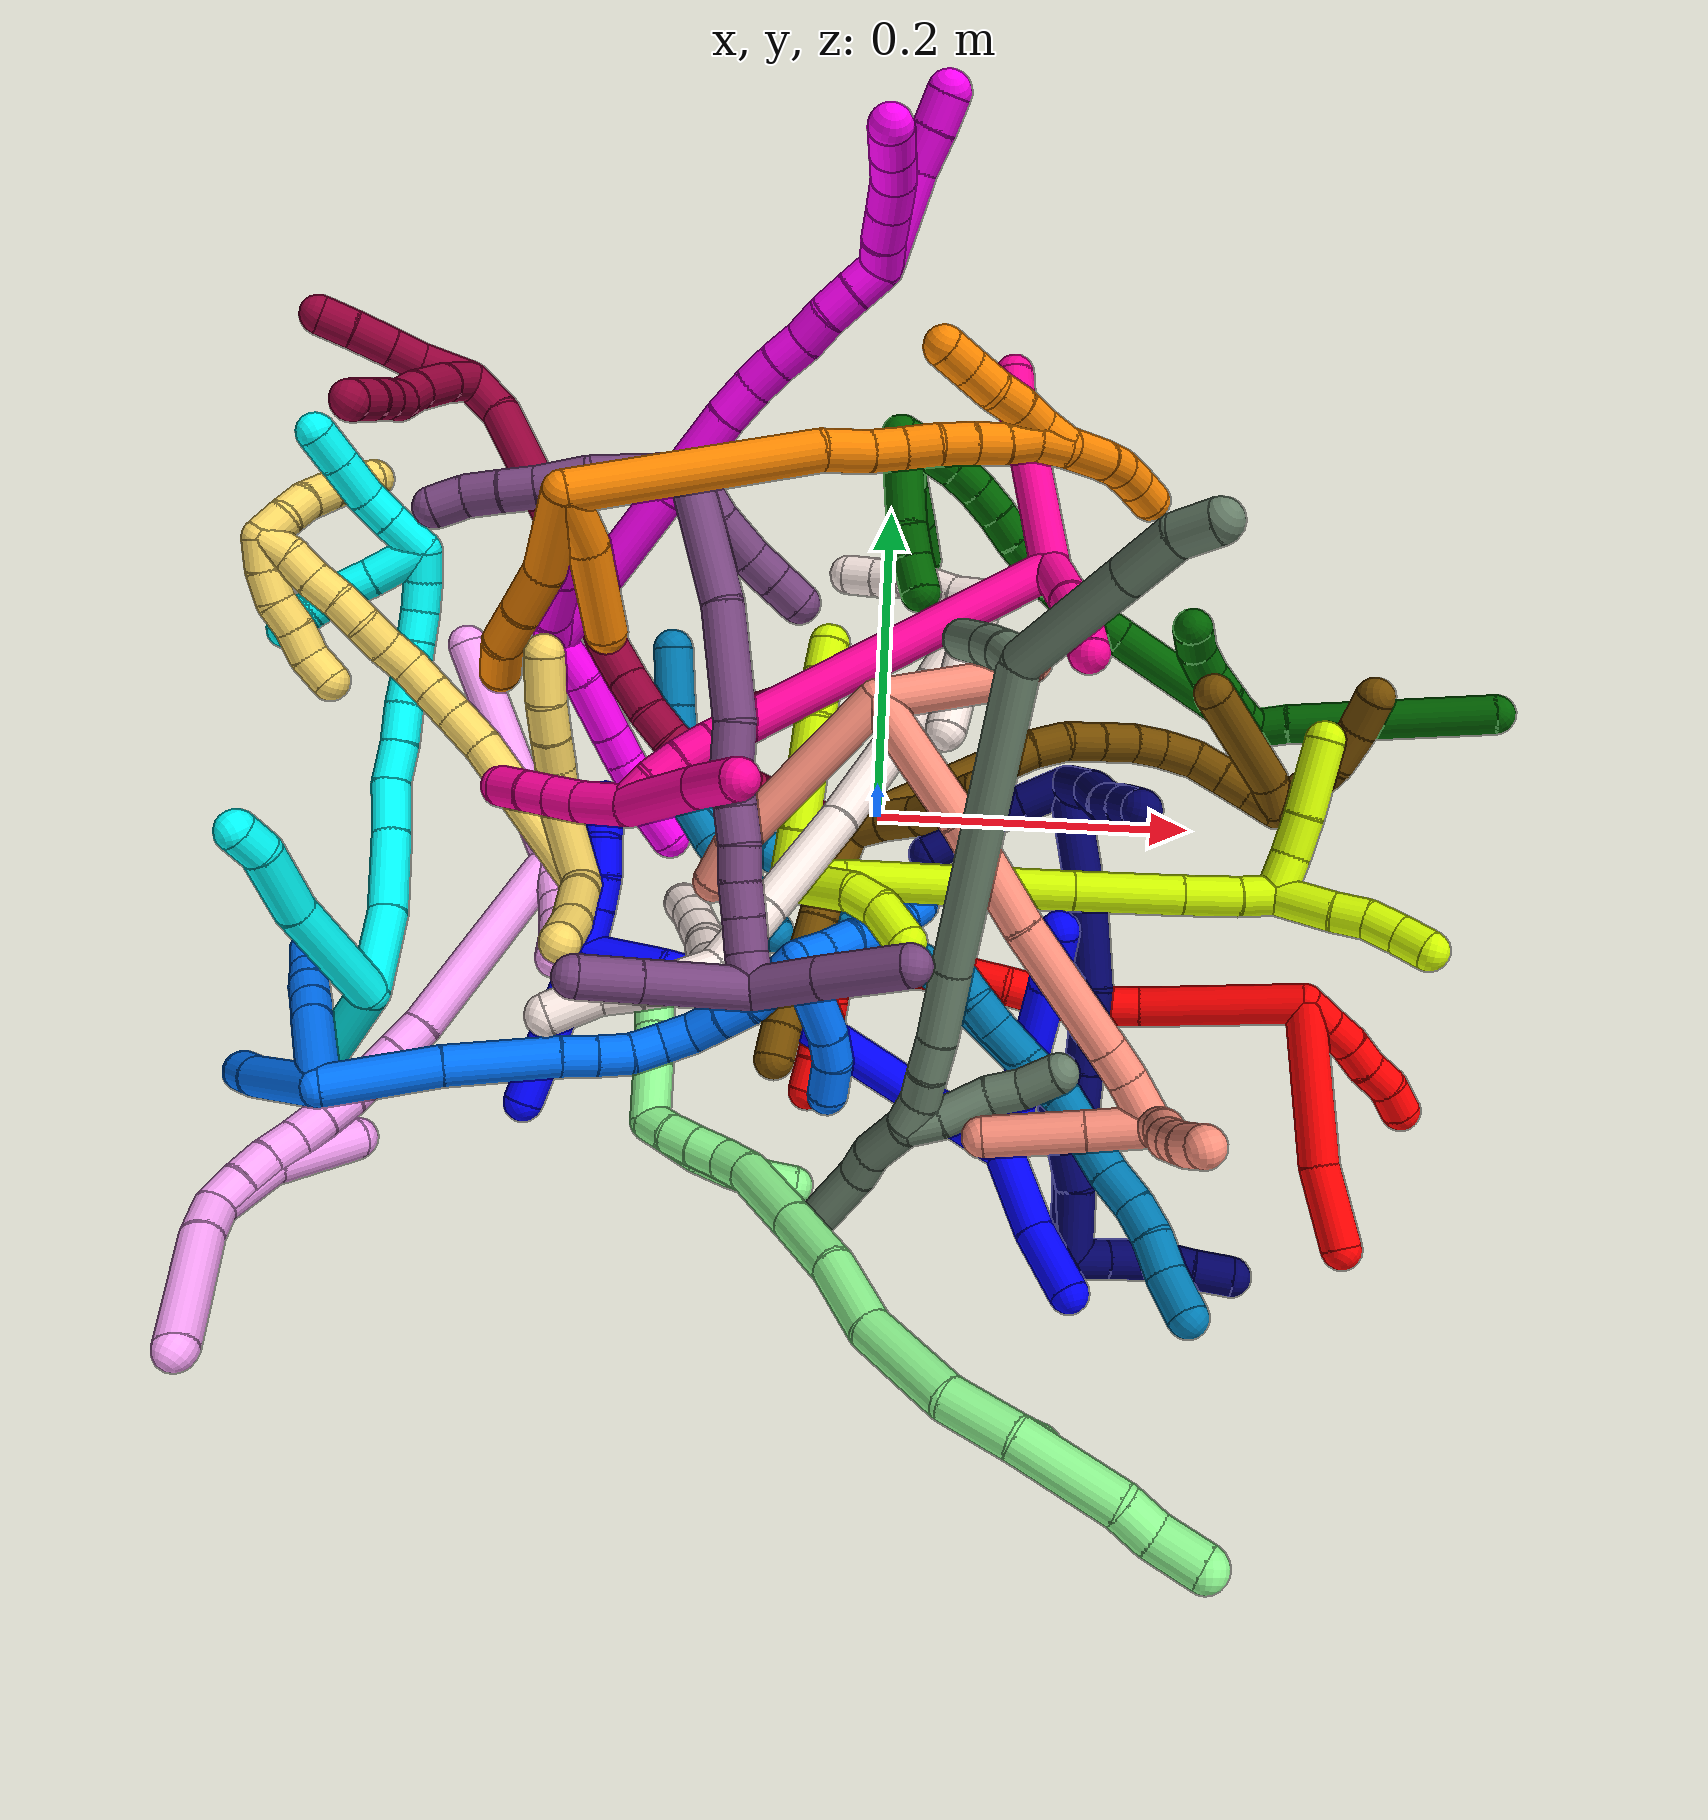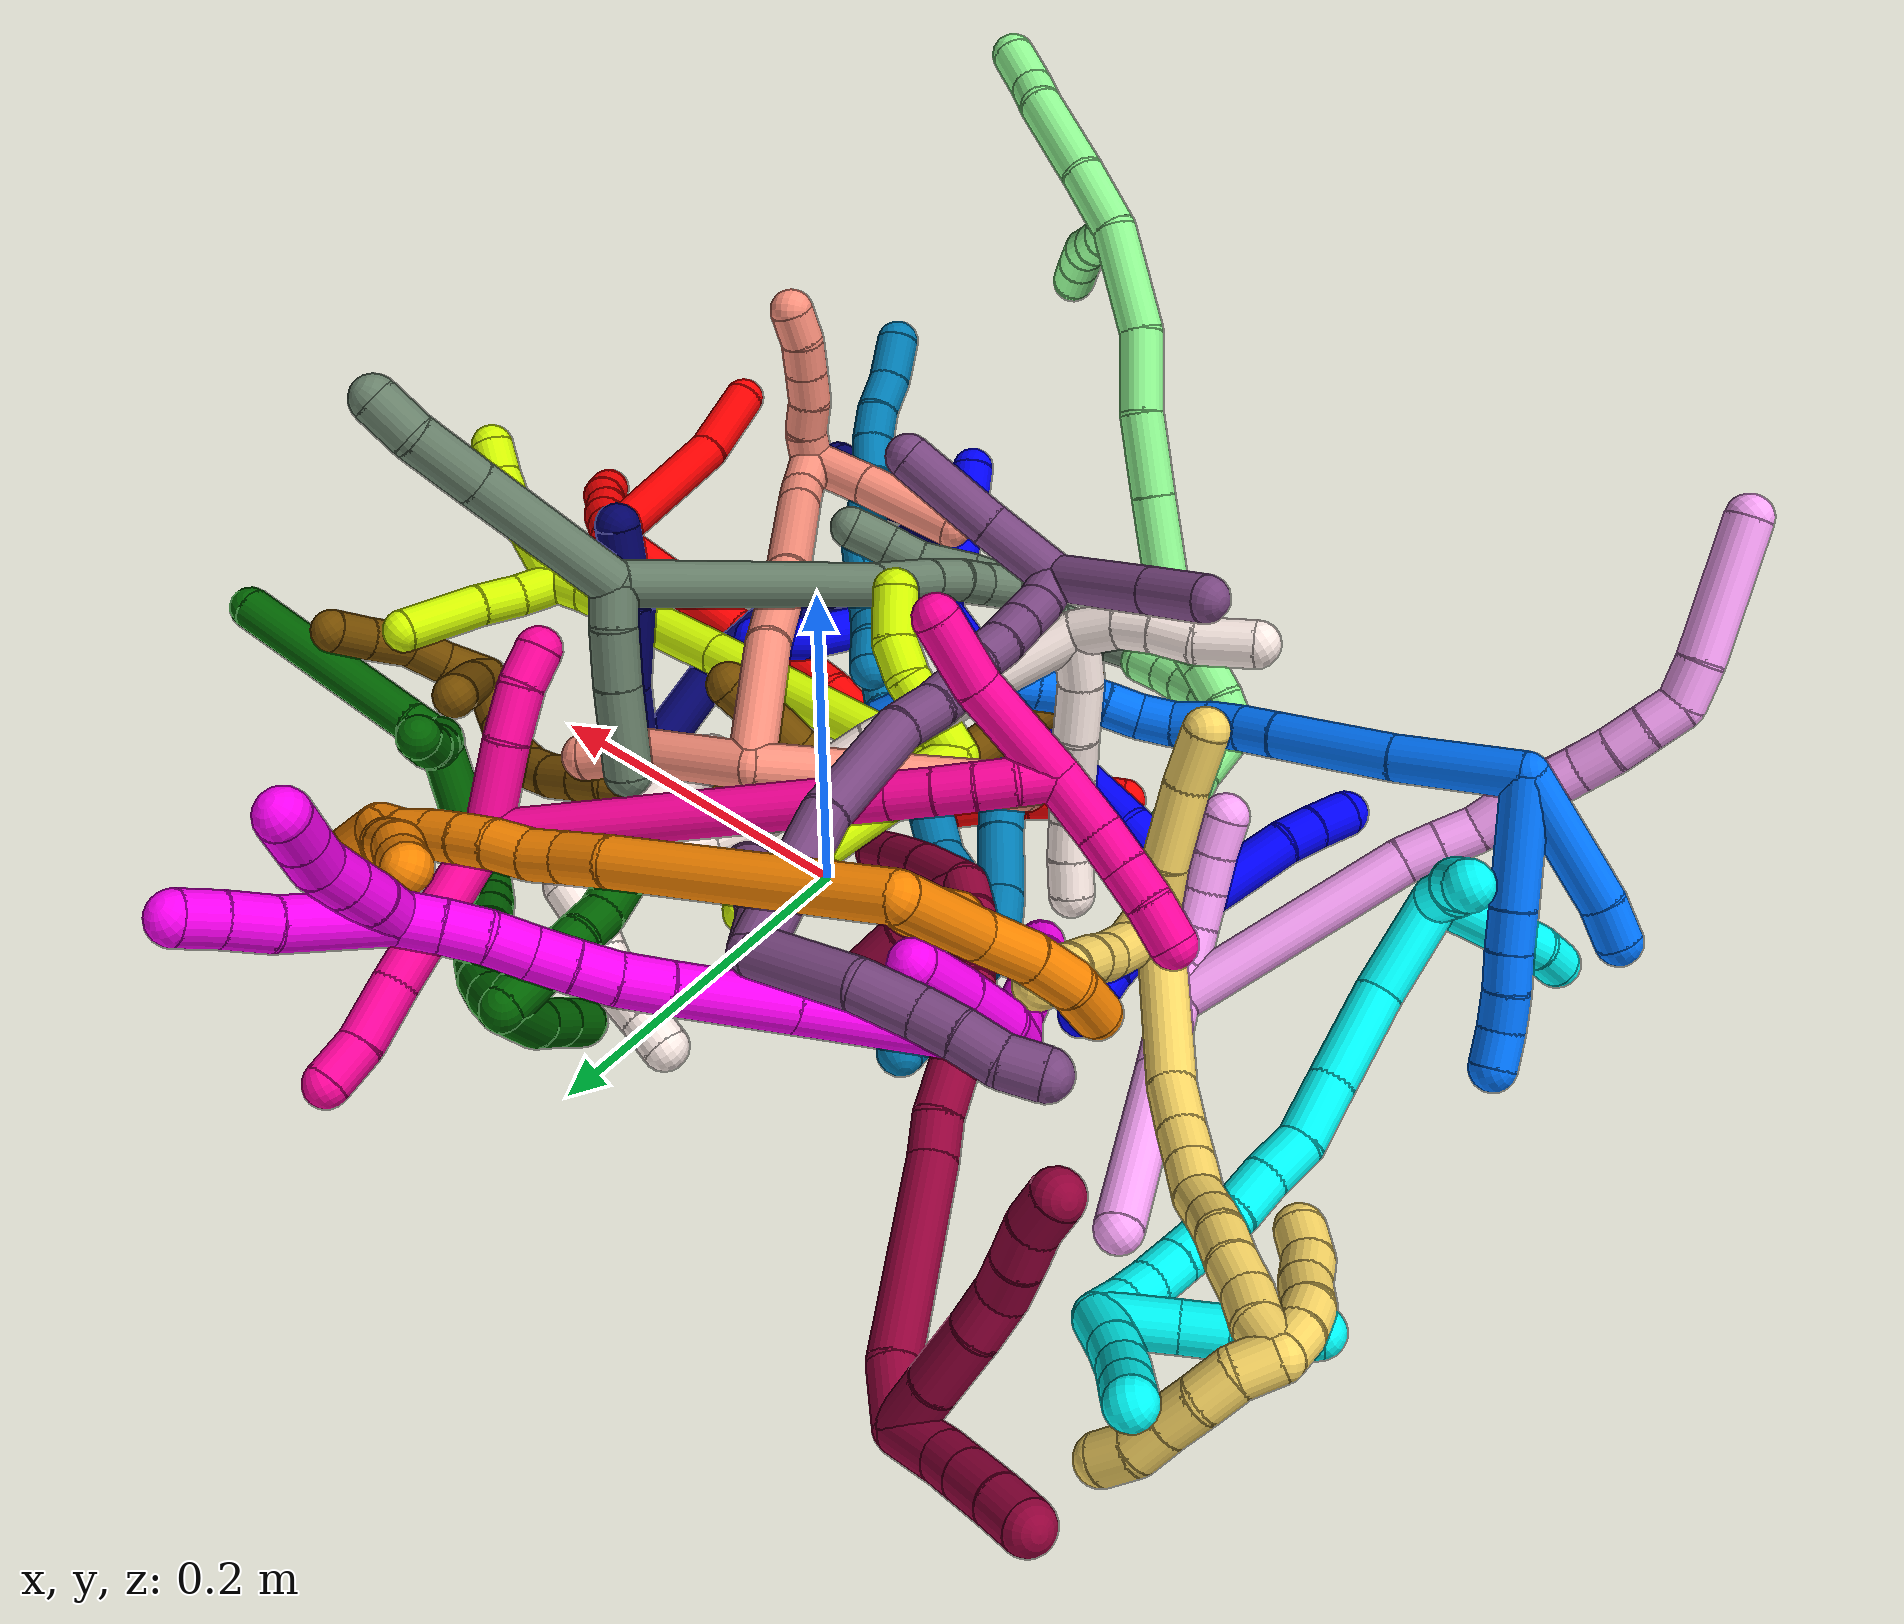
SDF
<sdf version="1.7">
 <world name="default">
  <plugin name="TubeGeneratorPlugin" filename="libtube_generator_plugin.so"/>
  <model name="photoneo_s_sensor">
   <static>1</static>
   <pose>0 0 2 1.57079 1.57079 3.14159</pose>
   <link name="link">
    <inertial><mass>0.1</mass></inertial>
    <sensor name="sensor" type="depth">
     <update_rate>30</update_rate>
     <camera>
      <horizontal_fov>1.22</horizontal_fov>
      <image><width>1920</width><height>1200</height><format>B8G8R8</format></image>
      <clip><near>0.1</near><far>4</far></clip>
      <depth_camera><output>points</output></depth_camera>
     </camera>
     <plugin name="camera_plugin" filename="libgazebo_ros_depth_camera.so">
      <baseline>0.2</baseline>
      <alwaysOn>1</alwaysOn>
      <updateRate>0.0</updateRate>
      <cameraName>camera_ir</cameraName>
      <imageTopicName>/camera/color/image_raw</imageTopicName>
      <cameraInfoTopicName>/camera/color/camera_info</cameraInfoTopicName>
      <depthImageTopicName>/camera/depth/image_raw</depthImageTopicName>
      <depthImageCameraInfoTopicName>/camera/depth/camera_info</depthImageCameraInfoTopicName>
      <pointCloudTopicName>/camera/depth/points</pointCloudTopicName>
      <frameName>fr_optical</frameName>
      <pointCloudCutoff>0.1</pointCloudCutoff>
      <pointCloudCutoffMax>2.0</pointCloudCutoffMax>
      <distortionK1>0</distortionK1>
      <distortionK2>0</distortionK2>
      <distortionK3>0</distortionK3>
      <distortionT1>0</distortionT1>
      <distortionT2>0</distortionT2>
      <CxPrime>0</CxPrime>
      <Cx>0</Cx>
      <Cy>0</Cy>
      <focalLength>0</focalLength>
      <hackBaseline>0</hackBaseline>
     </plugin>
    </sensor>
   </link>
  </model>
  <gravity>0 0 -9.8</gravity>
  <magnetic_field>6e-06 2.3e-05 -4.2e-05</magnetic_field>
  <atmosphere type="adiabatic"/>
  <physics name="default_physics" default="0" type="ode">
   <max_step_size>0.003</max_step_size>
   <real_time_factor>1</real_time_factor>
   <real_time_update_rate>1000</real_time_update_rate>
   <max_contacts>10000</max_contacts>
   <ode>
    <solver>
     <type>quick</type>
     <iters>100</iters>
     <sor>1.3</sor>
     <use_dynamic_moi_rescaling>0</use_dynamic_moi_rescaling>
    </solver>
    <constraints>
     <contact_max_correcting_vel>0</contact_max_correcting_vel>
     <contact_surface_layer>0.001</contact_surface_layer>
     <cfm>0</cfm>
     <erp>0.2</erp>
    </constraints>
   </ode>
  </physics>
  <scene><ambient>0.4 0.4 0.4 1</ambient><background>0.7 0.7 0.7 1</background><shadows>0</shadows></scene>
  <audio><device>default</device></audio>
  <spherical_coordinates>
   <surface_model>EARTH_WGS84</surface_model>
   <latitude_deg>0</latitude_deg>
   <longitude_deg>0</longitude_deg>
   <elevation>0</elevation>
   <heading_deg>0</heading_deg>
  </spherical_coordinates>
  <model name="bin">
   <static>1</static>
   <link name="bottom">
    <collision name="collision-bottom">
     <pose>0 0 -0.01 0 -0 0</pose>
     <geometry><box><size>0.8 0.6 0.02</size></box></geometry>
     <surface>
      <friction><ode><mu>100</mu><mu2>100</mu2></ode></friction>
      <contact><collide_bitmask>65535</collide_bitmask></contact>
     </surface>
    </collision>
   </link>
   <link name="west_wall">
    <collision name="collision-west_wall">
     <pose>-0.41 0 0.1 0 -0 0</pose>
     <geometry><box><size>0.02 0.6 0.2</size></box></geometry>
     <surface>
      <friction><ode><mu>100</mu><mu2>100</mu2></ode></friction>
      <contact><collide_bitmask>65535</collide_bitmask></contact>
     </surface>
    </collision>
   </link>
   <link name="east_wall">
    <collision name="collision-east_wall">
     <pose>0.41 0 0.1 0 -0 0</pose>
     <geometry><box><size>0.02 0.6 0.2</size></box></geometry>
     <surface>
      <friction><ode><mu>100</mu><mu2>100</mu2></ode></friction>
      <contact><collide_bitmask>65535</collide_bitmask></contact>
     </surface>
    </collision>
   </link>
   <link name="south_wall">
    <collision name="collision-south_wall">
     <pose>0 -0.31 0.1 0 -0 0</pose>
     <geometry><box><size>0.8 0.02 0.2</size></box></geometry>
     <surface>
      <friction><ode><mu>100</mu><mu2>100</mu2></ode></friction>
      <contact><collide_bitmask>65535</collide_bitmask></contact>
     </surface>
    </collision>
   </link>
   <link name="north_wall">
    <collision name="collision-north_wall">
     <pose>0 0.31 0.1 0 -0 0</pose>
     <geometry><box><size>0.8 0.02 0.2</size></box></geometry>
     <surface>
      <friction><ode><mu>100</mu><mu2>100</mu2></ode></friction>
      <contact><collide_bitmask>65535</collide_bitmask></contact>
     </surface>
    </collision>
   </link>
  </model>
  <model name="1">
   <static>0</static>
   <link name="1">
    <collision name="collision-cylinder-e_1_2_8">
     <pose>0.007391 0.004945 0.00764 -0.574427 0.682151 -0.208926</pose>
     <geometry><cylinder><radius>0.0125</radius><length>0.023447</length></cylinder></geometry>
     <surface>
      <friction><ode><mu>1.16</mu><mu2>1.16</mu2><slip1>0</slip1><slip2>0</slip2></ode></friction>
      <contact><ode><kp>1e+06</kp><kd>1</kd><max_vel>0</max_vel><min_depth>0.001</min_depth></ode></contact>
     </surface>
    </collision>
    <visual name="visual-cylinder-e_1_2_8">
     <pose>0.007391 0.004945 0.00764 -0.574427 0.682151 -0.208926</pose>
     <geometry><cylinder><radius>0.0125</radius><length>0.023447</length></cylinder></geometry>
     <material><ambient>0 0 1 1</ambient></material>
    </visual>
    <collision name="collision-cylinder-e_2_8_9">
     <pose>0.0416 0.02739 0.044245 -0.543504 0.670098 -0.19343</pose>
     <geometry><cylinder><radius>0.0125</radius><length>0.086359</length></cylinder></geometry>
     <surface>
      <friction><ode><mu>1.16</mu><mu2>1.16</mu2><slip1>0</slip1><slip2>0</slip2></ode></friction>
      <contact><ode><kp>1e+06</kp><kd>1</kd><max_vel>0</max_vel><min_depth>0.001</min_depth></ode></contact>
     </surface>
    </collision>
    <visual name="visual-cylinder-e_2_8_9">
     <pose>0.0416 0.02739 0.044245 -0.543504 0.670098 -0.19343</pose>
     <geometry><cylinder><radius>0.0125</radius><length>0.086359</length></cylinder></geometry>
     <material><ambient>0 0 1 1</ambient></material>
    </visual>
    <collision name="collision-cylinder-e_3_9_6">
     <pose>0.084303 0.050337 0.084251 -0.458203 0.911553 -0.227636</pose>
     <geometry><cylinder><radius>0.0125</radius><length>0.040194</length></cylinder></geometry>
     <surface>
      <friction><ode><mu>1.16</mu><mu2>1.16</mu2><slip1>0</slip1><slip2>0</slip2></ode></friction>
      <contact><ode><kp>1e+06</kp><kd>1</kd><max_vel>0</max_vel><min_depth>0.001</min_depth></ode></contact>
     </surface>
    </collision>
    <visual name="visual-cylinder-e_3_9_6">
     <pose>0.084303 0.050337 0.084251 -0.458203 0.911553 -0.227636</pose>
     <geometry><cylinder><radius>0.0125</radius><length>0.040194</length></cylinder></geometry>
     <material><ambient>0 0 1 1</ambient></material>
    </visual>
    <collision name="collision-cylinder-e_1_2_10">
     <pose>0.002635 0.001187 -0.027849 -3.09898 0.094259 -2.29291</pose>
     <geometry><cylinder><radius>0.0125</radius><length>0.055996</length></cylinder></geometry>
     <surface>
      <friction><ode><mu>1.16</mu><mu2>1.16</mu2><slip1>0</slip1><slip2>0</slip2></ode></friction>
      <contact><ode><kp>1e+06</kp><kd>1</kd><max_vel>0</max_vel><min_depth>0.001</min_depth></ode></contact>
     </surface>
    </collision>
    <visual name="visual-cylinder-e_1_2_10">
     <pose>0.002635 0.001187 -0.027849 -3.09898 0.094259 -2.29291</pose>
     <geometry><cylinder><radius>0.0125</radius><length>0.055996</length></cylinder></geometry>
     <material><ambient>0 0 1 1</ambient></material>
    </visual>
    <collision name="collision-cylinder-e_2_10_5">
     <pose>0.008669 0.005983 -0.077133 -2.97483 0.155094 -1.498</pose>
     <geometry><cylinder><radius>0.0125</radius><length>0.044004</length></cylinder></geometry>
     <surface>
      <friction><ode><mu>1.16</mu><mu2>1.16</mu2><slip1>0</slip1><slip2>0</slip2></ode></friction>
      <contact><ode><kp>1e+06</kp><kd>1</kd><max_vel>0</max_vel><min_depth>0.001</min_depth></ode></contact>
     </surface>
    </collision>
    <visual name="visual-cylinder-e_2_10_5">
     <pose>0.008669 0.005983 -0.077133 -2.97483 0.155094 -1.498</pose>
     <geometry><cylinder><radius>0.0125</radius><length>0.044004</length></cylinder></geometry>
     <material><ambient>0 0 1 1</ambient></material>
    </visual>
    <collision name="collision-cylinder-e_1_2_11">
     <pose>0.020803 -0.047211 0.044728 0.8124 0.30959 0.134034</pose>
     <geometry><cylinder><radius>0.0125</radius><length>0.136561</length></cylinder></geometry>
     <surface>
      <friction><ode><mu>1.16</mu><mu2>1.16</mu2><slip1>0</slip1><slip2>0</slip2></ode></friction>
      <contact><ode><kp>1e+06</kp><kd>1</kd><max_vel>0</max_vel><min_depth>0.001</min_depth></ode></contact>
     </surface>
    </collision>
    <visual name="visual-cylinder-e_1_2_11">
     <pose>0.020803 -0.047211 0.044728 0.8124 0.30959 0.134034</pose>
     <geometry><cylinder><radius>0.0125</radius><length>0.136561</length></cylinder></geometry>
     <material><ambient>0 0 1 1</ambient></material>
    </visual>
    <collision name="collision-cylinder-e_2_11_12">
     <pose>0.046755 -0.105989 0.099918 0.835525 0.318904 0.142529</pose>
     <geometry><cylinder><radius>0.0125</radius><length>0.032849</length></cylinder></geometry>
     <surface>
      <friction><ode><mu>1.16</mu><mu2>1.16</mu2><slip1>0</slip1><slip2>0</slip2></ode></friction>
      <contact><ode><kp>1e+06</kp><kd>1</kd><max_vel>0</max_vel><min_depth>0.001</min_depth></ode></contact>
     </surface>
    </collision>
    <visual name="visual-cylinder-e_2_11_12">
     <pose>0.046755 -0.105989 0.099918 0.835525 0.318904 0.142529</pose>
     <geometry><cylinder><radius>0.0125</radius><length>0.032849</length></cylinder></geometry>
     <material><ambient>0 0 1 1</ambient></material>
    </visual>
    <collision name="collision-cylinder-e_3_12_13">
     <pose>0.055265 -0.129375 0.118173 0.987818 0.233039 0.125877</pose>
     <geometry><cylinder><radius>0.0125</radius><length>0.029102</length></cylinder></geometry>
     <surface>
      <friction><ode><mu>1.16</mu><mu2>1.16</mu2><slip1>0</slip1><slip2>0</slip2></ode></friction>
      <contact><ode><kp>1e+06</kp><kd>1</kd><max_vel>0</max_vel><min_depth>0.001</min_depth></ode></contact>
     </surface>
    </collision>
    <visual name="visual-cylinder-e_3_12_13">
     <pose>0.055265 -0.129375 0.118173 0.987818 0.233039 0.125877</pose>
     <geometry><cylinder><radius>0.0125</radius><length>0.029102</length></cylinder></geometry>
     <material><ambient>0 0 1 1</ambient></material>
    </visual>
    <collision name="collision-cylinder-e_4_13_14">
     <pose>0.058005 -0.160602 0.137751 1.02513 -0.027318 -0.015374</pose>
     <geometry><cylinder><radius>0.0125</radius><length>0.045427</length></cylinder></geometry>
     <surface>
      <friction><ode><mu>1.16</mu><mu2>1.16</mu2><slip1>0</slip1><slip2>0</slip2></ode></friction>
      <contact><ode><kp>1e+06</kp><kd>1</kd><max_vel>0</max_vel><min_depth>0.001</min_depth></ode></contact>
     </surface>
    </collision>
    <visual name="visual-cylinder-e_4_13_14">
     <pose>0.058005 -0.160602 0.137751 1.02513 -0.027318 -0.015374</pose>
     <geometry><cylinder><radius>0.0125</radius><length>0.045427</length></cylinder></geometry>
     <material><ambient>0 0 1 1</ambient></material>
    </visual>
    <collision name="collision-cylinder-e_5_14_1">
     <pose>0.050612 -0.20288 0.164259 0.998751 -0.244032 -0.133583</pose>
     <geometry><cylinder><radius>0.0125</radius><length>0.056061</length></cylinder></geometry>
     <surface>
      <friction><ode><mu>1.16</mu><mu2>1.16</mu2><slip1>0</slip1><slip2>0</slip2></ode></friction>
      <contact><ode><kp>1e+06</kp><kd>1</kd><max_vel>0</max_vel><min_depth>0.001</min_depth></ode></contact>
     </surface>
    </collision>
    <visual name="visual-cylinder-e_5_14_1">
     <pose>0.050612 -0.20288 0.164259 0.998751 -0.244032 -0.133583</pose>
     <geometry><cylinder><radius>0.0125</radius><length>0.056061</length></cylinder></geometry>
     <material><ambient>0 0 1 1</ambient></material>
    </visual>
    <collision name="collision-cylinder-e_1_1_15">
     <pose>0.03979 -0.241938 0.156144 2.52501 -0.143635 -0.444368</pose>
     <geometry><cylinder><radius>0.0125</radius><length>0.056574</length></cylinder></geometry>
     <surface>
      <friction><ode><mu>1.16</mu><mu2>1.16</mu2><slip1>0</slip1><slip2>0</slip2></ode></friction>
      <contact><ode><kp>1e+06</kp><kd>1</kd><max_vel>0</max_vel><min_depth>0.001</min_depth></ode></contact>
     </surface>
    </collision>
    <visual name="visual-cylinder-e_1_1_15">
     <pose>0.03979 -0.241938 0.156144 2.52501 -0.143635 -0.444368</pose>
     <geometry><cylinder><radius>0.0125</radius><length>0.056574</length></cylinder></geometry>
     <material><ambient>0 0 1 1</ambient></material>
    </visual>
    <collision name="collision-cylinder-e_2_15_16">
     <pose>0.032204 -0.263897 0.125484 2.50578 -0.349082 -0.983856</pose>
     <geometry><cylinder><radius>0.0125</radius><length>0.020683</length></cylinder></geometry>
     <surface>
      <friction><ode><mu>1.16</mu><mu2>1.16</mu2><slip1>0</slip1><slip2>0</slip2></ode></friction>
      <contact><ode><kp>1e+06</kp><kd>1</kd><max_vel>0</max_vel><min_depth>0.001</min_depth></ode></contact>
     </surface>
    </collision>
    <visual name="visual-cylinder-e_2_15_16">
     <pose>0.032204 -0.263897 0.125484 2.50578 -0.349082 -0.983856</pose>
     <geometry><cylinder><radius>0.0125</radius><length>0.020683</length></cylinder></geometry>
     <material><ambient>0 0 1 1</ambient></material>
    </visual>
    <collision name="collision-cylinder-e_3_16_4">
     <pose>0.024316 -0.276102 0.109359 2.48255 -0.392548 -1.05327</pose>
     <geometry><cylinder><radius>0.0125</radius><length>0.022743</length></cylinder></geometry>
     <surface>
      <friction><ode><mu>1.16</mu><mu2>1.16</mu2><slip1>0</slip1><slip2>0</slip2></ode></friction>
      <contact><ode><kp>1e+06</kp><kd>1</kd><max_vel>0</max_vel><min_depth>0.001</min_depth></ode></contact>
     </surface>
    </collision>
    <visual name="visual-cylinder-e_3_16_4">
     <pose>0.024316 -0.276102 0.109359 2.48255 -0.392548 -1.05327</pose>
     <geometry><cylinder><radius>0.0125</radius><length>0.022743</length></cylinder></geometry>
     <material><ambient>0 0 1 1</ambient></material>
    </visual>
    <collision name="collision-cylinder-e_1_1_17">
     <pose>0.048612 -0.219135 0.19062 -0.516925 0.342518 -0.091386</pose>
     <geometry><cylinder><radius>0.0125</radius><length>0.02842</length></cylinder></geometry>
     <surface>
      <friction><ode><mu>1.16</mu><mu2>1.16</mu2><slip1>0</slip1><slip2>0</slip2></ode></friction>
      <contact><ode><kp>1e+06</kp><kd>1</kd><max_vel>0</max_vel><min_depth>0.001</min_depth></ode></contact>
     </surface>
    </collision>
    <visual name="visual-cylinder-e_1_1_17">
     <pose>0.048612 -0.219135 0.19062 -0.516925 0.342518 -0.091386</pose>
     <geometry><cylinder><radius>0.0125</radius><length>0.02842</length></cylinder></geometry>
     <material><ambient>0 0 1 1</ambient></material>
    </visual>
    <collision name="collision-cylinder-e_2_17_18">
     <pose>0.05742 -0.208354 0.210811 -0.453171 0.401194 -0.093686</pose>
     <geometry><cylinder><radius>0.0125</radius><length>0.020671</length></cylinder></geometry>
     <surface>
      <friction><ode><mu>1.16</mu><mu2>1.16</mu2><slip1>0</slip1><slip2>0</slip2></ode></friction>
      <contact><ode><kp>1e+06</kp><kd>1</kd><max_vel>0</max_vel><min_depth>0.001</min_depth></ode></contact>
     </surface>
    </collision>
    <visual name="visual-cylinder-e_2_17_18">
     <pose>0.05742 -0.208354 0.210811 -0.453171 0.401194 -0.093686</pose>
     <geometry><cylinder><radius>0.0125</radius><length>0.020671</length></cylinder></geometry>
     <material><ambient>0 0 1 1</ambient></material>
    </visual>
    <collision name="collision-cylinder-e_3_18_19">
     <pose>0.065453 -0.201369 0.230258 -0.253276 0.341291 -0.043873</pose>
     <geometry><cylinder><radius>0.0125</radius><length>0.023881</length></cylinder></geometry>
     <surface>
      <friction><ode><mu>1.16</mu><mu2>1.16</mu2><slip1>0</slip1><slip2>0</slip2></ode></friction>
      <contact><ode><kp>1e+06</kp><kd>1</kd><max_vel>0</max_vel><min_depth>0.001</min_depth></ode></contact>
     </surface>
    </collision>
    <visual name="visual-cylinder-e_3_18_19">
     <pose>0.065453 -0.201369 0.230258 -0.253276 0.341291 -0.043873</pose>
     <geometry><cylinder><radius>0.0125</radius><length>0.023881</length></cylinder></geometry>
     <material><ambient>0 0 1 1</ambient></material>
    </visual>
    <collision name="collision-cylinder-e_4_19_3">
     <pose>0.070052 -0.195003 0.254177 -0.265841 0.044552 -0.005958</pose>
     <geometry><cylinder><radius>0.0125</radius><length>0.027028</length></cylinder></geometry>
     <surface>
      <friction><ode><mu>1.16</mu><mu2>1.16</mu2><slip1>0</slip1><slip2>0</slip2></ode></friction>
      <contact><ode><kp>1e+06</kp><kd>1</kd><max_vel>0</max_vel><min_depth>0.001</min_depth></ode></contact>
     </surface>
    </collision>
    <visual name="visual-cylinder-e_4_19_3">
     <pose>0.070052 -0.195003 0.254177 -0.265841 0.044552 -0.005958</pose>
     <geometry><cylinder><radius>0.0125</radius><length>0.027028</length></cylinder></geometry>
     <material><ambient>0 0 1 1</ambient></material>
    </visual>
    <collision name="collision-sphere-3">
     <pose>0.070653 -0.191456 0.267203 0 -0 0</pose>
     <geometry><sphere><radius>0.0125</radius></sphere></geometry>
     <surface>
      <friction><ode><mu>1.16</mu><mu2>1.16</mu2><slip1>0</slip1><slip2>0</slip2></ode></friction>
      <contact><ode><kp>1e+06</kp><kd>1</kd><max_vel>0</max_vel><min_depth>0.001</min_depth></ode></contact>
     </surface>
    </collision>
    <visual name="visual-sphere-3">
     <pose>0.070653 -0.191456 0.267203 0 -0 0</pose>
     <geometry><sphere><radius>0.0125</radius></sphere></geometry>
     <material><ambient>0 0 1 1</ambient></material>
    </visual>
    <collision name="collision-sphere-19">
     <pose>0.06945 -0.198549 0.241151 0 -0 0</pose>
     <geometry><sphere><radius>0.0125</radius></sphere></geometry>
     <surface>
      <friction><ode><mu>1.16</mu><mu2>1.16</mu2><slip1>0</slip1><slip2>0</slip2></ode></friction>
      <contact><ode><kp>1e+06</kp><kd>1</kd><max_vel>0</max_vel><min_depth>0.001</min_depth></ode></contact>
     </surface>
    </collision>
    <visual name="visual-sphere-19">
     <pose>0.06945 -0.198549 0.241151 0 -0 0</pose>
     <geometry><sphere><radius>0.0125</radius></sphere></geometry>
     <material><ambient>0 0 1 1</ambient></material>
    </visual>
    <collision name="collision-sphere-5">
     <pose>0.012068 0.009591 -0.09857 0 -0 0</pose>
     <geometry><sphere><radius>0.0125</radius></sphere></geometry>
     <surface>
      <friction><ode><mu>1.16</mu><mu2>1.16</mu2><slip1>0</slip1><slip2>0</slip2></ode></friction>
      <contact><ode><kp>1e+06</kp><kd>1</kd><max_vel>0</max_vel><min_depth>0.001</min_depth></ode></contact>
     </surface>
    </collision>
    <visual name="visual-sphere-5">
     <pose>0.012068 0.009591 -0.09857 0 -0 0</pose>
     <geometry><sphere><radius>0.0125</radius></sphere></geometry>
     <material><ambient>0 0 1 1</ambient></material>
    </visual>
    <collision name="collision-sphere-10">
     <pose>0.00527 0.002375 -0.055697 0 -0 0</pose>
     <geometry><sphere><radius>0.0125</radius></sphere></geometry>
     <surface>
      <friction><ode><mu>1.16</mu><mu2>1.16</mu2><slip1>0</slip1><slip2>0</slip2></ode></friction>
      <contact><ode><kp>1e+06</kp><kd>1</kd><max_vel>0</max_vel><min_depth>0.001</min_depth></ode></contact>
     </surface>
    </collision>
    <visual name="visual-sphere-10">
     <pose>0.00527 0.002375 -0.055697 0 -0 0</pose>
     <geometry><sphere><radius>0.0125</radius></sphere></geometry>
     <material><ambient>0 0 1 1</ambient></material>
    </visual>
    <collision name="collision-sphere-6">
     <pose>0.100188 0.055782 0.095291 0 -0 0</pose>
     <geometry><sphere><radius>0.0125</radius></sphere></geometry>
     <surface>
      <friction><ode><mu>1.16</mu><mu2>1.16</mu2><slip1>0</slip1><slip2>0</slip2></ode></friction>
      <contact><ode><kp>1e+06</kp><kd>1</kd><max_vel>0</max_vel><min_depth>0.001</min_depth></ode></contact>
     </surface>
    </collision>
    <visual name="visual-sphere-6">
     <pose>0.100188 0.055782 0.095291 0 -0 0</pose>
     <geometry><sphere><radius>0.0125</radius></sphere></geometry>
     <material><ambient>0 0 1 1</ambient></material>
    </visual>
    <collision name="collision-sphere-9">
     <pose>0.068417 0.044891 0.073211 0 -0 0</pose>
     <geometry><sphere><radius>0.0125</radius></sphere></geometry>
     <surface>
      <friction><ode><mu>1.16</mu><mu2>1.16</mu2><slip1>0</slip1><slip2>0</slip2></ode></friction>
      <contact><ode><kp>1e+06</kp><kd>1</kd><max_vel>0</max_vel><min_depth>0.001</min_depth></ode></contact>
     </surface>
    </collision>
    <visual name="visual-sphere-9">
     <pose>0.068417 0.044891 0.073211 0 -0 0</pose>
     <geometry><sphere><radius>0.0125</radius></sphere></geometry>
     <material><ambient>0 0 1 1</ambient></material>
    </visual>
    <collision name="collision-sphere-2">
     <geometry><sphere><radius>0.0125</radius></sphere></geometry>
     <surface>
      <friction><ode><mu>1.16</mu><mu2>1.16</mu2><slip1>0</slip1><slip2>0</slip2></ode></friction>
      <contact><ode><kp>1e+06</kp><kd>1</kd><max_vel>0</max_vel><min_depth>0.001</min_depth></ode></contact>
     </surface>
    </collision>
    <visual name="visual-sphere-2">
     <geometry><sphere><radius>0.0125</radius></sphere></geometry>
     <material><ambient>0 0 1 1</ambient></material>
    </visual>
    <collision name="collision-sphere-8">
     <pose>0.014783 0.009889 0.015279 0 -0 0</pose>
     <geometry><sphere><radius>0.0125</radius></sphere></geometry>
     <surface>
      <friction><ode><mu>1.16</mu><mu2>1.16</mu2><slip1>0</slip1><slip2>0</slip2></ode></friction>
      <contact><ode><kp>1e+06</kp><kd>1</kd><max_vel>0</max_vel><min_depth>0.001</min_depth></ode></contact>
     </surface>
    </collision>
    <visual name="visual-sphere-8">
     <pose>0.014783 0.009889 0.015279 0 -0 0</pose>
     <geometry><sphere><radius>0.0125</radius></sphere></geometry>
     <material><ambient>0 0 1 1</ambient></material>
    </visual>
    <collision name="collision-sphere-11">
     <pose>0.041606 -0.094422 0.089456 0 -0 0</pose>
     <geometry><sphere><radius>0.0125</radius></sphere></geometry>
     <surface>
      <friction><ode><mu>1.16</mu><mu2>1.16</mu2><slip1>0</slip1><slip2>0</slip2></ode></friction>
      <contact><ode><kp>1e+06</kp><kd>1</kd><max_vel>0</max_vel><min_depth>0.001</min_depth></ode></contact>
     </surface>
    </collision>
    <visual name="visual-sphere-11">
     <pose>0.041606 -0.094422 0.089456 0 -0 0</pose>
     <geometry><sphere><radius>0.0125</radius></sphere></geometry>
     <material><ambient>0 0 1 1</ambient></material>
    </visual>
    <collision name="collision-sphere-12">
     <pose>0.051905 -0.117556 0.110379 0 -0 0</pose>
     <geometry><sphere><radius>0.0125</radius></sphere></geometry>
     <surface>
      <friction><ode><mu>1.16</mu><mu2>1.16</mu2><slip1>0</slip1><slip2>0</slip2></ode></friction>
      <contact><ode><kp>1e+06</kp><kd>1</kd><max_vel>0</max_vel><min_depth>0.001</min_depth></ode></contact>
     </surface>
    </collision>
    <visual name="visual-sphere-12">
     <pose>0.051905 -0.117556 0.110379 0 -0 0</pose>
     <geometry><sphere><radius>0.0125</radius></sphere></geometry>
     <material><ambient>0 0 1 1</ambient></material>
    </visual>
    <collision name="collision-sphere-13">
     <pose>0.058625 -0.141194 0.125967 0 -0 0</pose>
     <geometry><sphere><radius>0.0125</radius></sphere></geometry>
     <surface>
      <friction><ode><mu>1.16</mu><mu2>1.16</mu2><slip1>0</slip1><slip2>0</slip2></ode></friction>
      <contact><ode><kp>1e+06</kp><kd>1</kd><max_vel>0</max_vel><min_depth>0.001</min_depth></ode></contact>
     </surface>
    </collision>
    <visual name="visual-sphere-13">
     <pose>0.058625 -0.141194 0.125967 0 -0 0</pose>
     <geometry><sphere><radius>0.0125</radius></sphere></geometry>
     <material><ambient>0 0 1 1</ambient></material>
    </visual>
    <collision name="collision-sphere-14">
     <pose>0.057384 -0.18001 0.149534 0 -0 0</pose>
     <geometry><sphere><radius>0.0125</radius></sphere></geometry>
     <surface>
      <friction><ode><mu>1.16</mu><mu2>1.16</mu2><slip1>0</slip1><slip2>0</slip2></ode></friction>
      <contact><ode><kp>1e+06</kp><kd>1</kd><max_vel>0</max_vel><min_depth>0.001</min_depth></ode></contact>
     </surface>
    </collision>
    <visual name="visual-sphere-14">
     <pose>0.057384 -0.18001 0.149534 0 -0 0</pose>
     <geometry><sphere><radius>0.0125</radius></sphere></geometry>
     <material><ambient>0 0 1 1</ambient></material>
    </visual>
    <collision name="collision-sphere-1">
     <pose>0.043839 -0.22575 0.178984 0 -0 0</pose>
     <geometry><sphere><radius>0.0125</radius></sphere></geometry>
     <surface>
      <friction><ode><mu>1.16</mu><mu2>1.16</mu2><slip1>0</slip1><slip2>0</slip2></ode></friction>
      <contact><ode><kp>1e+06</kp><kd>1</kd><max_vel>0</max_vel><min_depth>0.001</min_depth></ode></contact>
     </surface>
    </collision>
    <visual name="visual-sphere-1">
     <pose>0.043839 -0.22575 0.178984 0 -0 0</pose>
     <geometry><sphere><radius>0.0125</radius></sphere></geometry>
     <material><ambient>0 0 1 1</ambient></material>
    </visual>
    <collision name="collision-sphere-18">
     <pose>0.061457 -0.204188 0.219365 0 -0 0</pose>
     <geometry><sphere><radius>0.0125</radius></sphere></geometry>
     <surface>
      <friction><ode><mu>1.16</mu><mu2>1.16</mu2><slip1>0</slip1><slip2>0</slip2></ode></friction>
      <contact><ode><kp>1e+06</kp><kd>1</kd><max_vel>0</max_vel><min_depth>0.001</min_depth></ode></contact>
     </surface>
    </collision>
    <visual name="visual-sphere-18">
     <pose>0.061457 -0.204188 0.219365 0 -0 0</pose>
     <geometry><sphere><radius>0.0125</radius></sphere></geometry>
     <material><ambient>0 0 1 1</ambient></material>
    </visual>
    <collision name="collision-sphere-15">
     <pose>0.035741 -0.258127 0.133303 0 -0 0</pose>
     <geometry><sphere><radius>0.0125</radius></sphere></geometry>
     <surface>
      <friction><ode><mu>1.16</mu><mu2>1.16</mu2><slip1>0</slip1><slip2>0</slip2></ode></friction>
      <contact><ode><kp>1e+06</kp><kd>1</kd><max_vel>0</max_vel><min_depth>0.001</min_depth></ode></contact>
     </surface>
    </collision>
    <visual name="visual-sphere-15">
     <pose>0.035741 -0.258127 0.133303 0 -0 0</pose>
     <geometry><sphere><radius>0.0125</radius></sphere></geometry>
     <material><ambient>0 0 1 1</ambient></material>
    </visual>
    <collision name="collision-sphere-16">
     <pose>0.028666 -0.269668 0.117665 0 -0 0</pose>
     <geometry><sphere><radius>0.0125</radius></sphere></geometry>
     <surface>
      <friction><ode><mu>1.16</mu><mu2>1.16</mu2><slip1>0</slip1><slip2>0</slip2></ode></friction>
      <contact><ode><kp>1e+06</kp><kd>1</kd><max_vel>0</max_vel><min_depth>0.001</min_depth></ode></contact>
     </surface>
    </collision>
    <visual name="visual-sphere-16">
     <pose>0.028666 -0.269668 0.117665 0 -0 0</pose>
     <geometry><sphere><radius>0.0125</radius></sphere></geometry>
     <material><ambient>0 0 1 1</ambient></material>
    </visual>
    <collision name="collision-sphere-4">
     <pose>0.019966 -0.282536 0.101053 0 -0 0</pose>
     <geometry><sphere><radius>0.0125</radius></sphere></geometry>
     <surface>
      <friction><ode><mu>1.16</mu><mu2>1.16</mu2><slip1>0</slip1><slip2>0</slip2></ode></friction>
      <contact><ode><kp>1e+06</kp><kd>1</kd><max_vel>0</max_vel><min_depth>0.001</min_depth></ode></contact>
     </surface>
    </collision>
    <visual name="visual-sphere-4">
     <pose>0.019966 -0.282536 0.101053 0 -0 0</pose>
     <geometry><sphere><radius>0.0125</radius></sphere></geometry>
     <material><ambient>0 0 1 1</ambient></material>
    </visual>
    <collision name="collision-sphere-17">
     <pose>0.053384 -0.21252 0.202256 0 -0 0</pose>
     <geometry><sphere><radius>0.0125</radius></sphere></geometry>
     <surface>
      <friction><ode><mu>1.16</mu><mu2>1.16</mu2><slip1>0</slip1><slip2>0</slip2></ode></friction>
      <contact><ode><kp>1e+06</kp><kd>1</kd><max_vel>0</max_vel><min_depth>0.001</min_depth></ode></contact>
     </surface>
    </collision>
    <visual name="visual-sphere-17">
     <pose>0.053384 -0.21252 0.202256 0 -0 0</pose>
     <geometry><sphere><radius>0.0125</radius></sphere></geometry>
     <material><ambient>0 0 1 1</ambient></material>
    </visual>
    <inertial>
     <pose>0.038181 -0.098091 0.089051 0 -0 0</pose>
     <mass>0.75</mass>
     <inertia><ixx>0.0003</ixx><ixy>0</ixy><ixz>0</ixz><iyy>0.000211</iyy><iyz>0</iyz><izz>6.5e-05</izz></inertia>
    </inertial>
   </link>
   <pose>0.088303 -0.207543 0.013604 -2.76695 -1.19224 1.50683</pose>
  </model>
  <model name="2">
   <static>0</static>
   <link name="2">
    <collision name="collision-cylinder-e_1_2_8">
     <pose>0.029624 0.001935 0.039736 -0.048669 0.640062 -0.016133</pose>
     <geometry><cylinder><radius>0.0125</radius><length>0.099202</length></cylinder></geometry>
     <surface>
      <friction><ode><mu>1.16</mu><mu2>1.16</mu2><slip1>0</slip1><slip2>0</slip2></ode></friction>
      <contact><ode><kp>1e+06</kp><kd>1</kd><max_vel>0</max_vel><min_depth>0.001</min_depth></ode></contact>
     </surface>
    </collision>
    <visual name="visual-cylinder-e_1_2_8">
     <pose>0.029624 0.001935 0.039736 -0.048669 0.640062 -0.016133</pose>
     <geometry><cylinder><radius>0.0125</radius><length>0.099202</length></cylinder></geometry>
     <material><ambient>1 0 0 1</ambient></material>
    </visual>
    <collision name="collision-cylinder-e_2_8_6">
     <pose>0.074404 0.009807 0.09897 -0.295521 0.639394 -0.098472</pose>
     <geometry><cylinder><radius>0.0125</radius><length>0.050798</length></cylinder></geometry>
     <surface>
      <friction><ode><mu>1.16</mu><mu2>1.16</mu2><slip1>0</slip1><slip2>0</slip2></ode></friction>
      <contact><ode><kp>1e+06</kp><kd>1</kd><max_vel>0</max_vel><min_depth>0.001</min_depth></ode></contact>
     </surface>
    </collision>
    <visual name="visual-cylinder-e_2_8_6">
     <pose>0.074404 0.009807 0.09897 -0.295521 0.639394 -0.098472</pose>
     <geometry><cylinder><radius>0.0125</radius><length>0.050798</length></cylinder></geometry>
     <material><ambient>1 0 0 1</ambient></material>
    </visual>
    <collision name="collision-cylinder-e_1_2_9">
     <pose>0.009493 0.00296 0.001056 -1.22803 1.25111 -0.941924</pose>
     <geometry><cylinder><radius>0.0125</radius><length>0.02</length></cylinder></geometry>
     <surface>
      <friction><ode><mu>1.16</mu><mu2>1.16</mu2><slip1>0</slip1><slip2>0</slip2></ode></friction>
      <contact><ode><kp>1e+06</kp><kd>1</kd><max_vel>0</max_vel><min_depth>0.001</min_depth></ode></contact>
     </surface>
    </collision>
    <visual name="visual-cylinder-e_1_2_9">
     <pose>0.009493 0.00296 0.001056 -1.22803 1.25111 -0.941924</pose>
     <geometry><cylinder><radius>0.0125</radius><length>0.02</length></cylinder></geometry>
     <material><ambient>1 0 0 1</ambient></material>
    </visual>
    <collision name="collision-cylinder-e_2_9_10">
     <pose>0.028614 0.008596 0.002503 -1.4259 1.29697 -1.16014</pose>
     <geometry><cylinder><radius>0.0125</radius><length>0.02</length></cylinder></geometry>
     <surface>
      <friction><ode><mu>1.16</mu><mu2>1.16</mu2><slip1>0</slip1><slip2>0</slip2></ode></friction>
      <contact><ode><kp>1e+06</kp><kd>1</kd><max_vel>0</max_vel><min_depth>0.001</min_depth></ode></contact>
     </surface>
    </collision>
    <visual name="visual-cylinder-e_2_9_10">
     <pose>0.028614 0.008596 0.002503 -1.4259 1.29697 -1.16014</pose>
     <geometry><cylinder><radius>0.0125</radius><length>0.02</length></cylinder></geometry>
     <material><ambient>1 0 0 1</ambient></material>
    </visual>
    <collision name="collision-cylinder-e_3_10_11">
     <pose>0.047911 0.012901 0.004854 -0.693363 1.31303 -0.542998</pose>
     <geometry><cylinder><radius>0.0125</radius><length>0.02</length></cylinder></geometry>
     <surface>
      <friction><ode><mu>1.16</mu><mu2>1.16</mu2><slip1>0</slip1><slip2>0</slip2></ode></friction>
      <contact><ode><kp>1e+06</kp><kd>1</kd><max_vel>0</max_vel><min_depth>0.001</min_depth></ode></contact>
     </surface>
    </collision>
    <visual name="visual-cylinder-e_3_10_11">
     <pose>0.047911 0.012901 0.004854 -0.693363 1.31303 -0.542998</pose>
     <geometry><cylinder><radius>0.0125</radius><length>0.02</length></cylinder></geometry>
     <material><ambient>1 0 0 1</ambient></material>
    </visual>
    <collision name="collision-cylinder-e_4_11_12">
     <pose>0.067197 0.017208 0.007418 -1.3493 1.29275 -1.08596</pose>
     <geometry><cylinder><radius>0.0125</radius><length>0.02</length></cylinder></geometry>
     <surface>
      <friction><ode><mu>1.16</mu><mu2>1.16</mu2><slip1>0</slip1><slip2>0</slip2></ode></friction>
      <contact><ode><kp>1e+06</kp><kd>1</kd><max_vel>0</max_vel><min_depth>0.001</min_depth></ode></contact>
     </surface>
    </collision>
    <visual name="visual-cylinder-e_4_11_12">
     <pose>0.067197 0.017208 0.007418 -1.3493 1.29275 -1.08596</pose>
     <geometry><cylinder><radius>0.0125</radius><length>0.02</length></cylinder></geometry>
     <material><ambient>1 0 0 1</ambient></material>
    </visual>
    <collision name="collision-cylinder-e_5_12_5">
     <pose>0.086478 0.020111 0.010577 -0.088151 1.31129 -0.067819</pose>
     <geometry><cylinder><radius>0.0125</radius><length>0.02</length></cylinder></geometry>
     <surface>
      <friction><ode><mu>1.16</mu><mu2>1.16</mu2><slip1>0</slip1><slip2>0</slip2></ode></friction>
      <contact><ode><kp>1e+06</kp><kd>1</kd><max_vel>0</max_vel><min_depth>0.001</min_depth></ode></contact>
     </surface>
    </collision>
    <visual name="visual-cylinder-e_5_12_5">
     <pose>0.086478 0.020111 0.010577 -0.088151 1.31129 -0.067819</pose>
     <geometry><cylinder><radius>0.0125</radius><length>0.02</length></cylinder></geometry>
     <material><ambient>1 0 0 1</ambient></material>
    </visual>
    <collision name="collision-cylinder-e_1_2_13">
     <pose>-0.021591 -0.043918 0.015238 1.23682 -0.434808 -0.311787</pose>
     <geometry><cylinder><radius>0.0125</radius><length>0.102511</length></cylinder></geometry>
     <surface>
      <friction><ode><mu>1.16</mu><mu2>1.16</mu2><slip1>0</slip1><slip2>0</slip2></ode></friction>
      <contact><ode><kp>1e+06</kp><kd>1</kd><max_vel>0</max_vel><min_depth>0.001</min_depth></ode></contact>
     </surface>
    </collision>
    <visual name="visual-cylinder-e_1_2_13">
     <pose>-0.021591 -0.043918 0.015238 1.23682 -0.434808 -0.311787</pose>
     <geometry><cylinder><radius>0.0125</radius><length>0.102511</length></cylinder></geometry>
     <material><ambient>1 0 0 1</ambient></material>
    </visual>
    <collision name="collision-cylinder-e_2_13_14">
     <pose>-0.054587 -0.102066 0.037836 1.09353 -0.618687 -0.384265</pose>
     <geometry><cylinder><radius>0.0125</radius><length>0.039333</length></cylinder></geometry>
     <surface>
      <friction><ode><mu>1.16</mu><mu2>1.16</mu2><slip1>0</slip1><slip2>0</slip2></ode></friction>
      <contact><ode><kp>1e+06</kp><kd>1</kd><max_vel>0</max_vel><min_depth>0.001</min_depth></ode></contact>
     </surface>
    </collision>
    <visual name="visual-cylinder-e_2_13_14">
     <pose>-0.054587 -0.102066 0.037836 1.09353 -0.618687 -0.384265</pose>
     <geometry><cylinder><radius>0.0125</radius><length>0.039333</length></cylinder></geometry>
     <material><ambient>1 0 0 1</ambient></material>
    </visual>
    <collision name="collision-cylinder-e_3_14_15">
     <pose>-0.083798 -0.130288 0.0502 1.2273 -0.875343 -0.636772</pose>
     <geometry><cylinder><radius>0.0125</radius><length>0.046381</length></cylinder></geometry>
     <surface>
      <friction><ode><mu>1.16</mu><mu2>1.16</mu2><slip1>0</slip1><slip2>0</slip2></ode></friction>
      <contact><ode><kp>1e+06</kp><kd>1</kd><max_vel>0</max_vel><min_depth>0.001</min_depth></ode></contact>
     </surface>
    </collision>
    <visual name="visual-cylinder-e_3_14_15">
     <pose>-0.083798 -0.130288 0.0502 1.2273 -0.875343 -0.636772</pose>
     <geometry><cylinder><radius>0.0125</radius><length>0.046381</length></cylinder></geometry>
     <material><ambient>1 0 0 1</ambient></material>
    </visual>
    <collision name="collision-cylinder-e_4_15_16">
     <pose>-0.108942 -0.15387 0.05667 1.41912 -0.647588 -0.561202</pose>
     <geometry><cylinder><radius>0.0125</radius><length>0.024332</length></cylinder></geometry>
     <surface>
      <friction><ode><mu>1.16</mu><mu2>1.16</mu2><slip1>0</slip1><slip2>0</slip2></ode></friction>
      <contact><ode><kp>1e+06</kp><kd>1</kd><max_vel>0</max_vel><min_depth>0.001</min_depth></ode></contact>
     </surface>
    </collision>
    <visual name="visual-cylinder-e_4_15_16">
     <pose>-0.108942 -0.15387 0.05667 1.41912 -0.647588 -0.561202</pose>
     <geometry><cylinder><radius>0.0125</radius><length>0.024332</length></cylinder></geometry>
     <material><ambient>1 0 0 1</ambient></material>
    </visual>
    <collision name="collision-cylinder-e_5_16_17">
     <pose>-0.123559 -0.170812 0.061292 1.16521 -0.738221 -0.499148</pose>
     <geometry><cylinder><radius>0.0125</radius><length>0.021629</length></cylinder></geometry>
     <surface>
      <friction><ode><mu>1.16</mu><mu2>1.16</mu2><slip1>0</slip1><slip2>0</slip2></ode></friction>
      <contact><ode><kp>1e+06</kp><kd>1</kd><max_vel>0</max_vel><min_depth>0.001</min_depth></ode></contact>
     </surface>
    </collision>
    <visual name="visual-cylinder-e_5_16_17">
     <pose>-0.123559 -0.170812 0.061292 1.16521 -0.738221 -0.499148</pose>
     <geometry><cylinder><radius>0.0125</radius><length>0.021629</length></cylinder></geometry>
     <material><ambient>1 0 0 1</ambient></material>
    </visual>
    <collision name="collision-cylinder-e_6_17_18">
     <pose>-0.139047 -0.187419 0.06765 1.23786 -0.69761 -0.506947</pose>
     <geometry><cylinder><radius>0.0125</radius><length>0.025561</length></cylinder></geometry>
     <surface>
      <friction><ode><mu>1.16</mu><mu2>1.16</mu2><slip1>0</slip1><slip2>0</slip2></ode></friction>
      <contact><ode><kp>1e+06</kp><kd>1</kd><max_vel>0</max_vel><min_depth>0.001</min_depth></ode></contact>
     </surface>
    </collision>
    <visual name="visual-cylinder-e_6_17_18">
     <pose>-0.139047 -0.187419 0.06765 1.23786 -0.69761 -0.506947</pose>
     <geometry><cylinder><radius>0.0125</radius><length>0.025561</length></cylinder></geometry>
     <material><ambient>1 0 0 1</ambient></material>
    </visual>
    <collision name="collision-cylinder-e_7_18_19">
     <pose>-0.154836 -0.203243 0.070411 1.63769 -0.855689 -0.907333</pose>
     <geometry><cylinder><radius>0.0125</radius><length>0.020076</length></cylinder></geometry>
     <surface>
      <friction><ode><mu>1.16</mu><mu2>1.16</mu2><slip1>0</slip1><slip2>0</slip2></ode></friction>
      <contact><ode><kp>1e+06</kp><kd>1</kd><max_vel>0</max_vel><min_depth>0.001</min_depth></ode></contact>
     </surface>
    </collision>
    <visual name="visual-cylinder-e_7_18_19">
     <pose>-0.154836 -0.203243 0.070411 1.63769 -0.855689 -0.907333</pose>
     <geometry><cylinder><radius>0.0125</radius><length>0.020076</length></cylinder></geometry>
     <material><ambient>1 0 0 1</ambient></material>
    </visual>
    <collision name="collision-cylinder-e_8_19_1">
     <pose>-0.17003 -0.216403 0.069413 1.65517 -0.855462 -0.920984</pose>
     <geometry><cylinder><radius>0.0125</radius><length>0.020177</length></cylinder></geometry>
     <surface>
      <friction><ode><mu>1.16</mu><mu2>1.16</mu2><slip1>0</slip1><slip2>0</slip2></ode></friction>
      <contact><ode><kp>1e+06</kp><kd>1</kd><max_vel>0</max_vel><min_depth>0.001</min_depth></ode></contact>
     </surface>
    </collision>
    <visual name="visual-cylinder-e_8_19_1">
     <pose>-0.17003 -0.216403 0.069413 1.65517 -0.855462 -0.920984</pose>
     <geometry><cylinder><radius>0.0125</radius><length>0.020177</length></cylinder></geometry>
     <material><ambient>1 0 0 1</ambient></material>
    </visual>
    <collision name="collision-cylinder-e_1_1_20">
     <pose>-0.181597 -0.23402 0.088718 0.50666 -0.172214 -0.044688</pose>
     <geometry><cylinder><radius>0.0125</radius><length>0.046116</length></cylinder></geometry>
     <surface>
      <friction><ode><mu>1.16</mu><mu2>1.16</mu2><slip1>0</slip1><slip2>0</slip2></ode></friction>
      <contact><ode><kp>1e+06</kp><kd>1</kd><max_vel>0</max_vel><min_depth>0.001</min_depth></ode></contact>
     </surface>
    </collision>
    <visual name="visual-cylinder-e_1_1_20">
     <pose>-0.181597 -0.23402 0.088718 0.50666 -0.172214 -0.044688</pose>
     <geometry><cylinder><radius>0.0125</radius><length>0.046116</length></cylinder></geometry>
     <material><ambient>1 0 0 1</ambient></material>
    </visual>
    <collision name="collision-cylinder-e_2_20_21">
     <pose>-0.189017 -0.252509 0.119604 0.595276 -0.254845 -0.078559</pose>
     <geometry><cylinder><radius>0.0125</radius><length>0.027513</length></cylinder></geometry>
     <surface>
      <friction><ode><mu>1.16</mu><mu2>1.16</mu2><slip1>0</slip1><slip2>0</slip2></ode></friction>
      <contact><ode><kp>1e+06</kp><kd>1</kd><max_vel>0</max_vel><min_depth>0.001</min_depth></ode></contact>
     </surface>
    </collision>
    <visual name="visual-cylinder-e_2_20_21">
     <pose>-0.189017 -0.252509 0.119604 0.595276 -0.254845 -0.078559</pose>
     <geometry><cylinder><radius>0.0125</radius><length>0.027513</length></cylinder></geometry>
     <material><ambient>1 0 0 1</ambient></material>
    </visual>
    <collision name="collision-cylinder-e_3_21_4">
     <pose>-0.194775 -0.268369 0.140532 0.703046 -0.174592 -0.064174</pose>
     <geometry><cylinder><radius>0.0125</radius><length>0.026371</length></cylinder></geometry>
     <surface>
      <friction><ode><mu>1.16</mu><mu2>1.16</mu2><slip1>0</slip1><slip2>0</slip2></ode></friction>
      <contact><ode><kp>1e+06</kp><kd>1</kd><max_vel>0</max_vel><min_depth>0.001</min_depth></ode></contact>
     </surface>
    </collision>
    <visual name="visual-cylinder-e_3_21_4">
     <pose>-0.194775 -0.268369 0.140532 0.703046 -0.174592 -0.064174</pose>
     <geometry><cylinder><radius>0.0125</radius><length>0.026371</length></cylinder></geometry>
     <material><ambient>1 0 0 1</ambient></material>
    </visual>
    <collision name="collision-cylinder-e_1_1_22">
     <pose>-0.173811 -0.224498 0.077968 0.1633 0.393569 0.032626</pose>
     <geometry><cylinder><radius>0.0125</radius><length>0.02</length></cylinder></geometry>
     <surface>
      <friction><ode><mu>1.16</mu><mu2>1.16</mu2><slip1>0</slip1><slip2>0</slip2></ode></friction>
      <contact><ode><kp>1e+06</kp><kd>1</kd><max_vel>0</max_vel><min_depth>0.001</min_depth></ode></contact>
     </surface>
    </collision>
    <visual name="visual-cylinder-e_1_1_22">
     <pose>-0.173811 -0.224498 0.077968 0.1633 0.393569 0.032626</pose>
     <geometry><cylinder><radius>0.0125</radius><length>0.02</length></cylinder></geometry>
     <material><ambient>1 0 0 1</ambient></material>
    </visual>
    <collision name="collision-cylinder-e_2_22_23">
     <pose>-0.164959 -0.226335 0.095724 0.03881 0.525575 0.010441</pose>
     <geometry><cylinder><radius>0.0125</radius><length>0.02</length></cylinder></geometry>
     <surface>
      <friction><ode><mu>1.16</mu><mu2>1.16</mu2><slip1>0</slip1><slip2>0</slip2></ode></friction>
      <contact><ode><kp>1e+06</kp><kd>1</kd><max_vel>0</max_vel><min_depth>0.001</min_depth></ode></contact>
     </surface>
    </collision>
    <visual name="visual-cylinder-e_2_22_23">
     <pose>-0.164959 -0.226335 0.095724 0.03881 0.525575 0.010441</pose>
     <geometry><cylinder><radius>0.0125</radius><length>0.02</length></cylinder></geometry>
     <material><ambient>1 0 0 1</ambient></material>
    </visual>
    <collision name="collision-cylinder-e_3_23_24">
     <pose>-0.154252 -0.229871 0.111944 0.399673 0.605297 0.126314</pose>
     <geometry><cylinder><radius>0.0125</radius><length>0.02</length></cylinder></geometry>
     <surface>
      <friction><ode><mu>1.16</mu><mu2>1.16</mu2><slip1>0</slip1><slip2>0</slip2></ode></friction>
      <contact><ode><kp>1e+06</kp><kd>1</kd><max_vel>0</max_vel><min_depth>0.001</min_depth></ode></contact>
     </surface>
    </collision>
    <visual name="visual-cylinder-e_3_23_24">
     <pose>-0.154252 -0.229871 0.111944 0.399673 0.605297 0.126314</pose>
     <geometry><cylinder><radius>0.0125</radius><length>0.02</length></cylinder></geometry>
     <material><ambient>1 0 0 1</ambient></material>
    </visual>
    <collision name="collision-cylinder-e_4_24_25">
     <pose>-0.144634 -0.234363 0.128624 0.140978 0.403726 0.028897</pose>
     <geometry><cylinder><radius>0.0125</radius><length>0.02</length></cylinder></geometry>
     <surface>
      <friction><ode><mu>1.16</mu><mu2>1.16</mu2><slip1>0</slip1><slip2>0</slip2></ode></friction>
      <contact><ode><kp>1e+06</kp><kd>1</kd><max_vel>0</max_vel><min_depth>0.001</min_depth></ode></contact>
     </surface>
    </collision>
    <visual name="visual-cylinder-e_4_24_25">
     <pose>-0.144634 -0.234363 0.128624 0.140978 0.403726 0.028897</pose>
     <geometry><cylinder><radius>0.0125</radius><length>0.02</length></cylinder></geometry>
     <material><ambient>1 0 0 1</ambient></material>
    </visual>
    <collision name="collision-cylinder-e_5_25_3">
     <pose>-0.136323 -0.238077 0.146385 0.272855 0.453603 0.06334</pose>
     <geometry><cylinder><radius>0.0125</radius><length>0.02</length></cylinder></geometry>
     <surface>
      <friction><ode><mu>1.16</mu><mu2>1.16</mu2><slip1>0</slip1><slip2>0</slip2></ode></friction>
      <contact><ode><kp>1e+06</kp><kd>1</kd><max_vel>0</max_vel><min_depth>0.001</min_depth></ode></contact>
     </surface>
    </collision>
    <visual name="visual-cylinder-e_5_25_3">
     <pose>-0.136323 -0.238077 0.146385 0.272855 0.453603 0.06334</pose>
     <geometry><cylinder><radius>0.0125</radius><length>0.02</length></cylinder></geometry>
     <material><ambient>1 0 0 1</ambient></material>
    </visual>
    <collision name="collision-sphere-3">
     <pose>-0.131941 -0.240499 0.155041 0 -0 0</pose>
     <geometry><sphere><radius>0.0125</radius></sphere></geometry>
     <surface>
      <friction><ode><mu>1.16</mu><mu2>1.16</mu2><slip1>0</slip1><slip2>0</slip2></ode></friction>
      <contact><ode><kp>1e+06</kp><kd>1</kd><max_vel>0</max_vel><min_depth>0.001</min_depth></ode></contact>
     </surface>
    </collision>
    <visual name="visual-sphere-3">
     <pose>-0.131941 -0.240499 0.155041 0 -0 0</pose>
     <geometry><sphere><radius>0.0125</radius></sphere></geometry>
     <material><ambient>1 0 0 1</ambient></material>
    </visual>
    <collision name="collision-sphere-25">
     <pose>-0.140705 -0.235655 0.137728 0 -0 0</pose>
     <geometry><sphere><radius>0.0125</radius></sphere></geometry>
     <surface>
      <friction><ode><mu>1.16</mu><mu2>1.16</mu2><slip1>0</slip1><slip2>0</slip2></ode></friction>
      <contact><ode><kp>1e+06</kp><kd>1</kd><max_vel>0</max_vel><min_depth>0.001</min_depth></ode></contact>
     </surface>
    </collision>
    <visual name="visual-sphere-25">
     <pose>-0.140705 -0.235655 0.137728 0 -0 0</pose>
     <geometry><sphere><radius>0.0125</radius></sphere></geometry>
     <material><ambient>1 0 0 1</ambient></material>
    </visual>
    <collision name="collision-sphere-24">
     <pose>-0.148562 -0.233071 0.119519 0 -0 0</pose>
     <geometry><sphere><radius>0.0125</radius></sphere></geometry>
     <surface>
      <friction><ode><mu>1.16</mu><mu2>1.16</mu2><slip1>0</slip1><slip2>0</slip2></ode></friction>
      <contact><ode><kp>1e+06</kp><kd>1</kd><max_vel>0</max_vel><min_depth>0.001</min_depth></ode></contact>
     </surface>
    </collision>
    <visual name="visual-sphere-24">
     <pose>-0.148562 -0.233071 0.119519 0 -0 0</pose>
     <geometry><sphere><radius>0.0125</radius></sphere></geometry>
     <material><ambient>1 0 0 1</ambient></material>
    </visual>
    <collision name="collision-sphere-23">
     <pose>-0.159942 -0.226671 0.104368 0 -0 0</pose>
     <geometry><sphere><radius>0.0125</radius></sphere></geometry>
     <surface>
      <friction><ode><mu>1.16</mu><mu2>1.16</mu2><slip1>0</slip1><slip2>0</slip2></ode></friction>
      <contact><ode><kp>1e+06</kp><kd>1</kd><max_vel>0</max_vel><min_depth>0.001</min_depth></ode></contact>
     </surface>
    </collision>
    <visual name="visual-sphere-23">
     <pose>-0.159942 -0.226671 0.104368 0 -0 0</pose>
     <geometry><sphere><radius>0.0125</radius></sphere></geometry>
     <material><ambient>1 0 0 1</ambient></material>
    </visual>
    <collision name="collision-sphere-22">
     <pose>-0.169976 -0.226 0.087081 0 -0 0</pose>
     <geometry><sphere><radius>0.0125</radius></sphere></geometry>
     <surface>
      <friction><ode><mu>1.16</mu><mu2>1.16</mu2><slip1>0</slip1><slip2>0</slip2></ode></friction>
      <contact><ode><kp>1e+06</kp><kd>1</kd><max_vel>0</max_vel><min_depth>0.001</min_depth></ode></contact>
     </surface>
    </collision>
    <visual name="visual-sphere-22">
     <pose>-0.169976 -0.226 0.087081 0 -0 0</pose>
     <geometry><sphere><radius>0.0125</radius></sphere></geometry>
     <material><ambient>1 0 0 1</ambient></material>
    </visual>
    <collision name="collision-sphere-4">
     <pose>-0.197065 -0.276764 0.150438 0 -0 0</pose>
     <geometry><sphere><radius>0.0125</radius></sphere></geometry>
     <surface>
      <friction><ode><mu>1.16</mu><mu2>1.16</mu2><slip1>0</slip1><slip2>0</slip2></ode></friction>
      <contact><ode><kp>1e+06</kp><kd>1</kd><max_vel>0</max_vel><min_depth>0.001</min_depth></ode></contact>
     </surface>
    </collision>
    <visual name="visual-sphere-4">
     <pose>-0.197065 -0.276764 0.150438 0 -0 0</pose>
     <geometry><sphere><radius>0.0125</radius></sphere></geometry>
     <material><ambient>1 0 0 1</ambient></material>
    </visual>
    <collision name="collision-sphere-21">
     <pose>-0.192485 -0.259973 0.130627 0 -0 0</pose>
     <geometry><sphere><radius>0.0125</radius></sphere></geometry>
     <surface>
      <friction><ode><mu>1.16</mu><mu2>1.16</mu2><slip1>0</slip1><slip2>0</slip2></ode></friction>
      <contact><ode><kp>1e+06</kp><kd>1</kd><max_vel>0</max_vel><min_depth>0.001</min_depth></ode></contact>
     </surface>
    </collision>
    <visual name="visual-sphere-21">
     <pose>-0.192485 -0.259973 0.130627 0 -0 0</pose>
     <geometry><sphere><radius>0.0125</radius></sphere></geometry>
     <material><ambient>1 0 0 1</ambient></material>
    </visual>
    <collision name="collision-sphere-20">
     <pose>-0.185549 -0.245044 0.108581 0 -0 0</pose>
     <geometry><sphere><radius>0.0125</radius></sphere></geometry>
     <surface>
      <friction><ode><mu>1.16</mu><mu2>1.16</mu2><slip1>0</slip1><slip2>0</slip2></ode></friction>
      <contact><ode><kp>1e+06</kp><kd>1</kd><max_vel>0</max_vel><min_depth>0.001</min_depth></ode></contact>
     </surface>
    </collision>
    <visual name="visual-sphere-20">
     <pose>-0.185549 -0.245044 0.108581 0 -0 0</pose>
     <geometry><sphere><radius>0.0125</radius></sphere></geometry>
     <material><ambient>1 0 0 1</ambient></material>
    </visual>
    <collision name="collision-sphere-11">
     <pose>0.057581 0.01453 0.006815 0 -0 0</pose>
     <geometry><sphere><radius>0.0125</radius></sphere></geometry>
     <surface>
      <friction><ode><mu>1.16</mu><mu2>1.16</mu2><slip1>0</slip1><slip2>0</slip2></ode></friction>
      <contact><ode><kp>1e+06</kp><kd>1</kd><max_vel>0</max_vel><min_depth>0.001</min_depth></ode></contact>
     </surface>
    </collision>
    <visual name="visual-sphere-11">
     <pose>0.057581 0.01453 0.006815 0 -0 0</pose>
     <geometry><sphere><radius>0.0125</radius></sphere></geometry>
     <material><ambient>1 0 0 1</ambient></material>
    </visual>
    <collision name="collision-sphere-10">
     <pose>0.038242 0.011271 0.002893 0 -0 0</pose>
     <geometry><sphere><radius>0.0125</radius></sphere></geometry>
     <surface>
      <friction><ode><mu>1.16</mu><mu2>1.16</mu2><slip1>0</slip1><slip2>0</slip2></ode></friction>
      <contact><ode><kp>1e+06</kp><kd>1</kd><max_vel>0</max_vel><min_depth>0.001</min_depth></ode></contact>
     </surface>
    </collision>
    <visual name="visual-sphere-10">
     <pose>0.038242 0.011271 0.002893 0 -0 0</pose>
     <geometry><sphere><radius>0.0125</radius></sphere></geometry>
     <material><ambient>1 0 0 1</ambient></material>
    </visual>
    <collision name="collision-sphere-6">
     <pose>0.08956 0.015743 0.118468 0 -0 0</pose>
     <geometry><sphere><radius>0.0125</radius></sphere></geometry>
     <surface>
      <friction><ode><mu>1.16</mu><mu2>1.16</mu2><slip1>0</slip1><slip2>0</slip2></ode></friction>
      <contact><ode><kp>1e+06</kp><kd>1</kd><max_vel>0</max_vel><min_depth>0.001</min_depth></ode></contact>
     </surface>
    </collision>
    <visual name="visual-sphere-6">
     <pose>0.08956 0.015743 0.118468 0 -0 0</pose>
     <geometry><sphere><radius>0.0125</radius></sphere></geometry>
     <material><ambient>1 0 0 1</ambient></material>
    </visual>
    <collision name="collision-sphere-9">
     <pose>0.018987 0.00592 0.002112 0 -0 0</pose>
     <geometry><sphere><radius>0.0125</radius></sphere></geometry>
     <surface>
      <friction><ode><mu>1.16</mu><mu2>1.16</mu2><slip1>0</slip1><slip2>0</slip2></ode></friction>
      <contact><ode><kp>1e+06</kp><kd>1</kd><max_vel>0</max_vel><min_depth>0.001</min_depth></ode></contact>
     </surface>
    </collision>
    <visual name="visual-sphere-9">
     <pose>0.018987 0.00592 0.002112 0 -0 0</pose>
     <geometry><sphere><radius>0.0125</radius></sphere></geometry>
     <material><ambient>1 0 0 1</ambient></material>
    </visual>
    <collision name="collision-sphere-2">
     <geometry><sphere><radius>0.0125</radius></sphere></geometry>
     <surface>
      <friction><ode><mu>1.16</mu><mu2>1.16</mu2><slip1>0</slip1><slip2>0</slip2></ode></friction>
      <contact><ode><kp>1e+06</kp><kd>1</kd><max_vel>0</max_vel><min_depth>0.001</min_depth></ode></contact>
     </surface>
    </collision>
    <visual name="visual-sphere-2">
     <geometry><sphere><radius>0.0125</radius></sphere></geometry>
     <material><ambient>1 0 0 1</ambient></material>
    </visual>
    <collision name="collision-sphere-19">
     <pose>-0.162415 -0.20981 0.069971 0 -0 0</pose>
     <geometry><sphere><radius>0.0125</radius></sphere></geometry>
     <surface>
      <friction><ode><mu>1.16</mu><mu2>1.16</mu2><slip1>0</slip1><slip2>0</slip2></ode></friction>
      <contact><ode><kp>1e+06</kp><kd>1</kd><max_vel>0</max_vel><min_depth>0.001</min_depth></ode></contact>
     </surface>
    </collision>
    <visual name="visual-sphere-19">
     <pose>-0.162415 -0.20981 0.069971 0 -0 0</pose>
     <geometry><sphere><radius>0.0125</radius></sphere></geometry>
     <material><ambient>1 0 0 1</ambient></material>
    </visual>
    <collision name="collision-sphere-8">
     <pose>0.059248 0.003871 0.079472 0 -0 0</pose>
     <geometry><sphere><radius>0.0125</radius></sphere></geometry>
     <surface>
      <friction><ode><mu>1.16</mu><mu2>1.16</mu2><slip1>0</slip1><slip2>0</slip2></ode></friction>
      <contact><ode><kp>1e+06</kp><kd>1</kd><max_vel>0</max_vel><min_depth>0.001</min_depth></ode></contact>
     </surface>
    </collision>
    <visual name="visual-sphere-8">
     <pose>0.059248 0.003871 0.079472 0 -0 0</pose>
     <geometry><sphere><radius>0.0125</radius></sphere></geometry>
     <material><ambient>1 0 0 1</ambient></material>
    </visual>
    <collision name="collision-sphere-12">
     <pose>0.076813 0.019885 0.008021 0 -0 0</pose>
     <geometry><sphere><radius>0.0125</radius></sphere></geometry>
     <surface>
      <friction><ode><mu>1.16</mu><mu2>1.16</mu2><slip1>0</slip1><slip2>0</slip2></ode></friction>
      <contact><ode><kp>1e+06</kp><kd>1</kd><max_vel>0</max_vel><min_depth>0.001</min_depth></ode></contact>
     </surface>
    </collision>
    <visual name="visual-sphere-12">
     <pose>0.076813 0.019885 0.008021 0 -0 0</pose>
     <geometry><sphere><radius>0.0125</radius></sphere></geometry>
     <material><ambient>1 0 0 1</ambient></material>
    </visual>
    <collision name="collision-sphere-5">
     <pose>0.096143 0.020337 0.013133 0 -0 0</pose>
     <geometry><sphere><radius>0.0125</radius></sphere></geometry>
     <surface>
      <friction><ode><mu>1.16</mu><mu2>1.16</mu2><slip1>0</slip1><slip2>0</slip2></ode></friction>
      <contact><ode><kp>1e+06</kp><kd>1</kd><max_vel>0</max_vel><min_depth>0.001</min_depth></ode></contact>
     </surface>
    </collision>
    <visual name="visual-sphere-5">
     <pose>0.096143 0.020337 0.013133 0 -0 0</pose>
     <geometry><sphere><radius>0.0125</radius></sphere></geometry>
     <material><ambient>1 0 0 1</ambient></material>
    </visual>
    <collision name="collision-sphere-13">
     <pose>-0.043181 -0.087835 0.030477 0 -0 0</pose>
     <geometry><sphere><radius>0.0125</radius></sphere></geometry>
     <surface>
      <friction><ode><mu>1.16</mu><mu2>1.16</mu2><slip1>0</slip1><slip2>0</slip2></ode></friction>
      <contact><ode><kp>1e+06</kp><kd>1</kd><max_vel>0</max_vel><min_depth>0.001</min_depth></ode></contact>
     </surface>
    </collision>
    <visual name="visual-sphere-13">
     <pose>-0.043181 -0.087835 0.030477 0 -0 0</pose>
     <geometry><sphere><radius>0.0125</radius></sphere></geometry>
     <material><ambient>1 0 0 1</ambient></material>
    </visual>
    <collision name="collision-sphere-14">
     <pose>-0.065993 -0.116297 0.045196 0 -0 0</pose>
     <geometry><sphere><radius>0.0125</radius></sphere></geometry>
     <surface>
      <friction><ode><mu>1.16</mu><mu2>1.16</mu2><slip1>0</slip1><slip2>0</slip2></ode></friction>
      <contact><ode><kp>1e+06</kp><kd>1</kd><max_vel>0</max_vel><min_depth>0.001</min_depth></ode></contact>
     </surface>
    </collision>
    <visual name="visual-sphere-14">
     <pose>-0.065993 -0.116297 0.045196 0 -0 0</pose>
     <geometry><sphere><radius>0.0125</radius></sphere></geometry>
     <material><ambient>1 0 0 1</ambient></material>
    </visual>
    <collision name="collision-sphere-15">
     <pose>-0.101603 -0.144279 0.055204 0 -0 0</pose>
     <geometry><sphere><radius>0.0125</radius></sphere></geometry>
     <surface>
      <friction><ode><mu>1.16</mu><mu2>1.16</mu2><slip1>0</slip1><slip2>0</slip2></ode></friction>
      <contact><ode><kp>1e+06</kp><kd>1</kd><max_vel>0</max_vel><min_depth>0.001</min_depth></ode></contact>
     </surface>
    </collision>
    <visual name="visual-sphere-15">
     <pose>-0.101603 -0.144279 0.055204 0 -0 0</pose>
     <geometry><sphere><radius>0.0125</radius></sphere></geometry>
     <material><ambient>1 0 0 1</ambient></material>
    </visual>
    <collision name="collision-sphere-16">
     <pose>-0.116281 -0.163462 0.058136 0 -0 0</pose>
     <geometry><sphere><radius>0.0125</radius></sphere></geometry>
     <surface>
      <friction><ode><mu>1.16</mu><mu2>1.16</mu2><slip1>0</slip1><slip2>0</slip2></ode></friction>
      <contact><ode><kp>1e+06</kp><kd>1</kd><max_vel>0</max_vel><min_depth>0.001</min_depth></ode></contact>
     </surface>
    </collision>
    <visual name="visual-sphere-16">
     <pose>-0.116281 -0.163462 0.058136 0 -0 0</pose>
     <geometry><sphere><radius>0.0125</radius></sphere></geometry>
     <material><ambient>1 0 0 1</ambient></material>
    </visual>
    <collision name="collision-sphere-17">
     <pose>-0.130837 -0.178162 0.064448 0 -0 0</pose>
     <geometry><sphere><radius>0.0125</radius></sphere></geometry>
     <surface>
      <friction><ode><mu>1.16</mu><mu2>1.16</mu2><slip1>0</slip1><slip2>0</slip2></ode></friction>
      <contact><ode><kp>1e+06</kp><kd>1</kd><max_vel>0</max_vel><min_depth>0.001</min_depth></ode></contact>
     </surface>
    </collision>
    <visual name="visual-sphere-17">
     <pose>-0.130837 -0.178162 0.064448 0 -0 0</pose>
     <geometry><sphere><radius>0.0125</radius></sphere></geometry>
     <material><ambient>1 0 0 1</ambient></material>
    </visual>
    <collision name="collision-sphere-18">
     <pose>-0.147257 -0.196676 0.070851 0 -0 0</pose>
     <geometry><sphere><radius>0.0125</radius></sphere></geometry>
     <surface>
      <friction><ode><mu>1.16</mu><mu2>1.16</mu2><slip1>0</slip1><slip2>0</slip2></ode></friction>
      <contact><ode><kp>1e+06</kp><kd>1</kd><max_vel>0</max_vel><min_depth>0.001</min_depth></ode></contact>
     </surface>
    </collision>
    <visual name="visual-sphere-18">
     <pose>-0.147257 -0.196676 0.070851 0 -0 0</pose>
     <geometry><sphere><radius>0.0125</radius></sphere></geometry>
     <material><ambient>1 0 0 1</ambient></material>
    </visual>
    <collision name="collision-sphere-1">
     <pose>-0.177646 -0.222997 0.068855 0 -0 0</pose>
     <geometry><sphere><radius>0.0125</radius></sphere></geometry>
     <surface>
      <friction><ode><mu>1.16</mu><mu2>1.16</mu2><slip1>0</slip1><slip2>0</slip2></ode></friction>
      <contact><ode><kp>1e+06</kp><kd>1</kd><max_vel>0</max_vel><min_depth>0.001</min_depth></ode></contact>
     </surface>
    </collision>
    <visual name="visual-sphere-1">
     <pose>-0.177646 -0.222997 0.068855 0 -0 0</pose>
     <geometry><sphere><radius>0.0125</radius></sphere></geometry>
     <material><ambient>1 0 0 1</ambient></material>
    </visual>
    <inertial>
     <pose>-0.06179 -0.108252 0.059233 0 -0 0</pose>
     <mass>0.75</mass>
     <inertia>
      <ixx>0.000161</ixx>
      <ixy>0</ixy>
      <ixz>0</ixz>
      <iyy>0.000122</iyy>
      <iyz>0</iyz>
      <izz>0.000119</izz>
     </inertia>
    </inertial>
   </link>
   <pose>0.269588 -0.107472 0.041814 1.01476 0.570942 -0.749927</pose>
  </model>
  <model name="3">
   <static>0</static>
   <link name="3">
    <collision name="collision-cylinder-e_1_2_8">
     <pose>-0.01954 0.033205 0.014743 -1.15293 -0.493468 0.32461</pose>
     <geometry><cylinder><radius>0.0125</radius><length>0.082504</length></cylinder></geometry>
     <surface>
      <friction><ode><mu>1.16</mu><mu2>1.16</mu2><slip1>0</slip1><slip2>0</slip2></ode></friction>
      <contact><ode><kp>1e+06</kp><kd>1</kd><max_vel>0</max_vel><min_depth>0.001</min_depth></ode></contact>
     </surface>
    </collision>
    <visual name="visual-cylinder-e_1_2_8">
     <pose>-0.01954 0.033205 0.014743 -1.15293 -0.493468 0.32461</pose>
     <geometry><cylinder><radius>0.0125</radius><length>0.082504</length></cylinder></geometry>
     <material><ambient>0.003922 1 0.996078 1</ambient></material>
    </visual>
    <collision name="collision-cylinder-e_2_8_9">
     <pose>-0.049419 0.087174 0.034522 -1.33288 -0.450634 0.356702</pose>
     <geometry><cylinder><radius>0.0125</radius><length>0.047472</length></cylinder></geometry>
     <surface>
      <friction><ode><mu>1.16</mu><mu2>1.16</mu2><slip1>0</slip1><slip2>0</slip2></ode></friction>
      <contact><ode><kp>1e+06</kp><kd>1</kd><max_vel>0</max_vel><min_depth>0.001</min_depth></ode></contact>
     </surface>
    </collision>
    <visual name="visual-cylinder-e_2_8_9">
     <pose>-0.049419 0.087174 0.034522 -1.33288 -0.450634 0.356702</pose>
     <geometry><cylinder><radius>0.0125</radius><length>0.047472</length></cylinder></geometry>
     <material><ambient>0.003922 1 0.996078 1</ambient></material>
    </visual>
    <collision name="collision-cylinder-e_3_9_6">
     <pose>-0.065431 0.114843 0.04407 -0.99196 -0.602613 0.333193</pose>
     <geometry><cylinder><radius>0.0125</radius><length>0.020024</length></cylinder></geometry>
     <surface>
      <friction><ode><mu>1.16</mu><mu2>1.16</mu2><slip1>0</slip1><slip2>0</slip2></ode></friction>
      <contact><ode><kp>1e+06</kp><kd>1</kd><max_vel>0</max_vel><min_depth>0.001</min_depth></ode></contact>
     </surface>
    </collision>
    <visual name="visual-cylinder-e_3_9_6">
     <pose>-0.065431 0.114843 0.04407 -0.99196 -0.602613 0.333193</pose>
     <geometry><cylinder><radius>0.0125</radius><length>0.020024</length></cylinder></geometry>
     <material><ambient>0.003922 1 0.996078 1</ambient></material>
    </visual>
    <collision name="collision-cylinder-e_1_2_10">
     <pose>-0.002717 -0.036202 0.012964 1.22691 -0.070537 -0.049674</pose>
     <geometry><cylinder><radius>0.0125</radius><length>0.077097</length></cylinder></geometry>
     <surface>
      <friction><ode><mu>1.16</mu><mu2>1.16</mu2><slip1>0</slip1><slip2>0</slip2></ode></friction>
      <contact><ode><kp>1e+06</kp><kd>1</kd><max_vel>0</max_vel><min_depth>0.001</min_depth></ode></contact>
     </surface>
    </collision>
    <visual name="visual-cylinder-e_1_2_10">
     <pose>-0.002717 -0.036202 0.012964 1.22691 -0.070537 -0.049674</pose>
     <geometry><cylinder><radius>0.0125</radius><length>0.077097</length></cylinder></geometry>
     <material><ambient>0.003922 1 0.996078 1</ambient></material>
    </visual>
    <collision name="collision-cylinder-e_2_10_5">
     <pose>-0.005654 -0.083784 0.027173 1.46186 -0.01926 -0.017268</pose>
     <geometry><cylinder><radius>0.0125</radius><length>0.022903</length></cylinder></geometry>
     <surface>
      <friction><ode><mu>1.16</mu><mu2>1.16</mu2><slip1>0</slip1><slip2>0</slip2></ode></friction>
      <contact><ode><kp>1e+06</kp><kd>1</kd><max_vel>0</max_vel><min_depth>0.001</min_depth></ode></contact>
     </surface>
    </collision>
    <visual name="visual-cylinder-e_2_10_5">
     <pose>-0.005654 -0.083784 0.027173 1.46186 -0.01926 -0.017268</pose>
     <geometry><cylinder><radius>0.0125</radius><length>0.022903</length></cylinder></geometry>
     <material><ambient>0.003922 1 0.996078 1</ambient></material>
    </visual>
    <collision name="collision-cylinder-e_1_2_11">
     <pose>-0.020248 0.000561 -0.020168 -3.11377 -0.78717 3.07461</pose>
     <geometry><cylinder><radius>0.0125</radius><length>0.057168</length></cylinder></geometry>
     <surface>
      <friction><ode><mu>1.16</mu><mu2>1.16</mu2><slip1>0</slip1><slip2>0</slip2></ode></friction>
      <contact><ode><kp>1e+06</kp><kd>1</kd><max_vel>0</max_vel><min_depth>0.001</min_depth></ode></contact>
     </surface>
    </collision>
    <visual name="visual-cylinder-e_1_2_11">
     <pose>-0.020248 0.000561 -0.020168 -3.11377 -0.78717 3.07461</pose>
     <geometry><cylinder><radius>0.0125</radius><length>0.057168</length></cylinder></geometry>
     <material><ambient>0.003922 1 0.996078 1</ambient></material>
    </visual>
    <collision name="collision-cylinder-e_2_11_12">
     <pose>-0.061843 0.005003 -0.055981 -2.89846 -0.924063 2.66044</pose>
     <geometry><cylinder><radius>0.0125</radius><length>0.053497</length></cylinder></geometry>
     <surface>
      <friction><ode><mu>1.16</mu><mu2>1.16</mu2><slip1>0</slip1><slip2>0</slip2></ode></friction>
      <contact><ode><kp>1e+06</kp><kd>1</kd><max_vel>0</max_vel><min_depth>0.001</min_depth></ode></contact>
     </surface>
    </collision>
    <visual name="visual-cylinder-e_2_11_12">
     <pose>-0.061843 0.005003 -0.055981 -2.89846 -0.924063 2.66044</pose>
     <geometry><cylinder><radius>0.0125</radius><length>0.053497</length></cylinder></geometry>
     <material><ambient>0.003922 1 0.996078 1</ambient></material>
    </visual>
    <collision name="collision-cylinder-e_3_12_13">
     <pose>-0.097875 0.012804 -0.081148 -2.75104 -0.959232 2.4148</pose>
     <geometry><cylinder><radius>0.0125</radius><length>0.035874</length></cylinder></geometry>
     <surface>
      <friction><ode><mu>1.16</mu><mu2>1.16</mu2><slip1>0</slip1><slip2>0</slip2></ode></friction>
      <contact><ode><kp>1e+06</kp><kd>1</kd><max_vel>0</max_vel><min_depth>0.001</min_depth></ode></contact>
     </surface>
    </collision>
    <visual name="visual-cylinder-e_3_12_13">
     <pose>-0.097875 0.012804 -0.081148 -2.75104 -0.959232 2.4148</pose>
     <geometry><cylinder><radius>0.0125</radius><length>0.035874</length></cylinder></geometry>
     <material><ambient>0.003922 1 0.996078 1</ambient></material>
    </visual>
    <collision name="collision-cylinder-e_4_13_14">
     <pose>-0.120864 0.022153 -0.099146 -2.5719 -0.689778 1.77387</pose>
     <geometry><cylinder><radius>0.0125</radius><length>0.026095</length></cylinder></geometry>
     <surface>
      <friction><ode><mu>1.16</mu><mu2>1.16</mu2><slip1>0</slip1><slip2>0</slip2></ode></friction>
      <contact><ode><kp>1e+06</kp><kd>1</kd><max_vel>0</max_vel><min_depth>0.001</min_depth></ode></contact>
     </surface>
    </collision>
    <visual name="visual-cylinder-e_4_13_14">
     <pose>-0.120864 0.022153 -0.099146 -2.5719 -0.689778 1.77387</pose>
     <geometry><cylinder><radius>0.0125</radius><length>0.026095</length></cylinder></geometry>
     <material><ambient>0.003922 1 0.996078 1</ambient></material>
    </visual>
    <collision name="collision-cylinder-e_5_14_15">
     <pose>-0.138216 0.033002 -0.11502 -2.50935 -0.778639 1.79543</pose>
     <geometry><cylinder><radius>0.0125</radius><length>0.025768</length></cylinder></geometry>
     <surface>
      <friction><ode><mu>1.16</mu><mu2>1.16</mu2><slip1>0</slip1><slip2>0</slip2></ode></friction>
      <contact><ode><kp>1e+06</kp><kd>1</kd><max_vel>0</max_vel><min_depth>0.001</min_depth></ode></contact>
     </surface>
    </collision>
    <visual name="visual-cylinder-e_5_14_15">
     <pose>-0.138216 0.033002 -0.11502 -2.50935 -0.778639 1.79543</pose>
     <geometry><cylinder><radius>0.0125</radius><length>0.025768</length></cylinder></geometry>
     <material><ambient>0.003922 1 0.996078 1</ambient></material>
    </visual>
    <collision name="collision-cylinder-e_6_15_16">
     <pose>-0.153663 0.044194 -0.128919 -2.41544 -0.634588 1.42555</pose>
     <geometry><cylinder><radius>0.0125</radius><length>0.021587</length></cylinder></geometry>
     <surface>
      <friction><ode><mu>1.16</mu><mu2>1.16</mu2><slip1>0</slip1><slip2>0</slip2></ode></friction>
      <contact><ode><kp>1e+06</kp><kd>1</kd><max_vel>0</max_vel><min_depth>0.001</min_depth></ode></contact>
     </surface>
    </collision>
    <visual name="visual-cylinder-e_6_15_16">
     <pose>-0.153663 0.044194 -0.128919 -2.41544 -0.634588 1.42555</pose>
     <geometry><cylinder><radius>0.0125</radius><length>0.021587</length></cylinder></geometry>
     <material><ambient>0.003922 1 0.996078 1</ambient></material>
    </visual>
    <collision name="collision-cylinder-e_7_16_17">
     <pose>-0.166156 0.055774 -0.140817 -2.31959 -0.655221 1.32461</pose>
     <geometry><cylinder><radius>0.0125</radius><length>0.020002</length></cylinder></geometry>
     <surface>
      <friction><ode><mu>1.16</mu><mu2>1.16</mu2><slip1>0</slip1><slip2>0</slip2></ode></friction>
      <contact><ode><kp>1e+06</kp><kd>1</kd><max_vel>0</max_vel><min_depth>0.001</min_depth></ode></contact>
     </surface>
    </collision>
    <visual name="visual-cylinder-e_7_16_17">
     <pose>-0.166156 0.055774 -0.140817 -2.31959 -0.655221 1.32461</pose>
     <geometry><cylinder><radius>0.0125</radius><length>0.020002</length></cylinder></geometry>
     <material><ambient>0.003922 1 0.996078 1</ambient></material>
    </visual>
    <collision name="collision-cylinder-e_8_17_18">
     <pose>-0.178345 0.067394 -0.151612 -2.31924 -0.655246 1.32419</pose>
     <geometry><cylinder><radius>0.0125</radius><length>0.020003</length></cylinder></geometry>
     <surface>
      <friction><ode><mu>1.16</mu><mu2>1.16</mu2><slip1>0</slip1><slip2>0</slip2></ode></friction>
      <contact><ode><kp>1e+06</kp><kd>1</kd><max_vel>0</max_vel><min_depth>0.001</min_depth></ode></contact>
     </surface>
    </collision>
    <visual name="visual-cylinder-e_8_17_18">
     <pose>-0.178345 0.067394 -0.151612 -2.31924 -0.655246 1.32419</pose>
     <geometry><cylinder><radius>0.0125</radius><length>0.020003</length></cylinder></geometry>
     <material><ambient>0.003922 1 0.996078 1</ambient></material>
    </visual>
    <collision name="collision-cylinder-e_9_18_19">
     <pose>-0.190143 0.080272 -0.161195 -2.10565 -0.606932 1.0049</pose>
     <geometry><cylinder><radius>0.0125</radius><length>0.020001</length></cylinder></geometry>
     <surface>
      <friction><ode><mu>1.16</mu><mu2>1.16</mu2><slip1>0</slip1><slip2>0</slip2></ode></friction>
      <contact><ode><kp>1e+06</kp><kd>1</kd><max_vel>0</max_vel><min_depth>0.001</min_depth></ode></contact>
     </surface>
    </collision>
    <visual name="visual-cylinder-e_9_18_19">
     <pose>-0.190143 0.080272 -0.161195 -2.10565 -0.606932 1.0049</pose>
     <geometry><cylinder><radius>0.0125</radius><length>0.020001</length></cylinder></geometry>
     <material><ambient>0.003922 1 0.996078 1</ambient></material>
    </visual>
    <collision name="collision-cylinder-e_10_19_1">
     <pose>-0.201002 0.095501 -0.167999 -1.88111 -0.541492 0.727148</pose>
     <geometry><cylinder><radius>0.0125</radius><length>0.020004</length></cylinder></geometry>
     <surface>
      <friction><ode><mu>1.16</mu><mu2>1.16</mu2><slip1>0</slip1><slip2>0</slip2></ode></friction>
      <contact><ode><kp>1e+06</kp><kd>1</kd><max_vel>0</max_vel><min_depth>0.001</min_depth></ode></contact>
     </surface>
    </collision>
    <visual name="visual-cylinder-e_10_19_1">
     <pose>-0.201002 0.095501 -0.167999 -1.88111 -0.541492 0.727148</pose>
     <geometry><cylinder><radius>0.0125</radius><length>0.020004</length></cylinder></geometry>
     <material><ambient>0.003922 1 0.996078 1</ambient></material>
    </visual>
    <collision name="collision-cylinder-e_1_1_20">
     <pose>-0.210153 0.095023 -0.154885 0.502207 -0.219082 -0.056409</pose>
     <geometry><cylinder><radius>0.0125</radius><length>0.036775</length></cylinder></geometry>
     <surface>
      <friction><ode><mu>1.16</mu><mu2>1.16</mu2><slip1>0</slip1><slip2>0</slip2></ode></friction>
      <contact><ode><kp>1e+06</kp><kd>1</kd><max_vel>0</max_vel><min_depth>0.001</min_depth></ode></contact>
     </surface>
    </collision>
    <visual name="visual-cylinder-e_1_1_20">
     <pose>-0.210153 0.095023 -0.154885 0.502207 -0.219082 -0.056409</pose>
     <geometry><cylinder><radius>0.0125</radius><length>0.036775</length></cylinder></geometry>
     <material><ambient>0.003922 1 0.996078 1</ambient></material>
    </visual>
    <collision name="collision-cylinder-e_2_20_21">
     <pose>-0.216941 0.081513 -0.129235 0.456479 -0.247479 -0.057765</pose>
     <geometry><cylinder><radius>0.0125</radius><length>0.022793</length></cylinder></geometry>
     <surface>
      <friction><ode><mu>1.16</mu><mu2>1.16</mu2><slip1>0</slip1><slip2>0</slip2></ode></friction>
      <contact><ode><kp>1e+06</kp><kd>1</kd><max_vel>0</max_vel><min_depth>0.001</min_depth></ode></contact>
     </surface>
    </collision>
    <visual name="visual-cylinder-e_2_20_21">
     <pose>-0.216941 0.081513 -0.129235 0.456479 -0.247479 -0.057765</pose>
     <geometry><cylinder><radius>0.0125</radius><length>0.022793</length></cylinder></geometry>
     <material><ambient>0.003922 1 0.996078 1</ambient></material>
    </visual>
    <collision name="collision-cylinder-e_3_21_22">
     <pose>-0.22165 0.071731 -0.110764 0.521326 -0.191931 -0.05134</pose>
     <geometry><cylinder><radius>0.0125</radius><length>0.020095</length></cylinder></geometry>
     <surface>
      <friction><ode><mu>1.16</mu><mu2>1.16</mu2><slip1>0</slip1><slip2>0</slip2></ode></friction>
      <contact><ode><kp>1e+06</kp><kd>1</kd><max_vel>0</max_vel><min_depth>0.001</min_depth></ode></contact>
     </surface>
    </collision>
    <visual name="visual-cylinder-e_3_21_22">
     <pose>-0.22165 0.071731 -0.110764 0.521326 -0.191931 -0.05134</pose>
     <geometry><cylinder><radius>0.0125</radius><length>0.020095</length></cylinder></geometry>
     <material><ambient>0.003922 1 0.996078 1</ambient></material>
    </visual>
    <collision name="collision-cylinder-e_4_22_4">
     <pose>-0.223677 0.062154 -0.093177 0.476645 -0.01089 -0.002646</pose>
     <geometry><cylinder><radius>0.0125</radius><length>0.020337</length></cylinder></geometry>
     <surface>
      <friction><ode><mu>1.16</mu><mu2>1.16</mu2><slip1>0</slip1><slip2>0</slip2></ode></friction>
      <contact><ode><kp>1e+06</kp><kd>1</kd><max_vel>0</max_vel><min_depth>0.001</min_depth></ode></contact>
     </surface>
    </collision>
    <visual name="visual-cylinder-e_4_22_4">
     <pose>-0.223677 0.062154 -0.093177 0.476645 -0.01089 -0.002646</pose>
     <geometry><cylinder><radius>0.0125</radius><length>0.020337</length></cylinder></geometry>
     <material><ambient>0.003922 1 0.996078 1</ambient></material>
    </visual>
    <collision name="collision-cylinder-e_1_1_23">
     <pose>-0.216665 0.110774 -0.164482 -0.858973 -0.841432 0.40425</pose>
     <geometry><cylinder><radius>0.0125</radius><length>0.028186</length></cylinder></geometry>
     <surface>
      <friction><ode><mu>1.16</mu><mu2>1.16</mu2><slip1>0</slip1><slip2>0</slip2></ode></friction>
      <contact><ode><kp>1e+06</kp><kd>1</kd><max_vel>0</max_vel><min_depth>0.001</min_depth></ode></contact>
     </surface>
    </collision>
    <visual name="visual-cylinder-e_1_1_23">
     <pose>-0.216665 0.110774 -0.164482 -0.858973 -0.841432 0.40425</pose>
     <geometry><cylinder><radius>0.0125</radius><length>0.028186</length></cylinder></geometry>
     <material><ambient>0.003922 1 0.996078 1</ambient></material>
    </visual>
    <collision name="collision-cylinder-e_2_23_24">
     <pose>-0.234761 0.12318 -0.154489 -0.941085 -0.858576 0.457526</pose>
     <geometry><cylinder><radius>0.0125</radius><length>0.020051</length></cylinder></geometry>
     <surface>
      <friction><ode><mu>1.16</mu><mu2>1.16</mu2><slip1>0</slip1><slip2>0</slip2></ode></friction>
      <contact><ode><kp>1e+06</kp><kd>1</kd><max_vel>0</max_vel><min_depth>0.001</min_depth></ode></contact>
     </surface>
    </collision>
    <visual name="visual-cylinder-e_2_23_24">
     <pose>-0.234761 0.12318 -0.154489 -0.941085 -0.858576 0.457526</pose>
     <geometry><cylinder><radius>0.0125</radius><length>0.020051</length></cylinder></geometry>
     <material><ambient>0.003922 1 0.996078 1</ambient></material>
    </visual>
    <collision name="collision-cylinder-e_3_24_25">
     <pose>-0.25108 0.138653 -0.145658 -1.11639 -0.656649 0.419187</pose>
     <geometry><cylinder><radius>0.0125</radius><length>0.028603</length></cylinder></geometry>
     <surface>
      <friction><ode><mu>1.16</mu><mu2>1.16</mu2><slip1>0</slip1><slip2>0</slip2></ode></friction>
      <contact><ode><kp>1e+06</kp><kd>1</kd><max_vel>0</max_vel><min_depth>0.001</min_depth></ode></contact>
     </surface>
    </collision>
    <visual name="visual-cylinder-e_3_24_25">
     <pose>-0.25108 0.138653 -0.145658 -1.11639 -0.656649 0.419187</pose>
     <geometry><cylinder><radius>0.0125</radius><length>0.028603</length></cylinder></geometry>
     <material><ambient>0.003922 1 0.996078 1</ambient></material>
    </visual>
    <collision name="collision-cylinder-e_4_25_3">
     <pose>-0.26688 0.15706 -0.136638 -1.11359 -0.656728 0.417972</pose>
     <geometry><cylinder><radius>0.0125</radius><length>0.02316</length></cylinder></geometry>
     <surface>
      <friction><ode><mu>1.16</mu><mu2>1.16</mu2><slip1>0</slip1><slip2>0</slip2></ode></friction>
      <contact><ode><kp>1e+06</kp><kd>1</kd><max_vel>0</max_vel><min_depth>0.001</min_depth></ode></contact>
     </surface>
    </collision>
    <visual name="visual-cylinder-e_4_25_3">
     <pose>-0.26688 0.15706 -0.136638 -1.11359 -0.656728 0.417972</pose>
     <geometry><cylinder><radius>0.0125</radius><length>0.02316</length></cylinder></geometry>
     <material><ambient>0.003922 1 0.996078 1</ambient></material>
    </visual>
    <collision name="collision-sphere-3">
     <pose>-0.27395 0.165289 -0.132589 0 -0 0</pose>
     <geometry><sphere><radius>0.0125</radius></sphere></geometry>
     <surface>
      <friction><ode><mu>1.16</mu><mu2>1.16</mu2><slip1>0</slip1><slip2>0</slip2></ode></friction>
      <contact><ode><kp>1e+06</kp><kd>1</kd><max_vel>0</max_vel><min_depth>0.001</min_depth></ode></contact>
     </surface>
    </collision>
    <visual name="visual-sphere-3">
     <pose>-0.27395 0.165289 -0.132589 0 -0 0</pose>
     <geometry><sphere><radius>0.0125</radius></sphere></geometry>
     <material><ambient>0.003922 1 0.996078 1</ambient></material>
    </visual>
    <collision name="collision-sphere-25">
     <pose>-0.25981 0.148831 -0.140687 0 -0 0</pose>
     <geometry><sphere><radius>0.0125</radius></sphere></geometry>
     <surface>
      <friction><ode><mu>1.16</mu><mu2>1.16</mu2><slip1>0</slip1><slip2>0</slip2></ode></friction>
      <contact><ode><kp>1e+06</kp><kd>1</kd><max_vel>0</max_vel><min_depth>0.001</min_depth></ode></contact>
     </surface>
    </collision>
    <visual name="visual-sphere-25">
     <pose>-0.25981 0.148831 -0.140687 0 -0 0</pose>
     <geometry><sphere><radius>0.0125</radius></sphere></geometry>
     <material><ambient>0.003922 1 0.996078 1</ambient></material>
    </visual>
    <collision name="collision-sphere-24">
     <pose>-0.242349 0.128475 -0.15063 0 -0 0</pose>
     <geometry><sphere><radius>0.0125</radius></sphere></geometry>
     <surface>
      <friction><ode><mu>1.16</mu><mu2>1.16</mu2><slip1>0</slip1><slip2>0</slip2></ode></friction>
      <contact><ode><kp>1e+06</kp><kd>1</kd><max_vel>0</max_vel><min_depth>0.001</min_depth></ode></contact>
     </surface>
    </collision>
    <visual name="visual-sphere-24">
     <pose>-0.242349 0.128475 -0.15063 0 -0 0</pose>
     <geometry><sphere><radius>0.0125</radius></sphere></geometry>
     <material><ambient>0.003922 1 0.996078 1</ambient></material>
    </visual>
    <collision name="collision-sphere-23">
     <pose>-0.227173 0.117885 -0.158347 0 -0 0</pose>
     <geometry><sphere><radius>0.0125</radius></sphere></geometry>
     <surface>
      <friction><ode><mu>1.16</mu><mu2>1.16</mu2><slip1>0</slip1><slip2>0</slip2></ode></friction>
      <contact><ode><kp>1e+06</kp><kd>1</kd><max_vel>0</max_vel><min_depth>0.001</min_depth></ode></contact>
     </surface>
    </collision>
    <visual name="visual-sphere-23">
     <pose>-0.227173 0.117885 -0.158347 0 -0 0</pose>
     <geometry><sphere><radius>0.0125</radius></sphere></geometry>
     <material><ambient>0.003922 1 0.996078 1</ambient></material>
    </visual>
    <collision name="collision-sphere-4">
     <pose>-0.223788 0.057489 -0.084142 0 -0 0</pose>
     <geometry><sphere><radius>0.0125</radius></sphere></geometry>
     <surface>
      <friction><ode><mu>1.16</mu><mu2>1.16</mu2><slip1>0</slip1><slip2>0</slip2></ode></friction>
      <contact><ode><kp>1e+06</kp><kd>1</kd><max_vel>0</max_vel><min_depth>0.001</min_depth></ode></contact>
     </surface>
    </collision>
    <visual name="visual-sphere-4">
     <pose>-0.223788 0.057489 -0.084142 0 -0 0</pose>
     <geometry><sphere><radius>0.0125</radius></sphere></geometry>
     <material><ambient>0.003922 1 0.996078 1</ambient></material>
    </visual>
    <collision name="collision-sphere-22">
     <pose>-0.223566 0.066819 -0.102211 0 -0 0</pose>
     <geometry><sphere><radius>0.0125</radius></sphere></geometry>
     <surface>
      <friction><ode><mu>1.16</mu><mu2>1.16</mu2><slip1>0</slip1><slip2>0</slip2></ode></friction>
      <contact><ode><kp>1e+06</kp><kd>1</kd><max_vel>0</max_vel><min_depth>0.001</min_depth></ode></contact>
     </surface>
    </collision>
    <visual name="visual-sphere-22">
     <pose>-0.223566 0.066819 -0.102211 0 -0 0</pose>
     <geometry><sphere><radius>0.0125</radius></sphere></geometry>
     <material><ambient>0.003922 1 0.996078 1</ambient></material>
    </visual>
    <collision name="collision-sphere-21">
     <pose>-0.219733 0.076643 -0.119317 0 -0 0</pose>
     <geometry><sphere><radius>0.0125</radius></sphere></geometry>
     <surface>
      <friction><ode><mu>1.16</mu><mu2>1.16</mu2><slip1>0</slip1><slip2>0</slip2></ode></friction>
      <contact><ode><kp>1e+06</kp><kd>1</kd><max_vel>0</max_vel><min_depth>0.001</min_depth></ode></contact>
     </surface>
    </collision>
    <visual name="visual-sphere-21">
     <pose>-0.219733 0.076643 -0.119317 0 -0 0</pose>
     <geometry><sphere><radius>0.0125</radius></sphere></geometry>
     <material><ambient>0.003922 1 0.996078 1</ambient></material>
    </visual>
    <collision name="collision-sphere-20">
     <pose>-0.21415 0.086384 -0.139153 0 -0 0</pose>
     <geometry><sphere><radius>0.0125</radius></sphere></geometry>
     <surface>
      <friction><ode><mu>1.16</mu><mu2>1.16</mu2><slip1>0</slip1><slip2>0</slip2></ode></friction>
      <contact><ode><kp>1e+06</kp><kd>1</kd><max_vel>0</max_vel><min_depth>0.001</min_depth></ode></contact>
     </surface>
    </collision>
    <visual name="visual-sphere-20">
     <pose>-0.21415 0.086384 -0.139153 0 -0 0</pose>
     <geometry><sphere><radius>0.0125</radius></sphere></geometry>
     <material><ambient>0.003922 1 0.996078 1</ambient></material>
    </visual>
    <collision name="collision-sphere-5">
     <pose>-0.005875 -0.095166 0.028418 0 -0 0</pose>
     <geometry><sphere><radius>0.0125</radius></sphere></geometry>
     <surface>
      <friction><ode><mu>1.16</mu><mu2>1.16</mu2><slip1>0</slip1><slip2>0</slip2></ode></friction>
      <contact><ode><kp>1e+06</kp><kd>1</kd><max_vel>0</max_vel><min_depth>0.001</min_depth></ode></contact>
     </surface>
    </collision>
    <visual name="visual-sphere-5">
     <pose>-0.005875 -0.095166 0.028418 0 -0 0</pose>
     <geometry><sphere><radius>0.0125</radius></sphere></geometry>
     <material><ambient>0.003922 1 0.996078 1</ambient></material>
    </visual>
    <collision name="collision-sphere-10">
     <pose>-0.005434 -0.072403 0.025928 0 -0 0</pose>
     <geometry><sphere><radius>0.0125</radius></sphere></geometry>
     <surface>
      <friction><ode><mu>1.16</mu><mu2>1.16</mu2><slip1>0</slip1><slip2>0</slip2></ode></friction>
      <contact><ode><kp>1e+06</kp><kd>1</kd><max_vel>0</max_vel><min_depth>0.001</min_depth></ode></contact>
     </surface>
    </collision>
    <visual name="visual-sphere-10">
     <pose>-0.005434 -0.072403 0.025928 0 -0 0</pose>
     <geometry><sphere><radius>0.0125</radius></sphere></geometry>
     <material><ambient>0.003922 1 0.996078 1</ambient></material>
    </visual>
    <collision name="collision-sphere-6">
     <pose>-0.071106 0.121748 0.048582 0 -0 0</pose>
     <geometry><sphere><radius>0.0125</radius></sphere></geometry>
     <surface>
      <friction><ode><mu>1.16</mu><mu2>1.16</mu2><slip1>0</slip1><slip2>0</slip2></ode></friction>
      <contact><ode><kp>1e+06</kp><kd>1</kd><max_vel>0</max_vel><min_depth>0.001</min_depth></ode></contact>
     </surface>
    </collision>
    <visual name="visual-sphere-6">
     <pose>-0.071106 0.121748 0.048582 0 -0 0</pose>
     <geometry><sphere><radius>0.0125</radius></sphere></geometry>
     <material><ambient>0.003922 1 0.996078 1</ambient></material>
    </visual>
    <collision name="collision-sphere-9">
     <pose>-0.059757 0.107938 0.039558 0 -0 0</pose>
     <geometry><sphere><radius>0.0125</radius></sphere></geometry>
     <surface>
      <friction><ode><mu>1.16</mu><mu2>1.16</mu2><slip1>0</slip1><slip2>0</slip2></ode></friction>
      <contact><ode><kp>1e+06</kp><kd>1</kd><max_vel>0</max_vel><min_depth>0.001</min_depth></ode></contact>
     </surface>
    </collision>
    <visual name="visual-sphere-9">
     <pose>-0.059757 0.107938 0.039558 0 -0 0</pose>
     <geometry><sphere><radius>0.0125</radius></sphere></geometry>
     <material><ambient>0.003922 1 0.996078 1</ambient></material>
    </visual>
    <collision name="collision-sphere-2">
     <geometry><sphere><radius>0.0125</radius></sphere></geometry>
     <surface>
      <friction><ode><mu>1.16</mu><mu2>1.16</mu2><slip1>0</slip1><slip2>0</slip2></ode></friction>
      <contact><ode><kp>1e+06</kp><kd>1</kd><max_vel>0</max_vel><min_depth>0.001</min_depth></ode></contact>
     </surface>
    </collision>
    <visual name="visual-sphere-2">
     <geometry><sphere><radius>0.0125</radius></sphere></geometry>
     <material><ambient>0.003922 1 0.996078 1</ambient></material>
    </visual>
    <collision name="collision-sphere-19">
     <pose>-0.195847 0.087339 -0.165382 0 -0 0</pose>
     <geometry><sphere><radius>0.0125</radius></sphere></geometry>
     <surface>
      <friction><ode><mu>1.16</mu><mu2>1.16</mu2><slip1>0</slip1><slip2>0</slip2></ode></friction>
      <contact><ode><kp>1e+06</kp><kd>1</kd><max_vel>0</max_vel><min_depth>0.001</min_depth></ode></contact>
     </surface>
    </collision>
    <visual name="visual-sphere-19">
     <pose>-0.195847 0.087339 -0.165382 0 -0 0</pose>
     <geometry><sphere><radius>0.0125</radius></sphere></geometry>
     <material><ambient>0.003922 1 0.996078 1</ambient></material>
    </visual>
    <collision name="collision-sphere-8">
     <pose>-0.039081 0.066409 0.029486 0 -0 0</pose>
     <geometry><sphere><radius>0.0125</radius></sphere></geometry>
     <surface>
      <friction><ode><mu>1.16</mu><mu2>1.16</mu2><slip1>0</slip1><slip2>0</slip2></ode></friction>
      <contact><ode><kp>1e+06</kp><kd>1</kd><max_vel>0</max_vel><min_depth>0.001</min_depth></ode></contact>
     </surface>
    </collision>
    <visual name="visual-sphere-8">
     <pose>-0.039081 0.066409 0.029486 0 -0 0</pose>
     <geometry><sphere><radius>0.0125</radius></sphere></geometry>
     <material><ambient>0.003922 1 0.996078 1</ambient></material>
    </visual>
    <collision name="collision-sphere-11">
     <pose>-0.040496 0.001123 -0.040337 0 -0 0</pose>
     <geometry><sphere><radius>0.0125</radius></sphere></geometry>
     <surface>
      <friction><ode><mu>1.16</mu><mu2>1.16</mu2><slip1>0</slip1><slip2>0</slip2></ode></friction>
      <contact><ode><kp>1e+06</kp><kd>1</kd><max_vel>0</max_vel><min_depth>0.001</min_depth></ode></contact>
     </surface>
    </collision>
    <visual name="visual-sphere-11">
     <pose>-0.040496 0.001123 -0.040337 0 -0 0</pose>
     <geometry><sphere><radius>0.0125</radius></sphere></geometry>
     <material><ambient>0.003922 1 0.996078 1</ambient></material>
    </visual>
    <collision name="collision-sphere-12">
     <pose>-0.08319 0.008883 -0.071625 0 -0 0</pose>
     <geometry><sphere><radius>0.0125</radius></sphere></geometry>
     <surface>
      <friction><ode><mu>1.16</mu><mu2>1.16</mu2><slip1>0</slip1><slip2>0</slip2></ode></friction>
      <contact><ode><kp>1e+06</kp><kd>1</kd><max_vel>0</max_vel><min_depth>0.001</min_depth></ode></contact>
     </surface>
    </collision>
    <visual name="visual-sphere-12">
     <pose>-0.08319 0.008883 -0.071625 0 -0 0</pose>
     <geometry><sphere><radius>0.0125</radius></sphere></geometry>
     <material><ambient>0.003922 1 0.996078 1</ambient></material>
    </visual>
    <collision name="collision-sphere-13">
     <pose>-0.112561 0.016725 -0.090671 0 -0 0</pose>
     <geometry><sphere><radius>0.0125</radius></sphere></geometry>
     <surface>
      <friction><ode><mu>1.16</mu><mu2>1.16</mu2><slip1>0</slip1><slip2>0</slip2></ode></friction>
      <contact><ode><kp>1e+06</kp><kd>1</kd><max_vel>0</max_vel><min_depth>0.001</min_depth></ode></contact>
     </surface>
    </collision>
    <visual name="visual-sphere-13">
     <pose>-0.112561 0.016725 -0.090671 0 -0 0</pose>
     <geometry><sphere><radius>0.0125</radius></sphere></geometry>
     <material><ambient>0.003922 1 0.996078 1</ambient></material>
    </visual>
    <collision name="collision-sphere-14">
     <pose>-0.129167 0.027582 -0.107622 0 -0 0</pose>
     <geometry><sphere><radius>0.0125</radius></sphere></geometry>
     <surface>
      <friction><ode><mu>1.16</mu><mu2>1.16</mu2><slip1>0</slip1><slip2>0</slip2></ode></friction>
      <contact><ode><kp>1e+06</kp><kd>1</kd><max_vel>0</max_vel><min_depth>0.001</min_depth></ode></contact>
     </surface>
    </collision>
    <visual name="visual-sphere-14">
     <pose>-0.129167 0.027582 -0.107622 0 -0 0</pose>
     <geometry><sphere><radius>0.0125</radius></sphere></geometry>
     <material><ambient>0.003922 1 0.996078 1</ambient></material>
    </visual>
    <collision name="collision-sphere-15">
     <pose>-0.147265 0.038422 -0.122419 0 -0 0</pose>
     <geometry><sphere><radius>0.0125</radius></sphere></geometry>
     <surface>
      <friction><ode><mu>1.16</mu><mu2>1.16</mu2><slip1>0</slip1><slip2>0</slip2></ode></friction>
      <contact><ode><kp>1e+06</kp><kd>1</kd><max_vel>0</max_vel><min_depth>0.001</min_depth></ode></contact>
     </surface>
    </collision>
    <visual name="visual-sphere-15">
     <pose>-0.147265 0.038422 -0.122419 0 -0 0</pose>
     <geometry><sphere><radius>0.0125</radius></sphere></geometry>
     <material><ambient>0.003922 1 0.996078 1</ambient></material>
    </visual>
    <collision name="collision-sphere-16">
     <pose>-0.160062 0.049965 -0.135418 0 -0 0</pose>
     <geometry><sphere><radius>0.0125</radius></sphere></geometry>
     <surface>
      <friction><ode><mu>1.16</mu><mu2>1.16</mu2><slip1>0</slip1><slip2>0</slip2></ode></friction>
      <contact><ode><kp>1e+06</kp><kd>1</kd><max_vel>0</max_vel><min_depth>0.001</min_depth></ode></contact>
     </surface>
    </collision>
    <visual name="visual-sphere-16">
     <pose>-0.160062 0.049965 -0.135418 0 -0 0</pose>
     <geometry><sphere><radius>0.0125</radius></sphere></geometry>
     <material><ambient>0.003922 1 0.996078 1</ambient></material>
    </visual>
    <collision name="collision-sphere-17">
     <pose>-0.172251 0.061583 -0.146215 0 -0 0</pose>
     <geometry><sphere><radius>0.0125</radius></sphere></geometry>
     <surface>
      <friction><ode><mu>1.16</mu><mu2>1.16</mu2><slip1>0</slip1><slip2>0</slip2></ode></friction>
      <contact><ode><kp>1e+06</kp><kd>1</kd><max_vel>0</max_vel><min_depth>0.001</min_depth></ode></contact>
     </surface>
    </collision>
    <visual name="visual-sphere-17">
     <pose>-0.172251 0.061583 -0.146215 0 -0 0</pose>
     <geometry><sphere><radius>0.0125</radius></sphere></geometry>
     <material><ambient>0.003922 1 0.996078 1</ambient></material>
    </visual>
    <collision name="collision-sphere-18">
     <pose>-0.184439 0.073205 -0.157008 0 -0 0</pose>
     <geometry><sphere><radius>0.0125</radius></sphere></geometry>
     <surface>
      <friction><ode><mu>1.16</mu><mu2>1.16</mu2><slip1>0</slip1><slip2>0</slip2></ode></friction>
      <contact><ode><kp>1e+06</kp><kd>1</kd><max_vel>0</max_vel><min_depth>0.001</min_depth></ode></contact>
     </surface>
    </collision>
    <visual name="visual-sphere-18">
     <pose>-0.184439 0.073205 -0.157008 0 -0 0</pose>
     <geometry><sphere><radius>0.0125</radius></sphere></geometry>
     <material><ambient>0.003922 1 0.996078 1</ambient></material>
    </visual>
    <collision name="collision-sphere-1">
     <pose>-0.206157 0.103663 -0.170616 0 -0 0</pose>
     <geometry><sphere><radius>0.0125</radius></sphere></geometry>
     <surface>
      <friction><ode><mu>1.16</mu><mu2>1.16</mu2><slip1>0</slip1><slip2>0</slip2></ode></friction>
      <contact><ode><kp>1e+06</kp><kd>1</kd><max_vel>0</max_vel><min_depth>0.001</min_depth></ode></contact>
     </surface>
    </collision>
    <visual name="visual-sphere-1">
     <pose>-0.206157 0.103663 -0.170616 0 -0 0</pose>
     <geometry><sphere><radius>0.0125</radius></sphere></geometry>
     <material><ambient>0.003922 1 0.996078 1</ambient></material>
    </visual>
    <inertial>
     <pose>-0.112246 0.046456 -0.067059 0 -0 0</pose>
     <mass>0.75</mass>
     <inertia><ixx>9.5e-05</ixx><ixy>0</ixy><ixz>0</ixz><iyy>0.000148</iyy><iyz>0</iyz><izz>5.8e-05</izz></inertia>
    </inertial>
   </link>
   <pose>-0.300533 -0.126885 0.076818 1.01326 -0.225878 -0.791836</pose>
  </model>
  <model name="4">
   <static>0</static>
   <link name="4">
    <collision name="collision-cylinder-e_1_2_8">
     <pose>0.007381 0.019603 -0.013996 -2.19084 0.297329 -0.566277</pose>
     <geometry><cylinder><radius>0.0125</radius><length>0.050385</length></cylinder></geometry>
     <surface>
      <friction><ode><mu>1.16</mu><mu2>1.16</mu2><slip1>0</slip1><slip2>0</slip2></ode></friction>
      <contact><ode><kp>1e+06</kp><kd>1</kd><max_vel>0</max_vel><min_depth>0.001</min_depth></ode></contact>
     </surface>
    </collision>
    <visual name="visual-cylinder-e_1_2_8">
     <pose>0.007381 0.019603 -0.013996 -2.19084 0.297329 -0.566277</pose>
     <geometry><cylinder><radius>0.0125</radius><length>0.050385</length></cylinder></geometry>
     <material><ambient>1 0.65098 0.996078 1</ambient></material>
    </visual>
    <collision name="collision-cylinder-e_2_8_6">
     <pose>0.029604 0.077363 -0.056358 -2.21007 0.302592 -0.588994</pose>
     <geometry><cylinder><radius>0.0125</radius><length>0.099615</length></cylinder></geometry>
     <surface>
      <friction><ode><mu>1.16</mu><mu2>1.16</mu2><slip1>0</slip1><slip2>0</slip2></ode></friction>
      <contact><ode><kp>1e+06</kp><kd>1</kd><max_vel>0</max_vel><min_depth>0.001</min_depth></ode></contact>
     </surface>
    </collision>
    <visual name="visual-cylinder-e_2_8_6">
     <pose>0.029604 0.077363 -0.056358 -2.21007 0.302592 -0.588994</pose>
     <geometry><cylinder><radius>0.0125</radius><length>0.099615</length></cylinder></geometry>
     <material><ambient>1 0.65098 0.996078 1</ambient></material>
    </visual>
    <collision name="collision-cylinder-e_1_2_9">
     <pose>0.002662 -0.005905 0.007619 0.65937 0.269478 0.092704</pose>
     <geometry><cylinder><radius>0.0125</radius><length>0.02</length></cylinder></geometry>
     <surface>
      <friction><ode><mu>1.16</mu><mu2>1.16</mu2><slip1>0</slip1><slip2>0</slip2></ode></friction>
      <contact><ode><kp>1e+06</kp><kd>1</kd><max_vel>0</max_vel><min_depth>0.001</min_depth></ode></contact>
     </surface>
    </collision>
    <visual name="visual-cylinder-e_1_2_9">
     <pose>0.002662 -0.005905 0.007619 0.65937 0.269478 0.092704</pose>
     <geometry><cylinder><radius>0.0125</radius><length>0.02</length></cylinder></geometry>
     <material><ambient>1 0.65098 0.996078 1</ambient></material>
    </visual>
    <collision name="collision-cylinder-e_2_9_10">
     <pose>0.008563 -0.01726 0.022971 0.613894 0.329807 0.105397</pose>
     <geometry><cylinder><radius>0.0125</radius><length>0.02</length></cylinder></geometry>
     <surface>
      <friction><ode><mu>1.16</mu><mu2>1.16</mu2><slip1>0</slip1><slip2>0</slip2></ode></friction>
      <contact><ode><kp>1e+06</kp><kd>1</kd><max_vel>0</max_vel><min_depth>0.001</min_depth></ode></contact>
     </surface>
    </collision>
    <visual name="visual-cylinder-e_2_9_10">
     <pose>0.008563 -0.01726 0.022971 0.613894 0.329807 0.105397</pose>
     <geometry><cylinder><radius>0.0125</radius><length>0.02</length></cylinder></geometry>
     <material><ambient>1 0.65098 0.996078 1</ambient></material>
    </visual>
    <collision name="collision-cylinder-e_3_10_11">
     <pose>0.016467 -0.027207 0.038321 0.533258 0.485359 0.135027</pose>
     <geometry><cylinder><radius>0.0125</radius><length>0.02</length></cylinder></geometry>
     <surface>
      <friction><ode><mu>1.16</mu><mu2>1.16</mu2><slip1>0</slip1><slip2>0</slip2></ode></friction>
      <contact><ode><kp>1e+06</kp><kd>1</kd><max_vel>0</max_vel><min_depth>0.001</min_depth></ode></contact>
     </surface>
    </collision>
    <visual name="visual-cylinder-e_3_10_11">
     <pose>0.016467 -0.027207 0.038321 0.533258 0.485359 0.135027</pose>
     <geometry><cylinder><radius>0.0125</radius><length>0.02</length></cylinder></geometry>
     <material><ambient>1 0.65098 0.996078 1</ambient></material>
    </visual>
    <collision name="collision-cylinder-e_4_11_12">
     <pose>0.026672 -0.03554 0.053327 0.478946 0.587111 0.147346</pose>
     <geometry><cylinder><radius>0.0125</radius><length>0.02</length></cylinder></geometry>
     <surface>
      <friction><ode><mu>1.16</mu><mu2>1.16</mu2><slip1>0</slip1><slip2>0</slip2></ode></friction>
      <contact><ode><kp>1e+06</kp><kd>1</kd><max_vel>0</max_vel><min_depth>0.001</min_depth></ode></contact>
     </surface>
    </collision>
    <visual name="visual-cylinder-e_4_11_12">
     <pose>0.026672 -0.03554 0.053327 0.478946 0.587111 0.147346</pose>
     <geometry><cylinder><radius>0.0125</radius><length>0.02</length></cylinder></geometry>
     <material><ambient>1 0.65098 0.996078 1</ambient></material>
    </visual>
    <collision name="collision-cylinder-e_5_12_5">
     <pose>0.037602 -0.042575 0.068507 0.389477 0.569319 0.115298</pose>
     <geometry><cylinder><radius>0.0125</radius><length>0.02</length></cylinder></geometry>
     <surface>
      <friction><ode><mu>1.16</mu><mu2>1.16</mu2><slip1>0</slip1><slip2>0</slip2></ode></friction>
      <contact><ode><kp>1e+06</kp><kd>1</kd><max_vel>0</max_vel><min_depth>0.001</min_depth></ode></contact>
     </surface>
    </collision>
    <visual name="visual-cylinder-e_5_12_5">
     <pose>0.037602 -0.042575 0.068507 0.389477 0.569319 0.115298</pose>
     <geometry><cylinder><radius>0.0125</radius><length>0.02</length></cylinder></geometry>
     <material><ambient>1 0.65098 0.996078 1</ambient></material>
    </visual>
    <collision name="collision-cylinder-e_1_2_13">
     <pose>-0.002095 0.004055 0.068868 -0.058814 -0.030354 0.000893</pose>
     <geometry><cylinder><radius>0.0125</radius><length>0.138038</length></cylinder></geometry>
     <surface>
      <friction><ode><mu>1.16</mu><mu2>1.16</mu2><slip1>0</slip1><slip2>0</slip2></ode></friction>
      <contact><ode><kp>1e+06</kp><kd>1</kd><max_vel>0</max_vel><min_depth>0.001</min_depth></ode></contact>
     </surface>
    </collision>
    <visual name="visual-cylinder-e_1_2_13">
     <pose>-0.002095 0.004055 0.068868 -0.058814 -0.030354 0.000893</pose>
     <geometry><cylinder><radius>0.0125</radius><length>0.138038</length></cylinder></geometry>
     <material><ambient>1 0.65098 0.996078 1</ambient></material>
    </visual>
    <collision name="collision-cylinder-e_2_13_14">
     <pose>-0.004801 0.010155 0.147811 -0.200278 -0.059403 0.00597</pose>
     <geometry><cylinder><radius>0.0125</radius><length>0.020599</length></cylinder></geometry>
     <surface>
      <friction><ode><mu>1.16</mu><mu2>1.16</mu2><slip1>0</slip1><slip2>0</slip2></ode></friction>
      <contact><ode><kp>1e+06</kp><kd>1</kd><max_vel>0</max_vel><min_depth>0.001</min_depth></ode></contact>
     </surface>
    </collision>
    <visual name="visual-cylinder-e_2_13_14">
     <pose>-0.004801 0.010155 0.147811 -0.200278 -0.059403 0.00597</pose>
     <geometry><cylinder><radius>0.0125</radius><length>0.020599</length></cylinder></geometry>
     <material><ambient>1 0.65098 0.996078 1</ambient></material>
    </visual>
    <collision name="collision-cylinder-e_3_14_15">
     <pose>-0.006322 0.014379 0.167981 -0.212523 -0.087884 0.00938</pose>
     <geometry><cylinder><radius>0.0125</radius><length>0.020732</length></cylinder></geometry>
     <surface>
      <friction><ode><mu>1.16</mu><mu2>1.16</mu2><slip1>0</slip1><slip2>0</slip2></ode></friction>
      <contact><ode><kp>1e+06</kp><kd>1</kd><max_vel>0</max_vel><min_depth>0.001</min_depth></ode></contact>
     </surface>
    </collision>
    <visual name="visual-cylinder-e_3_14_15">
     <pose>-0.006322 0.014379 0.167981 -0.212523 -0.087884 0.00938</pose>
     <geometry><cylinder><radius>0.0125</radius><length>0.020732</length></cylinder></geometry>
     <material><ambient>1 0.65098 0.996078 1</ambient></material>
    </visual>
    <collision name="collision-cylinder-e_4_15_16">
     <pose>-0.005361 0.018109 0.187846 -0.157512 0.18695 -0.014797</pose>
     <geometry><cylinder><radius>0.0125</radius><length>0.020138</length></cylinder></geometry>
     <surface>
      <friction><ode><mu>1.16</mu><mu2>1.16</mu2><slip1>0</slip1><slip2>0</slip2></ode></friction>
      <contact><ode><kp>1e+06</kp><kd>1</kd><max_vel>0</max_vel><min_depth>0.001</min_depth></ode></contact>
     </surface>
    </collision>
    <visual name="visual-cylinder-e_4_15_16">
     <pose>-0.005361 0.018109 0.187846 -0.157512 0.18695 -0.014797</pose>
     <geometry><cylinder><radius>0.0125</radius><length>0.020138</length></cylinder></geometry>
     <material><ambient>1 0.65098 0.996078 1</ambient></material>
    </visual>
    <collision name="collision-cylinder-e_5_16_17">
     <pose>-0.001683 0.021979 0.207245 -0.236238 0.180372 -0.021462</pose>
     <geometry><cylinder><radius>0.0125</radius><length>0.020133</length></cylinder></geometry>
     <surface>
      <friction><ode><mu>1.16</mu><mu2>1.16</mu2><slip1>0</slip1><slip2>0</slip2></ode></friction>
      <contact><ode><kp>1e+06</kp><kd>1</kd><max_vel>0</max_vel><min_depth>0.001</min_depth></ode></contact>
     </surface>
    </collision>
    <visual name="visual-cylinder-e_5_16_17">
     <pose>-0.001683 0.021979 0.207245 -0.236238 0.180372 -0.021462</pose>
     <geometry><cylinder><radius>0.0125</radius><length>0.020133</length></cylinder></geometry>
     <material><ambient>1 0.65098 0.996078 1</ambient></material>
    </visual>
    <collision name="collision-cylinder-e_6_17_18">
     <pose>0.001817 0.026875 0.226461 -0.262778 0.168985 -0.022384</pose>
     <geometry><cylinder><radius>0.0125</radius><length>0.020144</length></cylinder></geometry>
     <surface>
      <friction><ode><mu>1.16</mu><mu2>1.16</mu2><slip1>0</slip1><slip2>0</slip2></ode></friction>
      <contact><ode><kp>1e+06</kp><kd>1</kd><max_vel>0</max_vel><min_depth>0.001</min_depth></ode></contact>
     </surface>
    </collision>
    <visual name="visual-cylinder-e_6_17_18">
     <pose>0.001817 0.026875 0.226461 -0.262778 0.168985 -0.022384</pose>
     <geometry><cylinder><radius>0.0125</radius><length>0.020144</length></cylinder></geometry>
     <material><ambient>1 0.65098 0.996078 1</ambient></material>
    </visual>
    <collision name="collision-cylinder-e_7_18_19">
     <pose>0.006017 0.032327 0.245357 -0.299287 0.251807 -0.038162</pose>
     <geometry><cylinder><radius>0.0125</radius><length>0.020118</length></cylinder></geometry>
     <surface>
      <friction><ode><mu>1.16</mu><mu2>1.16</mu2><slip1>0</slip1><slip2>0</slip2></ode></friction>
      <contact><ode><kp>1e+06</kp><kd>1</kd><max_vel>0</max_vel><min_depth>0.001</min_depth></ode></contact>
     </surface>
    </collision>
    <visual name="visual-cylinder-e_7_18_19">
     <pose>0.006017 0.032327 0.245357 -0.299287 0.251807 -0.038162</pose>
     <geometry><cylinder><radius>0.0125</radius><length>0.020118</length></cylinder></geometry>
     <material><ambient>1 0.65098 0.996078 1</ambient></material>
    </visual>
    <collision name="collision-cylinder-e_8_19_20">
     <pose>0.010698 0.036959 0.264287 -0.180963 0.218822 -0.019932</pose>
     <geometry><cylinder><radius>0.0125</radius><length>0.020039</length></cylinder></geometry>
     <surface>
      <friction><ode><mu>1.16</mu><mu2>1.16</mu2><slip1>0</slip1><slip2>0</slip2></ode></friction>
      <contact><ode><kp>1e+06</kp><kd>1</kd><max_vel>0</max_vel><min_depth>0.001</min_depth></ode></contact>
     </surface>
    </collision>
    <visual name="visual-cylinder-e_8_19_20">
     <pose>0.010698 0.036959 0.264287 -0.180963 0.218822 -0.019932</pose>
     <geometry><cylinder><radius>0.0125</radius><length>0.020039</length></cylinder></geometry>
     <material><ambient>1 0.65098 0.996078 1</ambient></material>
    </visual>
    <collision name="collision-cylinder-e_9_20_1">
     <pose>0.014204 0.040043 0.28376 -0.133483 0.133086 -0.008909</pose>
     <geometry><cylinder><radius>0.0125</radius><length>0.020059</length></cylinder></geometry>
     <surface>
      <friction><ode><mu>1.16</mu><mu2>1.16</mu2><slip1>0</slip1><slip2>0</slip2></ode></friction>
      <contact><ode><kp>1e+06</kp><kd>1</kd><max_vel>0</max_vel><min_depth>0.001</min_depth></ode></contact>
     </surface>
    </collision>
    <visual name="visual-cylinder-e_9_20_1">
     <pose>0.014204 0.040043 0.28376 -0.133483 0.133086 -0.008909</pose>
     <geometry><cylinder><radius>0.0125</radius><length>0.020059</length></cylinder></geometry>
     <material><ambient>1 0.65098 0.996078 1</ambient></material>
    </visual>
    <collision name="collision-cylinder-e_1_1_21">
     <pose>0.00951 0.036835 0.274326 2.91087 -0.295211 -1.81758</pose>
     <geometry><cylinder><radius>0.0125</radius><length>0.041415</length></cylinder></geometry>
     <surface>
      <friction><ode><mu>1.16</mu><mu2>1.16</mu2><slip1>0</slip1><slip2>0</slip2></ode></friction>
      <contact><ode><kp>1e+06</kp><kd>1</kd><max_vel>0</max_vel><min_depth>0.001</min_depth></ode></contact>
     </surface>
    </collision>
    <visual name="visual-cylinder-e_1_1_21">
     <pose>0.00951 0.036835 0.274326 2.91087 -0.295211 -1.81758</pose>
     <geometry><cylinder><radius>0.0125</radius><length>0.041415</length></cylinder></geometry>
     <material><ambient>1 0.65098 0.996078 1</ambient></material>
    </visual>
    <collision name="collision-cylinder-e_2_21_4">
     <pose>-0.0102 0.019301 0.232641 2.6156 -0.486115 -1.48858</pose>
     <geometry><cylinder><radius>0.0125</radius><length>0.058585</length></cylinder></geometry>
     <surface>
      <friction><ode><mu>1.16</mu><mu2>1.16</mu2><slip1>0</slip1><slip2>0</slip2></ode></friction>
      <contact><ode><kp>1e+06</kp><kd>1</kd><max_vel>0</max_vel><min_depth>0.001</min_depth></ode></contact>
     </surface>
    </collision>
    <visual name="visual-cylinder-e_2_21_4">
     <pose>-0.0102 0.019301 0.232641 2.6156 -0.486115 -1.48858</pose>
     <geometry><cylinder><radius>0.0125</radius><length>0.058585</length></cylinder></geometry>
     <material><ambient>1 0.65098 0.996078 1</ambient></material>
    </visual>
    <collision name="collision-cylinder-e_1_1_22">
     <pose>0.021315 0.037953 0.303538 0.331133 0.503406 0.085887</pose>
     <geometry><cylinder><radius>0.0125</radius><length>0.023964</length></cylinder></geometry>
     <surface>
      <friction><ode><mu>1.16</mu><mu2>1.16</mu2><slip1>0</slip1><slip2>0</slip2></ode></friction>
      <contact><ode><kp>1e+06</kp><kd>1</kd><max_vel>0</max_vel><min_depth>0.001</min_depth></ode></contact>
     </surface>
    </collision>
    <visual name="visual-cylinder-e_1_1_22">
     <pose>0.021315 0.037953 0.303538 0.331133 0.503406 0.085887</pose>
     <geometry><cylinder><radius>0.0125</radius><length>0.023964</length></cylinder></geometry>
     <material><ambient>1 0.65098 0.996078 1</ambient></material>
    </visual>
    <collision name="collision-cylinder-e_2_22_3">
     <pose>0.043237 0.018758 0.344053 0.476328 0.438486 0.108086</pose>
     <geometry><cylinder><radius>0.0125</radius><length>0.076036</length></cylinder></geometry>
     <surface>
      <friction><ode><mu>1.16</mu><mu2>1.16</mu2><slip1>0</slip1><slip2>0</slip2></ode></friction>
      <contact><ode><kp>1e+06</kp><kd>1</kd><max_vel>0</max_vel><min_depth>0.001</min_depth></ode></contact>
     </surface>
    </collision>
    <visual name="visual-cylinder-e_2_22_3">
     <pose>0.043237 0.018758 0.344053 0.476328 0.438486 0.108086</pose>
     <geometry><cylinder><radius>0.0125</radius><length>0.076036</length></cylinder></geometry>
     <material><ambient>1 0.65098 0.996078 1</ambient></material>
    </visual>
    <collision name="collision-sphere-3">
     <pose>0.059378 0.002975 0.374643 0 -0 0</pose>
     <geometry><sphere><radius>0.0125</radius></sphere></geometry>
     <surface>
      <friction><ode><mu>1.16</mu><mu2>1.16</mu2><slip1>0</slip1><slip2>0</slip2></ode></friction>
      <contact><ode><kp>1e+06</kp><kd>1</kd><max_vel>0</max_vel><min_depth>0.001</min_depth></ode></contact>
     </surface>
    </collision>
    <visual name="visual-sphere-3">
     <pose>0.059378 0.002975 0.374643 0 -0 0</pose>
     <geometry><sphere><radius>0.0125</radius></sphere></geometry>
     <material><ambient>1 0.65098 0.996078 1</ambient></material>
    </visual>
    <collision name="collision-sphere-22">
     <pose>0.027095 0.034541 0.313463 0 -0 0</pose>
     <geometry><sphere><radius>0.0125</radius></sphere></geometry>
     <surface>
      <friction><ode><mu>1.16</mu><mu2>1.16</mu2><slip1>0</slip1><slip2>0</slip2></ode></friction>
      <contact><ode><kp>1e+06</kp><kd>1</kd><max_vel>0</max_vel><min_depth>0.001</min_depth></ode></contact>
     </surface>
    </collision>
    <visual name="visual-sphere-22">
     <pose>0.027095 0.034541 0.313463 0 -0 0</pose>
     <geometry><sphere><radius>0.0125</radius></sphere></geometry>
     <material><ambient>1 0.65098 0.996078 1</ambient></material>
    </visual>
    <collision name="collision-sphere-4">
     <pose>-0.023885 0.006298 0.210243 0 -0 0</pose>
     <geometry><sphere><radius>0.0125</radius></sphere></geometry>
     <surface>
      <friction><ode><mu>1.16</mu><mu2>1.16</mu2><slip1>0</slip1><slip2>0</slip2></ode></friction>
      <contact><ode><kp>1e+06</kp><kd>1</kd><max_vel>0</max_vel><min_depth>0.001</min_depth></ode></contact>
     </surface>
    </collision>
    <visual name="visual-sphere-4">
     <pose>-0.023885 0.006298 0.210243 0 -0 0</pose>
     <geometry><sphere><radius>0.0125</radius></sphere></geometry>
     <material><ambient>1 0.65098 0.996078 1</ambient></material>
    </visual>
    <collision name="collision-sphere-21">
     <pose>0.003486 0.032305 0.255039 0 -0 0</pose>
     <geometry><sphere><radius>0.0125</radius></sphere></geometry>
     <surface>
      <friction><ode><mu>1.16</mu><mu2>1.16</mu2><slip1>0</slip1><slip2>0</slip2></ode></friction>
      <contact><ode><kp>1e+06</kp><kd>1</kd><max_vel>0</max_vel><min_depth>0.001</min_depth></ode></contact>
     </surface>
    </collision>
    <visual name="visual-sphere-21">
     <pose>0.003486 0.032305 0.255039 0 -0 0</pose>
     <geometry><sphere><radius>0.0125</radius></sphere></geometry>
     <material><ambient>1 0.65098 0.996078 1</ambient></material>
    </visual>
    <collision name="collision-sphere-1">
     <pose>0.015535 0.041366 0.293613 0 -0 0</pose>
     <geometry><sphere><radius>0.0125</radius></sphere></geometry>
     <surface>
      <friction><ode><mu>1.16</mu><mu2>1.16</mu2><slip1>0</slip1><slip2>0</slip2></ode></friction>
      <contact><ode><kp>1e+06</kp><kd>1</kd><max_vel>0</max_vel><min_depth>0.001</min_depth></ode></contact>
     </surface>
    </collision>
    <visual name="visual-sphere-1">
     <pose>0.015535 0.041366 0.293613 0 -0 0</pose>
     <geometry><sphere><radius>0.0125</radius></sphere></geometry>
     <material><ambient>1 0.65098 0.996078 1</ambient></material>
    </visual>
    <collision name="collision-sphere-11">
     <pose>0.021132 -0.031703 0.045938 0 -0 0</pose>
     <geometry><sphere><radius>0.0125</radius></sphere></geometry>
     <surface>
      <friction><ode><mu>1.16</mu><mu2>1.16</mu2><slip1>0</slip1><slip2>0</slip2></ode></friction>
      <contact><ode><kp>1e+06</kp><kd>1</kd><max_vel>0</max_vel><min_depth>0.001</min_depth></ode></contact>
     </surface>
    </collision>
    <visual name="visual-sphere-11">
     <pose>0.021132 -0.031703 0.045938 0 -0 0</pose>
     <geometry><sphere><radius>0.0125</radius></sphere></geometry>
     <material><ambient>1 0.65098 0.996078 1</ambient></material>
    </visual>
    <collision name="collision-sphere-10">
     <pose>0.011802 -0.02271 0.030704 0 -0 0</pose>
     <geometry><sphere><radius>0.0125</radius></sphere></geometry>
     <surface>
      <friction><ode><mu>1.16</mu><mu2>1.16</mu2><slip1>0</slip1><slip2>0</slip2></ode></friction>
      <contact><ode><kp>1e+06</kp><kd>1</kd><max_vel>0</max_vel><min_depth>0.001</min_depth></ode></contact>
     </surface>
    </collision>
    <visual name="visual-sphere-10">
     <pose>0.011802 -0.02271 0.030704 0 -0 0</pose>
     <geometry><sphere><radius>0.0125</radius></sphere></geometry>
     <material><ambient>1 0.65098 0.996078 1</ambient></material>
    </visual>
    <collision name="collision-sphere-6">
     <pose>0.044446 0.115519 -0.084724 0 -0 0</pose>
     <geometry><sphere><radius>0.0125</radius></sphere></geometry>
     <surface>
      <friction><ode><mu>1.16</mu><mu2>1.16</mu2><slip1>0</slip1><slip2>0</slip2></ode></friction>
      <contact><ode><kp>1e+06</kp><kd>1</kd><max_vel>0</max_vel><min_depth>0.001</min_depth></ode></contact>
     </surface>
    </collision>
    <visual name="visual-sphere-6">
     <pose>0.044446 0.115519 -0.084724 0 -0 0</pose>
     <geometry><sphere><radius>0.0125</radius></sphere></geometry>
     <material><ambient>1 0.65098 0.996078 1</ambient></material>
    </visual>
    <collision name="collision-sphere-9">
     <pose>0.005325 -0.01181 0.015237 0 -0 0</pose>
     <geometry><sphere><radius>0.0125</radius></sphere></geometry>
     <surface>
      <friction><ode><mu>1.16</mu><mu2>1.16</mu2><slip1>0</slip1><slip2>0</slip2></ode></friction>
      <contact><ode><kp>1e+06</kp><kd>1</kd><max_vel>0</max_vel><min_depth>0.001</min_depth></ode></contact>
     </surface>
    </collision>
    <visual name="visual-sphere-9">
     <pose>0.005325 -0.01181 0.015237 0 -0 0</pose>
     <geometry><sphere><radius>0.0125</radius></sphere></geometry>
     <material><ambient>1 0.65098 0.996078 1</ambient></material>
    </visual>
    <collision name="collision-sphere-2">
     <geometry><sphere><radius>0.0125</radius></sphere></geometry>
     <surface>
      <friction><ode><mu>1.16</mu><mu2>1.16</mu2><slip1>0</slip1><slip2>0</slip2></ode></friction>
      <contact><ode><kp>1e+06</kp><kd>1</kd><max_vel>0</max_vel><min_depth>0.001</min_depth></ode></contact>
     </surface>
    </collision>
    <visual name="visual-sphere-2">
     <geometry><sphere><radius>0.0125</radius></sphere></geometry>
     <material><ambient>1 0.65098 0.996078 1</ambient></material>
    </visual>
    <collision name="collision-sphere-19">
     <pose>0.008523 0.035199 0.254666 0 -0 0</pose>
     <geometry><sphere><radius>0.0125</radius></sphere></geometry>
     <surface>
      <friction><ode><mu>1.16</mu><mu2>1.16</mu2><slip1>0</slip1><slip2>0</slip2></ode></friction>
      <contact><ode><kp>1e+06</kp><kd>1</kd><max_vel>0</max_vel><min_depth>0.001</min_depth></ode></contact>
     </surface>
    </collision>
    <visual name="visual-sphere-19">
     <pose>0.008523 0.035199 0.254666 0 -0 0</pose>
     <geometry><sphere><radius>0.0125</radius></sphere></geometry>
     <material><ambient>1 0.65098 0.996078 1</ambient></material>
    </visual>
    <collision name="collision-sphere-8">
     <pose>0.014761 0.039207 -0.027992 0 -0 0</pose>
     <geometry><sphere><radius>0.0125</radius></sphere></geometry>
     <surface>
      <friction><ode><mu>1.16</mu><mu2>1.16</mu2><slip1>0</slip1><slip2>0</slip2></ode></friction>
      <contact><ode><kp>1e+06</kp><kd>1</kd><max_vel>0</max_vel><min_depth>0.001</min_depth></ode></contact>
     </surface>
    </collision>
    <visual name="visual-sphere-8">
     <pose>0.014761 0.039207 -0.027992 0 -0 0</pose>
     <geometry><sphere><radius>0.0125</radius></sphere></geometry>
     <material><ambient>1 0.65098 0.996078 1</ambient></material>
    </visual>
    <collision name="collision-sphere-12">
     <pose>0.032211 -0.039376 0.060716 0 -0 0</pose>
     <geometry><sphere><radius>0.0125</radius></sphere></geometry>
     <surface>
      <friction><ode><mu>1.16</mu><mu2>1.16</mu2><slip1>0</slip1><slip2>0</slip2></ode></friction>
      <contact><ode><kp>1e+06</kp><kd>1</kd><max_vel>0</max_vel><min_depth>0.001</min_depth></ode></contact>
     </surface>
    </collision>
    <visual name="visual-sphere-12">
     <pose>0.032211 -0.039376 0.060716 0 -0 0</pose>
     <geometry><sphere><radius>0.0125</radius></sphere></geometry>
     <material><ambient>1 0.65098 0.996078 1</ambient></material>
    </visual>
    <collision name="collision-sphere-5">
     <pose>0.042993 -0.045773 0.076299 0 -0 0</pose>
     <geometry><sphere><radius>0.0125</radius></sphere></geometry>
     <surface>
      <friction><ode><mu>1.16</mu><mu2>1.16</mu2><slip1>0</slip1><slip2>0</slip2></ode></friction>
      <contact><ode><kp>1e+06</kp><kd>1</kd><max_vel>0</max_vel><min_depth>0.001</min_depth></ode></contact>
     </surface>
    </collision>
    <visual name="visual-sphere-5">
     <pose>0.042993 -0.045773 0.076299 0 -0 0</pose>
     <geometry><sphere><radius>0.0125</radius></sphere></geometry>
     <material><ambient>1 0.65098 0.996078 1</ambient></material>
    </visual>
    <collision name="collision-sphere-13">
     <pose>-0.004189 0.00811 0.137736 0 -0 0</pose>
     <geometry><sphere><radius>0.0125</radius></sphere></geometry>
     <surface>
      <friction><ode><mu>1.16</mu><mu2>1.16</mu2><slip1>0</slip1><slip2>0</slip2></ode></friction>
      <contact><ode><kp>1e+06</kp><kd>1</kd><max_vel>0</max_vel><min_depth>0.001</min_depth></ode></contact>
     </surface>
    </collision>
    <visual name="visual-sphere-13">
     <pose>-0.004189 0.00811 0.137736 0 -0 0</pose>
     <geometry><sphere><radius>0.0125</radius></sphere></geometry>
     <material><ambient>1 0.65098 0.996078 1</ambient></material>
    </visual>
    <collision name="collision-sphere-14">
     <pose>-0.005412 0.012201 0.157887 0 -0 0</pose>
     <geometry><sphere><radius>0.0125</radius></sphere></geometry>
     <surface>
      <friction><ode><mu>1.16</mu><mu2>1.16</mu2><slip1>0</slip1><slip2>0</slip2></ode></friction>
      <contact><ode><kp>1e+06</kp><kd>1</kd><max_vel>0</max_vel><min_depth>0.001</min_depth></ode></contact>
     </surface>
    </collision>
    <visual name="visual-sphere-14">
     <pose>-0.005412 0.012201 0.157887 0 -0 0</pose>
     <geometry><sphere><radius>0.0125</radius></sphere></geometry>
     <material><ambient>1 0.65098 0.996078 1</ambient></material>
    </visual>
    <collision name="collision-sphere-15">
     <pose>-0.007232 0.016557 0.178075 0 -0 0</pose>
     <geometry><sphere><radius>0.0125</radius></sphere></geometry>
     <surface>
      <friction><ode><mu>1.16</mu><mu2>1.16</mu2><slip1>0</slip1><slip2>0</slip2></ode></friction>
      <contact><ode><kp>1e+06</kp><kd>1</kd><max_vel>0</max_vel><min_depth>0.001</min_depth></ode></contact>
     </surface>
    </collision>
    <visual name="visual-sphere-15">
     <pose>-0.007232 0.016557 0.178075 0 -0 0</pose>
     <geometry><sphere><radius>0.0125</radius></sphere></geometry>
     <material><ambient>1 0.65098 0.996078 1</ambient></material>
    </visual>
    <collision name="collision-sphere-16">
     <pose>-0.003489 0.019661 0.197616 0 -0 0</pose>
     <geometry><sphere><radius>0.0125</radius></sphere></geometry>
     <surface>
      <friction><ode><mu>1.16</mu><mu2>1.16</mu2><slip1>0</slip1><slip2>0</slip2></ode></friction>
      <contact><ode><kp>1e+06</kp><kd>1</kd><max_vel>0</max_vel><min_depth>0.001</min_depth></ode></contact>
     </surface>
    </collision>
    <visual name="visual-sphere-16">
     <pose>-0.003489 0.019661 0.197616 0 -0 0</pose>
     <geometry><sphere><radius>0.0125</radius></sphere></geometry>
     <material><ambient>1 0.65098 0.996078 1</ambient></material>
    </visual>
    <collision name="collision-sphere-17">
     <pose>0.000123 0.024296 0.216873 0 -0 0</pose>
     <geometry><sphere><radius>0.0125</radius></sphere></geometry>
     <surface>
      <friction><ode><mu>1.16</mu><mu2>1.16</mu2><slip1>0</slip1><slip2>0</slip2></ode></friction>
      <contact><ode><kp>1e+06</kp><kd>1</kd><max_vel>0</max_vel><min_depth>0.001</min_depth></ode></contact>
     </surface>
    </collision>
    <visual name="visual-sphere-17">
     <pose>0.000123 0.024296 0.216873 0 -0 0</pose>
     <geometry><sphere><radius>0.0125</radius></sphere></geometry>
     <material><ambient>1 0.65098 0.996078 1</ambient></material>
    </visual>
    <collision name="collision-sphere-18">
     <pose>0.003511 0.029455 0.236048 0 -0 0</pose>
     <geometry><sphere><radius>0.0125</radius></sphere></geometry>
     <surface>
      <friction><ode><mu>1.16</mu><mu2>1.16</mu2><slip1>0</slip1><slip2>0</slip2></ode></friction>
      <contact><ode><kp>1e+06</kp><kd>1</kd><max_vel>0</max_vel><min_depth>0.001</min_depth></ode></contact>
     </surface>
    </collision>
    <visual name="visual-sphere-18">
     <pose>0.003511 0.029455 0.236048 0 -0 0</pose>
     <geometry><sphere><radius>0.0125</radius></sphere></geometry>
     <material><ambient>1 0.65098 0.996078 1</ambient></material>
    </visual>
    <collision name="collision-sphere-20">
     <pose>0.012873 0.03872 0.273908 0 -0 0</pose>
     <geometry><sphere><radius>0.0125</radius></sphere></geometry>
     <surface>
      <friction><ode><mu>1.16</mu><mu2>1.16</mu2><slip1>0</slip1><slip2>0</slip2></ode></friction>
      <contact><ode><kp>1e+06</kp><kd>1</kd><max_vel>0</max_vel><min_depth>0.001</min_depth></ode></contact>
     </surface>
    </collision>
    <visual name="visual-sphere-20">
     <pose>0.012873 0.03872 0.273908 0 -0 0</pose>
     <geometry><sphere><radius>0.0125</radius></sphere></geometry>
     <material><ambient>1 0.65098 0.996078 1</ambient></material>
    </visual>
    <inertial>
     <pose>0.011668 0.020969 0.133861 0 -0 0</pose>
     <mass>0.75</mass>
     <inertia>
      <ixx>0.000296</ixx>
      <ixy>0</ixy>
      <ixz>0</ixz>
      <iyy>0.000181</iyy>
      <iyz>0</iyz>
      <izz>-7.3e-05</izz>
     </inertia>
    </inertial>
   </link>
   <pose>-0.207004 -0.037257 0.012254 -0.056745 -1.10958 1.17492</pose>
  </model>
  <model name="5">
   <static>0</static>
   <link name="5">
    <collision name="collision-cylinder-e_1_2_8">
     <pose>-0.01249 0.01104 0.020462 -0.494801 -0.492971 0.126926</pose>
     <geometry><cylinder><radius>0.0125</radius><length>0.052785</length></cylinder></geometry>
     <surface>
      <friction><ode><mu>1.16</mu><mu2>1.16</mu2><slip1>0</slip1><slip2>0</slip2></ode></friction>
      <contact><ode><kp>1e+06</kp><kd>1</kd><max_vel>0</max_vel><min_depth>0.001</min_depth></ode></contact>
     </surface>
    </collision>
    <visual name="visual-cylinder-e_1_2_8">
     <pose>-0.01249 0.01104 0.020462 -0.494801 -0.492971 0.126926</pose>
     <geometry><cylinder><radius>0.0125</radius><length>0.052785</length></cylinder></geometry>
     <material><ambient>1 0.858824 0.4 1</ambient></material>
    </visual>
    <collision name="collision-cylinder-e_2_8_9">
     <pose>-0.029753 0.024809 0.051795 -0.245873 -0.402513 0.050406</pose>
     <geometry><cylinder><radius>0.0125</radius><length>0.024365</length></cylinder></geometry>
     <surface>
      <friction><ode><mu>1.16</mu><mu2>1.16</mu2><slip1>0</slip1><slip2>0</slip2></ode></friction>
      <contact><ode><kp>1e+06</kp><kd>1</kd><max_vel>0</max_vel><min_depth>0.001</min_depth></ode></contact>
     </surface>
    </collision>
    <visual name="visual-cylinder-e_2_8_9">
     <pose>-0.029753 0.024809 0.051795 -0.245873 -0.402513 0.050406</pose>
     <geometry><cylinder><radius>0.0125</radius><length>0.024365</length></cylinder></geometry>
     <material><ambient>1 0.858824 0.4 1</ambient></material>
    </visual>
    <collision name="collision-cylinder-e_3_9_10">
     <pose>-0.040121 0.028317 0.071604 -0.086969 -0.557697 0.024914</pose>
     <geometry><cylinder><radius>0.0125</radius><length>0.021147</length></cylinder></geometry>
     <surface>
      <friction><ode><mu>1.16</mu><mu2>1.16</mu2><slip1>0</slip1><slip2>0</slip2></ode></friction>
      <contact><ode><kp>1e+06</kp><kd>1</kd><max_vel>0</max_vel><min_depth>0.001</min_depth></ode></contact>
     </surface>
    </collision>
    <visual name="visual-cylinder-e_3_9_10">
     <pose>-0.040121 0.028317 0.071604 -0.086969 -0.557697 0.024914</pose>
     <geometry><cylinder><radius>0.0125</radius><length>0.021147</length></cylinder></geometry>
     <material><ambient>1 0.858824 0.4 1</ambient></material>
    </visual>
    <collision name="collision-cylinder-e_4_10_11">
     <pose>-0.051135 0.030827 0.090438 -0.173141 -0.494584 0.043814</pose>
     <geometry><cylinder><radius>0.0125</radius><length>0.02283</length></cylinder></geometry>
     <surface>
      <friction><ode><mu>1.16</mu><mu2>1.16</mu2><slip1>0</slip1><slip2>0</slip2></ode></friction>
      <contact><ode><kp>1e+06</kp><kd>1</kd><max_vel>0</max_vel><min_depth>0.001</min_depth></ode></contact>
     </surface>
    </collision>
    <visual name="visual-cylinder-e_4_10_11">
     <pose>-0.051135 0.030827 0.090438 -0.173141 -0.494584 0.043814</pose>
     <geometry><cylinder><radius>0.0125</radius><length>0.02283</length></cylinder></geometry>
     <material><ambient>1 0.858824 0.4 1</ambient></material>
    </visual>
    <collision name="collision-cylinder-e_5_11_6">
     <pose>-0.061322 0.036363 0.113419 -0.28301 -0.336666 0.048409</pose>
     <geometry><cylinder><radius>0.0125</radius><length>0.028874</length></cylinder></geometry>
     <surface>
      <friction><ode><mu>1.16</mu><mu2>1.16</mu2><slip1>0</slip1><slip2>0</slip2></ode></friction>
      <contact><ode><kp>1e+06</kp><kd>1</kd><max_vel>0</max_vel><min_depth>0.001</min_depth></ode></contact>
     </surface>
    </collision>
    <visual name="visual-cylinder-e_5_11_6">
     <pose>-0.061322 0.036363 0.113419 -0.28301 -0.336666 0.048409</pose>
     <geometry><cylinder><radius>0.0125</radius><length>0.028874</length></cylinder></geometry>
     <material><ambient>1 0.858824 0.4 1</ambient></material>
    </visual>
    <collision name="collision-cylinder-e_1_2_12">
     <pose>-0.007261 -0.009607 0.001376 1.42855 -0.642336 -0.561627</pose>
     <geometry><cylinder><radius>0.0125</radius><length>0.024241</length></cylinder></geometry>
     <surface>
      <friction><ode><mu>1.16</mu><mu2>1.16</mu2><slip1>0</slip1><slip2>0</slip2></ode></friction>
      <contact><ode><kp>1e+06</kp><kd>1</kd><max_vel>0</max_vel><min_depth>0.001</min_depth></ode></contact>
     </surface>
    </collision>
    <visual name="visual-cylinder-e_1_2_12">
     <pose>-0.007261 -0.009607 0.001376 1.42855 -0.642336 -0.561627</pose>
     <geometry><cylinder><radius>0.0125</radius><length>0.024241</length></cylinder></geometry>
     <material><ambient>1 0.858824 0.4 1</ambient></material>
    </visual>
    <collision name="collision-cylinder-e_2_12_13">
     <pose>-0.026972 -0.037403 0.001861 1.61971 -0.599679 -0.627858</pose>
     <geometry><cylinder><radius>0.0125</radius><length>0.044119</length></cylinder></geometry>
     <surface>
      <friction><ode><mu>1.16</mu><mu2>1.16</mu2><slip1>0</slip1><slip2>0</slip2></ode></friction>
      <contact><ode><kp>1e+06</kp><kd>1</kd><max_vel>0</max_vel><min_depth>0.001</min_depth></ode></contact>
     </surface>
    </collision>
    <visual name="visual-cylinder-e_2_12_13">
     <pose>-0.026972 -0.037403 0.001861 1.61971 -0.599679 -0.627858</pose>
     <geometry><cylinder><radius>0.0125</radius><length>0.044119</length></cylinder></geometry>
     <material><ambient>1 0.858824 0.4 1</ambient></material>
    </visual>
    <collision name="collision-cylinder-e_3_13_5">
     <pose>-0.049837 -0.067488 0.000474 1.61251 -0.718675 -0.746577</pose>
     <geometry><cylinder><radius>0.0125</radius><length>0.03164</length></cylinder></geometry>
     <surface>
      <friction><ode><mu>1.16</mu><mu2>1.16</mu2><slip1>0</slip1><slip2>0</slip2></ode></friction>
      <contact><ode><kp>1e+06</kp><kd>1</kd><max_vel>0</max_vel><min_depth>0.001</min_depth></ode></contact>
     </surface>
    </collision>
    <visual name="visual-cylinder-e_3_13_5">
     <pose>-0.049837 -0.067488 0.000474 1.61251 -0.718675 -0.746577</pose>
     <geometry><cylinder><radius>0.0125</radius><length>0.03164</length></cylinder></geometry>
     <material><ambient>1 0.858824 0.4 1</ambient></material>
    </visual>
    <collision name="collision-cylinder-e_1_2_14">
     <pose>-0.021822 0.046764 0.020359 -1.16019 -0.404278 0.266996</pose>
     <geometry><cylinder><radius>0.0125</radius><length>0.110951</length></cylinder></geometry>
     <surface>
      <friction><ode><mu>1.16</mu><mu2>1.16</mu2><slip1>0</slip1><slip2>0</slip2></ode></friction>
      <contact><ode><kp>1e+06</kp><kd>1</kd><max_vel>0</max_vel><min_depth>0.001</min_depth></ode></contact>
     </surface>
    </collision>
    <visual name="visual-cylinder-e_1_2_14">
     <pose>-0.021822 0.046764 0.020359 -1.16019 -0.404278 0.266996</pose>
     <geometry><cylinder><radius>0.0125</radius><length>0.110951</length></cylinder></geometry>
     <material><ambient>1 0.858824 0.4 1</ambient></material>
    </visual>
    <collision name="collision-cylinder-e_2_14_15">
     <pose>-0.050669 0.104534 0.044887 -1.20864 -0.538186 0.376349</pose>
     <geometry><cylinder><radius>0.0125</radius><length>0.027414</length></cylinder></geometry>
     <surface>
      <friction><ode><mu>1.16</mu><mu2>1.16</mu2><slip1>0</slip1><slip2>0</slip2></ode></friction>
      <contact><ode><kp>1e+06</kp><kd>1</kd><max_vel>0</max_vel><min_depth>0.001</min_depth></ode></contact>
     </surface>
    </collision>
    <visual name="visual-cylinder-e_2_14_15">
     <pose>-0.050669 0.104534 0.044887 -1.20864 -0.538186 0.376349</pose>
     <geometry><cylinder><radius>0.0125</radius><length>0.027414</length></cylinder></geometry>
     <material><ambient>1 0.858824 0.4 1</ambient></material>
    </visual>
    <collision name="collision-cylinder-e_3_15_16">
     <pose>-0.063849 0.123202 0.052542 -1.14392 -0.631307 0.414417</pose>
     <geometry><cylinder><radius>0.0125</radius><length>0.020852</length></cylinder></geometry>
     <surface>
      <friction><ode><mu>1.16</mu><mu2>1.16</mu2><slip1>0</slip1><slip2>0</slip2></ode></friction>
      <contact><ode><kp>1e+06</kp><kd>1</kd><max_vel>0</max_vel><min_depth>0.001</min_depth></ode></contact>
     </surface>
    </collision>
    <visual name="visual-cylinder-e_3_15_16">
     <pose>-0.063849 0.123202 0.052542 -1.14392 -0.631307 0.414417</pose>
     <geometry><cylinder><radius>0.0125</radius><length>0.020852</length></cylinder></geometry>
     <material><ambient>1 0.858824 0.4 1</ambient></material>
    </visual>
    <collision name="collision-cylinder-e_4_16_17">
     <pose>-0.07606 0.138307 0.059645 -1.11836 -0.631787 0.403511</pose>
     <geometry><cylinder><radius>0.0125</radius><length>0.020514</length></cylinder></geometry>
     <surface>
      <friction><ode><mu>1.16</mu><mu2>1.16</mu2><slip1>0</slip1><slip2>0</slip2></ode></friction>
      <contact><ode><kp>1e+06</kp><kd>1</kd><max_vel>0</max_vel><min_depth>0.001</min_depth></ode></contact>
     </surface>
    </collision>
    <visual name="visual-cylinder-e_4_16_17">
     <pose>-0.07606 0.138307 0.059645 -1.11836 -0.631787 0.403511</pose>
     <geometry><cylinder><radius>0.0125</radius><length>0.020514</length></cylinder></geometry>
     <material><ambient>1 0.858824 0.4 1</ambient></material>
    </visual>
    <collision name="collision-cylinder-e_5_17_18">
     <pose>-0.090286 0.150542 0.066484 -0.978869 -0.955627 0.538277</pose>
     <geometry><cylinder><radius>0.0125</radius><length>0.020005</length></cylinder></geometry>
     <surface>
      <friction><ode><mu>1.16</mu><mu2>1.16</mu2><slip1>0</slip1><slip2>0</slip2></ode></friction>
      <contact><ode><kp>1e+06</kp><kd>1</kd><max_vel>0</max_vel><min_depth>0.001</min_depth></ode></contact>
     </surface>
    </collision>
    <visual name="visual-cylinder-e_5_17_18">
     <pose>-0.090286 0.150542 0.066484 -0.978869 -0.955627 0.538277</pose>
     <geometry><cylinder><radius>0.0125</radius><length>0.020005</length></cylinder></geometry>
     <material><ambient>1 0.858824 0.4 1</ambient></material>
    </visual>
    <collision name="collision-cylinder-e_6_18_19">
     <pose>-0.106748 0.15915 0.07409 -0.716465 -0.959284 0.384664</pose>
     <geometry><cylinder><radius>0.0125</radius><length>0.020256</length></cylinder></geometry>
     <surface>
      <friction><ode><mu>1.16</mu><mu2>1.16</mu2><slip1>0</slip1><slip2>0</slip2></ode></friction>
      <contact><ode><kp>1e+06</kp><kd>1</kd><max_vel>0</max_vel><min_depth>0.001</min_depth></ode></contact>
     </surface>
    </collision>
    <visual name="visual-cylinder-e_6_18_19">
     <pose>-0.106748 0.15915 0.07409 -0.716465 -0.959284 0.384664</pose>
     <geometry><cylinder><radius>0.0125</radius><length>0.020256</length></cylinder></geometry>
     <material><ambient>1 0.858824 0.4 1</ambient></material>
    </visual>
    <collision name="collision-cylinder-e_7_19_20">
     <pose>-0.122251 0.16884 0.082158 -1.0105 -0.805191 0.46268</pose>
     <geometry><cylinder><radius>0.0125</radius><length>0.020003</length></cylinder></geometry>
     <surface>
      <friction><ode><mu>1.16</mu><mu2>1.16</mu2><slip1>0</slip1><slip2>0</slip2></ode></friction>
      <contact><ode><kp>1e+06</kp><kd>1</kd><max_vel>0</max_vel><min_depth>0.001</min_depth></ode></contact>
     </surface>
    </collision>
    <visual name="visual-cylinder-e_7_19_20">
     <pose>-0.122251 0.16884 0.082158 -1.0105 -0.805191 0.46268</pose>
     <geometry><cylinder><radius>0.0125</radius><length>0.020003</length></cylinder></geometry>
     <material><ambient>1 0.858824 0.4 1</ambient></material>
    </visual>
    <collision name="collision-cylinder-e_8_20_21">
     <pose>-0.136483 0.181443 0.088167 -1.23815 -0.778226 0.568468</pose>
     <geometry><cylinder><radius>0.0125</radius><length>0.020004</length></cylinder></geometry>
     <surface>
      <friction><ode><mu>1.16</mu><mu2>1.16</mu2><slip1>0</slip1><slip2>0</slip2></ode></friction>
      <contact><ode><kp>1e+06</kp><kd>1</kd><max_vel>0</max_vel><min_depth>0.001</min_depth></ode></contact>
     </surface>
    </collision>
    <visual name="visual-cylinder-e_8_20_21">
     <pose>-0.136483 0.181443 0.088167 -1.23815 -0.778226 0.568468</pose>
     <geometry><cylinder><radius>0.0125</radius><length>0.020004</length></cylinder></geometry>
     <material><ambient>1 0.858824 0.4 1</ambient></material>
    </visual>
    <collision name="collision-cylinder-e_9_21_22">
     <pose>-0.150418 0.194299 0.094329 -1.01121 -0.763363 0.437288</pose>
     <geometry><cylinder><radius>0.0125</radius><length>0.02</length></cylinder></geometry>
     <surface>
      <friction><ode><mu>1.16</mu><mu2>1.16</mu2><slip1>0</slip1><slip2>0</slip2></ode></friction>
      <contact><ode><kp>1e+06</kp><kd>1</kd><max_vel>0</max_vel><min_depth>0.001</min_depth></ode></contact>
     </surface>
    </collision>
    <visual name="visual-cylinder-e_9_21_22">
     <pose>-0.150418 0.194299 0.094329 -1.01121 -0.763363 0.437288</pose>
     <geometry><cylinder><radius>0.0125</radius><length>0.02</length></cylinder></geometry>
     <material><ambient>1 0.858824 0.4 1</ambient></material>
    </visual>
    <collision name="collision-cylinder-e_10_22_1">
     <pose>-0.16485 0.206911 0.099339 -1.39164 -0.850815 0.723485</pose>
     <geometry><cylinder><radius>0.0125</radius><length>0.020001</length></cylinder></geometry>
     <surface>
      <friction><ode><mu>1.16</mu><mu2>1.16</mu2><slip1>0</slip1><slip2>0</slip2></ode></friction>
      <contact><ode><kp>1e+06</kp><kd>1</kd><max_vel>0</max_vel><min_depth>0.001</min_depth></ode></contact>
     </surface>
    </collision>
    <visual name="visual-cylinder-e_10_22_1">
     <pose>-0.16485 0.206911 0.099339 -1.39164 -0.850815 0.723485</pose>
     <geometry><cylinder><radius>0.0125</radius><length>0.020001</length></cylinder></geometry>
     <material><ambient>1 0.858824 0.4 1</ambient></material>
    </visual>
    <collision name="collision-cylinder-e_1_1_23">
     <pose>-0.169114 0.209869 0.091743 2.75896 0.331515 1.42483</pose>
     <geometry><cylinder><radius>0.0125</radius><length>0.02</length></cylinder></geometry>
     <surface>
      <friction><ode><mu>1.16</mu><mu2>1.16</mu2><slip1>0</slip1><slip2>0</slip2></ode></friction>
      <contact><ode><kp>1e+06</kp><kd>1</kd><max_vel>0</max_vel><min_depth>0.001</min_depth></ode></contact>
     </surface>
    </collision>
    <visual name="visual-cylinder-e_1_1_23">
     <pose>-0.169114 0.209869 0.091743 2.75896 0.331515 1.42483</pose>
     <geometry><cylinder><radius>0.0125</radius><length>0.02</length></cylinder></geometry>
     <material><ambient>1 0.858824 0.4 1</ambient></material>
    </visual>
    <collision name="collision-cylinder-e_2_23_24">
     <pose>-0.161165 0.2019 0.075337 2.61498 0.488581 1.49259</pose>
     <geometry><cylinder><radius>0.0125</radius><length>0.02</length></cylinder></geometry>
     <surface>
      <friction><ode><mu>1.16</mu><mu2>1.16</mu2><slip1>0</slip1><slip2>0</slip2></ode></friction>
      <contact><ode><kp>1e+06</kp><kd>1</kd><max_vel>0</max_vel><min_depth>0.001</min_depth></ode></contact>
     </surface>
    </collision>
    <visual name="visual-cylinder-e_2_23_24">
     <pose>-0.161165 0.2019 0.075337 2.61498 0.488581 1.49259</pose>
     <geometry><cylinder><radius>0.0125</radius><length>0.02</length></cylinder></geometry>
     <material><ambient>1 0.858824 0.4 1</ambient></material>
    </visual>
    <collision name="collision-cylinder-e_3_24_25">
     <pose>-0.149404 0.193129 0.062111 2.48234 0.784864 1.76016</pose>
     <geometry><cylinder><radius>0.0125</radius><length>0.02</length></cylinder></geometry>
     <surface>
      <friction><ode><mu>1.16</mu><mu2>1.16</mu2><slip1>0</slip1><slip2>0</slip2></ode></friction>
      <contact><ode><kp>1e+06</kp><kd>1</kd><max_vel>0</max_vel><min_depth>0.001</min_depth></ode></contact>
     </surface>
    </collision>
    <visual name="visual-cylinder-e_3_24_25">
     <pose>-0.149404 0.193129 0.062111 2.48234 0.784864 1.76016</pose>
     <geometry><cylinder><radius>0.0125</radius><length>0.02</length></cylinder></geometry>
     <material><ambient>1 0.858824 0.4 1</ambient></material>
    </visual>
    <collision name="collision-cylinder-e_4_25_26">
     <pose>-0.136559 0.184198 0.049775 2.54326 0.61605 1.60185</pose>
     <geometry><cylinder><radius>0.0125</radius><length>0.02</length></cylinder></geometry>
     <surface>
      <friction><ode><mu>1.16</mu><mu2>1.16</mu2><slip1>0</slip1><slip2>0</slip2></ode></friction>
      <contact><ode><kp>1e+06</kp><kd>1</kd><max_vel>0</max_vel><min_depth>0.001</min_depth></ode></contact>
     </surface>
    </collision>
    <visual name="visual-cylinder-e_4_25_26">
     <pose>-0.136559 0.184198 0.049775 2.54326 0.61605 1.60185</pose>
     <geometry><cylinder><radius>0.0125</radius><length>0.02</length></cylinder></geometry>
     <material><ambient>1 0.858824 0.4 1</ambient></material>
    </visual>
    <collision name="collision-cylinder-e_5_26_4">
     <pose>-0.124379 0.173074 0.03898 2.12622 0.694761 1.1539</pose>
     <geometry><cylinder><radius>0.0125</radius><length>0.02</length></cylinder></geometry>
     <surface>
      <friction><ode><mu>1.16</mu><mu2>1.16</mu2><slip1>0</slip1><slip2>0</slip2></ode></friction>
      <contact><ode><kp>1e+06</kp><kd>1</kd><max_vel>0</max_vel><min_depth>0.001</min_depth></ode></contact>
     </surface>
    </collision>
    <visual name="visual-cylinder-e_5_26_4">
     <pose>-0.124379 0.173074 0.03898 2.12622 0.694761 1.1539</pose>
     <geometry><cylinder><radius>0.0125</radius><length>0.02</length></cylinder></geometry>
     <material><ambient>1 0.858824 0.4 1</ambient></material>
    </visual>
    <collision name="collision-cylinder-e_1_1_27">
     <pose>-0.166389 0.215901 0.108129 -0.31746 0.640927 -0.10616</pose>
     <geometry><cylinder><radius>0.0125</radius><length>0.02</length></cylinder></geometry>
     <surface>
      <friction><ode><mu>1.16</mu><mu2>1.16</mu2><slip1>0</slip1><slip2>0</slip2></ode></friction>
      <contact><ode><kp>1e+06</kp><kd>1</kd><max_vel>0</max_vel><min_depth>0.001</min_depth></ode></contact>
     </surface>
    </collision>
    <visual name="visual-cylinder-e_1_1_27">
     <pose>-0.166389 0.215901 0.108129 -0.31746 0.640927 -0.10616</pose>
     <geometry><cylinder><radius>0.0125</radius><length>0.02</length></cylinder></geometry>
     <material><ambient>1 0.858824 0.4 1</ambient></material>
    </visual>
    <collision name="collision-cylinder-e_2_27_28">
     <pose>-0.153589 0.223308 0.121168 -0.73519 0.750559 -0.301123</pose>
     <geometry><cylinder><radius>0.0125</radius><length>0.02</length></cylinder></geometry>
     <surface>
      <friction><ode><mu>1.16</mu><mu2>1.16</mu2><slip1>0</slip1><slip2>0</slip2></ode></friction>
      <contact><ode><kp>1e+06</kp><kd>1</kd><max_vel>0</max_vel><min_depth>0.001</min_depth></ode></contact>
     </surface>
    </collision>
    <visual name="visual-cylinder-e_2_27_28">
     <pose>-0.153589 0.223308 0.121168 -0.73519 0.750559 -0.301123</pose>
     <geometry><cylinder><radius>0.0125</radius><length>0.02</length></cylinder></geometry>
     <material><ambient>1 0.858824 0.4 1</ambient></material>
    </visual>
    <collision name="collision-cylinder-e_3_28_29">
     <pose>-0.138657 0.232708 0.130334 -0.876652 0.946146 -0.470934</pose>
     <geometry><cylinder><radius>0.0125</radius><length>0.02</length></cylinder></geometry>
     <surface>
      <friction><ode><mu>1.16</mu><mu2>1.16</mu2><slip1>0</slip1><slip2>0</slip2></ode></friction>
      <contact><ode><kp>1e+06</kp><kd>1</kd><max_vel>0</max_vel><min_depth>0.001</min_depth></ode></contact>
     </surface>
    </collision>
    <visual name="visual-cylinder-e_3_28_29">
     <pose>-0.138657 0.232708 0.130334 -0.876652 0.946146 -0.470934</pose>
     <geometry><cylinder><radius>0.0125</radius><length>0.02</length></cylinder></geometry>
     <material><ambient>1 0.858824 0.4 1</ambient></material>
    </visual>
    <collision name="collision-cylinder-e_4_29_30">
     <pose>-0.12251 0.242099 0.137461 -0.965583 0.933194 -0.516255</pose>
     <geometry><cylinder><radius>0.0125</radius><length>0.02</length></cylinder></geometry>
     <surface>
      <friction><ode><mu>1.16</mu><mu2>1.16</mu2><slip1>0</slip1><slip2>0</slip2></ode></friction>
      <contact><ode><kp>1e+06</kp><kd>1</kd><max_vel>0</max_vel><min_depth>0.001</min_depth></ode></contact>
     </surface>
    </collision>
    <visual name="visual-cylinder-e_4_29_30">
     <pose>-0.12251 0.242099 0.137461 -0.965583 0.933194 -0.516255</pose>
     <geometry><cylinder><radius>0.0125</radius><length>0.02</length></cylinder></geometry>
     <material><ambient>1 0.858824 0.4 1</ambient></material>
    </visual>
    <collision name="collision-cylinder-e_5_30_3">
     <pose>-0.10525 0.24891 0.144198 -0.519453 1.17458 -0.350138</pose>
     <geometry><cylinder><radius>0.0125</radius><length>0.02</length></cylinder></geometry>
     <surface>
      <friction><ode><mu>1.16</mu><mu2>1.16</mu2><slip1>0</slip1><slip2>0</slip2></ode></friction>
      <contact><ode><kp>1e+06</kp><kd>1</kd><max_vel>0</max_vel><min_depth>0.001</min_depth></ode></contact>
     </surface>
    </collision>
    <visual name="visual-cylinder-e_5_30_3">
     <pose>-0.10525 0.24891 0.144198 -0.519453 1.17458 -0.350138</pose>
     <geometry><cylinder><radius>0.0125</radius><length>0.02</length></cylinder></geometry>
     <material><ambient>1 0.858824 0.4 1</ambient></material>
    </visual>
    <collision name="collision-sphere-3">
     <pose>-0.096024 0.250825 0.147549 0 -0 0</pose>
     <geometry><sphere><radius>0.0125</radius></sphere></geometry>
     <surface>
      <friction><ode><mu>1.16</mu><mu2>1.16</mu2><slip1>0</slip1><slip2>0</slip2></ode></friction>
      <contact><ode><kp>1e+06</kp><kd>1</kd><max_vel>0</max_vel><min_depth>0.001</min_depth></ode></contact>
     </surface>
    </collision>
    <visual name="visual-sphere-3">
     <pose>-0.096024 0.250825 0.147549 0 -0 0</pose>
     <geometry><sphere><radius>0.0125</radius></sphere></geometry>
     <material><ambient>1 0.858824 0.4 1</ambient></material>
    </visual>
    <collision name="collision-sphere-30">
     <pose>-0.114475 0.246994 0.140848 0 -0 0</pose>
     <geometry><sphere><radius>0.0125</radius></sphere></geometry>
     <surface>
      <friction><ode><mu>1.16</mu><mu2>1.16</mu2><slip1>0</slip1><slip2>0</slip2></ode></friction>
      <contact><ode><kp>1e+06</kp><kd>1</kd><max_vel>0</max_vel><min_depth>0.001</min_depth></ode></contact>
     </surface>
    </collision>
    <visual name="visual-sphere-30">
     <pose>-0.114475 0.246994 0.140848 0 -0 0</pose>
     <geometry><sphere><radius>0.0125</radius></sphere></geometry>
     <material><ambient>1 0.858824 0.4 1</ambient></material>
    </visual>
    <collision name="collision-sphere-29">
     <pose>-0.130546 0.237203 0.134075 0 -0 0</pose>
     <geometry><sphere><radius>0.0125</radius></sphere></geometry>
     <surface>
      <friction><ode><mu>1.16</mu><mu2>1.16</mu2><slip1>0</slip1><slip2>0</slip2></ode></friction>
      <contact><ode><kp>1e+06</kp><kd>1</kd><max_vel>0</max_vel><min_depth>0.001</min_depth></ode></contact>
     </surface>
    </collision>
    <visual name="visual-sphere-29">
     <pose>-0.130546 0.237203 0.134075 0 -0 0</pose>
     <geometry><sphere><radius>0.0125</radius></sphere></geometry>
     <material><ambient>1 0.858824 0.4 1</ambient></material>
    </visual>
    <collision name="collision-sphere-28">
     <pose>-0.146769 0.228213 0.126592 0 -0 0</pose>
     <geometry><sphere><radius>0.0125</radius></sphere></geometry>
     <surface>
      <friction><ode><mu>1.16</mu><mu2>1.16</mu2><slip1>0</slip1><slip2>0</slip2></ode></friction>
      <contact><ode><kp>1e+06</kp><kd>1</kd><max_vel>0</max_vel><min_depth>0.001</min_depth></ode></contact>
     </surface>
    </collision>
    <visual name="visual-sphere-28">
     <pose>-0.146769 0.228213 0.126592 0 -0 0</pose>
     <geometry><sphere><radius>0.0125</radius></sphere></geometry>
     <material><ambient>1 0.858824 0.4 1</ambient></material>
    </visual>
    <collision name="collision-sphere-27">
     <pose>-0.16041 0.218403 0.115744 0 -0 0</pose>
     <geometry><sphere><radius>0.0125</radius></sphere></geometry>
     <surface>
      <friction><ode><mu>1.16</mu><mu2>1.16</mu2><slip1>0</slip1><slip2>0</slip2></ode></friction>
      <contact><ode><kp>1e+06</kp><kd>1</kd><max_vel>0</max_vel><min_depth>0.001</min_depth></ode></contact>
     </surface>
    </collision>
    <visual name="visual-sphere-27">
     <pose>-0.16041 0.218403 0.115744 0 -0 0</pose>
     <geometry><sphere><radius>0.0125</radius></sphere></geometry>
     <material><ambient>1 0.858824 0.4 1</ambient></material>
    </visual>
    <collision name="collision-sphere-4">
     <pose>-0.117977 0.166546 0.03493 0 -0 0</pose>
     <geometry><sphere><radius>0.0125</radius></sphere></geometry>
     <surface>
      <friction><ode><mu>1.16</mu><mu2>1.16</mu2><slip1>0</slip1><slip2>0</slip2></ode></friction>
      <contact><ode><kp>1e+06</kp><kd>1</kd><max_vel>0</max_vel><min_depth>0.001</min_depth></ode></contact>
     </surface>
    </collision>
    <visual name="visual-sphere-4">
     <pose>-0.117977 0.166546 0.03493 0 -0 0</pose>
     <geometry><sphere><radius>0.0125</radius></sphere></geometry>
     <material><ambient>1 0.858824 0.4 1</ambient></material>
    </visual>
    <collision name="collision-sphere-26">
     <pose>-0.130781 0.179601 0.043031 0 -0 0</pose>
     <geometry><sphere><radius>0.0125</radius></sphere></geometry>
     <surface>
      <friction><ode><mu>1.16</mu><mu2>1.16</mu2><slip1>0</slip1><slip2>0</slip2></ode></friction>
      <contact><ode><kp>1e+06</kp><kd>1</kd><max_vel>0</max_vel><min_depth>0.001</min_depth></ode></contact>
     </surface>
    </collision>
    <visual name="visual-sphere-26">
     <pose>-0.130781 0.179601 0.043031 0 -0 0</pose>
     <geometry><sphere><radius>0.0125</radius></sphere></geometry>
     <material><ambient>1 0.858824 0.4 1</ambient></material>
    </visual>
    <collision name="collision-sphere-25">
     <pose>-0.142337 0.188795 0.056519 0 -0 0</pose>
     <geometry><sphere><radius>0.0125</radius></sphere></geometry>
     <surface>
      <friction><ode><mu>1.16</mu><mu2>1.16</mu2><slip1>0</slip1><slip2>0</slip2></ode></friction>
      <contact><ode><kp>1e+06</kp><kd>1</kd><max_vel>0</max_vel><min_depth>0.001</min_depth></ode></contact>
     </surface>
    </collision>
    <visual name="visual-sphere-25">
     <pose>-0.142337 0.188795 0.056519 0 -0 0</pose>
     <geometry><sphere><radius>0.0125</radius></sphere></geometry>
     <material><ambient>1 0.858824 0.4 1</ambient></material>
    </visual>
    <collision name="collision-sphere-24">
     <pose>-0.156472 0.197462 0.067703 0 -0 0</pose>
     <geometry><sphere><radius>0.0125</radius></sphere></geometry>
     <surface>
      <friction><ode><mu>1.16</mu><mu2>1.16</mu2><slip1>0</slip1><slip2>0</slip2></ode></friction>
      <contact><ode><kp>1e+06</kp><kd>1</kd><max_vel>0</max_vel><min_depth>0.001</min_depth></ode></contact>
     </surface>
    </collision>
    <visual name="visual-sphere-24">
     <pose>-0.156472 0.197462 0.067703 0 -0 0</pose>
     <geometry><sphere><radius>0.0125</radius></sphere></geometry>
     <material><ambient>1 0.858824 0.4 1</ambient></material>
    </visual>
    <collision name="collision-sphere-23">
     <pose>-0.165859 0.206338 0.082971 0 -0 0</pose>
     <geometry><sphere><radius>0.0125</radius></sphere></geometry>
     <surface>
      <friction><ode><mu>1.16</mu><mu2>1.16</mu2><slip1>0</slip1><slip2>0</slip2></ode></friction>
      <contact><ode><kp>1e+06</kp><kd>1</kd><max_vel>0</max_vel><min_depth>0.001</min_depth></ode></contact>
     </surface>
    </collision>
    <visual name="visual-sphere-23">
     <pose>-0.165859 0.206338 0.082971 0 -0 0</pose>
     <geometry><sphere><radius>0.0125</radius></sphere></geometry>
     <material><ambient>1 0.858824 0.4 1</ambient></material>
    </visual>
    <collision name="collision-sphere-1">
     <pose>-0.172369 0.213399 0.100514 0 -0 0</pose>
     <geometry><sphere><radius>0.0125</radius></sphere></geometry>
     <surface>
      <friction><ode><mu>1.16</mu><mu2>1.16</mu2><slip1>0</slip1><slip2>0</slip2></ode></friction>
      <contact><ode><kp>1e+06</kp><kd>1</kd><max_vel>0</max_vel><min_depth>0.001</min_depth></ode></contact>
     </surface>
    </collision>
    <visual name="visual-sphere-1">
     <pose>-0.172369 0.213399 0.100514 0 -0 0</pose>
     <geometry><sphere><radius>0.0125</radius></sphere></geometry>
     <material><ambient>1 0.858824 0.4 1</ambient></material>
    </visual>
    <collision name="collision-sphere-22">
     <pose>-0.157332 0.200422 0.098164 0 -0 0</pose>
     <geometry><sphere><radius>0.0125</radius></sphere></geometry>
     <surface>
      <friction><ode><mu>1.16</mu><mu2>1.16</mu2><slip1>0</slip1><slip2>0</slip2></ode></friction>
      <contact><ode><kp>1e+06</kp><kd>1</kd><max_vel>0</max_vel><min_depth>0.001</min_depth></ode></contact>
     </surface>
    </collision>
    <visual name="visual-sphere-22">
     <pose>-0.157332 0.200422 0.098164 0 -0 0</pose>
     <geometry><sphere><radius>0.0125</radius></sphere></geometry>
     <material><ambient>1 0.858824 0.4 1</ambient></material>
    </visual>
    <collision name="collision-sphere-21">
     <pose>-0.143504 0.188176 0.090493 0 -0 0</pose>
     <geometry><sphere><radius>0.0125</radius></sphere></geometry>
     <surface>
      <friction><ode><mu>1.16</mu><mu2>1.16</mu2><slip1>0</slip1><slip2>0</slip2></ode></friction>
      <contact><ode><kp>1e+06</kp><kd>1</kd><max_vel>0</max_vel><min_depth>0.001</min_depth></ode></contact>
     </surface>
    </collision>
    <visual name="visual-sphere-21">
     <pose>-0.143504 0.188176 0.090493 0 -0 0</pose>
     <geometry><sphere><radius>0.0125</radius></sphere></geometry>
     <material><ambient>1 0.858824 0.4 1</ambient></material>
    </visual>
    <collision name="collision-sphere-6">
     <pose>-0.066091 0.040168 0.126503 0 -0 0</pose>
     <geometry><sphere><radius>0.0125</radius></sphere></geometry>
     <surface>
      <friction><ode><mu>1.16</mu><mu2>1.16</mu2><slip1>0</slip1><slip2>0</slip2></ode></friction>
      <contact><ode><kp>1e+06</kp><kd>1</kd><max_vel>0</max_vel><min_depth>0.001</min_depth></ode></contact>
     </surface>
    </collision>
    <visual name="visual-sphere-6">
     <pose>-0.066091 0.040168 0.126503 0 -0 0</pose>
     <geometry><sphere><radius>0.0125</radius></sphere></geometry>
     <material><ambient>1 0.858824 0.4 1</ambient></material>
    </visual>
    <collision name="collision-sphere-11">
     <pose>-0.056553 0.032558 0.100334 0 -0 0</pose>
     <geometry><sphere><radius>0.0125</radius></sphere></geometry>
     <surface>
      <friction><ode><mu>1.16</mu><mu2>1.16</mu2><slip1>0</slip1><slip2>0</slip2></ode></friction>
      <contact><ode><kp>1e+06</kp><kd>1</kd><max_vel>0</max_vel><min_depth>0.001</min_depth></ode></contact>
     </surface>
    </collision>
    <visual name="visual-sphere-11">
     <pose>-0.056553 0.032558 0.100334 0 -0 0</pose>
     <geometry><sphere><radius>0.0125</radius></sphere></geometry>
     <material><ambient>1 0.858824 0.4 1</ambient></material>
    </visual>
    <collision name="collision-sphere-10">
     <pose>-0.045716 0.029096 0.080541 0 -0 0</pose>
     <geometry><sphere><radius>0.0125</radius></sphere></geometry>
     <surface>
      <friction><ode><mu>1.16</mu><mu2>1.16</mu2><slip1>0</slip1><slip2>0</slip2></ode></friction>
      <contact><ode><kp>1e+06</kp><kd>1</kd><max_vel>0</max_vel><min_depth>0.001</min_depth></ode></contact>
     </surface>
    </collision>
    <visual name="visual-sphere-10">
     <pose>-0.045716 0.029096 0.080541 0 -0 0</pose>
     <geometry><sphere><radius>0.0125</radius></sphere></geometry>
     <material><ambient>1 0.858824 0.4 1</ambient></material>
    </visual>
    <collision name="collision-sphere-9">
     <pose>-0.034525 0.027537 0.062666 0 -0 0</pose>
     <geometry><sphere><radius>0.0125</radius></sphere></geometry>
     <surface>
      <friction><ode><mu>1.16</mu><mu2>1.16</mu2><slip1>0</slip1><slip2>0</slip2></ode></friction>
      <contact><ode><kp>1e+06</kp><kd>1</kd><max_vel>0</max_vel><min_depth>0.001</min_depth></ode></contact>
     </surface>
    </collision>
    <visual name="visual-sphere-9">
     <pose>-0.034525 0.027537 0.062666 0 -0 0</pose>
     <geometry><sphere><radius>0.0125</radius></sphere></geometry>
     <material><ambient>1 0.858824 0.4 1</ambient></material>
    </visual>
    <collision name="collision-sphere-2">
     <geometry><sphere><radius>0.0125</radius></sphere></geometry>
     <surface>
      <friction><ode><mu>1.16</mu><mu2>1.16</mu2><slip1>0</slip1><slip2>0</slip2></ode></friction>
      <contact><ode><kp>1e+06</kp><kd>1</kd><max_vel>0</max_vel><min_depth>0.001</min_depth></ode></contact>
     </surface>
    </collision>
    <visual name="visual-sphere-2">
     <geometry><sphere><radius>0.0125</radius></sphere></geometry>
     <material><ambient>1 0.858824 0.4 1</ambient></material>
    </visual>
    <collision name="collision-sphere-19">
     <pose>-0.11504 0.162969 0.078475 0 -0 0</pose>
     <geometry><sphere><radius>0.0125</radius></sphere></geometry>
     <surface>
      <friction><ode><mu>1.16</mu><mu2>1.16</mu2><slip1>0</slip1><slip2>0</slip2></ode></friction>
      <contact><ode><kp>1e+06</kp><kd>1</kd><max_vel>0</max_vel><min_depth>0.001</min_depth></ode></contact>
     </surface>
    </collision>
    <visual name="visual-sphere-19">
     <pose>-0.11504 0.162969 0.078475 0 -0 0</pose>
     <geometry><sphere><radius>0.0125</radius></sphere></geometry>
     <material><ambient>1 0.858824 0.4 1</ambient></material>
    </visual>
    <collision name="collision-sphere-8">
     <pose>-0.02498 0.022081 0.040923 0 -0 0</pose>
     <geometry><sphere><radius>0.0125</radius></sphere></geometry>
     <surface>
      <friction><ode><mu>1.16</mu><mu2>1.16</mu2><slip1>0</slip1><slip2>0</slip2></ode></friction>
      <contact><ode><kp>1e+06</kp><kd>1</kd><max_vel>0</max_vel><min_depth>0.001</min_depth></ode></contact>
     </surface>
    </collision>
    <visual name="visual-sphere-8">
     <pose>-0.02498 0.022081 0.040923 0 -0 0</pose>
     <geometry><sphere><radius>0.0125</radius></sphere></geometry>
     <material><ambient>1 0.858824 0.4 1</ambient></material>
    </visual>
    <collision name="collision-sphere-12">
     <pose>-0.014522 -0.019214 0.002752 0 -0 0</pose>
     <geometry><sphere><radius>0.0125</radius></sphere></geometry>
     <surface>
      <friction><ode><mu>1.16</mu><mu2>1.16</mu2><slip1>0</slip1><slip2>0</slip2></ode></friction>
      <contact><ode><kp>1e+06</kp><kd>1</kd><max_vel>0</max_vel><min_depth>0.001</min_depth></ode></contact>
     </surface>
    </collision>
    <visual name="visual-sphere-12">
     <pose>-0.014522 -0.019214 0.002752 0 -0 0</pose>
     <geometry><sphere><radius>0.0125</radius></sphere></geometry>
     <material><ambient>1 0.858824 0.4 1</ambient></material>
    </visual>
    <collision name="collision-sphere-13">
     <pose>-0.039422 -0.055591 0.000971 0 -0 0</pose>
     <geometry><sphere><radius>0.0125</radius></sphere></geometry>
     <surface>
      <friction><ode><mu>1.16</mu><mu2>1.16</mu2><slip1>0</slip1><slip2>0</slip2></ode></friction>
      <contact><ode><kp>1e+06</kp><kd>1</kd><max_vel>0</max_vel><min_depth>0.001</min_depth></ode></contact>
     </surface>
    </collision>
    <visual name="visual-sphere-13">
     <pose>-0.039422 -0.055591 0.000971 0 -0 0</pose>
     <geometry><sphere><radius>0.0125</radius></sphere></geometry>
     <material><ambient>1 0.858824 0.4 1</ambient></material>
    </visual>
    <collision name="collision-sphere-5">
     <pose>-0.060253 -0.079385 -2.2e-05 0 -0 0</pose>
     <geometry><sphere><radius>0.0125</radius></sphere></geometry>
     <surface>
      <friction><ode><mu>1.16</mu><mu2>1.16</mu2><slip1>0</slip1><slip2>0</slip2></ode></friction>
      <contact><ode><kp>1e+06</kp><kd>1</kd><max_vel>0</max_vel><min_depth>0.001</min_depth></ode></contact>
     </surface>
    </collision>
    <visual name="visual-sphere-5">
     <pose>-0.060253 -0.079385 -2.2e-05 0 -0 0</pose>
     <geometry><sphere><radius>0.0125</radius></sphere></geometry>
     <material><ambient>1 0.858824 0.4 1</ambient></material>
    </visual>
    <collision name="collision-sphere-14">
     <pose>-0.043643 0.093528 0.040718 0 -0 0</pose>
     <geometry><sphere><radius>0.0125</radius></sphere></geometry>
     <surface>
      <friction><ode><mu>1.16</mu><mu2>1.16</mu2><slip1>0</slip1><slip2>0</slip2></ode></friction>
      <contact><ode><kp>1e+06</kp><kd>1</kd><max_vel>0</max_vel><min_depth>0.001</min_depth></ode></contact>
     </surface>
    </collision>
    <visual name="visual-sphere-14">
     <pose>-0.043643 0.093528 0.040718 0 -0 0</pose>
     <geometry><sphere><radius>0.0125</radius></sphere></geometry>
     <material><ambient>1 0.858824 0.4 1</ambient></material>
    </visual>
    <collision name="collision-sphere-15">
     <pose>-0.057695 0.11554 0.049057 0 -0 0</pose>
     <geometry><sphere><radius>0.0125</radius></sphere></geometry>
     <surface>
      <friction><ode><mu>1.16</mu><mu2>1.16</mu2><slip1>0</slip1><slip2>0</slip2></ode></friction>
      <contact><ode><kp>1e+06</kp><kd>1</kd><max_vel>0</max_vel><min_depth>0.001</min_depth></ode></contact>
     </surface>
    </collision>
    <visual name="visual-sphere-15">
     <pose>-0.057695 0.11554 0.049057 0 -0 0</pose>
     <geometry><sphere><radius>0.0125</radius></sphere></geometry>
     <material><ambient>1 0.858824 0.4 1</ambient></material>
    </visual>
    <collision name="collision-sphere-16">
     <pose>-0.070002 0.130863 0.056027 0 -0 0</pose>
     <geometry><sphere><radius>0.0125</radius></sphere></geometry>
     <surface>
      <friction><ode><mu>1.16</mu><mu2>1.16</mu2><slip1>0</slip1><slip2>0</slip2></ode></friction>
      <contact><ode><kp>1e+06</kp><kd>1</kd><max_vel>0</max_vel><min_depth>0.001</min_depth></ode></contact>
     </surface>
    </collision>
    <visual name="visual-sphere-16">
     <pose>-0.070002 0.130863 0.056027 0 -0 0</pose>
     <geometry><sphere><radius>0.0125</radius></sphere></geometry>
     <material><ambient>1 0.858824 0.4 1</ambient></material>
    </visual>
    <collision name="collision-sphere-17">
     <pose>-0.082117 0.145751 0.063263 0 -0 0</pose>
     <geometry><sphere><radius>0.0125</radius></sphere></geometry>
     <surface>
      <friction><ode><mu>1.16</mu><mu2>1.16</mu2><slip1>0</slip1><slip2>0</slip2></ode></friction>
      <contact><ode><kp>1e+06</kp><kd>1</kd><max_vel>0</max_vel><min_depth>0.001</min_depth></ode></contact>
     </surface>
    </collision>
    <visual name="visual-sphere-17">
     <pose>-0.082117 0.145751 0.063263 0 -0 0</pose>
     <geometry><sphere><radius>0.0125</radius></sphere></geometry>
     <material><ambient>1 0.858824 0.4 1</ambient></material>
    </visual>
    <collision name="collision-sphere-18">
     <pose>-0.098455 0.155332 0.069705 0 -0 0</pose>
     <geometry><sphere><radius>0.0125</radius></sphere></geometry>
     <surface>
      <friction><ode><mu>1.16</mu><mu2>1.16</mu2><slip1>0</slip1><slip2>0</slip2></ode></friction>
      <contact><ode><kp>1e+06</kp><kd>1</kd><max_vel>0</max_vel><min_depth>0.001</min_depth></ode></contact>
     </surface>
    </collision>
    <visual name="visual-sphere-18">
     <pose>-0.098455 0.155332 0.069705 0 -0 0</pose>
     <geometry><sphere><radius>0.0125</radius></sphere></geometry>
     <material><ambient>1 0.858824 0.4 1</ambient></material>
    </visual>
    <collision name="collision-sphere-20">
     <pose>-0.129462 0.174711 0.085841 0 -0 0</pose>
     <geometry><sphere><radius>0.0125</radius></sphere></geometry>
     <surface>
      <friction><ode><mu>1.16</mu><mu2>1.16</mu2><slip1>0</slip1><slip2>0</slip2></ode></friction>
      <contact><ode><kp>1e+06</kp><kd>1</kd><max_vel>0</max_vel><min_depth>0.001</min_depth></ode></contact>
     </surface>
    </collision>
    <visual name="visual-sphere-20">
     <pose>-0.129462 0.174711 0.085841 0 -0 0</pose>
     <geometry><sphere><radius>0.0125</radius></sphere></geometry>
     <material><ambient>1 0.858824 0.4 1</ambient></material>
    </visual>
    <inertial>
     <pose>-0.078407 0.102334 0.059241 0 -0 0</pose>
     <mass>0.75</mass>
     <inertia>
      <ixx>0.000168</ixx>
      <ixy>0</ixy>
      <ixz>0</ixz>
      <iyy>0.000147</iyy>
      <iyz>0</iyz>
      <izz>-2.2e-05</izz>
     </inertia>
    </inertial>
   </link>
   <pose>-0.180516 -0.054818 0.05237 -1.07518 0.776636 -0.066243</pose>
  </model>
  <model name="6">
   <static>0</static>
   <link name="6">
    <collision name="collision-cylinder-e_1_2_8">
     <pose>0.010531 -0.002901 -0.000115 1.61038 1.30176 1.34012</pose>
     <geometry><cylinder><radius>0.0125</radius><length>0.021849</length></cylinder></geometry>
     <surface>
      <friction><ode><mu>1.16</mu><mu2>1.16</mu2><slip1>0</slip1><slip2>0</slip2></ode></friction>
      <contact><ode><kp>1e+06</kp><kd>1</kd><max_vel>0</max_vel><min_depth>0.001</min_depth></ode></contact>
     </surface>
    </collision>
    <visual name="visual-cylinder-e_1_2_8">
     <pose>0.010531 -0.002901 -0.000115 1.61038 1.30176 1.34012</pose>
     <geometry><cylinder><radius>0.0125</radius><length>0.021849</length></cylinder></geometry>
     <material><ambient>0 0.392157 0.003922 1</ambient></material>
    </visual>
    <collision name="collision-cylinder-e_2_8_6">
     <pose>0.081345 -0.026316 -0.007373 1.90588 1.22496 1.55939</pose>
     <geometry><cylinder><radius>0.0125</radius><length>0.128151</length></cylinder></geometry>
     <surface>
      <friction><ode><mu>1.16</mu><mu2>1.16</mu2><slip1>0</slip1><slip2>0</slip2></ode></friction>
      <contact><ode><kp>1e+06</kp><kd>1</kd><max_vel>0</max_vel><min_depth>0.001</min_depth></ode></contact>
     </surface>
    </collision>
    <visual name="visual-cylinder-e_2_8_6">
     <pose>0.081345 -0.026316 -0.007373 1.90588 1.22496 1.55939</pose>
     <geometry><cylinder><radius>0.0125</radius><length>0.128151</length></cylinder></geometry>
     <material><ambient>0 0.392157 0.003922 1</ambient></material>
    </visual>
    <collision name="collision-cylinder-e_1_2_9">
     <pose>-0.002595 0.00419 0.008701 -0.448804 -0.262549 0.060254</pose>
     <geometry><cylinder><radius>0.0125</radius><length>0.02</length></cylinder></geometry>
     <surface>
      <friction><ode><mu>1.16</mu><mu2>1.16</mu2><slip1>0</slip1><slip2>0</slip2></ode></friction>
      <contact><ode><kp>1e+06</kp><kd>1</kd><max_vel>0</max_vel><min_depth>0.001</min_depth></ode></contact>
     </surface>
    </collision>
    <visual name="visual-cylinder-e_1_2_9">
     <pose>-0.002595 0.00419 0.008701 -0.448804 -0.262549 0.060254</pose>
     <geometry><cylinder><radius>0.0125</radius><length>0.02</length></cylinder></geometry>
     <material><ambient>0 0.392157 0.003922 1</ambient></material>
    </visual>
    <collision name="collision-cylinder-e_2_9_10">
     <pose>-0.006559 0.012381 0.026464 -0.415704 -0.137265 0.028992</pose>
     <geometry><cylinder><radius>0.0125</radius><length>0.02</length></cylinder></geometry>
     <surface>
      <friction><ode><mu>1.16</mu><mu2>1.16</mu2><slip1>0</slip1><slip2>0</slip2></ode></friction>
      <contact><ode><kp>1e+06</kp><kd>1</kd><max_vel>0</max_vel><min_depth>0.001</min_depth></ode></contact>
     </surface>
    </collision>
    <visual name="visual-cylinder-e_2_9_10">
     <pose>-0.006559 0.012381 0.026464 -0.415704 -0.137265 0.028992</pose>
     <geometry><cylinder><radius>0.0125</radius><length>0.02</length></cylinder></geometry>
     <material><ambient>0 0.392157 0.003922 1</ambient></material>
    </visual>
    <collision name="collision-cylinder-e_3_10_11">
     <pose>-0.009738 0.022788 0.042988 -0.709525 -0.182077 0.067609</pose>
     <geometry><cylinder><radius>0.0125</radius><length>0.02</length></cylinder></geometry>
     <surface>
      <friction><ode><mu>1.16</mu><mu2>1.16</mu2><slip1>0</slip1><slip2>0</slip2></ode></friction>
      <contact><ode><kp>1e+06</kp><kd>1</kd><max_vel>0</max_vel><min_depth>0.001</min_depth></ode></contact>
     </surface>
    </collision>
    <visual name="visual-cylinder-e_3_10_11">
     <pose>-0.009738 0.022788 0.042988 -0.709525 -0.182077 0.067609</pose>
     <geometry><cylinder><radius>0.0125</radius><length>0.02</length></cylinder></geometry>
     <material><ambient>0 0.392157 0.003922 1</ambient></material>
    </visual>
    <collision name="collision-cylinder-e_4_11_12">
     <pose>-0.01188 0.034658 0.058819 -0.578235 -0.033145 0.00986</pose>
     <geometry><cylinder><radius>0.0125</radius><length>0.02</length></cylinder></geometry>
     <surface>
      <friction><ode><mu>1.16</mu><mu2>1.16</mu2><slip1>0</slip1><slip2>0</slip2></ode></friction>
      <contact><ode><kp>1e+06</kp><kd>1</kd><max_vel>0</max_vel><min_depth>0.001</min_depth></ode></contact>
     </surface>
    </collision>
    <visual name="visual-cylinder-e_4_11_12">
     <pose>-0.01188 0.034658 0.058819 -0.578235 -0.033145 0.00986</pose>
     <geometry><cylinder><radius>0.0125</radius><length>0.02</length></cylinder></geometry>
     <material><ambient>0 0.392157 0.003922 1</ambient></material>
    </visual>
    <collision name="collision-cylinder-e_5_12_5">
     <pose>-0.010475 0.043386 0.076479 -0.337983 0.174544 -0.029854</pose>
     <geometry><cylinder><radius>0.0125</radius><length>0.02</length></cylinder></geometry>
     <surface>
      <friction><ode><mu>1.16</mu><mu2>1.16</mu2><slip1>0</slip1><slip2>0</slip2></ode></friction>
      <contact><ode><kp>1e+06</kp><kd>1</kd><max_vel>0</max_vel><min_depth>0.001</min_depth></ode></contact>
     </surface>
    </collision>
    <visual name="visual-cylinder-e_5_12_5">
     <pose>-0.010475 0.043386 0.076479 -0.337983 0.174544 -0.029854</pose>
     <geometry><cylinder><radius>0.0125</radius><length>0.02</length></cylinder></geometry>
     <material><ambient>0 0.392157 0.003922 1</ambient></material>
    </visual>
    <collision name="collision-cylinder-e_1_2_13">
     <pose>-0.027272 0.037944 0.022418 -1.03716 -0.554133 0.321774</pose>
     <geometry><cylinder><radius>0.0125</radius><length>0.103653</length></cylinder></geometry>
     <surface>
      <friction><ode><mu>1.16</mu><mu2>1.16</mu2><slip1>0</slip1><slip2>0</slip2></ode></friction>
      <contact><ode><kp>1e+06</kp><kd>1</kd><max_vel>0</max_vel><min_depth>0.001</min_depth></ode></contact>
     </surface>
    </collision>
    <visual name="visual-cylinder-e_1_2_13">
     <pose>-0.027272 0.037944 0.022418 -1.03716 -0.554133 0.321774</pose>
     <geometry><cylinder><radius>0.0125</radius><length>0.103653</length></cylinder></geometry>
     <material><ambient>0 0.392157 0.003922 1</ambient></material>
    </visual>
    <collision name="collision-cylinder-e_2_13_14">
     <pose>-0.063678 0.088089 0.0519 -1.04596 -0.574912 0.337647</pose>
     <geometry><cylinder><radius>0.0125</radius><length>0.0336</length></cylinder></geometry>
     <surface>
      <friction><ode><mu>1.16</mu><mu2>1.16</mu2><slip1>0</slip1><slip2>0</slip2></ode></friction>
      <contact><ode><kp>1e+06</kp><kd>1</kd><max_vel>0</max_vel><min_depth>0.001</min_depth></ode></contact>
     </surface>
    </collision>
    <visual name="visual-cylinder-e_2_13_14">
     <pose>-0.063678 0.088089 0.0519 -1.04596 -0.574912 0.337647</pose>
     <geometry><cylinder><radius>0.0125</radius><length>0.0336</length></cylinder></geometry>
     <material><ambient>0 0.392157 0.003922 1</ambient></material>
    </visual>
    <collision name="collision-cylinder-e_3_14_15">
     <pose>-0.076624 0.107626 0.065023 -0.880472 -0.381003 0.181184</pose>
     <geometry><cylinder><radius>0.0125</radius><length>0.020496</length></cylinder></geometry>
     <surface>
      <friction><ode><mu>1.16</mu><mu2>1.16</mu2><slip1>0</slip1><slip2>0</slip2></ode></friction>
      <contact><ode><kp>1e+06</kp><kd>1</kd><max_vel>0</max_vel><min_depth>0.001</min_depth></ode></contact>
     </surface>
    </collision>
    <visual name="visual-cylinder-e_3_14_15">
     <pose>-0.076624 0.107626 0.065023 -0.880472 -0.381003 0.181184</pose>
     <geometry><cylinder><radius>0.0125</radius><length>0.020496</length></cylinder></geometry>
     <material><ambient>0 0.392157 0.003922 1</ambient></material>
    </visual>
    <collision name="collision-cylinder-e_4_15_16">
     <pose>-0.08309 0.121837 0.078275 -0.762838 -0.260669 0.105043</pose>
     <geometry><cylinder><radius>0.0125</radius><length>0.0206</length></cylinder></geometry>
     <surface>
      <friction><ode><mu>1.16</mu><mu2>1.16</mu2><slip1>0</slip1><slip2>0</slip2></ode></friction>
      <contact><ode><kp>1e+06</kp><kd>1</kd><max_vel>0</max_vel><min_depth>0.001</min_depth></ode></contact>
     </surface>
    </collision>
    <visual name="visual-cylinder-e_4_15_16">
     <pose>-0.08309 0.121837 0.078275 -0.762838 -0.260669 0.105043</pose>
     <geometry><cylinder><radius>0.0125</radius><length>0.0206</length></cylinder></geometry>
     <material><ambient>0 0.392157 0.003922 1</ambient></material>
    </visual>
    <collision name="collision-cylinder-e_5_16_17">
     <pose>-0.088138 0.135841 0.092631 -0.782959 -0.23261 0.096379</pose>
     <geometry><cylinder><radius>0.0125</radius><length>0.020768</length></cylinder></geometry>
     <surface>
      <friction><ode><mu>1.16</mu><mu2>1.16</mu2><slip1>0</slip1><slip2>0</slip2></ode></friction>
      <contact><ode><kp>1e+06</kp><kd>1</kd><max_vel>0</max_vel><min_depth>0.001</min_depth></ode></contact>
     </surface>
    </collision>
    <visual name="visual-cylinder-e_5_16_17">
     <pose>-0.088138 0.135841 0.092631 -0.782959 -0.23261 0.096379</pose>
     <geometry><cylinder><radius>0.0125</radius><length>0.020768</length></cylinder></geometry>
     <material><ambient>0 0.392157 0.003922 1</ambient></material>
    </visual>
    <collision name="collision-cylinder-e_6_17_18">
     <pose>-0.092165 0.150528 0.106226 -0.865732 -0.163065 0.075483</pose>
     <geometry><cylinder><radius>0.0125</radius><length>0.020121</length></cylinder></geometry>
     <surface>
      <friction><ode><mu>1.16</mu><mu2>1.16</mu2><slip1>0</slip1><slip2>0</slip2></ode></friction>
      <contact><ode><kp>1e+06</kp><kd>1</kd><max_vel>0</max_vel><min_depth>0.001</min_depth></ode></contact>
     </surface>
    </collision>
    <visual name="visual-cylinder-e_6_17_18">
     <pose>-0.092165 0.150528 0.106226 -0.865732 -0.163065 0.075483</pose>
     <geometry><cylinder><radius>0.0125</radius><length>0.020121</length></cylinder></geometry>
     <material><ambient>0 0.392157 0.003922 1</ambient></material>
    </visual>
    <collision name="collision-cylinder-e_7_18_19">
     <pose>-0.096376 0.165724 0.118966 -0.880483 -0.254691 0.120485</pose>
     <geometry><cylinder><radius>0.0125</radius><length>0.020465</length></cylinder></geometry>
     <surface>
      <friction><ode><mu>1.16</mu><mu2>1.16</mu2><slip1>0</slip1><slip2>0</slip2></ode></friction>
      <contact><ode><kp>1e+06</kp><kd>1</kd><max_vel>0</max_vel><min_depth>0.001</min_depth></ode></contact>
     </surface>
    </collision>
    <visual name="visual-cylinder-e_7_18_19">
     <pose>-0.096376 0.165724 0.118966 -0.880483 -0.254691 0.120485</pose>
     <geometry><cylinder><radius>0.0125</radius><length>0.020465</length></cylinder></geometry>
     <material><ambient>0 0.392157 0.003922 1</ambient></material>
    </visual>
    <collision name="collision-cylinder-e_8_19_20">
     <pose>-0.102518 0.179877 0.132037 -0.766727 -0.362618 0.147606</pose>
     <geometry><cylinder><radius>0.0125</radius><length>0.020097</length></cylinder></geometry>
     <surface>
      <friction><ode><mu>1.16</mu><mu2>1.16</mu2><slip1>0</slip1><slip2>0</slip2></ode></friction>
      <contact><ode><kp>1e+06</kp><kd>1</kd><max_vel>0</max_vel><min_depth>0.001</min_depth></ode></contact>
     </surface>
    </collision>
    <visual name="visual-cylinder-e_8_19_20">
     <pose>-0.102518 0.179877 0.132037 -0.766727 -0.362618 0.147606</pose>
     <geometry><cylinder><radius>0.0125</radius><length>0.020097</length></cylinder></geometry>
     <material><ambient>0 0.392157 0.003922 1</ambient></material>
    </visual>
    <collision name="collision-cylinder-e_9_20_21">
     <pose>-0.111065 0.192223 0.145351 -0.727269 -0.516824 0.200505</pose>
     <geometry><cylinder><radius>0.0125</radius><length>0.020165</length></cylinder></geometry>
     <surface>
      <friction><ode><mu>1.16</mu><mu2>1.16</mu2><slip1>0</slip1><slip2>0</slip2></ode></friction>
      <contact><ode><kp>1e+06</kp><kd>1</kd><max_vel>0</max_vel><min_depth>0.001</min_depth></ode></contact>
     </surface>
    </collision>
    <visual name="visual-cylinder-e_9_20_21">
     <pose>-0.111065 0.192223 0.145351 -0.727269 -0.516824 0.200505</pose>
     <geometry><cylinder><radius>0.0125</radius><length>0.020165</length></cylinder></geometry>
     <material><ambient>0 0.392157 0.003922 1</ambient></material>
    </visual>
    <collision name="collision-cylinder-e_10_21_1">
     <pose>-0.121048 0.203022 0.159014 -0.60989 -0.522752 0.167999</pose>
     <geometry><cylinder><radius>0.0125</radius><length>0.020035</length></cylinder></geometry>
     <surface>
      <friction><ode><mu>1.16</mu><mu2>1.16</mu2><slip1>0</slip1><slip2>0</slip2></ode></friction>
      <contact><ode><kp>1e+06</kp><kd>1</kd><max_vel>0</max_vel><min_depth>0.001</min_depth></ode></contact>
     </surface>
    </collision>
    <visual name="visual-cylinder-e_10_21_1">
     <pose>-0.121048 0.203022 0.159014 -0.60989 -0.522752 0.167999</pose>
     <geometry><cylinder><radius>0.0125</radius><length>0.020035</length></cylinder></geometry>
     <material><ambient>0 0.392157 0.003922 1</ambient></material>
    </visual>
    <collision name="collision-cylinder-e_1_1_22">
     <pose>-0.13467 0.181396 0.161497 1.74321 -0.309062 -0.366334</pose>
     <geometry><cylinder><radius>0.0125</radius><length>0.05668</length></cylinder></geometry>
     <surface>
      <friction><ode><mu>1.16</mu><mu2>1.16</mu2><slip1>0</slip1><slip2>0</slip2></ode></friction>
      <contact><ode><kp>1e+06</kp><kd>1</kd><max_vel>0</max_vel><min_depth>0.001</min_depth></ode></contact>
     </surface>
    </collision>
    <visual name="visual-cylinder-e_1_1_22">
     <pose>-0.13467 0.181396 0.161497 1.74321 -0.309062 -0.366334</pose>
     <geometry><cylinder><radius>0.0125</radius><length>0.05668</length></cylinder></geometry>
     <material><ambient>0 0.392157 0.003922 1</ambient></material>
    </visual>
    <collision name="collision-cylinder-e_2_22_23">
     <pose>-0.145665 0.145631 0.153157 1.95521 -0.235711 -0.347705</pose>
     <geometry><cylinder><radius>0.0125</radius><length>0.020342</length></cylinder></geometry>
     <surface>
      <friction><ode><mu>1.16</mu><mu2>1.16</mu2><slip1>0</slip1><slip2>0</slip2></ode></friction>
      <contact><ode><kp>1e+06</kp><kd>1</kd><max_vel>0</max_vel><min_depth>0.001</min_depth></ode></contact>
     </surface>
    </collision>
    <visual name="visual-cylinder-e_2_22_23">
     <pose>-0.145665 0.145631 0.153157 1.95521 -0.235711 -0.347705</pose>
     <geometry><cylinder><radius>0.0125</radius><length>0.020342</length></cylinder></geometry>
     <material><ambient>0 0.392157 0.003922 1</ambient></material>
    </visual>
    <collision name="collision-cylinder-e_3_23_4">
     <pose>-0.149249 0.125088 0.148382 1.66423 -0.105406 -0.115723</pose>
     <geometry><cylinder><radius>0.0125</radius><length>0.022978</length></cylinder></geometry>
     <surface>
      <friction><ode><mu>1.16</mu><mu2>1.16</mu2><slip1>0</slip1><slip2>0</slip2></ode></friction>
      <contact><ode><kp>1e+06</kp><kd>1</kd><max_vel>0</max_vel><min_depth>0.001</min_depth></ode></contact>
     </surface>
    </collision>
    <visual name="visual-cylinder-e_3_23_4">
     <pose>-0.149249 0.125088 0.148382 1.66423 -0.105406 -0.115723</pose>
     <geometry><cylinder><radius>0.0125</radius><length>0.022978</length></cylinder></geometry>
     <material><ambient>0 0.392157 0.003922 1</ambient></material>
    </visual>
    <collision name="collision-cylinder-e_1_1_24">
     <pose>-0.132116 0.201059 0.147224 2.79001 -0.292617 -1.3851</pose>
     <geometry><cylinder><radius>0.0125</radius><length>0.042062</length></cylinder></geometry>
     <surface>
      <friction><ode><mu>1.16</mu><mu2>1.16</mu2><slip1>0</slip1><slip2>0</slip2></ode></friction>
      <contact><ode><kp>1e+06</kp><kd>1</kd><max_vel>0</max_vel><min_depth>0.001</min_depth></ode></contact>
     </surface>
    </collision>
    <visual name="visual-cylinder-e_1_1_24">
     <pose>-0.132116 0.201059 0.147224 2.79001 -0.292617 -1.3851</pose>
     <geometry><cylinder><radius>0.0125</radius><length>0.042062</length></cylinder></geometry>
     <material><ambient>0 0.392157 0.003922 1</ambient></material>
    </visual>
    <collision name="collision-cylinder-e_2_24_25">
     <pose>-0.14182 0.186696 0.116607 2.57637 -0.256451 -0.835725</pose>
     <geometry><cylinder><radius>0.0125</radius><length>0.028674</length></cylinder></geometry>
     <surface>
      <friction><ode><mu>1.16</mu><mu2>1.16</mu2><slip1>0</slip1><slip2>0</slip2></ode></friction>
      <contact><ode><kp>1e+06</kp><kd>1</kd><max_vel>0</max_vel><min_depth>0.001</min_depth></ode></contact>
     </surface>
    </collision>
    <visual name="visual-cylinder-e_2_24_25">
     <pose>-0.14182 0.186696 0.116607 2.57637 -0.256451 -0.835725</pose>
     <geometry><cylinder><radius>0.0125</radius><length>0.028674</length></cylinder></geometry>
     <material><ambient>0 0.392157 0.003922 1</ambient></material>
    </visual>
    <collision name="collision-cylinder-e_3_25_3">
     <pose>-0.149485 0.17196 0.092877 2.59526 -0.278929 -0.928953</pose>
     <geometry><cylinder><radius>0.0125</radius><length>0.029264</length></cylinder></geometry>
     <surface>
      <friction><ode><mu>1.16</mu><mu2>1.16</mu2><slip1>0</slip1><slip2>0</slip2></ode></friction>
      <contact><ode><kp>1e+06</kp><kd>1</kd><max_vel>0</max_vel><min_depth>0.001</min_depth></ode></contact>
     </surface>
    </collision>
    <visual name="visual-cylinder-e_3_25_3">
     <pose>-0.149485 0.17196 0.092877 2.59526 -0.278929 -0.928953</pose>
     <geometry><cylinder><radius>0.0125</radius><length>0.029264</length></cylinder></geometry>
     <material><ambient>0 0.392157 0.003922 1</ambient></material>
    </visual>
    <collision name="collision-sphere-3">
     <pose>-0.153513 0.164652 0.080858 0 -0 0</pose>
     <geometry><sphere><radius>0.0125</radius></sphere></geometry>
     <surface>
      <friction><ode><mu>1.16</mu><mu2>1.16</mu2><slip1>0</slip1><slip2>0</slip2></ode></friction>
      <contact><ode><kp>1e+06</kp><kd>1</kd><max_vel>0</max_vel><min_depth>0.001</min_depth></ode></contact>
     </surface>
    </collision>
    <visual name="visual-sphere-3">
     <pose>-0.153513 0.164652 0.080858 0 -0 0</pose>
     <geometry><sphere><radius>0.0125</radius></sphere></geometry>
     <material><ambient>0 0.392157 0.003922 1</ambient></material>
    </visual>
    <collision name="collision-sphere-25">
     <pose>-0.145456 0.179268 0.104896 0 -0 0</pose>
     <geometry><sphere><radius>0.0125</radius></sphere></geometry>
     <surface>
      <friction><ode><mu>1.16</mu><mu2>1.16</mu2><slip1>0</slip1><slip2>0</slip2></ode></friction>
      <contact><ode><kp>1e+06</kp><kd>1</kd><max_vel>0</max_vel><min_depth>0.001</min_depth></ode></contact>
     </surface>
    </collision>
    <visual name="visual-sphere-25">
     <pose>-0.145456 0.179268 0.104896 0 -0 0</pose>
     <geometry><sphere><radius>0.0125</radius></sphere></geometry>
     <material><ambient>0 0.392157 0.003922 1</ambient></material>
    </visual>
    <collision name="collision-sphere-24">
     <pose>-0.138183 0.194124 0.128318 0 -0 0</pose>
     <geometry><sphere><radius>0.0125</radius></sphere></geometry>
     <surface>
      <friction><ode><mu>1.16</mu><mu2>1.16</mu2><slip1>0</slip1><slip2>0</slip2></ode></friction>
      <contact><ode><kp>1e+06</kp><kd>1</kd><max_vel>0</max_vel><min_depth>0.001</min_depth></ode></contact>
     </surface>
    </collision>
    <visual name="visual-sphere-24">
     <pose>-0.138183 0.194124 0.128318 0 -0 0</pose>
     <geometry><sphere><radius>0.0125</radius></sphere></geometry>
     <material><ambient>0 0.392157 0.003922 1</ambient></material>
    </visual>
    <collision name="collision-sphere-4">
     <pose>-0.150458 0.113713 0.147316 0 -0 0</pose>
     <geometry><sphere><radius>0.0125</radius></sphere></geometry>
     <surface>
      <friction><ode><mu>1.16</mu><mu2>1.16</mu2><slip1>0</slip1><slip2>0</slip2></ode></friction>
      <contact><ode><kp>1e+06</kp><kd>1</kd><max_vel>0</max_vel><min_depth>0.001</min_depth></ode></contact>
     </surface>
    </collision>
    <visual name="visual-sphere-4">
     <pose>-0.150458 0.113713 0.147316 0 -0 0</pose>
     <geometry><sphere><radius>0.0125</radius></sphere></geometry>
     <material><ambient>0 0.392157 0.003922 1</ambient></material>
    </visual>
    <collision name="collision-sphere-23">
     <pose>-0.14804 0.136463 0.149448 0 -0 0</pose>
     <geometry><sphere><radius>0.0125</radius></sphere></geometry>
     <surface>
      <friction><ode><mu>1.16</mu><mu2>1.16</mu2><slip1>0</slip1><slip2>0</slip2></ode></friction>
      <contact><ode><kp>1e+06</kp><kd>1</kd><max_vel>0</max_vel><min_depth>0.001</min_depth></ode></contact>
     </surface>
    </collision>
    <visual name="visual-sphere-23">
     <pose>-0.14804 0.136463 0.149448 0 -0 0</pose>
     <geometry><sphere><radius>0.0125</radius></sphere></geometry>
     <material><ambient>0 0.392157 0.003922 1</ambient></material>
    </visual>
    <collision name="collision-sphere-22">
     <pose>-0.14329 0.154799 0.156866 0 -0 0</pose>
     <geometry><sphere><radius>0.0125</radius></sphere></geometry>
     <surface>
      <friction><ode><mu>1.16</mu><mu2>1.16</mu2><slip1>0</slip1><slip2>0</slip2></ode></friction>
      <contact><ode><kp>1e+06</kp><kd>1</kd><max_vel>0</max_vel><min_depth>0.001</min_depth></ode></contact>
     </surface>
    </collision>
    <visual name="visual-sphere-22">
     <pose>-0.14329 0.154799 0.156866 0 -0 0</pose>
     <geometry><sphere><radius>0.0125</radius></sphere></geometry>
     <material><ambient>0 0.392157 0.003922 1</ambient></material>
    </visual>
    <collision name="collision-sphere-1">
     <pose>-0.12605 0.207993 0.166129 0 -0 0</pose>
     <geometry><sphere><radius>0.0125</radius></sphere></geometry>
     <surface>
      <friction><ode><mu>1.16</mu><mu2>1.16</mu2><slip1>0</slip1><slip2>0</slip2></ode></friction>
      <contact><ode><kp>1e+06</kp><kd>1</kd><max_vel>0</max_vel><min_depth>0.001</min_depth></ode></contact>
     </surface>
    </collision>
    <visual name="visual-sphere-1">
     <pose>-0.12605 0.207993 0.166129 0 -0 0</pose>
     <geometry><sphere><radius>0.0125</radius></sphere></geometry>
     <material><ambient>0 0.392157 0.003922 1</ambient></material>
    </visual>
    <collision name="collision-sphere-21">
     <pose>-0.116047 0.19805 0.151899 0 -0 0</pose>
     <geometry><sphere><radius>0.0125</radius></sphere></geometry>
     <surface>
      <friction><ode><mu>1.16</mu><mu2>1.16</mu2><slip1>0</slip1><slip2>0</slip2></ode></friction>
      <contact><ode><kp>1e+06</kp><kd>1</kd><max_vel>0</max_vel><min_depth>0.001</min_depth></ode></contact>
     </surface>
    </collision>
    <visual name="visual-sphere-21">
     <pose>-0.116047 0.19805 0.151899 0 -0 0</pose>
     <geometry><sphere><radius>0.0125</radius></sphere></geometry>
     <material><ambient>0 0.392157 0.003922 1</ambient></material>
    </visual>
    <collision name="collision-sphere-11">
     <pose>-0.011549 0.029195 0.050449 0 -0 0</pose>
     <geometry><sphere><radius>0.0125</radius></sphere></geometry>
     <surface>
      <friction><ode><mu>1.16</mu><mu2>1.16</mu2><slip1>0</slip1><slip2>0</slip2></ode></friction>
      <contact><ode><kp>1e+06</kp><kd>1</kd><max_vel>0</max_vel><min_depth>0.001</min_depth></ode></contact>
     </surface>
    </collision>
    <visual name="visual-sphere-11">
     <pose>-0.011549 0.029195 0.050449 0 -0 0</pose>
     <geometry><sphere><radius>0.0125</radius></sphere></geometry>
     <material><ambient>0 0.392157 0.003922 1</ambient></material>
    </visual>
    <collision name="collision-sphere-10">
     <pose>-0.007928 0.016381 0.035526 0 -0 0</pose>
     <geometry><sphere><radius>0.0125</radius></sphere></geometry>
     <surface>
      <friction><ode><mu>1.16</mu><mu2>1.16</mu2><slip1>0</slip1><slip2>0</slip2></ode></friction>
      <contact><ode><kp>1e+06</kp><kd>1</kd><max_vel>0</max_vel><min_depth>0.001</min_depth></ode></contact>
     </surface>
    </collision>
    <visual name="visual-sphere-10">
     <pose>-0.007928 0.016381 0.035526 0 -0 0</pose>
     <geometry><sphere><radius>0.0125</radius></sphere></geometry>
     <material><ambient>0 0.392157 0.003922 1</ambient></material>
    </visual>
    <collision name="collision-sphere-6">
     <pose>0.141626 -0.046829 -0.014516 0 -0 0</pose>
     <geometry><sphere><radius>0.0125</radius></sphere></geometry>
     <surface>
      <friction><ode><mu>1.16</mu><mu2>1.16</mu2><slip1>0</slip1><slip2>0</slip2></ode></friction>
      <contact><ode><kp>1e+06</kp><kd>1</kd><max_vel>0</max_vel><min_depth>0.001</min_depth></ode></contact>
     </surface>
    </collision>
    <visual name="visual-sphere-6">
     <pose>0.141626 -0.046829 -0.014516 0 -0 0</pose>
     <geometry><sphere><radius>0.0125</radius></sphere></geometry>
     <material><ambient>0 0.392157 0.003922 1</ambient></material>
    </visual>
    <collision name="collision-sphere-9">
     <pose>-0.005191 0.00838 0.017402 0 -0 0</pose>
     <geometry><sphere><radius>0.0125</radius></sphere></geometry>
     <surface>
      <friction><ode><mu>1.16</mu><mu2>1.16</mu2><slip1>0</slip1><slip2>0</slip2></ode></friction>
      <contact><ode><kp>1e+06</kp><kd>1</kd><max_vel>0</max_vel><min_depth>0.001</min_depth></ode></contact>
     </surface>
    </collision>
    <visual name="visual-sphere-9">
     <pose>-0.005191 0.00838 0.017402 0 -0 0</pose>
     <geometry><sphere><radius>0.0125</radius></sphere></geometry>
     <material><ambient>0 0.392157 0.003922 1</ambient></material>
    </visual>
    <collision name="collision-sphere-2">
     <geometry><sphere><radius>0.0125</radius></sphere></geometry>
     <surface>
      <friction><ode><mu>1.16</mu><mu2>1.16</mu2><slip1>0</slip1><slip2>0</slip2></ode></friction>
      <contact><ode><kp>1e+06</kp><kd>1</kd><max_vel>0</max_vel><min_depth>0.001</min_depth></ode></contact>
     </surface>
    </collision>
    <visual name="visual-sphere-2">
     <geometry><sphere><radius>0.0125</radius></sphere></geometry>
     <material><ambient>0 0.392157 0.003922 1</ambient></material>
    </visual>
    <collision name="collision-sphere-19">
     <pose>-0.098954 0.173359 0.125271 0 -0 0</pose>
     <geometry><sphere><radius>0.0125</radius></sphere></geometry>
     <surface>
      <friction><ode><mu>1.16</mu><mu2>1.16</mu2><slip1>0</slip1><slip2>0</slip2></ode></friction>
      <contact><ode><kp>1e+06</kp><kd>1</kd><max_vel>0</max_vel><min_depth>0.001</min_depth></ode></contact>
     </surface>
    </collision>
    <visual name="visual-sphere-19">
     <pose>-0.098954 0.173359 0.125271 0 -0 0</pose>
     <geometry><sphere><radius>0.0125</radius></sphere></geometry>
     <material><ambient>0 0.392157 0.003922 1</ambient></material>
    </visual>
    <collision name="collision-sphere-8">
     <pose>0.021063 -0.005803 -0.00023 0 -0 0</pose>
     <geometry><sphere><radius>0.0125</radius></sphere></geometry>
     <surface>
      <friction><ode><mu>1.16</mu><mu2>1.16</mu2><slip1>0</slip1><slip2>0</slip2></ode></friction>
      <contact><ode><kp>1e+06</kp><kd>1</kd><max_vel>0</max_vel><min_depth>0.001</min_depth></ode></contact>
     </surface>
    </collision>
    <visual name="visual-sphere-8">
     <pose>0.021063 -0.005803 -0.00023 0 -0 0</pose>
     <geometry><sphere><radius>0.0125</radius></sphere></geometry>
     <material><ambient>0 0.392157 0.003922 1</ambient></material>
    </visual>
    <collision name="collision-sphere-12">
     <pose>-0.012212 0.04012 0.067188 0 -0 0</pose>
     <geometry><sphere><radius>0.0125</radius></sphere></geometry>
     <surface>
      <friction><ode><mu>1.16</mu><mu2>1.16</mu2><slip1>0</slip1><slip2>0</slip2></ode></friction>
      <contact><ode><kp>1e+06</kp><kd>1</kd><max_vel>0</max_vel><min_depth>0.001</min_depth></ode></contact>
     </surface>
    </collision>
    <visual name="visual-sphere-12">
     <pose>-0.012212 0.04012 0.067188 0 -0 0</pose>
     <geometry><sphere><radius>0.0125</radius></sphere></geometry>
     <material><ambient>0 0.392157 0.003922 1</ambient></material>
    </visual>
    <collision name="collision-sphere-5">
     <pose>-0.008739 0.046651 0.08577 0 -0 0</pose>
     <geometry><sphere><radius>0.0125</radius></sphere></geometry>
     <surface>
      <friction><ode><mu>1.16</mu><mu2>1.16</mu2><slip1>0</slip1><slip2>0</slip2></ode></friction>
      <contact><ode><kp>1e+06</kp><kd>1</kd><max_vel>0</max_vel><min_depth>0.001</min_depth></ode></contact>
     </surface>
    </collision>
    <visual name="visual-sphere-5">
     <pose>-0.008739 0.046651 0.08577 0 -0 0</pose>
     <geometry><sphere><radius>0.0125</radius></sphere></geometry>
     <material><ambient>0 0.392157 0.003922 1</ambient></material>
    </visual>
    <collision name="collision-sphere-13">
     <pose>-0.054543 0.075887 0.044835 0 -0 0</pose>
     <geometry><sphere><radius>0.0125</radius></sphere></geometry>
     <surface>
      <friction><ode><mu>1.16</mu><mu2>1.16</mu2><slip1>0</slip1><slip2>0</slip2></ode></friction>
      <contact><ode><kp>1e+06</kp><kd>1</kd><max_vel>0</max_vel><min_depth>0.001</min_depth></ode></contact>
     </surface>
    </collision>
    <visual name="visual-sphere-13">
     <pose>-0.054543 0.075887 0.044835 0 -0 0</pose>
     <geometry><sphere><radius>0.0125</radius></sphere></geometry>
     <material><ambient>0 0.392157 0.003922 1</ambient></material>
    </visual>
    <collision name="collision-sphere-14">
     <pose>-0.072814 0.10029 0.058965 0 -0 0</pose>
     <geometry><sphere><radius>0.0125</radius></sphere></geometry>
     <surface>
      <friction><ode><mu>1.16</mu><mu2>1.16</mu2><slip1>0</slip1><slip2>0</slip2></ode></friction>
      <contact><ode><kp>1e+06</kp><kd>1</kd><max_vel>0</max_vel><min_depth>0.001</min_depth></ode></contact>
     </surface>
    </collision>
    <visual name="visual-sphere-14">
     <pose>-0.072814 0.10029 0.058965 0 -0 0</pose>
     <geometry><sphere><radius>0.0125</radius></sphere></geometry>
     <material><ambient>0 0.392157 0.003922 1</ambient></material>
    </visual>
    <collision name="collision-sphere-15">
     <pose>-0.080435 0.114961 0.071081 0 -0 0</pose>
     <geometry><sphere><radius>0.0125</radius></sphere></geometry>
     <surface>
      <friction><ode><mu>1.16</mu><mu2>1.16</mu2><slip1>0</slip1><slip2>0</slip2></ode></friction>
      <contact><ode><kp>1e+06</kp><kd>1</kd><max_vel>0</max_vel><min_depth>0.001</min_depth></ode></contact>
     </surface>
    </collision>
    <visual name="visual-sphere-15">
     <pose>-0.080435 0.114961 0.071081 0 -0 0</pose>
     <geometry><sphere><radius>0.0125</radius></sphere></geometry>
     <material><ambient>0 0.392157 0.003922 1</ambient></material>
    </visual>
    <collision name="collision-sphere-16">
     <pose>-0.085744 0.128714 0.085469 0 -0 0</pose>
     <geometry><sphere><radius>0.0125</radius></sphere></geometry>
     <surface>
      <friction><ode><mu>1.16</mu><mu2>1.16</mu2><slip1>0</slip1><slip2>0</slip2></ode></friction>
      <contact><ode><kp>1e+06</kp><kd>1</kd><max_vel>0</max_vel><min_depth>0.001</min_depth></ode></contact>
     </surface>
    </collision>
    <visual name="visual-sphere-16">
     <pose>-0.085744 0.128714 0.085469 0 -0 0</pose>
     <geometry><sphere><radius>0.0125</radius></sphere></geometry>
     <material><ambient>0 0.392157 0.003922 1</ambient></material>
    </visual>
    <collision name="collision-sphere-17">
     <pose>-0.090531 0.142968 0.099793 0 -0 0</pose>
     <geometry><sphere><radius>0.0125</radius></sphere></geometry>
     <surface>
      <friction><ode><mu>1.16</mu><mu2>1.16</mu2><slip1>0</slip1><slip2>0</slip2></ode></friction>
      <contact><ode><kp>1e+06</kp><kd>1</kd><max_vel>0</max_vel><min_depth>0.001</min_depth></ode></contact>
     </surface>
    </collision>
    <visual name="visual-sphere-17">
     <pose>-0.090531 0.142968 0.099793 0 -0 0</pose>
     <geometry><sphere><radius>0.0125</radius></sphere></geometry>
     <material><ambient>0 0.392157 0.003922 1</ambient></material>
    </visual>
    <collision name="collision-sphere-18">
     <pose>-0.093798 0.158088 0.11266 0 -0 0</pose>
     <geometry><sphere><radius>0.0125</radius></sphere></geometry>
     <surface>
      <friction><ode><mu>1.16</mu><mu2>1.16</mu2><slip1>0</slip1><slip2>0</slip2></ode></friction>
      <contact><ode><kp>1e+06</kp><kd>1</kd><max_vel>0</max_vel><min_depth>0.001</min_depth></ode></contact>
     </surface>
    </collision>
    <visual name="visual-sphere-18">
     <pose>-0.093798 0.158088 0.11266 0 -0 0</pose>
     <geometry><sphere><radius>0.0125</radius></sphere></geometry>
     <material><ambient>0 0.392157 0.003922 1</ambient></material>
    </visual>
    <collision name="collision-sphere-20">
     <pose>-0.106083 0.186395 0.138804 0 -0 0</pose>
     <geometry><sphere><radius>0.0125</radius></sphere></geometry>
     <surface>
      <friction><ode><mu>1.16</mu><mu2>1.16</mu2><slip1>0</slip1><slip2>0</slip2></ode></friction>
      <contact><ode><kp>1e+06</kp><kd>1</kd><max_vel>0</max_vel><min_depth>0.001</min_depth></ode></contact>
     </surface>
    </collision>
    <visual name="visual-sphere-20">
     <pose>-0.106083 0.186395 0.138804 0 -0 0</pose>
     <geometry><sphere><radius>0.0125</radius></sphere></geometry>
     <material><ambient>0 0.392157 0.003922 1</ambient></material>
    </visual>
    <inertial>
     <pose>-0.051767 0.088376 0.071378 0 -0 0</pose>
     <mass>0.75</mass>
     <inertia>
      <ixx>0.000193</ixx>
      <ixy>0</ixy>
      <ixz>0</ixz>
      <iyy>0.000312</iyy>
      <iyz>0</iyz>
      <izz>-9.5e-05</izz>
     </inertia>
    </inertial>
   </link>
   <pose>0.238452 0.067046 0.012435 -0.25353 -0.242323 0.418498</pose>
  </model>
  <model name="7">
   <static>0</static>
   <link name="7">
    <collision name="collision-cylinder-e_1_2_8">
     <pose>0.02672 0.007601 -0.000725 -1.66585 1.29247 -1.38508</pose>
     <geometry><cylinder><radius>0.0125</radius><length>0.055579</length></cylinder></geometry>
     <surface>
      <friction><ode><mu>1.16</mu><mu2>1.16</mu2><slip1>0</slip1><slip2>0</slip2></ode></friction>
      <contact><ode><kp>1e+06</kp><kd>1</kd><max_vel>0</max_vel><min_depth>0.001</min_depth></ode></contact>
     </surface>
    </collision>
    <visual name="visual-cylinder-e_1_2_8">
     <pose>0.02672 0.007601 -0.000725 -1.66585 1.29247 -1.38508</pose>
     <geometry><cylinder><radius>0.0125</radius><length>0.055579</length></cylinder></geometry>
     <material><ambient>0.003922 0 0.403922 1</ambient></material>
    </visual>
    <collision name="collision-cylinder-e_2_8_9">
     <pose>0.078364 0.019415 0.000756 -1.08866 1.38223 -0.928482</pose>
     <geometry><cylinder><radius>0.0125</radius><length>0.050749</length></cylinder></geometry>
     <surface>
      <friction><ode><mu>1.16</mu><mu2>1.16</mu2><slip1>0</slip1><slip2>0</slip2></ode></friction>
      <contact><ode><kp>1e+06</kp><kd>1</kd><max_vel>0</max_vel><min_depth>0.001</min_depth></ode></contact>
     </surface>
    </collision>
    <visual name="visual-cylinder-e_2_8_9">
     <pose>0.078364 0.019415 0.000756 -1.08866 1.38223 -0.928482</pose>
     <geometry><cylinder><radius>0.0125</radius><length>0.050749</length></cylinder></geometry>
     <material><ambient>0.003922 0 0.403922 1</ambient></material>
    </visual>
    <collision name="collision-cylinder-e_3_9_10">
     <pose>0.113394 0.027116 0.001005 -2.08223 1.19407 -1.71959</pose>
     <geometry><cylinder><radius>0.0125</radius><length>0.021735</length></cylinder></geometry>
     <surface>
      <friction><ode><mu>1.16</mu><mu2>1.16</mu2><slip1>0</slip1><slip2>0</slip2></ode></friction>
      <contact><ode><kp>1e+06</kp><kd>1</kd><max_vel>0</max_vel><min_depth>0.001</min_depth></ode></contact>
     </surface>
    </collision>
    <visual name="visual-cylinder-e_3_9_10">
     <pose>0.113394 0.027116 0.001005 -2.08223 1.19407 -1.71959</pose>
     <geometry><cylinder><radius>0.0125</radius><length>0.021735</length></cylinder></geometry>
     <material><ambient>0.003922 0 0.403922 1</ambient></material>
    </visual>
    <collision name="collision-cylinder-e_4_10_6">
     <pose>0.133985 0.033376 -0.002586 -2.10318 1.27287 -1.82505</pose>
     <geometry><cylinder><radius>0.0125</radius><length>0.021938</length></cylinder></geometry>
     <surface>
      <friction><ode><mu>1.16</mu><mu2>1.16</mu2><slip1>0</slip1><slip2>0</slip2></ode></friction>
      <contact><ode><kp>1e+06</kp><kd>1</kd><max_vel>0</max_vel><min_depth>0.001</min_depth></ode></contact>
     </surface>
    </collision>
    <visual name="visual-cylinder-e_4_10_6">
     <pose>0.133985 0.033376 -0.002586 -2.10318 1.27287 -1.82505</pose>
     <geometry><cylinder><radius>0.0125</radius><length>0.021938</length></cylinder></geometry>
     <material><ambient>0.003922 0 0.403922 1</ambient></material>
    </visual>
    <collision name="collision-cylinder-e_1_2_11">
     <pose>-0.001821 -0.010047 0.012171 0.690085 -0.114871 -0.041327</pose>
     <geometry><cylinder><radius>0.0125</radius><length>0.031773</length></cylinder></geometry>
     <surface>
      <friction><ode><mu>1.16</mu><mu2>1.16</mu2><slip1>0</slip1><slip2>0</slip2></ode></friction>
      <contact><ode><kp>1e+06</kp><kd>1</kd><max_vel>0</max_vel><min_depth>0.001</min_depth></ode></contact>
     </surface>
    </collision>
    <visual name="visual-cylinder-e_1_2_11">
     <pose>-0.001821 -0.010047 0.012171 0.690085 -0.114871 -0.041327</pose>
     <geometry><cylinder><radius>0.0125</radius><length>0.031773</length></cylinder></geometry>
     <material><ambient>0.003922 0 0.403922 1</ambient></material>
    </visual>
    <collision name="collision-cylinder-e_2_11_12">
     <pose>-0.004888 -0.02818 0.03465 0.665185 -0.094793 -0.032765</pose>
     <geometry><cylinder><radius>0.0125</radius><length>0.026322</length></cylinder></geometry>
     <surface>
      <friction><ode><mu>1.16</mu><mu2>1.16</mu2><slip1>0</slip1><slip2>0</slip2></ode></friction>
      <contact><ode><kp>1e+06</kp><kd>1</kd><max_vel>0</max_vel><min_depth>0.001</min_depth></ode></contact>
     </surface>
    </collision>
    <visual name="visual-cylinder-e_2_11_12">
     <pose>-0.004888 -0.02818 0.03465 0.665185 -0.094793 -0.032765</pose>
     <geometry><cylinder><radius>0.0125</radius><length>0.026322</length></cylinder></geometry>
     <material><ambient>0.003922 0 0.403922 1</ambient></material>
    </visual>
    <collision name="collision-cylinder-e_3_12_13">
     <pose>-0.004802 -0.043501 0.051923 0.804405 0.131779 0.056124</pose>
     <geometry><cylinder><radius>0.0125</radius><length>0.02026</length></cylinder></geometry>
     <surface>
      <friction><ode><mu>1.16</mu><mu2>1.16</mu2><slip1>0</slip1><slip2>0</slip2></ode></friction>
      <contact><ode><kp>1e+06</kp><kd>1</kd><max_vel>0</max_vel><min_depth>0.001</min_depth></ode></contact>
     </surface>
    </collision>
    <visual name="visual-cylinder-e_3_12_13">
     <pose>-0.004802 -0.043501 0.051923 0.804405 0.131779 0.056124</pose>
     <geometry><cylinder><radius>0.0125</radius><length>0.02026</length></cylinder></geometry>
     <material><ambient>0.003922 0 0.403922 1</ambient></material>
    </visual>
    <collision name="collision-cylinder-e_4_13_5">
     <pose>-0.002534 -0.057829 0.067008 0.71807 0.086702 0.032557</pose>
     <geometry><cylinder><radius>0.0125</radius><length>0.021645</length></cylinder></geometry>
     <surface>
      <friction><ode><mu>1.16</mu><mu2>1.16</mu2><slip1>0</slip1><slip2>0</slip2></ode></friction>
      <contact><ode><kp>1e+06</kp><kd>1</kd><max_vel>0</max_vel><min_depth>0.001</min_depth></ode></contact>
     </surface>
    </collision>
    <visual name="visual-cylinder-e_4_13_5">
     <pose>-0.002534 -0.057829 0.067008 0.71807 0.086702 0.032557</pose>
     <geometry><cylinder><radius>0.0125</radius><length>0.021645</length></cylinder></geometry>
     <material><ambient>0.003922 0 0.403922 1</ambient></material>
    </visual>
    <collision name="collision-cylinder-e_1_2_14">
     <pose>0.024864 -0.03087 -0.010518 1.89919 0.651388 0.881764</pose>
     <geometry><cylinder><radius>0.0125</radius><length>0.08202</length></cylinder></geometry>
     <surface>
      <friction><ode><mu>1.16</mu><mu2>1.16</mu2><slip1>0</slip1><slip2>0</slip2></ode></friction>
      <contact><ode><kp>1e+06</kp><kd>1</kd><max_vel>0</max_vel><min_depth>0.001</min_depth></ode></contact>
     </surface>
    </collision>
    <visual name="visual-cylinder-e_1_2_14">
     <pose>0.024864 -0.03087 -0.010518 1.89919 0.651388 0.881764</pose>
     <geometry><cylinder><radius>0.0125</radius><length>0.08202</length></cylinder></geometry>
     <material><ambient>0.003922 0 0.403922 1</ambient></material>
    </visual>
    <collision name="collision-cylinder-e_2_14_15">
     <pose>0.060058 -0.0833 -0.026881 1.83549 0.433161 0.560108</pose>
     <geometry><cylinder><radius>0.0125</radius><length>0.049222</length></cylinder></geometry>
     <surface>
      <friction><ode><mu>1.16</mu><mu2>1.16</mu2><slip1>0</slip1><slip2>0</slip2></ode></friction>
      <contact><ode><kp>1e+06</kp><kd>1</kd><max_vel>0</max_vel><min_depth>0.001</min_depth></ode></contact>
     </surface>
    </collision>
    <visual name="visual-cylinder-e_2_14_15">
     <pose>0.060058 -0.0833 -0.026881 1.83549 0.433161 0.560108</pose>
     <geometry><cylinder><radius>0.0125</radius><length>0.049222</length></cylinder></geometry>
     <material><ambient>0.003922 0 0.403922 1</ambient></material>
    </visual>
    <collision name="collision-cylinder-e_3_15_16">
     <pose>0.077261 -0.129985 -0.035637 1.68621 0.265313 0.297394</pose>
     <geometry><cylinder><radius>0.0125</radius><length>0.05242</length></cylinder></geometry>
     <surface>
      <friction><ode><mu>1.16</mu><mu2>1.16</mu2><slip1>0</slip1><slip2>0</slip2></ode></friction>
      <contact><ode><kp>1e+06</kp><kd>1</kd><max_vel>0</max_vel><min_depth>0.001</min_depth></ode></contact>
     </surface>
    </collision>
    <visual name="visual-cylinder-e_3_15_16">
     <pose>0.077261 -0.129985 -0.035637 1.68621 0.265313 0.297394</pose>
     <geometry><cylinder><radius>0.0125</radius><length>0.05242</length></cylinder></geometry>
     <material><ambient>0.003922 0 0.403922 1</ambient></material>
    </visual>
    <collision name="collision-cylinder-e_4_16_17">
     <pose>0.092793 -0.185577 -0.041754 1.67557 0.27546 0.305498</pose>
     <geometry><cylinder><radius>0.0125</radius><length>0.063671</length></cylinder></geometry>
     <surface>
      <friction><ode><mu>1.16</mu><mu2>1.16</mu2><slip1>0</slip1><slip2>0</slip2></ode></friction>
      <contact><ode><kp>1e+06</kp><kd>1</kd><max_vel>0</max_vel><min_depth>0.001</min_depth></ode></contact>
     </surface>
    </collision>
    <visual name="visual-cylinder-e_4_16_17">
     <pose>0.092793 -0.185577 -0.041754 1.67557 0.27546 0.305498</pose>
     <geometry><cylinder><radius>0.0125</radius><length>0.063671</length></cylinder></geometry>
     <material><ambient>0.003922 0 0.403922 1</ambient></material>
    </visual>
    <collision name="collision-cylinder-e_5_17_18">
     <pose>0.107801 -0.230555 -0.047358 1.7347 0.40755 0.477943</pose>
     <geometry><cylinder><radius>0.0125</radius><length>0.03204</length></cylinder></geometry>
     <surface>
      <friction><ode><mu>1.16</mu><mu2>1.16</mu2><slip1>0</slip1><slip2>0</slip2></ode></friction>
      <contact><ode><kp>1e+06</kp><kd>1</kd><max_vel>0</max_vel><min_depth>0.001</min_depth></ode></contact>
     </surface>
    </collision>
    <visual name="visual-cylinder-e_5_17_18">
     <pose>0.107801 -0.230555 -0.047358 1.7347 0.40755 0.477943</pose>
     <geometry><cylinder><radius>0.0125</radius><length>0.03204</length></cylinder></geometry>
     <material><ambient>0.003922 0 0.403922 1</ambient></material>
    </visual>
    <collision name="collision-cylinder-e_6_18_1">
     <pose>0.118277 -0.254174 -0.052283 1.84129 0.41156 0.535788</pose>
     <geometry><cylinder><radius>0.0125</radius><length>0.020627</length></cylinder></geometry>
     <surface>
      <friction><ode><mu>1.16</mu><mu2>1.16</mu2><slip1>0</slip1><slip2>0</slip2></ode></friction>
      <contact><ode><kp>1e+06</kp><kd>1</kd><max_vel>0</max_vel><min_depth>0.001</min_depth></ode></contact>
     </surface>
    </collision>
    <visual name="visual-cylinder-e_6_18_1">
     <pose>0.118277 -0.254174 -0.052283 1.84129 0.41156 0.535788</pose>
     <geometry><cylinder><radius>0.0125</radius><length>0.020627</length></cylinder></geometry>
     <material><ambient>0.003922 0 0.403922 1</ambient></material>
    </visual>
    <collision name="collision-cylinder-e_1_1_19">
     <pose>0.116381 -0.24231 -0.050908 -1.38688 -0.275112 0.229101</pose>
     <geometry><cylinder><radius>0.0125</radius><length>0.044332</length></cylinder></geometry>
     <surface>
      <friction><ode><mu>1.16</mu><mu2>1.16</mu2><slip1>0</slip1><slip2>0</slip2></ode></friction>
      <contact><ode><kp>1e+06</kp><kd>1</kd><max_vel>0</max_vel><min_depth>0.001</min_depth></ode></contact>
     </surface>
    </collision>
    <visual name="visual-cylinder-e_1_1_19">
     <pose>0.116381 -0.24231 -0.050908 -1.38688 -0.275112 0.229101</pose>
     <geometry><cylinder><radius>0.0125</radius><length>0.044332</length></cylinder></geometry>
     <material><ambient>0.003922 0 0.403922 1</ambient></material>
    </visual>
    <collision name="collision-cylinder-e_2_19_4">
     <pose>0.101 -0.197674 -0.035729 -1.12606 -0.342939 0.217738</pose>
     <geometry><cylinder><radius>0.0125</radius><length>0.055668</length></cylinder></geometry>
     <surface>
      <friction><ode><mu>1.16</mu><mu2>1.16</mu2><slip1>0</slip1><slip2>0</slip2></ode></friction>
      <contact><ode><kp>1e+06</kp><kd>1</kd><max_vel>0</max_vel><min_depth>0.001</min_depth></ode></contact>
     </surface>
    </collision>
    <visual name="visual-cylinder-e_2_19_4">
     <pose>0.101 -0.197674 -0.035729 -1.12606 -0.342939 0.217738</pose>
     <geometry><cylinder><radius>0.0125</radius><length>0.055668</length></cylinder></geometry>
     <material><ambient>0.003922 0 0.403922 1</ambient></material>
    </visual>
    <collision name="collision-cylinder-e_1_1_20">
     <pose>0.12225 -0.261548 -0.065419 -2.97948 -0.014163 0.173912</pose>
     <geometry><cylinder><radius>0.0125</radius><length>0.021504</length></cylinder></geometry>
     <surface>
      <friction><ode><mu>1.16</mu><mu2>1.16</mu2><slip1>0</slip1><slip2>0</slip2></ode></friction>
      <contact><ode><kp>1e+06</kp><kd>1</kd><max_vel>0</max_vel><min_depth>0.001</min_depth></ode></contact>
     </surface>
    </collision>
    <visual name="visual-cylinder-e_1_1_20">
     <pose>0.12225 -0.261548 -0.065419 -2.97948 -0.014163 0.173912</pose>
     <geometry><cylinder><radius>0.0125</radius><length>0.021504</length></cylinder></geometry>
     <material><ambient>0.003922 0 0.403922 1</ambient></material>
    </visual>
    <collision name="collision-cylinder-e_2_20_21">
     <pose>0.121864 -0.257403 -0.090332 -2.9747 -0.016133 0.192295</pose>
     <geometry><cylinder><radius>0.0125</radius><length>0.029012</length></cylinder></geometry>
     <surface>
      <friction><ode><mu>1.16</mu><mu2>1.16</mu2><slip1>0</slip1><slip2>0</slip2></ode></friction>
      <contact><ode><kp>1e+06</kp><kd>1</kd><max_vel>0</max_vel><min_depth>0.001</min_depth></ode></contact>
     </surface>
    </collision>
    <visual name="visual-cylinder-e_2_20_21">
     <pose>0.121864 -0.257403 -0.090332 -2.9747 -0.016133 0.192295</pose>
     <geometry><cylinder><radius>0.0125</radius><length>0.029012</length></cylinder></geometry>
     <material><ambient>0.003922 0 0.403922 1</ambient></material>
    </visual>
    <collision name="collision-cylinder-e_3_21_22">
     <pose>0.125744 -0.253707 -0.116745 -3.03574 0.325804 -2.518</pose>
     <geometry><cylinder><radius>0.0125</radius><length>0.02571</length></cylinder></geometry>
     <surface>
      <friction><ode><mu>1.16</mu><mu2>1.16</mu2><slip1>0</slip1><slip2>0</slip2></ode></friction>
      <contact><ode><kp>1e+06</kp><kd>1</kd><max_vel>0</max_vel><min_depth>0.001</min_depth></ode></contact>
     </surface>
    </collision>
    <visual name="visual-cylinder-e_3_21_22">
     <pose>0.125744 -0.253707 -0.116745 -3.03574 0.325804 -2.518</pose>
     <geometry><cylinder><radius>0.0125</radius><length>0.02571</length></cylinder></geometry>
     <material><ambient>0.003922 0 0.403922 1</ambient></material>
    </visual>
    <collision name="collision-cylinder-e_4_22_3">
     <pose>0.132314 -0.251228 -0.140425 -3.03893 0.20801 -2.22682</pose>
     <geometry><cylinder><radius>0.0125</radius><length>0.023774</length></cylinder></geometry>
     <surface>
      <friction><ode><mu>1.16</mu><mu2>1.16</mu2><slip1>0</slip1><slip2>0</slip2></ode></friction>
      <contact><ode><kp>1e+06</kp><kd>1</kd><max_vel>0</max_vel><min_depth>0.001</min_depth></ode></contact>
     </surface>
    </collision>
    <visual name="visual-cylinder-e_4_22_3">
     <pose>0.132314 -0.251228 -0.140425 -3.03893 0.20801 -2.22682</pose>
     <geometry><cylinder><radius>0.0125</radius><length>0.023774</length></cylinder></geometry>
     <material><ambient>0.003922 0 0.403922 1</ambient></material>
    </visual>
    <collision name="collision-sphere-3">
     <pose>0.134768 -0.250036 -0.151995 0 -0 0</pose>
     <geometry><sphere><radius>0.0125</radius></sphere></geometry>
     <surface>
      <friction><ode><mu>1.16</mu><mu2>1.16</mu2><slip1>0</slip1><slip2>0</slip2></ode></friction>
      <contact><ode><kp>1e+06</kp><kd>1</kd><max_vel>0</max_vel><min_depth>0.001</min_depth></ode></contact>
     </surface>
    </collision>
    <visual name="visual-sphere-3">
     <pose>0.134768 -0.250036 -0.151995 0 -0 0</pose>
     <geometry><sphere><radius>0.0125</radius></sphere></geometry>
     <material><ambient>0.003922 0 0.403922 1</ambient></material>
    </visual>
    <collision name="collision-sphere-22">
     <pose>0.129859 -0.25242 -0.128856 0 -0 0</pose>
     <geometry><sphere><radius>0.0125</radius></sphere></geometry>
     <surface>
      <friction><ode><mu>1.16</mu><mu2>1.16</mu2><slip1>0</slip1><slip2>0</slip2></ode></friction>
      <contact><ode><kp>1e+06</kp><kd>1</kd><max_vel>0</max_vel><min_depth>0.001</min_depth></ode></contact>
     </surface>
    </collision>
    <visual name="visual-sphere-22">
     <pose>0.129859 -0.25242 -0.128856 0 -0 0</pose>
     <geometry><sphere><radius>0.0125</radius></sphere></geometry>
     <material><ambient>0.003922 0 0.403922 1</ambient></material>
    </visual>
    <collision name="collision-sphere-21">
     <pose>0.12163 -0.254994 -0.104635 0 -0 0</pose>
     <geometry><sphere><radius>0.0125</radius></sphere></geometry>
     <surface>
      <friction><ode><mu>1.16</mu><mu2>1.16</mu2><slip1>0</slip1><slip2>0</slip2></ode></friction>
      <contact><ode><kp>1e+06</kp><kd>1</kd><max_vel>0</max_vel><min_depth>0.001</min_depth></ode></contact>
     </surface>
    </collision>
    <visual name="visual-sphere-21">
     <pose>0.12163 -0.254994 -0.104635 0 -0 0</pose>
     <geometry><sphere><radius>0.0125</radius></sphere></geometry>
     <material><ambient>0.003922 0 0.403922 1</ambient></material>
    </visual>
    <collision name="collision-sphere-20">
     <pose>0.122098 -0.259813 -0.07603 0 -0 0</pose>
     <geometry><sphere><radius>0.0125</radius></sphere></geometry>
     <surface>
      <friction><ode><mu>1.16</mu><mu2>1.16</mu2><slip1>0</slip1><slip2>0</slip2></ode></friction>
      <contact><ode><kp>1e+06</kp><kd>1</kd><max_vel>0</max_vel><min_depth>0.001</min_depth></ode></contact>
     </surface>
    </collision>
    <visual name="visual-sphere-20">
     <pose>0.122098 -0.259813 -0.07603 0 -0 0</pose>
     <geometry><sphere><radius>0.0125</radius></sphere></geometry>
     <material><ambient>0.003922 0 0.403922 1</ambient></material>
    </visual>
    <collision name="collision-sphere-4">
     <pose>0.091641 -0.174011 -0.024452 0 -0 0</pose>
     <geometry><sphere><radius>0.0125</radius></sphere></geometry>
     <surface>
      <friction><ode><mu>1.16</mu><mu2>1.16</mu2><slip1>0</slip1><slip2>0</slip2></ode></friction>
      <contact><ode><kp>1e+06</kp><kd>1</kd><max_vel>0</max_vel><min_depth>0.001</min_depth></ode></contact>
     </surface>
    </collision>
    <visual name="visual-sphere-4">
     <pose>0.091641 -0.174011 -0.024452 0 -0 0</pose>
     <geometry><sphere><radius>0.0125</radius></sphere></geometry>
     <material><ambient>0.003922 0 0.403922 1</ambient></material>
    </visual>
    <collision name="collision-sphere-11">
     <pose>-0.003642 -0.020094 0.024342 0 -0 0</pose>
     <geometry><sphere><radius>0.0125</radius></sphere></geometry>
     <surface>
      <friction><ode><mu>1.16</mu><mu2>1.16</mu2><slip1>0</slip1><slip2>0</slip2></ode></friction>
      <contact><ode><kp>1e+06</kp><kd>1</kd><max_vel>0</max_vel><min_depth>0.001</min_depth></ode></contact>
     </surface>
    </collision>
    <visual name="visual-sphere-11">
     <pose>-0.003642 -0.020094 0.024342 0 -0 0</pose>
     <geometry><sphere><radius>0.0125</radius></sphere></geometry>
     <material><ambient>0.003922 0 0.403922 1</ambient></material>
    </visual>
    <collision name="collision-sphere-6">
     <pose>0.144471 0.036151 -0.004221 0 -0 0</pose>
     <geometry><sphere><radius>0.0125</radius></sphere></geometry>
     <surface>
      <friction><ode><mu>1.16</mu><mu2>1.16</mu2><slip1>0</slip1><slip2>0</slip2></ode></friction>
      <contact><ode><kp>1e+06</kp><kd>1</kd><max_vel>0</max_vel><min_depth>0.001</min_depth></ode></contact>
     </surface>
    </collision>
    <visual name="visual-sphere-6">
     <pose>0.144471 0.036151 -0.004221 0 -0 0</pose>
     <geometry><sphere><radius>0.0125</radius></sphere></geometry>
     <material><ambient>0.003922 0 0.403922 1</ambient></material>
    </visual>
    <collision name="collision-sphere-10">
     <pose>0.1235 0.030602 -0.000952 0 -0 0</pose>
     <geometry><sphere><radius>0.0125</radius></sphere></geometry>
     <surface>
      <friction><ode><mu>1.16</mu><mu2>1.16</mu2><slip1>0</slip1><slip2>0</slip2></ode></friction>
      <contact><ode><kp>1e+06</kp><kd>1</kd><max_vel>0</max_vel><min_depth>0.001</min_depth></ode></contact>
     </surface>
    </collision>
    <visual name="visual-sphere-10">
     <pose>0.1235 0.030602 -0.000952 0 -0 0</pose>
     <geometry><sphere><radius>0.0125</radius></sphere></geometry>
     <material><ambient>0.003922 0 0.403922 1</ambient></material>
    </visual>
    <collision name="collision-sphere-9">
     <pose>0.103289 0.023629 0.002962 0 -0 0</pose>
     <geometry><sphere><radius>0.0125</radius></sphere></geometry>
     <surface>
      <friction><ode><mu>1.16</mu><mu2>1.16</mu2><slip1>0</slip1><slip2>0</slip2></ode></friction>
      <contact><ode><kp>1e+06</kp><kd>1</kd><max_vel>0</max_vel><min_depth>0.001</min_depth></ode></contact>
     </surface>
    </collision>
    <visual name="visual-sphere-9">
     <pose>0.103289 0.023629 0.002962 0 -0 0</pose>
     <geometry><sphere><radius>0.0125</radius></sphere></geometry>
     <material><ambient>0.003922 0 0.403922 1</ambient></material>
    </visual>
    <collision name="collision-sphere-2">
     <geometry><sphere><radius>0.0125</radius></sphere></geometry>
     <surface>
      <friction><ode><mu>1.16</mu><mu2>1.16</mu2><slip1>0</slip1><slip2>0</slip2></ode></friction>
      <contact><ode><kp>1e+06</kp><kd>1</kd><max_vel>0</max_vel><min_depth>0.001</min_depth></ode></contact>
     </surface>
    </collision>
    <visual name="visual-sphere-2">
     <geometry><sphere><radius>0.0125</radius></sphere></geometry>
     <material><ambient>0.003922 0 0.403922 1</ambient></material>
    </visual>
    <collision name="collision-sphere-19">
     <pose>0.11036 -0.221338 -0.047007 0 -0 0</pose>
     <geometry><sphere><radius>0.0125</radius></sphere></geometry>
     <surface>
      <friction><ode><mu>1.16</mu><mu2>1.16</mu2><slip1>0</slip1><slip2>0</slip2></ode></friction>
      <contact><ode><kp>1e+06</kp><kd>1</kd><max_vel>0</max_vel><min_depth>0.001</min_depth></ode></contact>
     </surface>
    </collision>
    <visual name="visual-sphere-19">
     <pose>0.11036 -0.221338 -0.047007 0 -0 0</pose>
     <geometry><sphere><radius>0.0125</radius></sphere></geometry>
     <material><ambient>0.003922 0 0.403922 1</ambient></material>
    </visual>
    <collision name="collision-sphere-8">
     <pose>0.05344 0.015201 -0.001449 0 -0 0</pose>
     <geometry><sphere><radius>0.0125</radius></sphere></geometry>
     <surface>
      <friction><ode><mu>1.16</mu><mu2>1.16</mu2><slip1>0</slip1><slip2>0</slip2></ode></friction>
      <contact><ode><kp>1e+06</kp><kd>1</kd><max_vel>0</max_vel><min_depth>0.001</min_depth></ode></contact>
     </surface>
    </collision>
    <visual name="visual-sphere-8">
     <pose>0.05344 0.015201 -0.001449 0 -0 0</pose>
     <geometry><sphere><radius>0.0125</radius></sphere></geometry>
     <material><ambient>0.003922 0 0.403922 1</ambient></material>
    </visual>
    <collision name="collision-sphere-12">
     <pose>-0.006133 -0.036267 0.044959 0 -0 0</pose>
     <geometry><sphere><radius>0.0125</radius></sphere></geometry>
     <surface>
      <friction><ode><mu>1.16</mu><mu2>1.16</mu2><slip1>0</slip1><slip2>0</slip2></ode></friction>
      <contact><ode><kp>1e+06</kp><kd>1</kd><max_vel>0</max_vel><min_depth>0.001</min_depth></ode></contact>
     </surface>
    </collision>
    <visual name="visual-sphere-12">
     <pose>-0.006133 -0.036267 0.044959 0 -0 0</pose>
     <geometry><sphere><radius>0.0125</radius></sphere></geometry>
     <material><ambient>0.003922 0 0.403922 1</ambient></material>
    </visual>
    <collision name="collision-sphere-13">
     <pose>-0.003471 -0.050736 0.058888 0 -0 0</pose>
     <geometry><sphere><radius>0.0125</radius></sphere></geometry>
     <surface>
      <friction><ode><mu>1.16</mu><mu2>1.16</mu2><slip1>0</slip1><slip2>0</slip2></ode></friction>
      <contact><ode><kp>1e+06</kp><kd>1</kd><max_vel>0</max_vel><min_depth>0.001</min_depth></ode></contact>
     </surface>
    </collision>
    <visual name="visual-sphere-13">
     <pose>-0.003471 -0.050736 0.058888 0 -0 0</pose>
     <geometry><sphere><radius>0.0125</radius></sphere></geometry>
     <material><ambient>0.003922 0 0.403922 1</ambient></material>
    </visual>
    <collision name="collision-sphere-5">
     <pose>-0.001597 -0.064923 0.075127 0 -0 0</pose>
     <geometry><sphere><radius>0.0125</radius></sphere></geometry>
     <surface>
      <friction><ode><mu>1.16</mu><mu2>1.16</mu2><slip1>0</slip1><slip2>0</slip2></ode></friction>
      <contact><ode><kp>1e+06</kp><kd>1</kd><max_vel>0</max_vel><min_depth>0.001</min_depth></ode></contact>
     </surface>
    </collision>
    <visual name="visual-sphere-5">
     <pose>-0.001597 -0.064923 0.075127 0 -0 0</pose>
     <geometry><sphere><radius>0.0125</radius></sphere></geometry>
     <material><ambient>0.003922 0 0.403922 1</ambient></material>
    </visual>
    <collision name="collision-sphere-14">
     <pose>0.049728 -0.06174 -0.021037 0 -0 0</pose>
     <geometry><sphere><radius>0.0125</radius></sphere></geometry>
     <surface>
      <friction><ode><mu>1.16</mu><mu2>1.16</mu2><slip1>0</slip1><slip2>0</slip2></ode></friction>
      <contact><ode><kp>1e+06</kp><kd>1</kd><max_vel>0</max_vel><min_depth>0.001</min_depth></ode></contact>
     </surface>
    </collision>
    <visual name="visual-sphere-14">
     <pose>0.049728 -0.06174 -0.021037 0 -0 0</pose>
     <geometry><sphere><radius>0.0125</radius></sphere></geometry>
     <material><ambient>0.003922 0 0.403922 1</ambient></material>
    </visual>
    <collision name="collision-sphere-15">
     <pose>0.070389 -0.104861 -0.032725 0 -0 0</pose>
     <geometry><sphere><radius>0.0125</radius></sphere></geometry>
     <surface>
      <friction><ode><mu>1.16</mu><mu2>1.16</mu2><slip1>0</slip1><slip2>0</slip2></ode></friction>
      <contact><ode><kp>1e+06</kp><kd>1</kd><max_vel>0</max_vel><min_depth>0.001</min_depth></ode></contact>
     </surface>
    </collision>
    <visual name="visual-sphere-15">
     <pose>0.070389 -0.104861 -0.032725 0 -0 0</pose>
     <geometry><sphere><radius>0.0125</radius></sphere></geometry>
     <material><ambient>0.003922 0 0.403922 1</ambient></material>
    </visual>
    <collision name="collision-sphere-16">
     <pose>0.084134 -0.15511 -0.03855 0 -0 0</pose>
     <geometry><sphere><radius>0.0125</radius></sphere></geometry>
     <surface>
      <friction><ode><mu>1.16</mu><mu2>1.16</mu2><slip1>0</slip1><slip2>0</slip2></ode></friction>
      <contact><ode><kp>1e+06</kp><kd>1</kd><max_vel>0</max_vel><min_depth>0.001</min_depth></ode></contact>
     </surface>
    </collision>
    <visual name="visual-sphere-16">
     <pose>0.084134 -0.15511 -0.03855 0 -0 0</pose>
     <geometry><sphere><radius>0.0125</radius></sphere></geometry>
     <material><ambient>0.003922 0 0.403922 1</ambient></material>
    </visual>
    <collision name="collision-sphere-17">
     <pose>0.101452 -0.216045 -0.044958 0 -0 0</pose>
     <geometry><sphere><radius>0.0125</radius></sphere></geometry>
     <surface>
      <friction><ode><mu>1.16</mu><mu2>1.16</mu2><slip1>0</slip1><slip2>0</slip2></ode></friction>
      <contact><ode><kp>1e+06</kp><kd>1</kd><max_vel>0</max_vel><min_depth>0.001</min_depth></ode></contact>
     </surface>
    </collision>
    <visual name="visual-sphere-17">
     <pose>0.101452 -0.216045 -0.044958 0 -0 0</pose>
     <geometry><sphere><radius>0.0125</radius></sphere></geometry>
     <material><ambient>0.003922 0 0.403922 1</ambient></material>
    </visual>
    <collision name="collision-sphere-18">
     <pose>0.114151 -0.245066 -0.049758 0 -0 0</pose>
     <geometry><sphere><radius>0.0125</radius></sphere></geometry>
     <surface>
      <friction><ode><mu>1.16</mu><mu2>1.16</mu2><slip1>0</slip1><slip2>0</slip2></ode></friction>
      <contact><ode><kp>1e+06</kp><kd>1</kd><max_vel>0</max_vel><min_depth>0.001</min_depth></ode></contact>
     </surface>
    </collision>
    <visual name="visual-sphere-18">
     <pose>0.114151 -0.245066 -0.049758 0 -0 0</pose>
     <geometry><sphere><radius>0.0125</radius></sphere></geometry>
     <material><ambient>0.003922 0 0.403922 1</ambient></material>
    </visual>
    <collision name="collision-sphere-1">
     <pose>0.122403 -0.263283 -0.054809 0 -0 0</pose>
     <geometry><sphere><radius>0.0125</radius></sphere></geometry>
     <surface>
      <friction><ode><mu>1.16</mu><mu2>1.16</mu2><slip1>0</slip1><slip2>0</slip2></ode></friction>
      <contact><ode><kp>1e+06</kp><kd>1</kd><max_vel>0</max_vel><min_depth>0.001</min_depth></ode></contact>
     </surface>
    </collision>
    <visual name="visual-sphere-1">
     <pose>0.122403 -0.263283 -0.054809 0 -0 0</pose>
     <geometry><sphere><radius>0.0125</radius></sphere></geometry>
     <material><ambient>0.003922 0 0.403922 1</ambient></material>
    </visual>
    <inertial>
     <pose>0.072933 -0.114254 -0.026876 0 -0 0</pose>
     <mass>0.75</mass>
     <inertia>
      <ixx>0.000175</ixx>
      <ixy>0</ixy>
      <ixz>0</ixz>
      <iyy>8.8e-05</iyy>
      <iyz>0</iyz>
      <izz>-1.2e-05</izz>
     </inertia>
    </inertial>
   </link>
   <pose>0.119544 0.023832 0.026501 1.11449 -1.12083 -1.29588</pose>
  </model>
  <model name="8">
   <static>0</static>
   <link name="8">
    <collision name="collision-cylinder-e_1_2_8">
     <pose>0.010787 -0.005074 0.010658 0.444302 0.740424 0.174884</pose>
     <geometry><cylinder><radius>0.0125</radius><length>0.03198</length></cylinder></geometry>
     <surface>
      <friction><ode><mu>1.16</mu><mu2>1.16</mu2><slip1>0</slip1><slip2>0</slip2></ode></friction>
      <contact><ode><kp>1e+06</kp><kd>1</kd><max_vel>0</max_vel><min_depth>0.001</min_depth></ode></contact>
     </surface>
    </collision>
    <visual name="visual-cylinder-e_1_2_8">
     <pose>0.010787 -0.005074 0.010658 0.444302 0.740424 0.174884</pose>
     <geometry><cylinder><radius>0.0125</radius><length>0.03198</length></cylinder></geometry>
     <material><ambient>0.584314 0 0.227451 1</ambient></material>
    </visual>
    <collision name="collision-cylinder-e_2_8_9">
     <pose>0.033629 -0.017035 0.032201 0.564128 0.752255 0.227902</pose>
     <geometry><cylinder><radius>0.0125</radius><length>0.035286</length></cylinder></geometry>
     <surface>
      <friction><ode><mu>1.16</mu><mu2>1.16</mu2><slip1>0</slip1><slip2>0</slip2></ode></friction>
      <contact><ode><kp>1e+06</kp><kd>1</kd><max_vel>0</max_vel><min_depth>0.001</min_depth></ode></contact>
     </surface>
    </collision>
    <visual name="visual-cylinder-e_2_8_9">
     <pose>0.033629 -0.017035 0.032201 0.564128 0.752255 0.227902</pose>
     <geometry><cylinder><radius>0.0125</radius><length>0.035286</length></cylinder></geometry>
     <material><ambient>0.584314 0 0.227451 1</ambient></material>
    </visual>
    <collision name="collision-cylinder-e_3_9_10">
     <pose>0.053692 -0.028954 0.048581 0.741494 0.82149 0.335411</pose>
     <geometry><cylinder><radius>0.0125</radius><length>0.021875</length></cylinder></geometry>
     <surface>
      <friction><ode><mu>1.16</mu><mu2>1.16</mu2><slip1>0</slip1><slip2>0</slip2></ode></friction>
      <contact><ode><kp>1e+06</kp><kd>1</kd><max_vel>0</max_vel><min_depth>0.001</min_depth></ode></contact>
     </surface>
    </collision>
    <visual name="visual-cylinder-e_3_9_10">
     <pose>0.053692 -0.028954 0.048581 0.741494 0.82149 0.335411</pose>
     <geometry><cylinder><radius>0.0125</radius><length>0.021875</length></cylinder></geometry>
     <material><ambient>0.584314 0 0.227451 1</ambient></material>
    </visual>
    <collision name="collision-cylinder-e_4_10_11">
     <pose>0.06923 -0.035838 0.060494 0.280936 0.845043 0.126975</pose>
     <geometry><cylinder><radius>0.0125</radius><length>0.020132</length></cylinder></geometry>
     <surface>
      <friction><ode><mu>1.16</mu><mu2>1.16</mu2><slip1>0</slip1><slip2>0</slip2></ode></friction>
      <contact><ode><kp>1e+06</kp><kd>1</kd><max_vel>0</max_vel><min_depth>0.001</min_depth></ode></contact>
     </surface>
    </collision>
    <visual name="visual-cylinder-e_4_10_11">
     <pose>0.06923 -0.035838 0.060494 0.280936 0.845043 0.126975</pose>
     <geometry><cylinder><radius>0.0125</radius><length>0.020132</length></cylinder></geometry>
     <material><ambient>0.584314 0 0.227451 1</ambient></material>
    </visual>
    <collision name="collision-cylinder-e_5_11_12">
     <pose>0.084904 -0.039887 0.072932 0.349855 0.904219 0.171245</pose>
     <geometry><cylinder><radius>0.0125</radius><length>0.020726</length></cylinder></geometry>
     <surface>
      <friction><ode><mu>1.16</mu><mu2>1.16</mu2><slip1>0</slip1><slip2>0</slip2></ode></friction>
      <contact><ode><kp>1e+06</kp><kd>1</kd><max_vel>0</max_vel><min_depth>0.001</min_depth></ode></contact>
     </surface>
    </collision>
    <visual name="visual-cylinder-e_5_11_12">
     <pose>0.084904 -0.039887 0.072932 0.349855 0.904219 0.171245</pose>
     <geometry><cylinder><radius>0.0125</radius><length>0.020726</length></cylinder></geometry>
     <material><ambient>0.584314 0 0.227451 1</ambient></material>
    </visual>
    <collision name="collision-cylinder-e_6_12_6">
     <pose>0.099655 -0.045051 0.085847 0.406473 0.721674 0.155221</pose>
     <geometry><cylinder><radius>0.0125</radius><length>0.020001</length></cylinder></geometry>
     <surface>
      <friction><ode><mu>1.16</mu><mu2>1.16</mu2><slip1>0</slip1><slip2>0</slip2></ode></friction>
      <contact><ode><kp>1e+06</kp><kd>1</kd><max_vel>0</max_vel><min_depth>0.001</min_depth></ode></contact>
     </surface>
    </collision>
    <visual name="visual-cylinder-e_6_12_6">
     <pose>0.099655 -0.045051 0.085847 0.406473 0.721674 0.155221</pose>
     <geometry><cylinder><radius>0.0125</radius><length>0.020001</length></cylinder></geometry>
     <material><ambient>0.584314 0 0.227451 1</ambient></material>
    </visual>
    <collision name="collision-cylinder-e_1_2_13">
     <pose>-0.003067 -0.002832 0.016227 0.172805 -0.184094 -0.015991</pose>
     <geometry><cylinder><radius>0.0125</radius><length>0.033512</length></cylinder></geometry>
     <surface>
      <friction><ode><mu>1.16</mu><mu2>1.16</mu2><slip1>0</slip1><slip2>0</slip2></ode></friction>
      <contact><ode><kp>1e+06</kp><kd>1</kd><max_vel>0</max_vel><min_depth>0.001</min_depth></ode></contact>
     </surface>
    </collision>
    <visual name="visual-cylinder-e_1_2_13">
     <pose>-0.003067 -0.002832 0.016227 0.172805 -0.184094 -0.015991</pose>
     <geometry><cylinder><radius>0.0125</radius><length>0.033512</length></cylinder></geometry>
     <material><ambient>0.584314 0 0.227451 1</ambient></material>
    </visual>
    <collision name="collision-cylinder-e_2_13_14">
     <pose>-0.007535 -0.006277 0.042404 0.061406 -0.139556 -0.004293</pose>
     <geometry><cylinder><radius>0.0125</radius><length>0.020132</length></cylinder></geometry>
     <surface>
      <friction><ode><mu>1.16</mu><mu2>1.16</mu2><slip1>0</slip1><slip2>0</slip2></ode></friction>
      <contact><ode><kp>1e+06</kp><kd>1</kd><max_vel>0</max_vel><min_depth>0.001</min_depth></ode></contact>
     </surface>
    </collision>
    <visual name="visual-cylinder-e_2_13_14">
     <pose>-0.007535 -0.006277 0.042404 0.061406 -0.139556 -0.004293</pose>
     <geometry><cylinder><radius>0.0125</radius><length>0.020132</length></cylinder></geometry>
     <material><ambient>0.584314 0 0.227451 1</ambient></material>
    </visual>
    <collision name="collision-cylinder-e_3_14_15">
     <pose>-0.010993 -0.007893 0.064771 0.080716 -0.163677 -0.006624</pose>
     <geometry><cylinder><radius>0.0125</radius><length>0.025255</length></cylinder></geometry>
     <surface>
      <friction><ode><mu>1.16</mu><mu2>1.16</mu2><slip1>0</slip1><slip2>0</slip2></ode></friction>
      <contact><ode><kp>1e+06</kp><kd>1</kd><max_vel>0</max_vel><min_depth>0.001</min_depth></ode></contact>
     </surface>
    </collision>
    <visual name="visual-cylinder-e_3_14_15">
     <pose>-0.010993 -0.007893 0.064771 0.080716 -0.163677 -0.006624</pose>
     <geometry><cylinder><radius>0.0125</radius><length>0.025255</length></cylinder></geometry>
     <material><ambient>0.584314 0 0.227451 1</ambient></material>
    </visual>
    <collision name="collision-cylinder-e_4_15_5">
     <pose>-0.015588 -0.01005 0.087365 0.112794 -0.242957 -0.013784</pose>
     <geometry><cylinder><radius>0.0125</radius><length>0.021101</length></cylinder></geometry>
     <surface>
      <friction><ode><mu>1.16</mu><mu2>1.16</mu2><slip1>0</slip1><slip2>0</slip2></ode></friction>
      <contact><ode><kp>1e+06</kp><kd>1</kd><max_vel>0</max_vel><min_depth>0.001</min_depth></ode></contact>
     </surface>
    </collision>
    <visual name="visual-cylinder-e_4_15_5">
     <pose>-0.015588 -0.01005 0.087365 0.112794 -0.242957 -0.013784</pose>
     <geometry><cylinder><radius>0.0125</radius><length>0.021101</length></cylinder></geometry>
     <material><ambient>0.584314 0 0.227451 1</ambient></material>
    </visual>
    <collision name="collision-cylinder-e_1_2_16">
     <pose>0.010803 -0.004199 -0.009583 2.72865 0.801387 2.2232</pose>
     <geometry><cylinder><radius>0.0125</radius><length>0.030078</length></cylinder></geometry>
     <surface>
      <friction><ode><mu>1.16</mu><mu2>1.16</mu2><slip1>0</slip1><slip2>0</slip2></ode></friction>
      <contact><ode><kp>1e+06</kp><kd>1</kd><max_vel>0</max_vel><min_depth>0.001</min_depth></ode></contact>
     </surface>
    </collision>
    <visual name="visual-cylinder-e_1_2_16">
     <pose>0.010803 -0.004199 -0.009583 2.72865 0.801387 2.2232</pose>
     <geometry><cylinder><radius>0.0125</radius><length>0.030078</length></cylinder></geometry>
     <material><ambient>0.584314 0 0.227451 1</ambient></material>
    </visual>
    <collision name="collision-cylinder-e_2_16_17">
     <pose>0.055228 -0.036414 -0.048511 2.37934 0.69202 1.46526</pose>
     <geometry><cylinder><radius>0.0125</radius><length>0.105385</length></cylinder></geometry>
     <surface>
      <friction><ode><mu>1.16</mu><mu2>1.16</mu2><slip1>0</slip1><slip2>0</slip2></ode></friction>
      <contact><ode><kp>1e+06</kp><kd>1</kd><max_vel>0</max_vel><min_depth>0.001</min_depth></ode></contact>
     </surface>
    </collision>
    <visual name="visual-cylinder-e_2_16_17">
     <pose>0.055228 -0.036414 -0.048511 2.37934 0.69202 1.46526</pose>
     <geometry><cylinder><radius>0.0125</radius><length>0.105385</length></cylinder></geometry>
     <material><ambient>0.584314 0 0.227451 1</ambient></material>
    </visual>
    <collision name="collision-cylinder-e_3_17_18">
     <pose>0.097676 -0.069011 -0.081654 2.26315 0.977522 1.69438</pose>
     <geometry><cylinder><radius>0.0125</radius><length>0.021288</length></cylinder></geometry>
     <surface>
      <friction><ode><mu>1.16</mu><mu2>1.16</mu2><slip1>0</slip1><slip2>0</slip2></ode></friction>
      <contact><ode><kp>1e+06</kp><kd>1</kd><max_vel>0</max_vel><min_depth>0.001</min_depth></ode></contact>
     </surface>
    </collision>
    <visual name="visual-cylinder-e_3_17_18">
     <pose>0.097676 -0.069011 -0.081654 2.26315 0.977522 1.69438</pose>
     <geometry><cylinder><radius>0.0125</radius><length>0.021288</length></cylinder></geometry>
     <material><ambient>0.584314 0 0.227451 1</ambient></material>
    </visual>
    <collision name="collision-cylinder-e_4_18_19">
     <pose>0.115676 -0.081326 -0.090342 2.13453 0.786708 1.29119</pose>
     <geometry><cylinder><radius>0.0125</radius><length>0.025917</length></cylinder></geometry>
     <surface>
      <friction><ode><mu>1.16</mu><mu2>1.16</mu2><slip1>0</slip1><slip2>0</slip2></ode></friction>
      <contact><ode><kp>1e+06</kp><kd>1</kd><max_vel>0</max_vel><min_depth>0.001</min_depth></ode></contact>
     </surface>
    </collision>
    <visual name="visual-cylinder-e_4_18_19">
     <pose>0.115676 -0.081326 -0.090342 2.13453 0.786708 1.29119</pose>
     <geometry><cylinder><radius>0.0125</radius><length>0.025917</length></cylinder></geometry>
     <material><ambient>0.584314 0 0.227451 1</ambient></material>
    </visual>
    <collision name="collision-cylinder-e_5_19_20">
     <pose>0.131979 -0.095044 -0.099139 2.14934 0.784173 1.3047</pose>
     <geometry><cylinder><radius>0.0125</radius><length>0.020187</length></cylinder></geometry>
     <surface>
      <friction><ode><mu>1.16</mu><mu2>1.16</mu2><slip1>0</slip1><slip2>0</slip2></ode></friction>
      <contact><ode><kp>1e+06</kp><kd>1</kd><max_vel>0</max_vel><min_depth>0.001</min_depth></ode></contact>
     </surface>
    </collision>
    <visual name="visual-cylinder-e_5_19_20">
     <pose>0.131979 -0.095044 -0.099139 2.14934 0.784173 1.3047</pose>
     <geometry><cylinder><radius>0.0125</radius><length>0.020187</length></cylinder></geometry>
     <material><ambient>0.584314 0 0.227451 1</ambient></material>
    </visual>
    <collision name="collision-cylinder-e_6_20_21">
     <pose>0.149134 -0.108032 -0.111137 2.428 0.752844 1.62942</pose>
     <geometry><cylinder><radius>0.0125</radius><length>0.029328</length></cylinder></geometry>
     <surface>
      <friction><ode><mu>1.16</mu><mu2>1.16</mu2><slip1>0</slip1><slip2>0</slip2></ode></friction>
      <contact><ode><kp>1e+06</kp><kd>1</kd><max_vel>0</max_vel><min_depth>0.001</min_depth></ode></contact>
     </surface>
    </collision>
    <visual name="visual-cylinder-e_6_20_21">
     <pose>0.149134 -0.108032 -0.111137 2.428 0.752844 1.62942</pose>
     <geometry><cylinder><radius>0.0125</radius><length>0.029328</length></cylinder></geometry>
     <material><ambient>0.584314 0 0.227451 1</ambient></material>
    </visual>
    <collision name="collision-cylinder-e_7_21_22">
     <pose>0.167307 -0.120353 -0.126276 2.49537 0.745227 1.72489</pose>
     <geometry><cylinder><radius>0.0125</radius><length>0.024029</length></cylinder></geometry>
     <surface>
      <friction><ode><mu>1.16</mu><mu2>1.16</mu2><slip1>0</slip1><slip2>0</slip2></ode></friction>
      <contact><ode><kp>1e+06</kp><kd>1</kd><max_vel>0</max_vel><min_depth>0.001</min_depth></ode></contact>
     </surface>
    </collision>
    <visual name="visual-cylinder-e_7_21_22">
     <pose>0.167307 -0.120353 -0.126276 2.49537 0.745227 1.72489</pose>
     <geometry><cylinder><radius>0.0125</radius><length>0.024029</length></cylinder></geometry>
     <material><ambient>0.584314 0 0.227451 1</ambient></material>
    </visual>
    <collision name="collision-cylinder-e_8_22_23">
     <pose>0.181139 -0.129403 -0.140732 2.67477 0.600923 1.83261</pose>
     <geometry><cylinder><radius>0.0125</radius><length>0.020111</length></cylinder></geometry>
     <surface>
      <friction><ode><mu>1.16</mu><mu2>1.16</mu2><slip1>0</slip1><slip2>0</slip2></ode></friction>
      <contact><ode><kp>1e+06</kp><kd>1</kd><max_vel>0</max_vel><min_depth>0.001</min_depth></ode></contact>
     </surface>
    </collision>
    <visual name="visual-cylinder-e_8_22_23">
     <pose>0.181139 -0.129403 -0.140732 2.67477 0.600923 1.83261</pose>
     <geometry><cylinder><radius>0.0125</radius><length>0.020111</length></cylinder></geometry>
     <material><ambient>0.584314 0 0.227451 1</ambient></material>
    </visual>
    <collision name="collision-cylinder-e_9_23_1">
     <pose>0.192553 -0.136544 -0.157923 2.80635 0.505058 1.98078</pose>
     <geometry><cylinder><radius>0.0125</radius><length>0.023679</length></cylinder></geometry>
     <surface>
      <friction><ode><mu>1.16</mu><mu2>1.16</mu2><slip1>0</slip1><slip2>0</slip2></ode></friction>
      <contact><ode><kp>1e+06</kp><kd>1</kd><max_vel>0</max_vel><min_depth>0.001</min_depth></ode></contact>
     </surface>
    </collision>
    <visual name="visual-cylinder-e_9_23_1">
     <pose>0.192553 -0.136544 -0.157923 2.80635 0.505058 1.98078</pose>
     <geometry><cylinder><radius>0.0125</radius><length>0.023679</length></cylinder></geometry>
     <material><ambient>0.584314 0 0.227451 1</ambient></material>
    </visual>
    <collision name="collision-cylinder-e_1_1_24">
     <pose>0.187026 -0.126089 -0.180343 -2.30989 -0.540459 1.12046</pose>
     <geometry><cylinder><radius>0.0125</radius><length>0.043752</length></cylinder></geometry>
     <surface>
      <friction><ode><mu>1.16</mu><mu2>1.16</mu2><slip1>0</slip1><slip2>0</slip2></ode></friction>
      <contact><ode><kp>1e+06</kp><kd>1</kd><max_vel>0</max_vel><min_depth>0.001</min_depth></ode></contact>
     </surface>
    </collision>
    <visual name="visual-cylinder-e_1_1_24">
     <pose>0.187026 -0.126089 -0.180343 -2.30989 -0.540459 1.12046</pose>
     <geometry><cylinder><radius>0.0125</radius><length>0.043752</length></cylinder></geometry>
     <material><ambient>0.584314 0 0.227451 1</ambient></material>
    </visual>
    <collision name="collision-cylinder-e_2_24_25">
     <pose>0.167111 -0.103543 -0.20256 -2.40535 -0.590136 1.33478</pose>
     <geometry><cylinder><radius>0.0125</radius><length>0.031123</length></cylinder></geometry>
     <surface>
      <friction><ode><mu>1.16</mu><mu2>1.16</mu2><slip1>0</slip1><slip2>0</slip2></ode></friction>
      <contact><ode><kp>1e+06</kp><kd>1</kd><max_vel>0</max_vel><min_depth>0.001</min_depth></ode></contact>
     </surface>
    </collision>
    <visual name="visual-cylinder-e_2_24_25">
     <pose>0.167111 -0.103543 -0.20256 -2.40535 -0.590136 1.33478</pose>
     <geometry><cylinder><radius>0.0125</radius><length>0.031123</length></cylinder></geometry>
     <material><ambient>0.584314 0 0.227451 1</ambient></material>
    </visual>
    <collision name="collision-cylinder-e_3_25_4">
     <pose>0.154377 -0.088226 -0.221999 -2.54922 -0.330307 0.999809</pose>
     <geometry><cylinder><radius>0.0125</radius><length>0.025125</length></cylinder></geometry>
     <surface>
      <friction><ode><mu>1.16</mu><mu2>1.16</mu2><slip1>0</slip1><slip2>0</slip2></ode></friction>
      <contact><ode><kp>1e+06</kp><kd>1</kd><max_vel>0</max_vel><min_depth>0.001</min_depth></ode></contact>
     </surface>
    </collision>
    <visual name="visual-cylinder-e_3_25_4">
     <pose>0.154377 -0.088226 -0.221999 -2.54922 -0.330307 0.999809</pose>
     <geometry><cylinder><radius>0.0125</radius><length>0.025125</length></cylinder></geometry>
     <material><ambient>0.584314 0 0.227451 1</ambient></material>
    </visual>
    <collision name="collision-cylinder-e_1_1_26">
     <pose>0.202037 -0.138974 -0.188704 -3.09499 0.176794 -2.62737</pose>
     <geometry><cylinder><radius>0.0125</radius><length>0.042704</length></cylinder></geometry>
     <surface>
      <friction><ode><mu>1.16</mu><mu2>1.16</mu2><slip1>0</slip1><slip2>0</slip2></ode></friction>
      <contact><ode><kp>1e+06</kp><kd>1</kd><max_vel>0</max_vel><min_depth>0.001</min_depth></ode></contact>
     </surface>
    </collision>
    <visual name="visual-cylinder-e_1_1_26">
     <pose>0.202037 -0.138974 -0.188704 -3.09499 0.176794 -2.62737</pose>
     <geometry><cylinder><radius>0.0125</radius><length>0.042704</length></cylinder></geometry>
     <material><ambient>0.584314 0 0.227451 1</ambient></material>
    </visual>
    <collision name="collision-cylinder-e_2_26_27">
     <pose>0.207338 -0.137596 -0.226333 -3.11764 0.092604 -2.63579</pose>
     <geometry><cylinder><radius>0.0125</radius><length>0.033418</length></cylinder></geometry>
     <surface>
      <friction><ode><mu>1.16</mu><mu2>1.16</mu2><slip1>0</slip1><slip2>0</slip2></ode></friction>
      <contact><ode><kp>1e+06</kp><kd>1</kd><max_vel>0</max_vel><min_depth>0.001</min_depth></ode></contact>
     </surface>
    </collision>
    <visual name="visual-cylinder-e_2_26_27">
     <pose>0.207338 -0.137596 -0.226333 -3.11764 0.092604 -2.63579</pose>
     <geometry><cylinder><radius>0.0125</radius><length>0.033418</length></cylinder></geometry>
     <material><ambient>0.584314 0 0.227451 1</ambient></material>
    </visual>
    <collision name="collision-cylinder-e_3_27_3">
     <pose>0.209778 -0.136302 -0.254837 -3.06623 0.075012 -1.56615</pose>
     <geometry><cylinder><radius>0.0125</radius><length>0.023878</length></cylinder></geometry>
     <surface>
      <friction><ode><mu>1.16</mu><mu2>1.16</mu2><slip1>0</slip1><slip2>0</slip2></ode></friction>
      <contact><ode><kp>1e+06</kp><kd>1</kd><max_vel>0</max_vel><min_depth>0.001</min_depth></ode></contact>
     </surface>
    </collision>
    <visual name="visual-cylinder-e_3_27_3">
     <pose>0.209778 -0.136302 -0.254837 -3.06623 0.075012 -1.56615</pose>
     <geometry><cylinder><radius>0.0125</radius><length>0.023878</length></cylinder></geometry>
     <material><ambient>0.584314 0 0.227451 1</ambient></material>
    </visual>
    <collision name="collision-sphere-3">
     <pose>0.210672 -0.135405 -0.266709 0 -0 0</pose>
     <geometry><sphere><radius>0.0125</radius></sphere></geometry>
     <surface>
      <friction><ode><mu>1.16</mu><mu2>1.16</mu2><slip1>0</slip1><slip2>0</slip2></ode></friction>
      <contact><ode><kp>1e+06</kp><kd>1</kd><max_vel>0</max_vel><min_depth>0.001</min_depth></ode></contact>
     </surface>
    </collision>
    <visual name="visual-sphere-3">
     <pose>0.210672 -0.135405 -0.266709 0 -0 0</pose>
     <geometry><sphere><radius>0.0125</radius></sphere></geometry>
     <material><ambient>0.584314 0 0.227451 1</ambient></material>
    </visual>
    <collision name="collision-sphere-27">
     <pose>0.208883 -0.137198 -0.242966 0 -0 0</pose>
     <geometry><sphere><radius>0.0125</radius></sphere></geometry>
     <surface>
      <friction><ode><mu>1.16</mu><mu2>1.16</mu2><slip1>0</slip1><slip2>0</slip2></ode></friction>
      <contact><ode><kp>1e+06</kp><kd>1</kd><max_vel>0</max_vel><min_depth>0.001</min_depth></ode></contact>
     </surface>
    </collision>
    <visual name="visual-sphere-27">
     <pose>0.208883 -0.137198 -0.242966 0 -0 0</pose>
     <geometry><sphere><radius>0.0125</radius></sphere></geometry>
     <material><ambient>0.584314 0 0.227451 1</ambient></material>
    </visual>
    <collision name="collision-sphere-26">
     <pose>0.205793 -0.137995 -0.2097 0 -0 0</pose>
     <geometry><sphere><radius>0.0125</radius></sphere></geometry>
     <surface>
      <friction><ode><mu>1.16</mu><mu2>1.16</mu2><slip1>0</slip1><slip2>0</slip2></ode></friction>
      <contact><ode><kp>1e+06</kp><kd>1</kd><max_vel>0</max_vel><min_depth>0.001</min_depth></ode></contact>
     </surface>
    </collision>
    <visual name="visual-sphere-26">
     <pose>0.205793 -0.137995 -0.2097 0 -0 0</pose>
     <geometry><sphere><radius>0.0125</radius></sphere></geometry>
     <material><ambient>0.584314 0 0.227451 1</ambient></material>
    </visual>
    <collision name="collision-sphere-4">
     <pose>0.150302 -0.081591 -0.231858 0 -0 0</pose>
     <geometry><sphere><radius>0.0125</radius></sphere></geometry>
     <surface>
      <friction><ode><mu>1.16</mu><mu2>1.16</mu2><slip1>0</slip1><slip2>0</slip2></ode></friction>
      <contact><ode><kp>1e+06</kp><kd>1</kd><max_vel>0</max_vel><min_depth>0.001</min_depth></ode></contact>
     </surface>
    </collision>
    <visual name="visual-sphere-4">
     <pose>0.150302 -0.081591 -0.231858 0 -0 0</pose>
     <geometry><sphere><radius>0.0125</radius></sphere></geometry>
     <material><ambient>0.584314 0 0.227451 1</ambient></material>
    </visual>
    <collision name="collision-sphere-25">
     <pose>0.158451 -0.094861 -0.21214 0 -0 0</pose>
     <geometry><sphere><radius>0.0125</radius></sphere></geometry>
     <surface>
      <friction><ode><mu>1.16</mu><mu2>1.16</mu2><slip1>0</slip1><slip2>0</slip2></ode></friction>
      <contact><ode><kp>1e+06</kp><kd>1</kd><max_vel>0</max_vel><min_depth>0.001</min_depth></ode></contact>
     </surface>
    </collision>
    <visual name="visual-sphere-25">
     <pose>0.158451 -0.094861 -0.21214 0 -0 0</pose>
     <geometry><sphere><radius>0.0125</radius></sphere></geometry>
     <material><ambient>0.584314 0 0.227451 1</ambient></material>
    </visual>
    <collision name="collision-sphere-24">
     <pose>0.17577 -0.112226 -0.192979 0 -0 0</pose>
     <geometry><sphere><radius>0.0125</radius></sphere></geometry>
     <surface>
      <friction><ode><mu>1.16</mu><mu2>1.16</mu2><slip1>0</slip1><slip2>0</slip2></ode></friction>
      <contact><ode><kp>1e+06</kp><kd>1</kd><max_vel>0</max_vel><min_depth>0.001</min_depth></ode></contact>
     </surface>
    </collision>
    <visual name="visual-sphere-24">
     <pose>0.17577 -0.112226 -0.192979 0 -0 0</pose>
     <geometry><sphere><radius>0.0125</radius></sphere></geometry>
     <material><ambient>0.584314 0 0.227451 1</ambient></material>
    </visual>
    <collision name="collision-sphere-1">
     <pose>0.198282 -0.139953 -0.167707 0 -0 0</pose>
     <geometry><sphere><radius>0.0125</radius></sphere></geometry>
     <surface>
      <friction><ode><mu>1.16</mu><mu2>1.16</mu2><slip1>0</slip1><slip2>0</slip2></ode></friction>
      <contact><ode><kp>1e+06</kp><kd>1</kd><max_vel>0</max_vel><min_depth>0.001</min_depth></ode></contact>
     </surface>
    </collision>
    <visual name="visual-sphere-1">
     <pose>0.198282 -0.139953 -0.167707 0 -0 0</pose>
     <geometry><sphere><radius>0.0125</radius></sphere></geometry>
     <material><ambient>0.584314 0 0.227451 1</ambient></material>
    </visual>
    <collision name="collision-sphere-23">
     <pose>0.186825 -0.133135 -0.148138 0 -0 0</pose>
     <geometry><sphere><radius>0.0125</radius></sphere></geometry>
     <surface>
      <friction><ode><mu>1.16</mu><mu2>1.16</mu2><slip1>0</slip1><slip2>0</slip2></ode></friction>
      <contact><ode><kp>1e+06</kp><kd>1</kd><max_vel>0</max_vel><min_depth>0.001</min_depth></ode></contact>
     </surface>
    </collision>
    <visual name="visual-sphere-23">
     <pose>0.186825 -0.133135 -0.148138 0 -0 0</pose>
     <geometry><sphere><radius>0.0125</radius></sphere></geometry>
     <material><ambient>0.584314 0 0.227451 1</ambient></material>
    </visual>
    <collision name="collision-sphere-22">
     <pose>0.175454 -0.12567 -0.133326 0 -0 0</pose>
     <geometry><sphere><radius>0.0125</radius></sphere></geometry>
     <surface>
      <friction><ode><mu>1.16</mu><mu2>1.16</mu2><slip1>0</slip1><slip2>0</slip2></ode></friction>
      <contact><ode><kp>1e+06</kp><kd>1</kd><max_vel>0</max_vel><min_depth>0.001</min_depth></ode></contact>
     </surface>
    </collision>
    <visual name="visual-sphere-22">
     <pose>0.175454 -0.12567 -0.133326 0 -0 0</pose>
     <geometry><sphere><radius>0.0125</radius></sphere></geometry>
     <material><ambient>0.584314 0 0.227451 1</ambient></material>
    </visual>
    <collision name="collision-sphere-21">
     <pose>0.159159 -0.115036 -0.119227 0 -0 0</pose>
     <geometry><sphere><radius>0.0125</radius></sphere></geometry>
     <surface>
      <friction><ode><mu>1.16</mu><mu2>1.16</mu2><slip1>0</slip1><slip2>0</slip2></ode></friction>
      <contact><ode><kp>1e+06</kp><kd>1</kd><max_vel>0</max_vel><min_depth>0.001</min_depth></ode></contact>
     </surface>
    </collision>
    <visual name="visual-sphere-21">
     <pose>0.159159 -0.115036 -0.119227 0 -0 0</pose>
     <geometry><sphere><radius>0.0125</radius></sphere></geometry>
     <material><ambient>0.584314 0 0.227451 1</ambient></material>
    </visual>
    <collision name="collision-sphere-12">
     <pose>0.093049 -0.042083 0.078952 0 -0 0</pose>
     <geometry><sphere><radius>0.0125</radius></sphere></geometry>
     <surface>
      <friction><ode><mu>1.16</mu><mu2>1.16</mu2><slip1>0</slip1><slip2>0</slip2></ode></friction>
      <contact><ode><kp>1e+06</kp><kd>1</kd><max_vel>0</max_vel><min_depth>0.001</min_depth></ode></contact>
     </surface>
    </collision>
    <visual name="visual-sphere-12">
     <pose>0.093049 -0.042083 0.078952 0 -0 0</pose>
     <geometry><sphere><radius>0.0125</radius></sphere></geometry>
     <material><ambient>0.584314 0 0.227451 1</ambient></material>
    </visual>
    <collision name="collision-sphere-11">
     <pose>0.076759 -0.03769 0.066913 0 -0 0</pose>
     <geometry><sphere><radius>0.0125</radius></sphere></geometry>
     <surface>
      <friction><ode><mu>1.16</mu><mu2>1.16</mu2><slip1>0</slip1><slip2>0</slip2></ode></friction>
      <contact><ode><kp>1e+06</kp><kd>1</kd><max_vel>0</max_vel><min_depth>0.001</min_depth></ode></contact>
     </surface>
    </collision>
    <visual name="visual-sphere-11">
     <pose>0.076759 -0.03769 0.066913 0 -0 0</pose>
     <geometry><sphere><radius>0.0125</radius></sphere></geometry>
     <material><ambient>0.584314 0 0.227451 1</ambient></material>
    </visual>
    <collision name="collision-sphere-10">
     <pose>0.061701 -0.033986 0.054075 0 -0 0</pose>
     <geometry><sphere><radius>0.0125</radius></sphere></geometry>
     <surface>
      <friction><ode><mu>1.16</mu><mu2>1.16</mu2><slip1>0</slip1><slip2>0</slip2></ode></friction>
      <contact><ode><kp>1e+06</kp><kd>1</kd><max_vel>0</max_vel><min_depth>0.001</min_depth></ode></contact>
     </surface>
    </collision>
    <visual name="visual-sphere-10">
     <pose>0.061701 -0.033986 0.054075 0 -0 0</pose>
     <geometry><sphere><radius>0.0125</radius></sphere></geometry>
     <material><ambient>0.584314 0 0.227451 1</ambient></material>
    </visual>
    <collision name="collision-sphere-9">
     <pose>0.045684 -0.023922 0.043087 0 -0 0</pose>
     <geometry><sphere><radius>0.0125</radius></sphere></geometry>
     <surface>
      <friction><ode><mu>1.16</mu><mu2>1.16</mu2><slip1>0</slip1><slip2>0</slip2></ode></friction>
      <contact><ode><kp>1e+06</kp><kd>1</kd><max_vel>0</max_vel><min_depth>0.001</min_depth></ode></contact>
     </surface>
    </collision>
    <visual name="visual-sphere-9">
     <pose>0.045684 -0.023922 0.043087 0 -0 0</pose>
     <geometry><sphere><radius>0.0125</radius></sphere></geometry>
     <material><ambient>0.584314 0 0.227451 1</ambient></material>
    </visual>
    <collision name="collision-sphere-2">
     <geometry><sphere><radius>0.0125</radius></sphere></geometry>
     <surface>
      <friction><ode><mu>1.16</mu><mu2>1.16</mu2><slip1>0</slip1><slip2>0</slip2></ode></friction>
      <contact><ode><kp>1e+06</kp><kd>1</kd><max_vel>0</max_vel><min_depth>0.001</min_depth></ode></contact>
     </surface>
    </collision>
    <visual name="visual-sphere-2">
     <geometry><sphere><radius>0.0125</radius></sphere></geometry>
     <material><ambient>0.584314 0 0.227451 1</ambient></material>
    </visual>
    <collision name="collision-sphere-19">
     <pose>0.124851 -0.089061 -0.095232 0 -0 0</pose>
     <geometry><sphere><radius>0.0125</radius></sphere></geometry>
     <surface>
      <friction><ode><mu>1.16</mu><mu2>1.16</mu2><slip1>0</slip1><slip2>0</slip2></ode></friction>
      <contact><ode><kp>1e+06</kp><kd>1</kd><max_vel>0</max_vel><min_depth>0.001</min_depth></ode></contact>
     </surface>
    </collision>
    <visual name="visual-sphere-19">
     <pose>0.124851 -0.089061 -0.095232 0 -0 0</pose>
     <geometry><sphere><radius>0.0125</radius></sphere></geometry>
     <material><ambient>0.584314 0 0.227451 1</ambient></material>
    </visual>
    <collision name="collision-sphere-8">
     <pose>0.021574 -0.010147 0.021315 0 -0 0</pose>
     <geometry><sphere><radius>0.0125</radius></sphere></geometry>
     <surface>
      <friction><ode><mu>1.16</mu><mu2>1.16</mu2><slip1>0</slip1><slip2>0</slip2></ode></friction>
      <contact><ode><kp>1e+06</kp><kd>1</kd><max_vel>0</max_vel><min_depth>0.001</min_depth></ode></contact>
     </surface>
    </collision>
    <visual name="visual-sphere-8">
     <pose>0.021574 -0.010147 0.021315 0 -0 0</pose>
     <geometry><sphere><radius>0.0125</radius></sphere></geometry>
     <material><ambient>0.584314 0 0.227451 1</ambient></material>
    </visual>
    <collision name="collision-sphere-6">
     <pose>0.106262 -0.048019 0.092743 0 -0 0</pose>
     <geometry><sphere><radius>0.0125</radius></sphere></geometry>
     <surface>
      <friction><ode><mu>1.16</mu><mu2>1.16</mu2><slip1>0</slip1><slip2>0</slip2></ode></friction>
      <contact><ode><kp>1e+06</kp><kd>1</kd><max_vel>0</max_vel><min_depth>0.001</min_depth></ode></contact>
     </surface>
    </collision>
    <visual name="visual-sphere-6">
     <pose>0.106262 -0.048019 0.092743 0 -0 0</pose>
     <geometry><sphere><radius>0.0125</radius></sphere></geometry>
     <material><ambient>0.584314 0 0.227451 1</ambient></material>
    </visual>
    <collision name="collision-sphere-13">
     <pose>-0.006135 -0.005665 0.032455 0 -0 0</pose>
     <geometry><sphere><radius>0.0125</radius></sphere></geometry>
     <surface>
      <friction><ode><mu>1.16</mu><mu2>1.16</mu2><slip1>0</slip1><slip2>0</slip2></ode></friction>
      <contact><ode><kp>1e+06</kp><kd>1</kd><max_vel>0</max_vel><min_depth>0.001</min_depth></ode></contact>
     </surface>
    </collision>
    <visual name="visual-sphere-13">
     <pose>-0.006135 -0.005665 0.032455 0 -0 0</pose>
     <geometry><sphere><radius>0.0125</radius></sphere></geometry>
     <material><ambient>0.584314 0 0.227451 1</ambient></material>
    </visual>
    <collision name="collision-sphere-14">
     <pose>-0.008935 -0.006888 0.052353 0 -0 0</pose>
     <geometry><sphere><radius>0.0125</radius></sphere></geometry>
     <surface>
      <friction><ode><mu>1.16</mu><mu2>1.16</mu2><slip1>0</slip1><slip2>0</slip2></ode></friction>
      <contact><ode><kp>1e+06</kp><kd>1</kd><max_vel>0</max_vel><min_depth>0.001</min_depth></ode></contact>
     </surface>
    </collision>
    <visual name="visual-sphere-14">
     <pose>-0.008935 -0.006888 0.052353 0 -0 0</pose>
     <geometry><sphere><radius>0.0125</radius></sphere></geometry>
     <material><ambient>0.584314 0 0.227451 1</ambient></material>
    </visual>
    <collision name="collision-sphere-15">
     <pose>-0.01305 -0.008897 0.07719 0 -0 0</pose>
     <geometry><sphere><radius>0.0125</radius></sphere></geometry>
     <surface>
      <friction><ode><mu>1.16</mu><mu2>1.16</mu2><slip1>0</slip1><slip2>0</slip2></ode></friction>
      <contact><ode><kp>1e+06</kp><kd>1</kd><max_vel>0</max_vel><min_depth>0.001</min_depth></ode></contact>
     </surface>
    </collision>
    <visual name="visual-sphere-15">
     <pose>-0.01305 -0.008897 0.07719 0 -0 0</pose>
     <geometry><sphere><radius>0.0125</radius></sphere></geometry>
     <material><ambient>0.584314 0 0.227451 1</ambient></material>
    </visual>
    <collision name="collision-sphere-5">
     <pose>-0.018127 -0.011203 0.097541 0 -0 0</pose>
     <geometry><sphere><radius>0.0125</radius></sphere></geometry>
     <surface>
      <friction><ode><mu>1.16</mu><mu2>1.16</mu2><slip1>0</slip1><slip2>0</slip2></ode></friction>
      <contact><ode><kp>1e+06</kp><kd>1</kd><max_vel>0</max_vel><min_depth>0.001</min_depth></ode></contact>
     </surface>
    </collision>
    <visual name="visual-sphere-5">
     <pose>-0.018127 -0.011203 0.097541 0 -0 0</pose>
     <geometry><sphere><radius>0.0125</radius></sphere></geometry>
     <material><ambient>0.584314 0 0.227451 1</ambient></material>
    </visual>
    <collision name="collision-sphere-16">
     <pose>0.021605 -0.008397 -0.019167 0 -0 0</pose>
     <geometry><sphere><radius>0.0125</radius></sphere></geometry>
     <surface>
      <friction><ode><mu>1.16</mu><mu2>1.16</mu2><slip1>0</slip1><slip2>0</slip2></ode></friction>
      <contact><ode><kp>1e+06</kp><kd>1</kd><max_vel>0</max_vel><min_depth>0.001</min_depth></ode></contact>
     </surface>
    </collision>
    <visual name="visual-sphere-16">
     <pose>0.021605 -0.008397 -0.019167 0 -0 0</pose>
     <geometry><sphere><radius>0.0125</radius></sphere></geometry>
     <material><ambient>0.584314 0 0.227451 1</ambient></material>
    </visual>
    <collision name="collision-sphere-17">
     <pose>0.088851 -0.06443 -0.077855 0 -0 0</pose>
     <geometry><sphere><radius>0.0125</radius></sphere></geometry>
     <surface>
      <friction><ode><mu>1.16</mu><mu2>1.16</mu2><slip1>0</slip1><slip2>0</slip2></ode></friction>
      <contact><ode><kp>1e+06</kp><kd>1</kd><max_vel>0</max_vel><min_depth>0.001</min_depth></ode></contact>
     </surface>
    </collision>
    <visual name="visual-sphere-17">
     <pose>0.088851 -0.06443 -0.077855 0 -0 0</pose>
     <geometry><sphere><radius>0.0125</radius></sphere></geometry>
     <material><ambient>0.584314 0 0.227451 1</ambient></material>
    </visual>
    <collision name="collision-sphere-18">
     <pose>0.106501 -0.073591 -0.085453 0 -0 0</pose>
     <geometry><sphere><radius>0.0125</radius></sphere></geometry>
     <surface>
      <friction><ode><mu>1.16</mu><mu2>1.16</mu2><slip1>0</slip1><slip2>0</slip2></ode></friction>
      <contact><ode><kp>1e+06</kp><kd>1</kd><max_vel>0</max_vel><min_depth>0.001</min_depth></ode></contact>
     </surface>
    </collision>
    <visual name="visual-sphere-18">
     <pose>0.106501 -0.073591 -0.085453 0 -0 0</pose>
     <geometry><sphere><radius>0.0125</radius></sphere></geometry>
     <material><ambient>0.584314 0 0.227451 1</ambient></material>
    </visual>
    <collision name="collision-sphere-20">
     <pose>0.139108 -0.101027 -0.103047 0 -0 0</pose>
     <geometry><sphere><radius>0.0125</radius></sphere></geometry>
     <surface>
      <friction><ode><mu>1.16</mu><mu2>1.16</mu2><slip1>0</slip1><slip2>0</slip2></ode></friction>
      <contact><ode><kp>1e+06</kp><kd>1</kd><max_vel>0</max_vel><min_depth>0.001</min_depth></ode></contact>
     </surface>
    </collision>
    <visual name="visual-sphere-20">
     <pose>0.139108 -0.101027 -0.103047 0 -0 0</pose>
     <geometry><sphere><radius>0.0125</radius></sphere></geometry>
     <material><ambient>0.584314 0 0.227451 1</ambient></material>
    </visual>
    <inertial>
     <pose>0.100404 -0.067436 -0.071948 0 -0 0</pose>
     <mass>0.75</mass>
     <inertia>
      <ixx>0.000136</ixx>
      <ixy>0</ixy>
      <ixz>0</ixz>
      <iyy>0.000167</iyy>
      <iyz>0</iyz>
      <izz>-3.3e-05</izz>
     </inertia>
    </inertial>
   </link>
   <pose>-0.272513 0.264078 0.043826 0.217451 -0.905638 -0.637448</pose>
  </model>
  <model name="9">
   <static>0</static>
   <link name="9">
    <collision name="collision-cylinder-e_1_2_8">
     <pose>-0.001348 -0.007011 0.025579 0.267531 -0.05077 -0.006834</pose>
     <geometry><cylinder><radius>0.0125</radius><length>0.053114</length></cylinder></geometry>
     <surface>
      <friction><ode><mu>1.16</mu><mu2>1.16</mu2><slip1>0</slip1><slip2>0</slip2></ode></friction>
      <contact><ode><kp>1e+06</kp><kd>1</kd><max_vel>0</max_vel><min_depth>0.001</min_depth></ode></contact>
     </surface>
    </collision>
    <visual name="visual-cylinder-e_1_2_8">
     <pose>-0.001348 -0.007011 0.025579 0.267531 -0.05077 -0.006834</pose>
     <geometry><cylinder><radius>0.0125</radius><length>0.053114</length></cylinder></geometry>
     <material><ambient>0 0.490196 0.709804 1</ambient></material>
    </visual>
    <collision name="collision-cylinder-e_2_8_9">
     <pose>-0.004974 -0.015944 0.062963 0.16131 -0.188233 -0.01526</pose>
     <geometry><cylinder><radius>0.0125</radius><length>0.02435</length></cylinder></geometry>
     <surface>
      <friction><ode><mu>1.16</mu><mu2>1.16</mu2><slip1>0</slip1><slip2>0</slip2></ode></friction>
      <contact><ode><kp>1e+06</kp><kd>1</kd><max_vel>0</max_vel><min_depth>0.001</min_depth></ode></contact>
     </surface>
    </collision>
    <visual name="visual-cylinder-e_2_8_9">
     <pose>-0.004974 -0.015944 0.062963 0.16131 -0.188233 -0.01526</pose>
     <geometry><cylinder><radius>0.0125</radius><length>0.02435</length></cylinder></geometry>
     <material><ambient>0 0.490196 0.709804 1</ambient></material>
    </visual>
    <collision name="collision-cylinder-e_3_9_10">
     <pose>-0.009719 -0.021236 0.084675 0.328045 -0.231537 -0.038489</pose>
     <geometry><cylinder><radius>0.0125</radius><length>0.021504</length></cylinder></geometry>
     <surface>
      <friction><ode><mu>1.16</mu><mu2>1.16</mu2><slip1>0</slip1><slip2>0</slip2></ode></friction>
      <contact><ode><kp>1e+06</kp><kd>1</kd><max_vel>0</max_vel><min_depth>0.001</min_depth></ode></contact>
     </surface>
    </collision>
    <visual name="visual-cylinder-e_3_9_10">
     <pose>-0.009719 -0.021236 0.084675 0.328045 -0.231537 -0.038489</pose>
     <geometry><cylinder><radius>0.0125</radius><length>0.021504</length></cylinder></geometry>
     <material><ambient>0 0.490196 0.709804 1</ambient></material>
    </visual>
    <collision name="collision-cylinder-e_4_10_11">
     <pose>-0.013262 -0.029968 0.104903 0.479021 -0.092254 -0.022543</pose>
     <geometry><cylinder><radius>0.0125</radius><length>0.023359</length></cylinder></geometry>
     <surface>
      <friction><ode><mu>1.16</mu><mu2>1.16</mu2><slip1>0</slip1><slip2>0</slip2></ode></friction>
      <contact><ode><kp>1e+06</kp><kd>1</kd><max_vel>0</max_vel><min_depth>0.001</min_depth></ode></contact>
     </surface>
    </collision>
    <visual name="visual-cylinder-e_4_10_11">
     <pose>-0.013262 -0.029968 0.104903 0.479021 -0.092254 -0.022543</pose>
     <geometry><cylinder><radius>0.0125</radius><length>0.023359</length></cylinder></geometry>
     <material><ambient>0 0.490196 0.709804 1</ambient></material>
    </visual>
    <collision name="collision-cylinder-e_5_11_6">
     <pose>-0.018089 -0.04035 0.127559 0.386597 -0.274535 -0.054065</pose>
     <geometry><cylinder><radius>0.0125</radius><length>0.027673</length></cylinder></geometry>
     <surface>
      <friction><ode><mu>1.16</mu><mu2>1.16</mu2><slip1>0</slip1><slip2>0</slip2></ode></friction>
      <contact><ode><kp>1e+06</kp><kd>1</kd><max_vel>0</max_vel><min_depth>0.001</min_depth></ode></contact>
     </surface>
    </collision>
    <visual name="visual-cylinder-e_5_11_6">
     <pose>-0.018089 -0.04035 0.127559 0.386597 -0.274535 -0.054065</pose>
     <geometry><cylinder><radius>0.0125</radius><length>0.027673</length></cylinder></geometry>
     <material><ambient>0 0.490196 0.709804 1</ambient></material>
    </visual>
    <collision name="collision-cylinder-e_1_2_12">
     <pose>0.001048 0.000502 -0.014705 -3.10745 0.071116 -2.24669</pose>
     <geometry><cylinder><radius>0.0125</radius><length>0.029501</length></cylinder></geometry>
     <surface>
      <friction><ode><mu>1.16</mu><mu2>1.16</mu2><slip1>0</slip1><slip2>0</slip2></ode></friction>
      <contact><ode><kp>1e+06</kp><kd>1</kd><max_vel>0</max_vel><min_depth>0.001</min_depth></ode></contact>
     </surface>
    </collision>
    <visual name="visual-cylinder-e_1_2_12">
     <pose>0.001048 0.000502 -0.014705 -3.10745 0.071116 -2.24669</pose>
     <geometry><cylinder><radius>0.0125</radius><length>0.029501</length></cylinder></geometry>
     <material><ambient>0 0.490196 0.709804 1</ambient></material>
    </visual>
    <collision name="collision-cylinder-e_2_12_13">
     <pose>0.001263 0.001701 -0.044057 -3.09407 -0.056772 1.74782</pose>
     <geometry><cylinder><radius>0.0125</radius><length>0.029376</length></cylinder></geometry>
     <surface>
      <friction><ode><mu>1.16</mu><mu2>1.16</mu2><slip1>0</slip1><slip2>0</slip2></ode></friction>
      <contact><ode><kp>1e+06</kp><kd>1</kd><max_vel>0</max_vel><min_depth>0.001</min_depth></ode></contact>
     </surface>
    </collision>
    <visual name="visual-cylinder-e_2_12_13">
     <pose>0.001263 0.001701 -0.044057 -3.09407 -0.056772 1.74782</pose>
     <geometry><cylinder><radius>0.0125</radius><length>0.029376</length></cylinder></geometry>
     <material><ambient>0 0.490196 0.709804 1</ambient></material>
    </visual>
    <collision name="collision-cylinder-e_3_13_14">
     <pose>-0.003612 0.003012 -0.068329 -3.07784 -0.39686 2.82703</pose>
     <geometry><cylinder><radius>0.0125</radius><length>0.020914</length></cylinder></geometry>
     <surface>
      <friction><ode><mu>1.16</mu><mu2>1.16</mu2><slip1>0</slip1><slip2>0</slip2></ode></friction>
      <contact><ode><kp>1e+06</kp><kd>1</kd><max_vel>0</max_vel><min_depth>0.001</min_depth></ode></contact>
     </surface>
    </collision>
    <visual name="visual-cylinder-e_3_13_14">
     <pose>-0.003612 0.003012 -0.068329 -3.07784 -0.39686 2.82703</pose>
     <geometry><cylinder><radius>0.0125</radius><length>0.020914</length></cylinder></geometry>
     <material><ambient>0 0.490196 0.709804 1</ambient></material>
    </visual>
    <collision name="collision-cylinder-e_4_14_5">
     <pose>-0.008546 0.005218 -0.087892 -2.98284 -0.088399 1.0149</pose>
     <geometry><cylinder><radius>0.0125</radius><length>0.020209</length></cylinder></geometry>
     <surface>
      <friction><ode><mu>1.16</mu><mu2>1.16</mu2><slip1>0</slip1><slip2>0</slip2></ode></friction>
      <contact><ode><kp>1e+06</kp><kd>1</kd><max_vel>0</max_vel><min_depth>0.001</min_depth></ode></contact>
     </surface>
    </collision>
    <visual name="visual-cylinder-e_4_14_5">
     <pose>-0.008546 0.005218 -0.087892 -2.98284 -0.088399 1.0149</pose>
     <geometry><cylinder><radius>0.0125</radius><length>0.020209</length></cylinder></geometry>
     <material><ambient>0 0.490196 0.709804 1</ambient></material>
    </visual>
    <collision name="collision-cylinder-e_1_2_15">
     <pose>0.004029 0.001285 -0.056317 -3.11878 0.071397 -2.52324</pose>
     <geometry><cylinder><radius>0.0125</radius><length>0.112951</length></cylinder></geometry>
     <surface>
      <friction><ode><mu>1.16</mu><mu2>1.16</mu2><slip1>0</slip1><slip2>0</slip2></ode></friction>
      <contact><ode><kp>1e+06</kp><kd>1</kd><max_vel>0</max_vel><min_depth>0.001</min_depth></ode></contact>
     </surface>
    </collision>
    <visual name="visual-cylinder-e_1_2_15">
     <pose>0.004029 0.001285 -0.056317 -3.11878 0.071397 -2.52324</pose>
     <geometry><cylinder><radius>0.0125</radius><length>0.112951</length></cylinder></geometry>
     <material><ambient>0 0.490196 0.709804 1</ambient></material>
    </visual>
    <collision name="collision-cylinder-e_2_15_16">
     <pose>0.008054 -0.003176 -0.133818 2.87671 -0.000147 -0.001102</pose>
     <geometry><cylinder><radius>0.0125</radius><length>0.0439</length></cylinder></geometry>
     <surface>
      <friction><ode><mu>1.16</mu><mu2>1.16</mu2><slip1>0</slip1><slip2>0</slip2></ode></friction>
      <contact><ode><kp>1e+06</kp><kd>1</kd><max_vel>0</max_vel><min_depth>0.001</min_depth></ode></contact>
     </surface>
    </collision>
    <visual name="visual-cylinder-e_2_15_16">
     <pose>0.008054 -0.003176 -0.133818 2.87671 -0.000147 -0.001102</pose>
     <geometry><cylinder><radius>0.0125</radius><length>0.0439</length></cylinder></geometry>
     <material><ambient>0 0.490196 0.709804 1</ambient></material>
    </visual>
    <collision name="collision-cylinder-e_3_16_17">
     <pose>0.00761 -0.009505 -0.165444 3.0859 -0.042114 -1.29471</pose>
     <geometry><cylinder><radius>0.0125</radius><length>0.020934</length></cylinder></geometry>
     <surface>
      <friction><ode><mu>1.16</mu><mu2>1.16</mu2><slip1>0</slip1><slip2>0</slip2></ode></friction>
      <contact><ode><kp>1e+06</kp><kd>1</kd><max_vel>0</max_vel><min_depth>0.001</min_depth></ode></contact>
     </surface>
    </collision>
    <visual name="visual-cylinder-e_3_16_17">
     <pose>0.00761 -0.009505 -0.165444 3.0859 -0.042114 -1.29471</pose>
     <geometry><cylinder><radius>0.0125</radius><length>0.020934</length></cylinder></geometry>
     <material><ambient>0 0.490196 0.709804 1</ambient></material>
    </visual>
    <collision name="collision-cylinder-e_4_17_18">
     <pose>0.006622 -0.010756 -0.187631 3.0847 -0.046561 -1.37169</pose>
     <geometry><cylinder><radius>0.0125</radius><length>0.023556</length></cylinder></geometry>
     <surface>
      <friction><ode><mu>1.16</mu><mu2>1.16</mu2><slip1>0</slip1><slip2>0</slip2></ode></friction>
      <contact><ode><kp>1e+06</kp><kd>1</kd><max_vel>0</max_vel><min_depth>0.001</min_depth></ode></contact>
     </surface>
    </collision>
    <visual name="visual-cylinder-e_4_17_18">
     <pose>0.006622 -0.010756 -0.187631 3.0847 -0.046561 -1.37169</pose>
     <geometry><cylinder><radius>0.0125</radius><length>0.023556</length></cylinder></geometry>
     <material><ambient>0 0.490196 0.709804 1</ambient></material>
    </visual>
    <collision name="collision-cylinder-e_5_18_19">
     <pose>0.005357 -0.012073 -0.21162 3.08871 -0.058334 -1.66886</pose>
     <geometry><cylinder><radius>0.0125</radius><length>0.024561</length></cylinder></geometry>
     <surface>
      <friction><ode><mu>1.16</mu><mu2>1.16</mu2><slip1>0</slip1><slip2>0</slip2></ode></friction>
      <contact><ode><kp>1e+06</kp><kd>1</kd><max_vel>0</max_vel><min_depth>0.001</min_depth></ode></contact>
     </surface>
    </collision>
    <visual name="visual-cylinder-e_5_18_19">
     <pose>0.005357 -0.012073 -0.21162 3.08871 -0.058334 -1.66886</pose>
     <geometry><cylinder><radius>0.0125</radius><length>0.024561</length></cylinder></geometry>
     <material><ambient>0 0.490196 0.709804 1</ambient></material>
    </visual>
    <collision name="collision-cylinder-e_6_19_20">
     <pose>0.002457 -0.015853 -0.233283 2.82063 -0.216598 -1.1829</pose>
     <geometry><cylinder><radius>0.0125</radius><length>0.02033</length></cylinder></geometry>
     <surface>
      <friction><ode><mu>1.16</mu><mu2>1.16</mu2><slip1>0</slip1><slip2>0</slip2></ode></friction>
      <contact><ode><kp>1e+06</kp><kd>1</kd><max_vel>0</max_vel><min_depth>0.001</min_depth></ode></contact>
     </surface>
    </collision>
    <visual name="visual-cylinder-e_6_19_20">
     <pose>0.002457 -0.015853 -0.233283 2.82063 -0.216598 -1.1829</pose>
     <geometry><cylinder><radius>0.0125</radius><length>0.02033</length></cylinder></geometry>
     <material><ambient>0 0.490196 0.709804 1</ambient></material>
    </visual>
    <collision name="collision-cylinder-e_7_20_21">
     <pose>-0.003664 -0.024337 -0.257472 2.79392 -0.245529 -1.22496</pose>
     <geometry><cylinder><radius>0.0125</radius><length>0.032389</length></cylinder></geometry>
     <surface>
      <friction><ode><mu>1.16</mu><mu2>1.16</mu2><slip1>0</slip1><slip2>0</slip2></ode></friction>
      <contact><ode><kp>1e+06</kp><kd>1</kd><max_vel>0</max_vel><min_depth>0.001</min_depth></ode></contact>
     </surface>
    </collision>
    <visual name="visual-cylinder-e_7_20_21">
     <pose>-0.003664 -0.024337 -0.257472 2.79392 -0.245529 -1.22496</pose>
     <geometry><cylinder><radius>0.0125</radius><length>0.032389</length></cylinder></geometry>
     <material><ambient>0 0.490196 0.709804 1</ambient></material>
    </visual>
    <collision name="collision-cylinder-e_8_21_1">
     <pose>-0.011379 -0.03229 -0.281897 2.87841 -0.361236 -1.88723</pose>
     <geometry><cylinder><radius>0.0125</radius><length>0.02138</length></cylinder></geometry>
     <surface>
      <friction><ode><mu>1.16</mu><mu2>1.16</mu2><slip1>0</slip1><slip2>0</slip2></ode></friction>
      <contact><ode><kp>1e+06</kp><kd>1</kd><max_vel>0</max_vel><min_depth>0.001</min_depth></ode></contact>
     </surface>
    </collision>
    <visual name="visual-cylinder-e_8_21_1">
     <pose>-0.011379 -0.03229 -0.281897 2.87841 -0.361236 -1.88723</pose>
     <geometry><cylinder><radius>0.0125</radius><length>0.02138</length></cylinder></geometry>
     <material><ambient>0 0.490196 0.709804 1</ambient></material>
    </visual>
    <collision name="collision-cylinder-e_1_1_22">
     <pose>-0.019911 -0.031106 -0.300089 -2.72415 -0.470899 1.69502</pose>
     <geometry><cylinder><radius>0.0125</radius><length>0.020958</length></cylinder></geometry>
     <surface>
      <friction><ode><mu>1.16</mu><mu2>1.16</mu2><slip1>0</slip1><slip2>0</slip2></ode></friction>
      <contact><ode><kp>1e+06</kp><kd>1</kd><max_vel>0</max_vel><min_depth>0.001</min_depth></ode></contact>
     </surface>
    </collision>
    <visual name="visual-cylinder-e_1_1_22">
     <pose>-0.019911 -0.031106 -0.300089 -2.72415 -0.470899 1.69502</pose>
     <geometry><cylinder><radius>0.0125</radius><length>0.020958</length></cylinder></geometry>
     <material><ambient>0 0.490196 0.709804 1</ambient></material>
    </visual>
    <collision name="collision-cylinder-e_2_22_23">
     <pose>-0.029958 -0.014226 -0.324043 -2.43753 -0.255917 0.673812</pose>
     <geometry><cylinder><radius>0.0125</radius><length>0.041817</length></cylinder></geometry>
     <surface>
      <friction><ode><mu>1.16</mu><mu2>1.16</mu2><slip1>0</slip1><slip2>0</slip2></ode></friction>
      <contact><ode><kp>1e+06</kp><kd>1</kd><max_vel>0</max_vel><min_depth>0.001</min_depth></ode></contact>
     </surface>
    </collision>
    <visual name="visual-cylinder-e_2_22_23">
     <pose>-0.029958 -0.014226 -0.324043 -2.43753 -0.255917 0.673812</pose>
     <geometry><cylinder><radius>0.0125</radius><length>0.041817</length></cylinder></geometry>
     <material><ambient>0 0.490196 0.709804 1</ambient></material>
    </visual>
    <collision name="collision-cylinder-e_3_23_4">
     <pose>-0.041014 0.010661 -0.352657 -2.41223 -0.314818 0.78805</pose>
     <geometry><cylinder><radius>0.0125</radius><length>0.037225</length></cylinder></geometry>
     <surface>
      <friction><ode><mu>1.16</mu><mu2>1.16</mu2><slip1>0</slip1><slip2>0</slip2></ode></friction>
      <contact><ode><kp>1e+06</kp><kd>1</kd><max_vel>0</max_vel><min_depth>0.001</min_depth></ode></contact>
     </surface>
    </collision>
    <visual name="visual-cylinder-e_3_23_4">
     <pose>-0.041014 0.010661 -0.352657 -2.41223 -0.314818 0.78805</pose>
     <geometry><cylinder><radius>0.0125</radius><length>0.037225</length></cylinder></geometry>
     <material><ambient>0 0.490196 0.709804 1</ambient></material>
    </visual>
    <collision name="collision-cylinder-e_1_1_24">
     <pose>-0.012184 -0.037565 -0.27906 0.210762 0.228598 0.024284</pose>
     <geometry><cylinder><radius>0.0125</radius><length>0.026234</length></cylinder></geometry>
     <surface>
      <friction><ode><mu>1.16</mu><mu2>1.16</mu2><slip1>0</slip1><slip2>0</slip2></ode></friction>
      <contact><ode><kp>1e+06</kp><kd>1</kd><max_vel>0</max_vel><min_depth>0.001</min_depth></ode></contact>
     </surface>
    </collision>
    <visual name="visual-cylinder-e_1_1_24">
     <pose>-0.012184 -0.037565 -0.27906 0.210762 0.228598 0.024284</pose>
     <geometry><cylinder><radius>0.0125</radius><length>0.026234</length></cylinder></geometry>
     <material><ambient>0 0.490196 0.709804 1</ambient></material>
    </visual>
    <collision name="collision-cylinder-e_2_24_25">
     <pose>-0.009952 -0.043528 -0.246938 0.1661 -0.037156 -0.003093</pose>
     <geometry><cylinder><radius>0.0125</radius><length>0.039833</length></cylinder></geometry>
     <surface>
      <friction><ode><mu>1.16</mu><mu2>1.16</mu2><slip1>0</slip1><slip2>0</slip2></ode></friction>
      <contact><ode><kp>1e+06</kp><kd>1</kd><max_vel>0</max_vel><min_depth>0.001</min_depth></ode></contact>
     </surface>
    </collision>
    <visual name="visual-cylinder-e_2_24_25">
     <pose>-0.009952 -0.043528 -0.246938 0.1661 -0.037156 -0.003093</pose>
     <geometry><cylinder><radius>0.0125</radius><length>0.039833</length></cylinder></geometry>
     <material><ambient>0 0.490196 0.709804 1</ambient></material>
    </visual>
    <collision name="collision-cylinder-e_3_25_3">
     <pose>-0.010898 -0.050753 -0.210806 0.234052 -0.012191 -0.001433</pose>
     <geometry><cylinder><radius>0.0125</radius><length>0.033933</length></cylinder></geometry>
     <surface>
      <friction><ode><mu>1.16</mu><mu2>1.16</mu2><slip1>0</slip1><slip2>0</slip2></ode></friction>
      <contact><ode><kp>1e+06</kp><kd>1</kd><max_vel>0</max_vel><min_depth>0.001</min_depth></ode></contact>
     </surface>
    </collision>
    <visual name="visual-cylinder-e_3_25_3">
     <pose>-0.010898 -0.050753 -0.210806 0.234052 -0.012191 -0.001433</pose>
     <geometry><cylinder><radius>0.0125</radius><length>0.033933</length></cylinder></geometry>
     <material><ambient>0 0.490196 0.709804 1</ambient></material>
    </visual>
    <collision name="collision-sphere-3">
     <pose>-0.011105 -0.054688 -0.194303 0 -0 0</pose>
     <geometry><sphere><radius>0.0125</radius></sphere></geometry>
     <surface>
      <friction><ode><mu>1.16</mu><mu2>1.16</mu2><slip1>0</slip1><slip2>0</slip2></ode></friction>
      <contact><ode><kp>1e+06</kp><kd>1</kd><max_vel>0</max_vel><min_depth>0.001</min_depth></ode></contact>
     </surface>
    </collision>
    <visual name="visual-sphere-3">
     <pose>-0.011105 -0.054688 -0.194303 0 -0 0</pose>
     <geometry><sphere><radius>0.0125</radius></sphere></geometry>
     <material><ambient>0 0.490196 0.709804 1</ambient></material>
    </visual>
    <collision name="collision-sphere-25">
     <pose>-0.010692 -0.046819 -0.227309 0 -0 0</pose>
     <geometry><sphere><radius>0.0125</radius></sphere></geometry>
     <surface>
      <friction><ode><mu>1.16</mu><mu2>1.16</mu2><slip1>0</slip1><slip2>0</slip2></ode></friction>
      <contact><ode><kp>1e+06</kp><kd>1</kd><max_vel>0</max_vel><min_depth>0.001</min_depth></ode></contact>
     </surface>
    </collision>
    <visual name="visual-sphere-25">
     <pose>-0.010692 -0.046819 -0.227309 0 -0 0</pose>
     <geometry><sphere><radius>0.0125</radius></sphere></geometry>
     <material><ambient>0 0.490196 0.709804 1</ambient></material>
    </visual>
    <collision name="collision-sphere-24">
     <pose>-0.009212 -0.040237 -0.266567 0 -0 0</pose>
     <geometry><sphere><radius>0.0125</radius></sphere></geometry>
     <surface>
      <friction><ode><mu>1.16</mu><mu2>1.16</mu2><slip1>0</slip1><slip2>0</slip2></ode></friction>
      <contact><ode><kp>1e+06</kp><kd>1</kd><max_vel>0</max_vel><min_depth>0.001</min_depth></ode></contact>
     </surface>
    </collision>
    <visual name="visual-sphere-24">
     <pose>-0.009212 -0.040237 -0.266567 0 -0 0</pose>
     <geometry><sphere><radius>0.0125</radius></sphere></geometry>
     <material><ambient>0 0.490196 0.709804 1</ambient></material>
    </visual>
    <collision name="collision-sphere-4">
     <pose>-0.046777 0.022455 -0.365852 0 -0 0</pose>
     <geometry><sphere><radius>0.0125</radius></sphere></geometry>
     <surface>
      <friction><ode><mu>1.16</mu><mu2>1.16</mu2><slip1>0</slip1><slip2>0</slip2></ode></friction>
      <contact><ode><kp>1e+06</kp><kd>1</kd><max_vel>0</max_vel><min_depth>0.001</min_depth></ode></contact>
     </surface>
    </collision>
    <visual name="visual-sphere-4">
     <pose>-0.046777 0.022455 -0.365852 0 -0 0</pose>
     <geometry><sphere><radius>0.0125</radius></sphere></geometry>
     <material><ambient>0 0.490196 0.709804 1</ambient></material>
    </visual>
    <collision name="collision-sphere-23">
     <pose>-0.03525 -0.001132 -0.339461 0 -0 0</pose>
     <geometry><sphere><radius>0.0125</radius></sphere></geometry>
     <surface>
      <friction><ode><mu>1.16</mu><mu2>1.16</mu2><slip1>0</slip1><slip2>0</slip2></ode></friction>
      <contact><ode><kp>1e+06</kp><kd>1</kd><max_vel>0</max_vel><min_depth>0.001</min_depth></ode></contact>
     </surface>
    </collision>
    <visual name="visual-sphere-23">
     <pose>-0.03525 -0.001132 -0.339461 0 -0 0</pose>
     <geometry><sphere><radius>0.0125</radius></sphere></geometry>
     <material><ambient>0 0.490196 0.709804 1</ambient></material>
    </visual>
    <collision name="collision-sphere-22">
     <pose>-0.024665 -0.02732 -0.308625 0 -0 0</pose>
     <geometry><sphere><radius>0.0125</radius></sphere></geometry>
     <surface>
      <friction><ode><mu>1.16</mu><mu2>1.16</mu2><slip1>0</slip1><slip2>0</slip2></ode></friction>
      <contact><ode><kp>1e+06</kp><kd>1</kd><max_vel>0</max_vel><min_depth>0.001</min_depth></ode></contact>
     </surface>
    </collision>
    <visual name="visual-sphere-22">
     <pose>-0.024665 -0.02732 -0.308625 0 -0 0</pose>
     <geometry><sphere><radius>0.0125</radius></sphere></geometry>
     <material><ambient>0 0.490196 0.709804 1</ambient></material>
    </visual>
    <collision name="collision-sphere-1">
     <pose>-0.015157 -0.034892 -0.291553 0 -0 0</pose>
     <geometry><sphere><radius>0.0125</radius></sphere></geometry>
     <surface>
      <friction><ode><mu>1.16</mu><mu2>1.16</mu2><slip1>0</slip1><slip2>0</slip2></ode></friction>
      <contact><ode><kp>1e+06</kp><kd>1</kd><max_vel>0</max_vel><min_depth>0.001</min_depth></ode></contact>
     </surface>
    </collision>
    <visual name="visual-sphere-1">
     <pose>-0.015157 -0.034892 -0.291553 0 -0 0</pose>
     <geometry><sphere><radius>0.0125</radius></sphere></geometry>
     <material><ambient>0 0.490196 0.709804 1</ambient></material>
    </visual>
    <collision name="collision-sphere-21">
     <pose>-0.0076 -0.029689 -0.272241 0 -0 0</pose>
     <geometry><sphere><radius>0.0125</radius></sphere></geometry>
     <surface>
      <friction><ode><mu>1.16</mu><mu2>1.16</mu2><slip1>0</slip1><slip2>0</slip2></ode></friction>
      <contact><ode><kp>1e+06</kp><kd>1</kd><max_vel>0</max_vel><min_depth>0.001</min_depth></ode></contact>
     </surface>
    </collision>
    <visual name="visual-sphere-21">
     <pose>-0.0076 -0.029689 -0.272241 0 -0 0</pose>
     <geometry><sphere><radius>0.0125</radius></sphere></geometry>
     <material><ambient>0 0.490196 0.709804 1</ambient></material>
    </visual>
    <collision name="collision-sphere-6">
     <pose>-0.021841 -0.045372 0.139894 0 -0 0</pose>
     <geometry><sphere><radius>0.0125</radius></sphere></geometry>
     <surface>
      <friction><ode><mu>1.16</mu><mu2>1.16</mu2><slip1>0</slip1><slip2>0</slip2></ode></friction>
      <contact><ode><kp>1e+06</kp><kd>1</kd><max_vel>0</max_vel><min_depth>0.001</min_depth></ode></contact>
     </surface>
    </collision>
    <visual name="visual-sphere-6">
     <pose>-0.021841 -0.045372 0.139894 0 -0 0</pose>
     <geometry><sphere><radius>0.0125</radius></sphere></geometry>
     <material><ambient>0 0.490196 0.709804 1</ambient></material>
    </visual>
    <collision name="collision-sphere-11">
     <pose>-0.014338 -0.035329 0.115224 0 -0 0</pose>
     <geometry><sphere><radius>0.0125</radius></sphere></geometry>
     <surface>
      <friction><ode><mu>1.16</mu><mu2>1.16</mu2><slip1>0</slip1><slip2>0</slip2></ode></friction>
      <contact><ode><kp>1e+06</kp><kd>1</kd><max_vel>0</max_vel><min_depth>0.001</min_depth></ode></contact>
     </surface>
    </collision>
    <visual name="visual-sphere-11">
     <pose>-0.014338 -0.035329 0.115224 0 -0 0</pose>
     <geometry><sphere><radius>0.0125</radius></sphere></geometry>
     <material><ambient>0 0.490196 0.709804 1</ambient></material>
    </visual>
    <collision name="collision-sphere-10">
     <pose>-0.012186 -0.024608 0.094582 0 -0 0</pose>
     <geometry><sphere><radius>0.0125</radius></sphere></geometry>
     <surface>
      <friction><ode><mu>1.16</mu><mu2>1.16</mu2><slip1>0</slip1><slip2>0</slip2></ode></friction>
      <contact><ode><kp>1e+06</kp><kd>1</kd><max_vel>0</max_vel><min_depth>0.001</min_depth></ode></contact>
     </surface>
    </collision>
    <visual name="visual-sphere-10">
     <pose>-0.012186 -0.024608 0.094582 0 -0 0</pose>
     <geometry><sphere><radius>0.0125</radius></sphere></geometry>
     <material><ambient>0 0.490196 0.709804 1</ambient></material>
    </visual>
    <collision name="collision-sphere-9">
     <pose>-0.007252 -0.017864 0.074768 0 -0 0</pose>
     <geometry><sphere><radius>0.0125</radius></sphere></geometry>
     <surface>
      <friction><ode><mu>1.16</mu><mu2>1.16</mu2><slip1>0</slip1><slip2>0</slip2></ode></friction>
      <contact><ode><kp>1e+06</kp><kd>1</kd><max_vel>0</max_vel><min_depth>0.001</min_depth></ode></contact>
     </surface>
    </collision>
    <visual name="visual-sphere-9">
     <pose>-0.007252 -0.017864 0.074768 0 -0 0</pose>
     <geometry><sphere><radius>0.0125</radius></sphere></geometry>
     <material><ambient>0 0.490196 0.709804 1</ambient></material>
    </visual>
    <collision name="collision-sphere-2">
     <geometry><sphere><radius>0.0125</radius></sphere></geometry>
     <surface>
      <friction><ode><mu>1.16</mu><mu2>1.16</mu2><slip1>0</slip1><slip2>0</slip2></ode></friction>
      <contact><ode><kp>1e+06</kp><kd>1</kd><max_vel>0</max_vel><min_depth>0.001</min_depth></ode></contact>
     </surface>
    </collision>
    <visual name="visual-sphere-2">
     <geometry><sphere><radius>0.0125</radius></sphere></geometry>
     <material><ambient>0 0.490196 0.709804 1</ambient></material>
    </visual>
    <collision name="collision-sphere-19">
     <pose>0.004641 -0.012721 -0.223863 0 -0 0</pose>
     <geometry><sphere><radius>0.0125</radius></sphere></geometry>
     <surface>
      <friction><ode><mu>1.16</mu><mu2>1.16</mu2><slip1>0</slip1><slip2>0</slip2></ode></friction>
      <contact><ode><kp>1e+06</kp><kd>1</kd><max_vel>0</max_vel><min_depth>0.001</min_depth></ode></contact>
     </surface>
    </collision>
    <visual name="visual-sphere-19">
     <pose>0.004641 -0.012721 -0.223863 0 -0 0</pose>
     <geometry><sphere><radius>0.0125</radius></sphere></geometry>
     <material><ambient>0 0.490196 0.709804 1</ambient></material>
    </visual>
    <collision name="collision-sphere-8">
     <pose>-0.002695 -0.014023 0.051159 0 -0 0</pose>
     <geometry><sphere><radius>0.0125</radius></sphere></geometry>
     <surface>
      <friction><ode><mu>1.16</mu><mu2>1.16</mu2><slip1>0</slip1><slip2>0</slip2></ode></friction>
      <contact><ode><kp>1e+06</kp><kd>1</kd><max_vel>0</max_vel><min_depth>0.001</min_depth></ode></contact>
     </surface>
    </collision>
    <visual name="visual-sphere-8">
     <pose>-0.002695 -0.014023 0.051159 0 -0 0</pose>
     <geometry><sphere><radius>0.0125</radius></sphere></geometry>
     <material><ambient>0 0.490196 0.709804 1</ambient></material>
    </visual>
    <collision name="collision-sphere-12">
     <pose>0.002096 0.001004 -0.029409 0 -0 0</pose>
     <geometry><sphere><radius>0.0125</radius></sphere></geometry>
     <surface>
      <friction><ode><mu>1.16</mu><mu2>1.16</mu2><slip1>0</slip1><slip2>0</slip2></ode></friction>
      <contact><ode><kp>1e+06</kp><kd>1</kd><max_vel>0</max_vel><min_depth>0.001</min_depth></ode></contact>
     </surface>
    </collision>
    <visual name="visual-sphere-12">
     <pose>0.002096 0.001004 -0.029409 0 -0 0</pose>
     <geometry><sphere><radius>0.0125</radius></sphere></geometry>
     <material><ambient>0 0.490196 0.709804 1</ambient></material>
    </visual>
    <collision name="collision-sphere-13">
     <pose>0.000429 0.002398 -0.058705 0 -0 0</pose>
     <geometry><sphere><radius>0.0125</radius></sphere></geometry>
     <surface>
      <friction><ode><mu>1.16</mu><mu2>1.16</mu2><slip1>0</slip1><slip2>0</slip2></ode></friction>
      <contact><ode><kp>1e+06</kp><kd>1</kd><max_vel>0</max_vel><min_depth>0.001</min_depth></ode></contact>
     </surface>
    </collision>
    <visual name="visual-sphere-13">
     <pose>0.000429 0.002398 -0.058705 0 -0 0</pose>
     <geometry><sphere><radius>0.0125</radius></sphere></geometry>
     <material><ambient>0 0.490196 0.709804 1</ambient></material>
    </visual>
    <collision name="collision-sphere-14">
     <pose>-0.007654 0.003627 -0.077954 0 -0 0</pose>
     <geometry><sphere><radius>0.0125</radius></sphere></geometry>
     <surface>
      <friction><ode><mu>1.16</mu><mu2>1.16</mu2><slip1>0</slip1><slip2>0</slip2></ode></friction>
      <contact><ode><kp>1e+06</kp><kd>1</kd><max_vel>0</max_vel><min_depth>0.001</min_depth></ode></contact>
     </surface>
    </collision>
    <visual name="visual-sphere-14">
     <pose>-0.007654 0.003627 -0.077954 0 -0 0</pose>
     <geometry><sphere><radius>0.0125</radius></sphere></geometry>
     <material><ambient>0 0.490196 0.709804 1</ambient></material>
    </visual>
    <collision name="collision-sphere-5">
     <pose>-0.009438 0.006809 -0.097831 0 -0 0</pose>
     <geometry><sphere><radius>0.0125</radius></sphere></geometry>
     <surface>
      <friction><ode><mu>1.16</mu><mu2>1.16</mu2><slip1>0</slip1><slip2>0</slip2></ode></friction>
      <contact><ode><kp>1e+06</kp><kd>1</kd><max_vel>0</max_vel><min_depth>0.001</min_depth></ode></contact>
     </surface>
    </collision>
    <visual name="visual-sphere-5">
     <pose>-0.009438 0.006809 -0.097831 0 -0 0</pose>
     <geometry><sphere><radius>0.0125</radius></sphere></geometry>
     <material><ambient>0 0.490196 0.709804 1</ambient></material>
    </visual>
    <collision name="collision-sphere-15">
     <pose>0.008058 0.00257 -0.112634 0 -0 0</pose>
     <geometry><sphere><radius>0.0125</radius></sphere></geometry>
     <surface>
      <friction><ode><mu>1.16</mu><mu2>1.16</mu2><slip1>0</slip1><slip2>0</slip2></ode></friction>
      <contact><ode><kp>1e+06</kp><kd>1</kd><max_vel>0</max_vel><min_depth>0.001</min_depth></ode></contact>
     </surface>
    </collision>
    <visual name="visual-sphere-15">
     <pose>0.008058 0.00257 -0.112634 0 -0 0</pose>
     <geometry><sphere><radius>0.0125</radius></sphere></geometry>
     <material><ambient>0 0.490196 0.709804 1</ambient></material>
    </visual>
    <collision name="collision-sphere-16">
     <pose>0.008051 -0.008922 -0.155003 0 -0 0</pose>
     <geometry><sphere><radius>0.0125</radius></sphere></geometry>
     <surface>
      <friction><ode><mu>1.16</mu><mu2>1.16</mu2><slip1>0</slip1><slip2>0</slip2></ode></friction>
      <contact><ode><kp>1e+06</kp><kd>1</kd><max_vel>0</max_vel><min_depth>0.001</min_depth></ode></contact>
     </surface>
    </collision>
    <visual name="visual-sphere-16">
     <pose>0.008051 -0.008922 -0.155003 0 -0 0</pose>
     <geometry><sphere><radius>0.0125</radius></sphere></geometry>
     <material><ambient>0 0.490196 0.709804 1</ambient></material>
    </visual>
    <collision name="collision-sphere-17">
     <pose>0.00717 -0.010087 -0.175885 0 -0 0</pose>
     <geometry><sphere><radius>0.0125</radius></sphere></geometry>
     <surface>
      <friction><ode><mu>1.16</mu><mu2>1.16</mu2><slip1>0</slip1><slip2>0</slip2></ode></friction>
      <contact><ode><kp>1e+06</kp><kd>1</kd><max_vel>0</max_vel><min_depth>0.001</min_depth></ode></contact>
     </surface>
    </collision>
    <visual name="visual-sphere-17">
     <pose>0.00717 -0.010087 -0.175885 0 -0 0</pose>
     <geometry><sphere><radius>0.0125</radius></sphere></geometry>
     <material><ambient>0 0.490196 0.709804 1</ambient></material>
    </visual>
    <collision name="collision-sphere-18">
     <pose>0.006073 -0.011425 -0.199378 0 -0 0</pose>
     <geometry><sphere><radius>0.0125</radius></sphere></geometry>
     <surface>
      <friction><ode><mu>1.16</mu><mu2>1.16</mu2><slip1>0</slip1><slip2>0</slip2></ode></friction>
      <contact><ode><kp>1e+06</kp><kd>1</kd><max_vel>0</max_vel><min_depth>0.001</min_depth></ode></contact>
     </surface>
    </collision>
    <visual name="visual-sphere-18">
     <pose>0.006073 -0.011425 -0.199378 0 -0 0</pose>
     <geometry><sphere><radius>0.0125</radius></sphere></geometry>
     <material><ambient>0 0.490196 0.709804 1</ambient></material>
    </visual>
    <collision name="collision-sphere-20">
     <pose>0.000272 -0.018984 -0.242703 0 -0 0</pose>
     <geometry><sphere><radius>0.0125</radius></sphere></geometry>
     <surface>
      <friction><ode><mu>1.16</mu><mu2>1.16</mu2><slip1>0</slip1><slip2>0</slip2></ode></friction>
      <contact><ode><kp>1e+06</kp><kd>1</kd><max_vel>0</max_vel><min_depth>0.001</min_depth></ode></contact>
     </surface>
    </collision>
    <visual name="visual-sphere-20">
     <pose>0.000272 -0.018984 -0.242703 0 -0 0</pose>
     <geometry><sphere><radius>0.0125</radius></sphere></geometry>
     <material><ambient>0 0.490196 0.709804 1</ambient></material>
    </visual>
    <inertial>
     <pose>-0.006309 -0.014182 -0.127924 0 -0 0</pose>
     <mass>0.75</mass>
     <inertia><ixx>-0.000125</ixx><ixy>0</ixy><ixz>0</ixz><iyy>5e-05</iyy><iyz>0</iyz><izz>-1.5e-05</izz></inertia>
    </inertial>
   </link>
   <pose>0.118856 -0.170365 0.069898 -0.724778 1.30533 -1.47414</pose>
  </model>
  <model name="10">
   <static>0</static>
   <link name="10">
    <collision name="collision-cylinder-e_1_2_8">
     <pose>0.007211 -0.009165 -0.009652 2.38206 0.496488 1.13158</pose>
     <geometry><cylinder><radius>0.0125</radius><length>0.030275</length></cylinder></geometry>
     <surface>
      <friction><ode><mu>1.16</mu><mu2>1.16</mu2><slip1>0</slip1><slip2>0</slip2></ode></friction>
      <contact><ode><kp>1e+06</kp><kd>1</kd><max_vel>0</max_vel><min_depth>0.001</min_depth></ode></contact>
     </surface>
    </collision>
    <visual name="visual-cylinder-e_1_2_8">
     <pose>0.007211 -0.009165 -0.009652 2.38206 0.496488 1.13158</pose>
     <geometry><cylinder><radius>0.0125</radius><length>0.030275</length></cylinder></geometry>
     <material><ambient>1 0 0.964706 1</ambient></material>
    </visual>
    <collision name="collision-cylinder-e_2_8_9">
     <pose>0.021124 -0.029577 -0.032681 2.44247 0.36623 0.940083</pose>
     <geometry><cylinder><radius>0.0125</radius><length>0.037438</length></cylinder></geometry>
     <surface>
      <friction><ode><mu>1.16</mu><mu2>1.16</mu2><slip1>0</slip1><slip2>0</slip2></ode></friction>
      <contact><ode><kp>1e+06</kp><kd>1</kd><max_vel>0</max_vel><min_depth>0.001</min_depth></ode></contact>
     </surface>
    </collision>
    <visual name="visual-cylinder-e_2_8_9">
     <pose>0.021124 -0.029577 -0.032681 2.44247 0.36623 0.940083</pose>
     <geometry><cylinder><radius>0.0125</radius><length>0.037438</length></cylinder></geometry>
     <material><ambient>1 0 0.964706 1</ambient></material>
    </visual>
    <collision name="collision-cylinder-e_3_9_10">
     <pose>0.031671 -0.046843 -0.053797 2.48068 0.373628 1.00724</pose>
     <geometry><cylinder><radius>0.0125</radius><length>0.021059</length></cylinder></geometry>
     <surface>
      <friction><ode><mu>1.16</mu><mu2>1.16</mu2><slip1>0</slip1><slip2>0</slip2></ode></friction>
      <contact><ode><kp>1e+06</kp><kd>1</kd><max_vel>0</max_vel><min_depth>0.001</min_depth></ode></contact>
     </surface>
    </collision>
    <visual name="visual-cylinder-e_3_9_10">
     <pose>0.031671 -0.046843 -0.053797 2.48068 0.373628 1.00724</pose>
     <geometry><cylinder><radius>0.0125</radius><length>0.021059</length></cylinder></geometry>
     <material><ambient>1 0 0.964706 1</ambient></material>
    </visual>
    <collision name="collision-cylinder-e_4_10_11">
     <pose>0.03965 -0.060249 -0.067164 2.22166 0.418943 0.810715</pose>
     <geometry><cylinder><radius>0.0125</radius><length>0.020335</length></cylinder></geometry>
     <surface>
      <friction><ode><mu>1.16</mu><mu2>1.16</mu2><slip1>0</slip1><slip2>0</slip2></ode></friction>
      <contact><ode><kp>1e+06</kp><kd>1</kd><max_vel>0</max_vel><min_depth>0.001</min_depth></ode></contact>
     </surface>
    </collision>
    <visual name="visual-cylinder-e_4_10_11">
     <pose>0.03965 -0.060249 -0.067164 2.22166 0.418943 0.810715</pose>
     <geometry><cylinder><radius>0.0125</radius><length>0.020335</length></cylinder></geometry>
     <material><ambient>1 0 0.964706 1</ambient></material>
    </visual>
    <collision name="collision-cylinder-e_5_11_12">
     <pose>0.047103 -0.073258 -0.080502 2.5118 0.334541 0.95646</pose>
     <geometry><cylinder><radius>0.0125</radius><length>0.020203</length></cylinder></geometry>
     <surface>
      <friction><ode><mu>1.16</mu><mu2>1.16</mu2><slip1>0</slip1><slip2>0</slip2></ode></friction>
      <contact><ode><kp>1e+06</kp><kd>1</kd><max_vel>0</max_vel><min_depth>0.001</min_depth></ode></contact>
     </surface>
    </collision>
    <visual name="visual-cylinder-e_5_11_12">
     <pose>0.047103 -0.073258 -0.080502 2.5118 0.334541 0.95646</pose>
     <geometry><cylinder><radius>0.0125</radius><length>0.020203</length></cylinder></geometry>
     <material><ambient>1 0 0.964706 1</ambient></material>
    </visual>
    <collision name="collision-cylinder-e_6_12_6">
     <pose>0.055501 -0.085093 -0.094738 2.38051 0.513423 1.16143</pose>
     <geometry><cylinder><radius>0.0125</radius><length>0.020691</length></cylinder></geometry>
     <surface>
      <friction><ode><mu>1.16</mu><mu2>1.16</mu2><slip1>0</slip1><slip2>0</slip2></ode></friction>
      <contact><ode><kp>1e+06</kp><kd>1</kd><max_vel>0</max_vel><min_depth>0.001</min_depth></ode></contact>
     </surface>
    </collision>
    <visual name="visual-cylinder-e_6_12_6">
     <pose>0.055501 -0.085093 -0.094738 2.38051 0.513423 1.16143</pose>
     <geometry><cylinder><radius>0.0125</radius><length>0.020691</length></cylinder></geometry>
     <material><ambient>1 0 0.964706 1</ambient></material>
    </visual>
    <collision name="collision-cylinder-e_1_2_13">
     <pose>-0.001358 0.000225 0.012329 -0.018208 -0.109669 0.000999</pose>
     <geometry><cylinder><radius>0.0125</radius><length>0.024812</length></cylinder></geometry>
     <surface>
      <friction><ode><mu>1.16</mu><mu2>1.16</mu2><slip1>0</slip1><slip2>0</slip2></ode></friction>
      <contact><ode><kp>1e+06</kp><kd>1</kd><max_vel>0</max_vel><min_depth>0.001</min_depth></ode></contact>
     </surface>
    </collision>
    <visual name="visual-cylinder-e_1_2_13">
     <pose>-0.001358 0.000225 0.012329 -0.018208 -0.109669 0.000999</pose>
     <geometry><cylinder><radius>0.0125</radius><length>0.024812</length></cylinder></geometry>
     <material><ambient>1 0 0.964706 1</ambient></material>
    </visual>
    <collision name="collision-cylinder-e_2_13_14">
     <pose>0.000918 0.002431 0.042749 -0.109129 0.197059 -0.010798</pose>
     <geometry><cylinder><radius>0.0125</radius><length>0.037116</length></cylinder></geometry>
     <surface>
      <friction><ode><mu>1.16</mu><mu2>1.16</mu2><slip1>0</slip1><slip2>0</slip2></ode></friction>
      <contact><ode><kp>1e+06</kp><kd>1</kd><max_vel>0</max_vel><min_depth>0.001</min_depth></ode></contact>
     </surface>
    </collision>
    <visual name="visual-cylinder-e_2_13_14">
     <pose>0.000918 0.002431 0.042749 -0.109129 0.197059 -0.010798</pose>
     <geometry><cylinder><radius>0.0125</radius><length>0.037116</length></cylinder></geometry>
     <material><ambient>1 0 0.964706 1</ambient></material>
    </visual>
    <collision name="collision-cylinder-e_3_14_5">
     <pose>0.008327 0.007271 0.079278 -0.153754 0.199689 -0.015433</pose>
     <geometry><cylinder><radius>0.0125</radius><length>0.038072</length></cylinder></geometry>
     <surface>
      <friction><ode><mu>1.16</mu><mu2>1.16</mu2><slip1>0</slip1><slip2>0</slip2></ode></friction>
      <contact><ode><kp>1e+06</kp><kd>1</kd><max_vel>0</max_vel><min_depth>0.001</min_depth></ode></contact>
     </surface>
    </collision>
    <visual name="visual-cylinder-e_3_14_5">
     <pose>0.008327 0.007271 0.079278 -0.153754 0.199689 -0.015433</pose>
     <geometry><cylinder><radius>0.0125</radius><length>0.038072</length></cylinder></geometry>
     <material><ambient>1 0 0.964706 1</ambient></material>
    </visual>
    <collision name="collision-cylinder-e_1_2_15">
     <pose>0.035013 0.019371 0.041357 -0.438031 0.654082 -0.150726</pose>
     <geometry><cylinder><radius>0.0125</radius><length>0.115091</length></cylinder></geometry>
     <surface>
      <friction><ode><mu>1.16</mu><mu2>1.16</mu2><slip1>0</slip1><slip2>0</slip2></ode></friction>
      <contact><ode><kp>1e+06</kp><kd>1</kd><max_vel>0</max_vel><min_depth>0.001</min_depth></ode></contact>
     </surface>
    </collision>
    <visual name="visual-cylinder-e_1_2_15">
     <pose>0.035013 0.019371 0.041357 -0.438031 0.654082 -0.150726</pose>
     <geometry><cylinder><radius>0.0125</radius><length>0.115091</length></cylinder></geometry>
     <material><ambient>1 0 0.964706 1</ambient></material>
    </visual>
    <collision name="collision-cylinder-e_2_15_16">
     <pose>0.088328 0.049 0.104144 -0.446453 0.656395 -0.154292</pose>
     <geometry><cylinder><radius>0.0125</radius><length>0.059982</length></cylinder></geometry>
     <surface>
      <friction><ode><mu>1.16</mu><mu2>1.16</mu2><slip1>0</slip1><slip2>0</slip2></ode></friction>
      <contact><ode><kp>1e+06</kp><kd>1</kd><max_vel>0</max_vel><min_depth>0.001</min_depth></ode></contact>
     </surface>
    </collision>
    <visual name="visual-cylinder-e_2_15_16">
     <pose>0.088328 0.049 0.104144 -0.446453 0.656395 -0.154292</pose>
     <geometry><cylinder><radius>0.0125</radius><length>0.059982</length></cylinder></geometry>
     <material><ambient>1 0 0.964706 1</ambient></material>
    </visual>
    <collision name="collision-cylinder-e_3_16_17">
     <pose>0.114726 0.063055 0.13363 -0.440476 0.737784 -0.172661</pose>
     <geometry><cylinder><radius>0.0125</radius><length>0.024071</length></cylinder></geometry>
     <surface>
      <friction><ode><mu>1.16</mu><mu2>1.16</mu2><slip1>0</slip1><slip2>0</slip2></ode></friction>
      <contact><ode><kp>1e+06</kp><kd>1</kd><max_vel>0</max_vel><min_depth>0.001</min_depth></ode></contact>
     </surface>
    </collision>
    <visual name="visual-cylinder-e_3_16_17">
     <pose>0.114726 0.063055 0.13363 -0.440476 0.737784 -0.172661</pose>
     <geometry><cylinder><radius>0.0125</radius><length>0.024071</length></cylinder></geometry>
     <material><ambient>1 0 0.964706 1</ambient></material>
    </visual>
    <collision name="collision-cylinder-e_4_17_18">
     <pose>0.129671 0.068933 0.148759 -0.286089 0.748624 -0.113037</pose>
     <geometry><cylinder><radius>0.0125</radius><length>0.020127</length></cylinder></geometry>
     <surface>
      <friction><ode><mu>1.16</mu><mu2>1.16</mu2><slip1>0</slip1><slip2>0</slip2></ode></friction>
      <contact><ode><kp>1e+06</kp><kd>1</kd><max_vel>0</max_vel><min_depth>0.001</min_depth></ode></contact>
     </surface>
    </collision>
    <visual name="visual-cylinder-e_4_17_18">
     <pose>0.129671 0.068933 0.148759 -0.286089 0.748624 -0.113037</pose>
     <geometry><cylinder><radius>0.0125</radius><length>0.020127</length></cylinder></geometry>
     <material><ambient>1 0 0.964706 1</ambient></material>
    </visual>
    <collision name="collision-cylinder-e_5_18_19">
     <pose>0.143893 0.072673 0.162437 -0.246124 0.824964 -0.108142</pose>
     <geometry><cylinder><radius>0.0125</radius><length>0.020073</length></cylinder></geometry>
     <surface>
      <friction><ode><mu>1.16</mu><mu2>1.16</mu2><slip1>0</slip1><slip2>0</slip2></ode></friction>
      <contact><ode><kp>1e+06</kp><kd>1</kd><max_vel>0</max_vel><min_depth>0.001</min_depth></ode></contact>
     </surface>
    </collision>
    <visual name="visual-cylinder-e_5_18_19">
     <pose>0.143893 0.072673 0.162437 -0.246124 0.824964 -0.108142</pose>
     <geometry><cylinder><radius>0.0125</radius><length>0.020073</length></cylinder></geometry>
     <material><ambient>1 0 0.964706 1</ambient></material>
    </visual>
    <collision name="collision-cylinder-e_6_19_20">
     <pose>0.157561 0.076129 0.176997 -0.222145 0.657484 -0.076054</pose>
     <geometry><cylinder><radius>0.0125</radius><length>0.020604</length></cylinder></geometry>
     <surface>
      <friction><ode><mu>1.16</mu><mu2>1.16</mu2><slip1>0</slip1><slip2>0</slip2></ode></friction>
      <contact><ode><kp>1e+06</kp><kd>1</kd><max_vel>0</max_vel><min_depth>0.001</min_depth></ode></contact>
     </surface>
    </collision>
    <visual name="visual-cylinder-e_6_19_20">
     <pose>0.157561 0.076129 0.176997 -0.222145 0.657484 -0.076054</pose>
     <geometry><cylinder><radius>0.0125</radius><length>0.020604</length></cylinder></geometry>
     <material><ambient>1 0 0.964706 1</ambient></material>
    </visual>
    <collision name="collision-cylinder-e_7_20_21">
     <pose>0.171225 0.080282 0.191321 -0.35425 0.826025 -0.156562</pose>
     <geometry><cylinder><radius>0.0125</radius><length>0.020043</length></cylinder></geometry>
     <surface>
      <friction><ode><mu>1.16</mu><mu2>1.16</mu2><slip1>0</slip1><slip2>0</slip2></ode></friction>
      <contact><ode><kp>1e+06</kp><kd>1</kd><max_vel>0</max_vel><min_depth>0.001</min_depth></ode></contact>
     </surface>
    </collision>
    <visual name="visual-cylinder-e_7_20_21">
     <pose>0.171225 0.080282 0.191321 -0.35425 0.826025 -0.156562</pose>
     <geometry><cylinder><radius>0.0125</radius><length>0.020043</length></cylinder></geometry>
     <material><ambient>1 0 0.964706 1</ambient></material>
    </visual>
    <collision name="collision-cylinder-e_8_21_1">
     <pose>0.186241 0.085387 0.203526 -0.440354 0.870245 -0.20732</pose>
     <geometry><cylinder><radius>0.0125</radius><length>0.020009</length></cylinder></geometry>
     <surface>
      <friction><ode><mu>1.16</mu><mu2>1.16</mu2><slip1>0</slip1><slip2>0</slip2></ode></friction>
      <contact><ode><kp>1e+06</kp><kd>1</kd><max_vel>0</max_vel><min_depth>0.001</min_depth></ode></contact>
     </surface>
    </collision>
    <visual name="visual-cylinder-e_8_21_1">
     <pose>0.186241 0.085387 0.203526 -0.440354 0.870245 -0.20732</pose>
     <geometry><cylinder><radius>0.0125</radius><length>0.020009</length></cylinder></geometry>
     <material><ambient>1 0 0.964706 1</ambient></material>
    </visual>
    <collision name="collision-cylinder-e_1_1_22">
     <pose>0.20391 0.103436 0.230872 -0.618219 0.362796 -0.117011</pose>
     <geometry><cylinder><radius>0.0125</radius><length>0.056471</length></cylinder></geometry>
     <surface>
      <friction><ode><mu>1.16</mu><mu2>1.16</mu2><slip1>0</slip1><slip2>0</slip2></ode></friction>
      <contact><ode><kp>1e+06</kp><kd>1</kd><max_vel>0</max_vel><min_depth>0.001</min_depth></ode></contact>
     </surface>
    </collision>
    <visual name="visual-cylinder-e_1_1_22">
     <pose>0.20391 0.103436 0.230872 -0.618219 0.362796 -0.117011</pose>
     <geometry><cylinder><radius>0.0125</radius><length>0.056471</length></cylinder></geometry>
     <material><ambient>1 0 0.964706 1</ambient></material>
    </visual>
    <collision name="collision-cylinder-e_2_22_23">
     <pose>0.218864 0.123697 0.26181 -0.4845 0.433761 -0.108789</pose>
     <geometry><cylinder><radius>0.0125</radius><length>0.02348</length></cylinder></geometry>
     <surface>
      <friction><ode><mu>1.16</mu><mu2>1.16</mu2><slip1>0</slip1><slip2>0</slip2></ode></friction>
      <contact><ode><kp>1e+06</kp><kd>1</kd><max_vel>0</max_vel><min_depth>0.001</min_depth></ode></contact>
     </surface>
    </collision>
    <visual name="visual-cylinder-e_2_22_23">
     <pose>0.218864 0.123697 0.26181 -0.4845 0.433761 -0.108789</pose>
     <geometry><cylinder><radius>0.0125</radius><length>0.02348</length></cylinder></geometry>
     <material><ambient>1 0 0.964706 1</ambient></material>
    </visual>
    <collision name="collision-cylinder-e_3_23_4">
     <pose>0.227612 0.133396 0.279206 -0.536293 0.390302 -0.108517</pose>
     <geometry><cylinder><radius>0.0125</radius><length>0.020049</length></cylinder></geometry>
     <surface>
      <friction><ode><mu>1.16</mu><mu2>1.16</mu2><slip1>0</slip1><slip2>0</slip2></ode></friction>
      <contact><ode><kp>1e+06</kp><kd>1</kd><max_vel>0</max_vel><min_depth>0.001</min_depth></ode></contact>
     </surface>
    </collision>
    <visual name="visual-cylinder-e_3_23_4">
     <pose>0.227612 0.133396 0.279206 -0.536293 0.390302 -0.108517</pose>
     <geometry><cylinder><radius>0.0125</radius><length>0.020049</length></cylinder></geometry>
     <material><ambient>1 0 0.964706 1</ambient></material>
    </visual>
    <collision name="collision-cylinder-e_1_1_24">
     <pose>0.193214 0.088825 0.219313 -0.069086 -0.067593 0.002337</pose>
     <geometry><cylinder><radius>0.0125</radius><length>0.02</length></cylinder></geometry>
     <surface>
      <friction><ode><mu>1.16</mu><mu2>1.16</mu2><slip1>0</slip1><slip2>0</slip2></ode></friction>
      <contact><ode><kp>1e+06</kp><kd>1</kd><max_vel>0</max_vel><min_depth>0.001</min_depth></ode></contact>
     </surface>
    </collision>
    <visual name="visual-cylinder-e_1_1_24">
     <pose>0.193214 0.088825 0.219313 -0.069086 -0.067593 0.002337</pose>
     <geometry><cylinder><radius>0.0125</radius><length>0.02</length></cylinder></geometry>
     <material><ambient>1 0 0.964706 1</ambient></material>
    </visual>
    <collision name="collision-cylinder-e_2_24_25">
     <pose>0.192951 0.090653 0.239193 -0.114264 0.041242 -0.002359</pose>
     <geometry><cylinder><radius>0.0125</radius><length>0.02</length></cylinder></geometry>
     <surface>
      <friction><ode><mu>1.16</mu><mu2>1.16</mu2><slip1>0</slip1><slip2>0</slip2></ode></friction>
      <contact><ode><kp>1e+06</kp><kd>1</kd><max_vel>0</max_vel><min_depth>0.001</min_depth></ode></contact>
     </surface>
    </collision>
    <visual name="visual-cylinder-e_2_24_25">
     <pose>0.192951 0.090653 0.239193 -0.114264 0.041242 -0.002359</pose>
     <geometry><cylinder><radius>0.0125</radius><length>0.02</length></cylinder></geometry>
     <material><ambient>1 0 0.964706 1</ambient></material>
    </visual>
    <collision name="collision-cylinder-e_3_25_26">
     <pose>0.193581 0.092825 0.259064 -0.10347 0.021769 -0.001127</pose>
     <geometry><cylinder><radius>0.0125</radius><length>0.02</length></cylinder></geometry>
     <surface>
      <friction><ode><mu>1.16</mu><mu2>1.16</mu2><slip1>0</slip1><slip2>0</slip2></ode></friction>
      <contact><ode><kp>1e+06</kp><kd>1</kd><max_vel>0</max_vel><min_depth>0.001</min_depth></ode></contact>
     </surface>
    </collision>
    <visual name="visual-cylinder-e_3_25_26">
     <pose>0.193581 0.092825 0.259064 -0.10347 0.021769 -0.001127</pose>
     <geometry><cylinder><radius>0.0125</radius><length>0.02</length></cylinder></geometry>
     <material><ambient>1 0 0.964706 1</ambient></material>
    </visual>
    <collision name="collision-cylinder-e_4_26_27">
     <pose>0.192005 0.093217 0.278825 0.065126 -0.180249 -0.005887</pose>
     <geometry><cylinder><radius>0.0125</radius><length>0.02</length></cylinder></geometry>
     <surface>
      <friction><ode><mu>1.16</mu><mu2>1.16</mu2><slip1>0</slip1><slip2>0</slip2></ode></friction>
      <contact><ode><kp>1e+06</kp><kd>1</kd><max_vel>0</max_vel><min_depth>0.001</min_depth></ode></contact>
     </surface>
    </collision>
    <visual name="visual-cylinder-e_4_26_27">
     <pose>0.192005 0.093217 0.278825 0.065126 -0.180249 -0.005887</pose>
     <geometry><cylinder><radius>0.0125</radius><length>0.02</length></cylinder></geometry>
     <material><ambient>1 0 0.964706 1</ambient></material>
    </visual>
    <collision name="collision-cylinder-e_5_27_3">
     <pose>0.188359 0.091952 0.298449 0.063657 -0.186485 -0.005955</pose>
     <geometry><cylinder><radius>0.0125</radius><length>0.02</length></cylinder></geometry>
     <surface>
      <friction><ode><mu>1.16</mu><mu2>1.16</mu2><slip1>0</slip1><slip2>0</slip2></ode></friction>
      <contact><ode><kp>1e+06</kp><kd>1</kd><max_vel>0</max_vel><min_depth>0.001</min_depth></ode></contact>
     </surface>
    </collision>
    <visual name="visual-cylinder-e_5_27_3">
     <pose>0.188359 0.091952 0.298449 0.063657 -0.186485 -0.005955</pose>
     <geometry><cylinder><radius>0.0125</radius><length>0.02</length></cylinder></geometry>
     <material><ambient>1 0 0.964706 1</ambient></material>
    </visual>
    <collision name="collision-sphere-3">
     <pose>0.186505 0.091326 0.308255 0 -0 0</pose>
     <geometry><sphere><radius>0.0125</radius></sphere></geometry>
     <surface>
      <friction><ode><mu>1.16</mu><mu2>1.16</mu2><slip1>0</slip1><slip2>0</slip2></ode></friction>
      <contact><ode><kp>1e+06</kp><kd>1</kd><max_vel>0</max_vel><min_depth>0.001</min_depth></ode></contact>
     </surface>
    </collision>
    <visual name="visual-sphere-3">
     <pose>0.186505 0.091326 0.308255 0 -0 0</pose>
     <geometry><sphere><radius>0.0125</radius></sphere></geometry>
     <material><ambient>1 0 0.964706 1</ambient></material>
    </visual>
    <collision name="collision-sphere-27">
     <pose>0.190213 0.092577 0.288642 0 -0 0</pose>
     <geometry><sphere><radius>0.0125</radius></sphere></geometry>
     <surface>
      <friction><ode><mu>1.16</mu><mu2>1.16</mu2><slip1>0</slip1><slip2>0</slip2></ode></friction>
      <contact><ode><kp>1e+06</kp><kd>1</kd><max_vel>0</max_vel><min_depth>0.001</min_depth></ode></contact>
     </surface>
    </collision>
    <visual name="visual-sphere-27">
     <pose>0.190213 0.092577 0.288642 0 -0 0</pose>
     <geometry><sphere><radius>0.0125</radius></sphere></geometry>
     <material><ambient>1 0 0.964706 1</ambient></material>
    </visual>
    <collision name="collision-sphere-26">
     <pose>0.193798 0.093857 0.269008 0 -0 0</pose>
     <geometry><sphere><radius>0.0125</radius></sphere></geometry>
     <surface>
      <friction><ode><mu>1.16</mu><mu2>1.16</mu2><slip1>0</slip1><slip2>0</slip2></ode></friction>
      <contact><ode><kp>1e+06</kp><kd>1</kd><max_vel>0</max_vel><min_depth>0.001</min_depth></ode></contact>
     </surface>
    </collision>
    <visual name="visual-sphere-26">
     <pose>0.193798 0.093857 0.269008 0 -0 0</pose>
     <geometry><sphere><radius>0.0125</radius></sphere></geometry>
     <material><ambient>1 0 0.964706 1</ambient></material>
    </visual>
    <collision name="collision-sphere-25">
     <pose>0.193363 0.091792 0.249119 0 -0 0</pose>
     <geometry><sphere><radius>0.0125</radius></sphere></geometry>
     <surface>
      <friction><ode><mu>1.16</mu><mu2>1.16</mu2><slip1>0</slip1><slip2>0</slip2></ode></friction>
      <contact><ode><kp>1e+06</kp><kd>1</kd><max_vel>0</max_vel><min_depth>0.001</min_depth></ode></contact>
     </surface>
    </collision>
    <visual name="visual-sphere-25">
     <pose>0.193363 0.091792 0.249119 0 -0 0</pose>
     <geometry><sphere><radius>0.0125</radius></sphere></geometry>
     <material><ambient>1 0 0.964706 1</ambient></material>
    </visual>
    <collision name="collision-sphere-24">
     <pose>0.192538 0.089514 0.229267 0 -0 0</pose>
     <geometry><sphere><radius>0.0125</radius></sphere></geometry>
     <surface>
      <friction><ode><mu>1.16</mu><mu2>1.16</mu2><slip1>0</slip1><slip2>0</slip2></ode></friction>
      <contact><ode><kp>1e+06</kp><kd>1</kd><max_vel>0</max_vel><min_depth>0.001</min_depth></ode></contact>
     </surface>
    </collision>
    <visual name="visual-sphere-24">
     <pose>0.192538 0.089514 0.229267 0 -0 0</pose>
     <geometry><sphere><radius>0.0125</radius></sphere></geometry>
     <material><ambient>1 0 0.964706 1</ambient></material>
    </visual>
    <collision name="collision-sphere-4">
     <pose>0.231426 0.138132 0.287175 0 -0 0</pose>
     <geometry><sphere><radius>0.0125</radius></sphere></geometry>
     <surface>
      <friction><ode><mu>1.16</mu><mu2>1.16</mu2><slip1>0</slip1><slip2>0</slip2></ode></friction>
      <contact><ode><kp>1e+06</kp><kd>1</kd><max_vel>0</max_vel><min_depth>0.001</min_depth></ode></contact>
     </surface>
    </collision>
    <visual name="visual-sphere-4">
     <pose>0.231426 0.138132 0.287175 0 -0 0</pose>
     <geometry><sphere><radius>0.0125</radius></sphere></geometry>
     <material><ambient>1 0 0.964706 1</ambient></material>
    </visual>
    <collision name="collision-sphere-23">
     <pose>0.223798 0.128659 0.271237 0 -0 0</pose>
     <geometry><sphere><radius>0.0125</radius></sphere></geometry>
     <surface>
      <friction><ode><mu>1.16</mu><mu2>1.16</mu2><slip1>0</slip1><slip2>0</slip2></ode></friction>
      <contact><ode><kp>1e+06</kp><kd>1</kd><max_vel>0</max_vel><min_depth>0.001</min_depth></ode></contact>
     </surface>
    </collision>
    <visual name="visual-sphere-23">
     <pose>0.223798 0.128659 0.271237 0 -0 0</pose>
     <geometry><sphere><radius>0.0125</radius></sphere></geometry>
     <material><ambient>1 0 0.964706 1</ambient></material>
    </visual>
    <collision name="collision-sphere-22">
     <pose>0.21393 0.118735 0.252384 0 -0 0</pose>
     <geometry><sphere><radius>0.0125</radius></sphere></geometry>
     <surface>
      <friction><ode><mu>1.16</mu><mu2>1.16</mu2><slip1>0</slip1><slip2>0</slip2></ode></friction>
      <contact><ode><kp>1e+06</kp><kd>1</kd><max_vel>0</max_vel><min_depth>0.001</min_depth></ode></contact>
     </surface>
    </collision>
    <visual name="visual-sphere-22">
     <pose>0.21393 0.118735 0.252384 0 -0 0</pose>
     <geometry><sphere><radius>0.0125</radius></sphere></geometry>
     <material><ambient>1 0 0.964706 1</ambient></material>
    </visual>
    <collision name="collision-sphere-1">
     <pose>0.193889 0.088136 0.20936 0 -0 0</pose>
     <geometry><sphere><radius>0.0125</radius></sphere></geometry>
     <surface>
      <friction><ode><mu>1.16</mu><mu2>1.16</mu2><slip1>0</slip1><slip2>0</slip2></ode></friction>
      <contact><ode><kp>1e+06</kp><kd>1</kd><max_vel>0</max_vel><min_depth>0.001</min_depth></ode></contact>
     </surface>
    </collision>
    <visual name="visual-sphere-1">
     <pose>0.193889 0.088136 0.20936 0 -0 0</pose>
     <geometry><sphere><radius>0.0125</radius></sphere></geometry>
     <material><ambient>1 0 0.964706 1</ambient></material>
    </visual>
    <collision name="collision-sphere-21">
     <pose>0.178593 0.082638 0.197692 0 -0 0</pose>
     <geometry><sphere><radius>0.0125</radius></sphere></geometry>
     <surface>
      <friction><ode><mu>1.16</mu><mu2>1.16</mu2><slip1>0</slip1><slip2>0</slip2></ode></friction>
      <contact><ode><kp>1e+06</kp><kd>1</kd><max_vel>0</max_vel><min_depth>0.001</min_depth></ode></contact>
     </surface>
    </collision>
    <visual name="visual-sphere-21">
     <pose>0.178593 0.082638 0.197692 0 -0 0</pose>
     <geometry><sphere><radius>0.0125</radius></sphere></geometry>
     <material><ambient>1 0 0.964706 1</ambient></material>
    </visual>
    <collision name="collision-sphere-12">
     <pose>0.050419 -0.078878 -0.088212 0 -0 0</pose>
     <geometry><sphere><radius>0.0125</radius></sphere></geometry>
     <surface>
      <friction><ode><mu>1.16</mu><mu2>1.16</mu2><slip1>0</slip1><slip2>0</slip2></ode></friction>
      <contact><ode><kp>1e+06</kp><kd>1</kd><max_vel>0</max_vel><min_depth>0.001</min_depth></ode></contact>
     </surface>
    </collision>
    <visual name="visual-sphere-12">
     <pose>0.050419 -0.078878 -0.088212 0 -0 0</pose>
     <geometry><sphere><radius>0.0125</radius></sphere></geometry>
     <material><ambient>1 0 0.964706 1</ambient></material>
    </visual>
    <collision name="collision-sphere-11">
     <pose>0.043786 -0.067639 -0.072791 0 -0 0</pose>
     <geometry><sphere><radius>0.0125</radius></sphere></geometry>
     <surface>
      <friction><ode><mu>1.16</mu><mu2>1.16</mu2><slip1>0</slip1><slip2>0</slip2></ode></friction>
      <contact><ode><kp>1e+06</kp><kd>1</kd><max_vel>0</max_vel><min_depth>0.001</min_depth></ode></contact>
     </surface>
    </collision>
    <visual name="visual-sphere-11">
     <pose>0.043786 -0.067639 -0.072791 0 -0 0</pose>
     <geometry><sphere><radius>0.0125</radius></sphere></geometry>
     <material><ambient>1 0 0.964706 1</ambient></material>
    </visual>
    <collision name="collision-sphere-10">
     <pose>0.035514 -0.05286 -0.061536 0 -0 0</pose>
     <geometry><sphere><radius>0.0125</radius></sphere></geometry>
     <surface>
      <friction><ode><mu>1.16</mu><mu2>1.16</mu2><slip1>0</slip1><slip2>0</slip2></ode></friction>
      <contact><ode><kp>1e+06</kp><kd>1</kd><max_vel>0</max_vel><min_depth>0.001</min_depth></ode></contact>
     </surface>
    </collision>
    <visual name="visual-sphere-10">
     <pose>0.035514 -0.05286 -0.061536 0 -0 0</pose>
     <geometry><sphere><radius>0.0125</radius></sphere></geometry>
     <material><ambient>1 0 0.964706 1</ambient></material>
    </visual>
    <collision name="collision-sphere-9">
     <pose>0.027828 -0.040825 -0.046058 0 -0 0</pose>
     <geometry><sphere><radius>0.0125</radius></sphere></geometry>
     <surface>
      <friction><ode><mu>1.16</mu><mu2>1.16</mu2><slip1>0</slip1><slip2>0</slip2></ode></friction>
      <contact><ode><kp>1e+06</kp><kd>1</kd><max_vel>0</max_vel><min_depth>0.001</min_depth></ode></contact>
     </surface>
    </collision>
    <visual name="visual-sphere-9">
     <pose>0.027828 -0.040825 -0.046058 0 -0 0</pose>
     <geometry><sphere><radius>0.0125</radius></sphere></geometry>
     <material><ambient>1 0 0.964706 1</ambient></material>
    </visual>
    <collision name="collision-sphere-2">
     <geometry><sphere><radius>0.0125</radius></sphere></geometry>
     <surface>
      <friction><ode><mu>1.16</mu><mu2>1.16</mu2><slip1>0</slip1><slip2>0</slip2></ode></friction>
      <contact><ode><kp>1e+06</kp><kd>1</kd><max_vel>0</max_vel><min_depth>0.001</min_depth></ode></contact>
     </surface>
    </collision>
    <visual name="visual-sphere-2">
     <geometry><sphere><radius>0.0125</radius></sphere></geometry>
     <material><ambient>1 0 0.964706 1</ambient></material>
    </visual>
    <collision name="collision-sphere-19">
     <pose>0.151265 0.074332 0.169043 0 -0 0</pose>
     <geometry><sphere><radius>0.0125</radius></sphere></geometry>
     <surface>
      <friction><ode><mu>1.16</mu><mu2>1.16</mu2><slip1>0</slip1><slip2>0</slip2></ode></friction>
      <contact><ode><kp>1e+06</kp><kd>1</kd><max_vel>0</max_vel><min_depth>0.001</min_depth></ode></contact>
     </surface>
    </collision>
    <visual name="visual-sphere-19">
     <pose>0.151265 0.074332 0.169043 0 -0 0</pose>
     <geometry><sphere><radius>0.0125</radius></sphere></geometry>
     <material><ambient>1 0 0.964706 1</ambient></material>
    </visual>
    <collision name="collision-sphere-8">
     <pose>0.014421 -0.01833 -0.019303 0 -0 0</pose>
     <geometry><sphere><radius>0.0125</radius></sphere></geometry>
     <surface>
      <friction><ode><mu>1.16</mu><mu2>1.16</mu2><slip1>0</slip1><slip2>0</slip2></ode></friction>
      <contact><ode><kp>1e+06</kp><kd>1</kd><max_vel>0</max_vel><min_depth>0.001</min_depth></ode></contact>
     </surface>
    </collision>
    <visual name="visual-sphere-8">
     <pose>0.014421 -0.01833 -0.019303 0 -0 0</pose>
     <geometry><sphere><radius>0.0125</radius></sphere></geometry>
     <material><ambient>1 0 0.964706 1</ambient></material>
    </visual>
    <collision name="collision-sphere-6">
     <pose>0.060582 -0.091308 -0.101263 0 -0 0</pose>
     <geometry><sphere><radius>0.0125</radius></sphere></geometry>
     <surface>
      <friction><ode><mu>1.16</mu><mu2>1.16</mu2><slip1>0</slip1><slip2>0</slip2></ode></friction>
      <contact><ode><kp>1e+06</kp><kd>1</kd><max_vel>0</max_vel><min_depth>0.001</min_depth></ode></contact>
     </surface>
    </collision>
    <visual name="visual-sphere-6">
     <pose>0.060582 -0.091308 -0.101263 0 -0 0</pose>
     <geometry><sphere><radius>0.0125</radius></sphere></geometry>
     <material><ambient>1 0 0.964706 1</ambient></material>
    </visual>
    <collision name="collision-sphere-13">
     <pose>-0.002716 0.000449 0.024659 0 -0 0</pose>
     <geometry><sphere><radius>0.0125</radius></sphere></geometry>
     <surface>
      <friction><ode><mu>1.16</mu><mu2>1.16</mu2><slip1>0</slip1><slip2>0</slip2></ode></friction>
      <contact><ode><kp>1e+06</kp><kd>1</kd><max_vel>0</max_vel><min_depth>0.001</min_depth></ode></contact>
     </surface>
    </collision>
    <visual name="visual-sphere-13">
     <pose>-0.002716 0.000449 0.024659 0 -0 0</pose>
     <geometry><sphere><radius>0.0125</radius></sphere></geometry>
     <material><ambient>1 0 0.964706 1</ambient></material>
    </visual>
    <collision name="collision-sphere-14">
     <pose>0.004551 0.004413 0.06084 0 -0 0</pose>
     <geometry><sphere><radius>0.0125</radius></sphere></geometry>
     <surface>
      <friction><ode><mu>1.16</mu><mu2>1.16</mu2><slip1>0</slip1><slip2>0</slip2></ode></friction>
      <contact><ode><kp>1e+06</kp><kd>1</kd><max_vel>0</max_vel><min_depth>0.001</min_depth></ode></contact>
     </surface>
    </collision>
    <visual name="visual-sphere-14">
     <pose>0.004551 0.004413 0.06084 0 -0 0</pose>
     <geometry><sphere><radius>0.0125</radius></sphere></geometry>
     <material><ambient>1 0 0.964706 1</ambient></material>
    </visual>
    <collision name="collision-sphere-5">
     <pose>0.012103 0.010128 0.097715 0 -0 0</pose>
     <geometry><sphere><radius>0.0125</radius></sphere></geometry>
     <surface>
      <friction><ode><mu>1.16</mu><mu2>1.16</mu2><slip1>0</slip1><slip2>0</slip2></ode></friction>
      <contact><ode><kp>1e+06</kp><kd>1</kd><max_vel>0</max_vel><min_depth>0.001</min_depth></ode></contact>
     </surface>
    </collision>
    <visual name="visual-sphere-5">
     <pose>0.012103 0.010128 0.097715 0 -0 0</pose>
     <geometry><sphere><radius>0.0125</radius></sphere></geometry>
     <material><ambient>1 0 0.964706 1</ambient></material>
    </visual>
    <collision name="collision-sphere-15">
     <pose>0.070025 0.038741 0.082714 0 -0 0</pose>
     <geometry><sphere><radius>0.0125</radius></sphere></geometry>
     <surface>
      <friction><ode><mu>1.16</mu><mu2>1.16</mu2><slip1>0</slip1><slip2>0</slip2></ode></friction>
      <contact><ode><kp>1e+06</kp><kd>1</kd><max_vel>0</max_vel><min_depth>0.001</min_depth></ode></contact>
     </surface>
    </collision>
    <visual name="visual-sphere-15">
     <pose>0.070025 0.038741 0.082714 0 -0 0</pose>
     <geometry><sphere><radius>0.0125</radius></sphere></geometry>
     <material><ambient>1 0 0.964706 1</ambient></material>
    </visual>
    <collision name="collision-sphere-16">
     <pose>0.10663 0.059258 0.125574 0 -0 0</pose>
     <geometry><sphere><radius>0.0125</radius></sphere></geometry>
     <surface>
      <friction><ode><mu>1.16</mu><mu2>1.16</mu2><slip1>0</slip1><slip2>0</slip2></ode></friction>
      <contact><ode><kp>1e+06</kp><kd>1</kd><max_vel>0</max_vel><min_depth>0.001</min_depth></ode></contact>
     </surface>
    </collision>
    <visual name="visual-sphere-16">
     <pose>0.10663 0.059258 0.125574 0 -0 0</pose>
     <geometry><sphere><radius>0.0125</radius></sphere></geometry>
     <material><ambient>1 0 0.964706 1</ambient></material>
    </visual>
    <collision name="collision-sphere-17">
     <pose>0.122822 0.066852 0.141686 0 -0 0</pose>
     <geometry><sphere><radius>0.0125</radius></sphere></geometry>
     <surface>
      <friction><ode><mu>1.16</mu><mu2>1.16</mu2><slip1>0</slip1><slip2>0</slip2></ode></friction>
      <contact><ode><kp>1e+06</kp><kd>1</kd><max_vel>0</max_vel><min_depth>0.001</min_depth></ode></contact>
     </surface>
    </collision>
    <visual name="visual-sphere-17">
     <pose>0.122822 0.066852 0.141686 0 -0 0</pose>
     <geometry><sphere><radius>0.0125</radius></sphere></geometry>
     <material><ambient>1 0 0.964706 1</ambient></material>
    </visual>
    <collision name="collision-sphere-18">
     <pose>0.136521 0.071014 0.155832 0 -0 0</pose>
     <geometry><sphere><radius>0.0125</radius></sphere></geometry>
     <surface>
      <friction><ode><mu>1.16</mu><mu2>1.16</mu2><slip1>0</slip1><slip2>0</slip2></ode></friction>
      <contact><ode><kp>1e+06</kp><kd>1</kd><max_vel>0</max_vel><min_depth>0.001</min_depth></ode></contact>
     </surface>
    </collision>
    <visual name="visual-sphere-18">
     <pose>0.136521 0.071014 0.155832 0 -0 0</pose>
     <geometry><sphere><radius>0.0125</radius></sphere></geometry>
     <material><ambient>1 0 0.964706 1</ambient></material>
    </visual>
    <collision name="collision-sphere-20">
     <pose>0.163856 0.077926 0.184951 0 -0 0</pose>
     <geometry><sphere><radius>0.0125</radius></sphere></geometry>
     <surface>
      <friction><ode><mu>1.16</mu><mu2>1.16</mu2><slip1>0</slip1><slip2>0</slip2></ode></friction>
      <contact><ode><kp>1e+06</kp><kd>1</kd><max_vel>0</max_vel><min_depth>0.001</min_depth></ode></contact>
     </surface>
    </collision>
    <visual name="visual-sphere-20">
     <pose>0.163856 0.077926 0.184951 0 -0 0</pose>
     <geometry><sphere><radius>0.0125</radius></sphere></geometry>
     <material><ambient>1 0 0.964706 1</ambient></material>
    </visual>
    <inertial>
     <pose>0.097749 0.038031 0.106695 0 -0 0</pose>
     <mass>0.75</mass>
     <inertia>
      <ixx>0.000187</ixx>
      <ixy>0</ixy>
      <ixz>0</ixz>
      <iyy>0.000182</iyy>
      <iyz>0</iyz>
      <izz>-0.000141</izz>
     </inertia>
    </inertial>
   </link>
   <pose>-0.200311 0.09154 0.087652 -0.389504 0.194054 0.177825</pose>
  </model>
  <model name="11">
   <static>0</static>
   <link name="11">
    <collision name="collision-cylinder-e_1_2_8">
     <pose>-0.013148 -0.002864 -0.005314 2.64728 -1.1404 -2.39186</pose>
     <geometry><cylinder><radius>0.0125</radius><length>0.028936</length></cylinder></geometry>
     <surface>
      <friction><ode><mu>1.16</mu><mu2>1.16</mu2><slip1>0</slip1><slip2>0</slip2></ode></friction>
      <contact><ode><kp>1e+06</kp><kd>1</kd><max_vel>0</max_vel><min_depth>0.001</min_depth></ode></contact>
     </surface>
    </collision>
    <visual name="visual-cylinder-e_1_2_8">
     <pose>-0.013148 -0.002864 -0.005314 2.64728 -1.1404 -2.39186</pose>
     <geometry><cylinder><radius>0.0125</radius><length>0.028936</length></cylinder></geometry>
     <material><ambient>1 0.933333 0.909804 1</ambient></material>
    </visual>
    <collision name="collision-cylinder-e_2_8_9">
     <pose>-0.039009 -0.008166 -0.019204 2.86464 -0.959155 -2.61794</pose>
     <geometry><cylinder><radius>0.0125</radius><length>0.031055</length></cylinder></geometry>
     <surface>
      <friction><ode><mu>1.16</mu><mu2>1.16</mu2><slip1>0</slip1><slip2>0</slip2></ode></friction>
      <contact><ode><kp>1e+06</kp><kd>1</kd><max_vel>0</max_vel><min_depth>0.001</min_depth></ode></contact>
     </surface>
    </collision>
    <visual name="visual-cylinder-e_2_8_9">
     <pose>-0.039009 -0.008166 -0.019204 2.86464 -0.959155 -2.61794</pose>
     <geometry><cylinder><radius>0.0125</radius><length>0.031055</length></cylinder></geometry>
     <material><ambient>1 0.933333 0.909804 1</ambient></material>
    </visual>
    <collision name="collision-cylinder-e_3_9_10">
     <pose>-0.061872 -0.01428 -0.03355 2.57425 -0.977741 -2.1389</pose>
     <geometry><cylinder><radius>0.0125</radius><length>0.02448</length></cylinder></geometry>
     <surface>
      <friction><ode><mu>1.16</mu><mu2>1.16</mu2><slip1>0</slip1><slip2>0</slip2></ode></friction>
      <contact><ode><kp>1e+06</kp><kd>1</kd><max_vel>0</max_vel><min_depth>0.001</min_depth></ode></contact>
     </surface>
    </collision>
    <visual name="visual-cylinder-e_3_9_10">
     <pose>-0.061872 -0.01428 -0.03355 2.57425 -0.977741 -2.1389</pose>
     <geometry><cylinder><radius>0.0125</radius><length>0.02448</length></cylinder></geometry>
     <material><ambient>1 0.933333 0.909804 1</ambient></material>
    </visual>
    <collision name="collision-cylinder-e_4_10_11">
     <pose>-0.082232 -0.017599 -0.046178 -3.08956 -0.978652 3.04394</pose>
     <geometry><cylinder><radius>0.0125</radius><length>0.024611</length></cylinder></geometry>
     <surface>
      <friction><ode><mu>1.16</mu><mu2>1.16</mu2><slip1>0</slip1><slip2>0</slip2></ode></friction>
      <contact><ode><kp>1e+06</kp><kd>1</kd><max_vel>0</max_vel><min_depth>0.001</min_depth></ode></contact>
     </surface>
    </collision>
    <visual name="visual-cylinder-e_4_10_11">
     <pose>-0.082232 -0.017599 -0.046178 -3.08956 -0.978652 3.04394</pose>
     <geometry><cylinder><radius>0.0125</radius><length>0.024611</length></cylinder></geometry>
     <material><ambient>1 0.933333 0.909804 1</ambient></material>
    </visual>
    <collision name="collision-cylinder-e_5_11_12">
     <pose>-0.101006 -0.016866 -0.05892 -3.07777 -0.967882 3.02029</pose>
     <geometry><cylinder><radius>0.0125</radius><length>0.020791</length></cylinder></geometry>
     <surface>
      <friction><ode><mu>1.16</mu><mu2>1.16</mu2><slip1>0</slip1><slip2>0</slip2></ode></friction>
      <contact><ode><kp>1e+06</kp><kd>1</kd><max_vel>0</max_vel><min_depth>0.001</min_depth></ode></contact>
     </surface>
    </collision>
    <visual name="visual-cylinder-e_5_11_12">
     <pose>-0.101006 -0.016866 -0.05892 -3.07777 -0.967882 3.02029</pose>
     <geometry><cylinder><radius>0.0125</radius><length>0.020791</length></cylinder></geometry>
     <material><ambient>1 0.933333 0.909804 1</ambient></material>
    </visual>
    <collision name="collision-cylinder-e_6_12_6">
     <pose>-0.1183 -0.015762 -0.069753 -2.99556 -1.05045 2.89047</pose>
     <geometry><cylinder><radius>0.0125</radius><length>0.020126</length></cylinder></geometry>
     <surface>
      <friction><ode><mu>1.16</mu><mu2>1.16</mu2><slip1>0</slip1><slip2>0</slip2></ode></friction>
      <contact><ode><kp>1e+06</kp><kd>1</kd><max_vel>0</max_vel><min_depth>0.001</min_depth></ode></contact>
     </surface>
    </collision>
    <visual name="visual-cylinder-e_6_12_6">
     <pose>-0.1183 -0.015762 -0.069753 -2.99556 -1.05045 2.89047</pose>
     <geometry><cylinder><radius>0.0125</radius><length>0.020126</length></cylinder></geometry>
     <material><ambient>1 0.933333 0.909804 1</ambient></material>
    </visual>
    <collision name="collision-cylinder-e_1_2_13">
     <pose>-0.002405 0.007447 0.010081 -0.63624 -0.189579 0.062596</pose>
     <geometry><cylinder><radius>0.0125</radius><length>0.025523</length></cylinder></geometry>
     <surface>
      <friction><ode><mu>1.16</mu><mu2>1.16</mu2><slip1>0</slip1><slip2>0</slip2></ode></friction>
      <contact><ode><kp>1e+06</kp><kd>1</kd><max_vel>0</max_vel><min_depth>0.001</min_depth></ode></contact>
     </surface>
    </collision>
    <visual name="visual-cylinder-e_1_2_13">
     <pose>-0.002405 0.007447 0.010081 -0.63624 -0.189579 0.062596</pose>
     <geometry><cylinder><radius>0.0125</radius><length>0.025523</length></cylinder></geometry>
     <material><ambient>1 0.933333 0.909804 1</ambient></material>
    </visual>
    <collision name="collision-cylinder-e_2_13_14">
     <pose>-0.008908 0.021617 0.026519 -0.813328 -0.416931 0.181705</pose>
     <geometry><cylinder><radius>0.0125</radius><length>0.020242</length></cylinder></geometry>
     <surface>
      <friction><ode><mu>1.16</mu><mu2>1.16</mu2><slip1>0</slip1><slip2>0</slip2></ode></friction>
      <contact><ode><kp>1e+06</kp><kd>1</kd><max_vel>0</max_vel><min_depth>0.001</min_depth></ode></contact>
     </surface>
    </collision>
    <visual name="visual-cylinder-e_2_13_14">
     <pose>-0.008908 0.021617 0.026519 -0.813328 -0.416931 0.181705</pose>
     <geometry><cylinder><radius>0.0125</radius><length>0.020242</length></cylinder></geometry>
     <material><ambient>1 0.933333 0.909804 1</ambient></material>
    </visual>
    <collision name="collision-cylinder-e_3_14_15">
     <pose>-0.019056 0.035721 0.039387 -0.848037 -0.551117 0.253896</pose>
     <geometry><cylinder><radius>0.0125</radius><length>0.023103</length></cylinder></geometry>
     <surface>
      <friction><ode><mu>1.16</mu><mu2>1.16</mu2><slip1>0</slip1><slip2>0</slip2></ode></friction>
      <contact><ode><kp>1e+06</kp><kd>1</kd><max_vel>0</max_vel><min_depth>0.001</min_depth></ode></contact>
     </surface>
    </collision>
    <visual name="visual-cylinder-e_3_14_15">
     <pose>-0.019056 0.035721 0.039387 -0.848037 -0.551117 0.253896</pose>
     <geometry><cylinder><radius>0.0125</radius><length>0.023103</length></cylinder></geometry>
     <material><ambient>1 0.933333 0.909804 1</ambient></material>
    </visual>
    <collision name="collision-cylinder-e_4_15_5">
     <pose>-0.032341 0.050242 0.057685 -0.544594 -0.483502 0.137486</pose>
     <geometry><cylinder><radius>0.0125</radius><length>0.031132</length></cylinder></geometry>
     <surface>
      <friction><ode><mu>1.16</mu><mu2>1.16</mu2><slip1>0</slip1><slip2>0</slip2></ode></friction>
      <contact><ode><kp>1e+06</kp><kd>1</kd><max_vel>0</max_vel><min_depth>0.001</min_depth></ode></contact>
     </surface>
    </collision>
    <visual name="visual-cylinder-e_4_15_5">
     <pose>-0.032341 0.050242 0.057685 -0.544594 -0.483502 0.137486</pose>
     <geometry><cylinder><radius>0.0125</radius><length>0.031132</length></cylinder></geometry>
     <material><ambient>1 0.933333 0.909804 1</ambient></material>
    </visual>
    <collision name="collision-cylinder-e_1_2_16">
     <pose>0.001243 -0.003356 -0.023659 3.00069 0.051952 0.705558</pose>
     <geometry><cylinder><radius>0.0125</radius><length>0.047857</length></cylinder></geometry>
     <surface>
      <friction><ode><mu>1.16</mu><mu2>1.16</mu2><slip1>0</slip1><slip2>0</slip2></ode></friction>
      <contact><ode><kp>1e+06</kp><kd>1</kd><max_vel>0</max_vel><min_depth>0.001</min_depth></ode></contact>
     </surface>
    </collision>
    <visual name="visual-cylinder-e_1_2_16">
     <pose>0.001243 -0.003356 -0.023659 3.00069 0.051952 0.705558</pose>
     <geometry><cylinder><radius>0.0125</radius><length>0.047857</length></cylinder></geometry>
     <material><ambient>1 0.933333 0.909804 1</ambient></material>
    </visual>
    <collision name="collision-cylinder-e_2_16_17">
     <pose>0.003851 -0.012035 -0.084178 2.99818 0.036655 0.499691</pose>
     <geometry><cylinder><radius>0.0125</radius><length>0.074533</length></cylinder></geometry>
     <surface>
      <friction><ode><mu>1.16</mu><mu2>1.16</mu2><slip1>0</slip1><slip2>0</slip2></ode></friction>
      <contact><ode><kp>1e+06</kp><kd>1</kd><max_vel>0</max_vel><min_depth>0.001</min_depth></ode></contact>
     </surface>
    </collision>
    <visual name="visual-cylinder-e_2_16_17">
     <pose>0.003851 -0.012035 -0.084178 2.99818 0.036655 0.499691</pose>
     <geometry><cylinder><radius>0.0125</radius><length>0.074533</length></cylinder></geometry>
     <material><ambient>1 0.933333 0.909804 1</ambient></material>
    </visual>
    <collision name="collision-cylinder-e_3_17_18">
     <pose>0.003787 -0.021797 -0.158786 3.02451 -0.037582 -0.620619</pose>
     <geometry><cylinder><radius>0.0125</radius><length>0.076073</length></cylinder></geometry>
     <surface>
      <friction><ode><mu>1.16</mu><mu2>1.16</mu2><slip1>0</slip1><slip2>0</slip2></ode></friction>
      <contact><ode><kp>1e+06</kp><kd>1</kd><max_vel>0</max_vel><min_depth>0.001</min_depth></ode></contact>
     </surface>
    </collision>
    <visual name="visual-cylinder-e_3_17_18">
     <pose>0.003787 -0.021797 -0.158786 3.02451 -0.037582 -0.620619</pose>
     <geometry><cylinder><radius>0.0125</radius><length>0.076073</length></cylinder></geometry>
     <material><ambient>1 0.933333 0.909804 1</ambient></material>
    </visual>
    <collision name="collision-cylinder-e_4_18_19">
     <pose>0.004836 -0.025259 -0.206778 -3.04638 0.236297 -2.37826</pose>
     <geometry><cylinder><radius>0.0125</radius><length>0.021167</length></cylinder></geometry>
     <surface>
      <friction><ode><mu>1.16</mu><mu2>1.16</mu2><slip1>0</slip1><slip2>0</slip2></ode></friction>
      <contact><ode><kp>1e+06</kp><kd>1</kd><max_vel>0</max_vel><min_depth>0.001</min_depth></ode></contact>
     </surface>
    </collision>
    <visual name="visual-cylinder-e_4_18_19">
     <pose>0.004836 -0.025259 -0.206778 -3.04638 0.236297 -2.37826</pose>
     <geometry><cylinder><radius>0.0125</radius><length>0.021167</length></cylinder></geometry>
     <material><ambient>1 0.933333 0.909804 1</ambient></material>
    </visual>
    <collision name="collision-cylinder-e_5_19_20">
     <pose>0.010764 -0.023284 -0.226456 -3.03629 0.348827 -2.56035</pose>
     <geometry><cylinder><radius>0.0125</radius><length>0.020192</length></cylinder></geometry>
     <surface>
      <friction><ode><mu>1.16</mu><mu2>1.16</mu2><slip1>0</slip1><slip2>0</slip2></ode></friction>
      <contact><ode><kp>1e+06</kp><kd>1</kd><max_vel>0</max_vel><min_depth>0.001</min_depth></ode></contact>
     </surface>
    </collision>
    <visual name="visual-cylinder-e_5_19_20">
     <pose>0.010764 -0.023284 -0.226456 -3.03629 0.348827 -2.56035</pose>
     <geometry><cylinder><radius>0.0125</radius><length>0.020192</length></cylinder></geometry>
     <material><ambient>1 0.933333 0.909804 1</ambient></material>
    </visual>
    <collision name="collision-cylinder-e_6_20_21">
     <pose>0.017627 -0.021146 -0.245296 -3.02094 0.345655 -2.47539</pose>
     <geometry><cylinder><radius>0.0125</radius><length>0.020138</length></cylinder></geometry>
     <surface>
      <friction><ode><mu>1.16</mu><mu2>1.16</mu2><slip1>0</slip1><slip2>0</slip2></ode></friction>
      <contact><ode><kp>1e+06</kp><kd>1</kd><max_vel>0</max_vel><min_depth>0.001</min_depth></ode></contact>
     </surface>
    </collision>
    <visual name="visual-cylinder-e_6_20_21">
     <pose>0.017627 -0.021146 -0.245296 -3.02094 0.345655 -2.47539</pose>
     <geometry><cylinder><radius>0.0125</radius><length>0.020138</length></cylinder></geometry>
     <material><ambient>1 0.933333 0.909804 1</ambient></material>
    </visual>
    <collision name="collision-cylinder-e_7_21_22">
     <pose>0.024654 -0.01844 -0.263898 -2.97294 0.36974 -2.29256</pose>
     <geometry><cylinder><radius>0.0125</radius><length>0.020012</length></cylinder></geometry>
     <surface>
      <friction><ode><mu>1.16</mu><mu2>1.16</mu2><slip1>0</slip1><slip2>0</slip2></ode></friction>
      <contact><ode><kp>1e+06</kp><kd>1</kd><max_vel>0</max_vel><min_depth>0.001</min_depth></ode></contact>
     </surface>
    </collision>
    <visual name="visual-cylinder-e_7_21_22">
     <pose>0.024654 -0.01844 -0.263898 -2.97294 0.36974 -2.29256</pose>
     <geometry><cylinder><radius>0.0125</radius><length>0.020012</length></cylinder></geometry>
     <material><ambient>1 0.933333 0.909804 1</ambient></material>
    </visual>
    <collision name="collision-cylinder-e_8_22_1">
     <pose>0.030719 -0.015877 -0.282755 -3.0388 0.24702 -2.35591</pose>
     <geometry><cylinder><radius>0.0125</radius><length>0.020029</length></cylinder></geometry>
     <surface>
      <friction><ode><mu>1.16</mu><mu2>1.16</mu2><slip1>0</slip1><slip2>0</slip2></ode></friction>
      <contact><ode><kp>1e+06</kp><kd>1</kd><max_vel>0</max_vel><min_depth>0.001</min_depth></ode></contact>
     </surface>
    </collision>
    <visual name="visual-cylinder-e_8_22_1">
     <pose>0.030719 -0.015877 -0.282755 -3.0388 0.24702 -2.35591</pose>
     <geometry><cylinder><radius>0.0125</radius><length>0.020029</length></cylinder></geometry>
     <material><ambient>1 0.933333 0.909804 1</ambient></material>
    </visual>
    <collision name="collision-cylinder-e_1_1_23">
     <pose>0.024384 -0.01011 -0.292104 -1.50601 -1.07228 1.01624</pose>
     <geometry><cylinder><radius>0.0125</radius><length>0.02</length></cylinder></geometry>
     <surface>
      <friction><ode><mu>1.16</mu><mu2>1.16</mu2><slip1>0</slip1><slip2>0</slip2></ode></friction>
      <contact><ode><kp>1e+06</kp><kd>1</kd><max_vel>0</max_vel><min_depth>0.001</min_depth></ode></contact>
     </surface>
    </collision>
    <visual name="visual-cylinder-e_1_1_23">
     <pose>0.024384 -0.01011 -0.292104 -1.50601 -1.07228 1.01624</pose>
     <geometry><cylinder><radius>0.0125</radius><length>0.02</length></cylinder></geometry>
     <material><ambient>1 0.933333 0.909804 1</ambient></material>
    </visual>
    <collision name="collision-cylinder-e_2_23_24">
     <pose>0.007244 -4.6e-05 -0.293256 -1.84016 -0.989557 1.23306</pose>
     <geometry><cylinder><radius>0.0125</radius><length>0.02</length></cylinder></geometry>
     <surface>
      <friction><ode><mu>1.16</mu><mu2>1.16</mu2><slip1>0</slip1><slip2>0</slip2></ode></friction>
      <contact><ode><kp>1e+06</kp><kd>1</kd><max_vel>0</max_vel><min_depth>0.001</min_depth></ode></contact>
     </surface>
    </collision>
    <visual name="visual-cylinder-e_2_23_24">
     <pose>0.007244 -4.6e-05 -0.293256 -1.84016 -0.989557 1.23306</pose>
     <geometry><cylinder><radius>0.0125</radius><length>0.02</length></cylinder></geometry>
     <material><ambient>1 0.933333 0.909804 1</ambient></material>
    </visual>
    <collision name="collision-cylinder-e_3_24_25">
     <pose>-0.009259 0.010886 -0.296084 -1.80855 -0.951789 1.16008</pose>
     <geometry><cylinder><radius>0.0125</radius><length>0.02</length></cylinder></geometry>
     <surface>
      <friction><ode><mu>1.16</mu><mu2>1.16</mu2><slip1>0</slip1><slip2>0</slip2></ode></friction>
      <contact><ode><kp>1e+06</kp><kd>1</kd><max_vel>0</max_vel><min_depth>0.001</min_depth></ode></contact>
     </surface>
    </collision>
    <visual name="visual-cylinder-e_3_24_25">
     <pose>-0.009259 0.010886 -0.296084 -1.80855 -0.951789 1.16008</pose>
     <geometry><cylinder><radius>0.0125</radius><length>0.02</length></cylinder></geometry>
     <material><ambient>1 0.933333 0.909804 1</ambient></material>
    </visual>
    <collision name="collision-cylinder-e_4_25_26">
     <pose>-0.026148 0.021198 -0.296149 -1.29915 -1.06433 0.841103</pose>
     <geometry><cylinder><radius>0.0125</radius><length>0.02</length></cylinder></geometry>
     <surface>
      <friction><ode><mu>1.16</mu><mu2>1.16</mu2><slip1>0</slip1><slip2>0</slip2></ode></friction>
      <contact><ode><kp>1e+06</kp><kd>1</kd><max_vel>0</max_vel><min_depth>0.001</min_depth></ode></contact>
     </surface>
    </collision>
    <visual name="visual-cylinder-e_4_25_26">
     <pose>-0.026148 0.021198 -0.296149 -1.29915 -1.06433 0.841103</pose>
     <geometry><cylinder><radius>0.0125</radius><length>0.02</length></cylinder></geometry>
     <material><ambient>1 0.933333 0.909804 1</ambient></material>
    </visual>
    <collision name="collision-cylinder-e_5_26_4">
     <pose>-0.043226 0.031308 -0.293852 -1.38982 -0.98517 0.841409</pose>
     <geometry><cylinder><radius>0.0125</radius><length>0.02</length></cylinder></geometry>
     <surface>
      <friction><ode><mu>1.16</mu><mu2>1.16</mu2><slip1>0</slip1><slip2>0</slip2></ode></friction>
      <contact><ode><kp>1e+06</kp><kd>1</kd><max_vel>0</max_vel><min_depth>0.001</min_depth></ode></contact>
     </surface>
    </collision>
    <visual name="visual-cylinder-e_5_26_4">
     <pose>-0.043226 0.031308 -0.293852 -1.38982 -0.98517 0.841409</pose>
     <geometry><cylinder><radius>0.0125</radius><length>0.02</length></cylinder></geometry>
     <material><ambient>1 0.933333 0.909804 1</ambient></material>
    </visual>
    <collision name="collision-cylinder-e_1_1_27">
     <pose>0.035998 -0.01652 -0.273005 0.08425 0.14432 0.006094</pose>
     <geometry><cylinder><radius>0.0125</radius><length>0.039365</length></cylinder></geometry>
     <surface>
      <friction><ode><mu>1.16</mu><mu2>1.16</mu2><slip1>0</slip1><slip2>0</slip2></ode></friction>
      <contact><ode><kp>1e+06</kp><kd>1</kd><max_vel>0</max_vel><min_depth>0.001</min_depth></ode></contact>
     </surface>
    </collision>
    <visual name="visual-cylinder-e_1_1_27">
     <pose>0.035998 -0.01652 -0.273005 0.08425 0.14432 0.006094</pose>
     <geometry><cylinder><radius>0.0125</radius><length>0.039365</length></cylinder></geometry>
     <material><ambient>1 0.933333 0.909804 1</ambient></material>
    </visual>
    <collision name="collision-cylinder-e_2_27_3">
     <pose>0.041208 -0.024418 -0.224028 0.208599 0.078562 0.008228</pose>
     <geometry><cylinder><radius>0.0125</radius><length>0.060635</length></cylinder></geometry>
     <surface>
      <friction><ode><mu>1.16</mu><mu2>1.16</mu2><slip1>0</slip1><slip2>0</slip2></ode></friction>
      <contact><ode><kp>1e+06</kp><kd>1</kd><max_vel>0</max_vel><min_depth>0.001</min_depth></ode></contact>
     </surface>
    </collision>
    <visual name="visual-cylinder-e_2_27_3">
     <pose>0.041208 -0.024418 -0.224028 0.208599 0.078562 0.008228</pose>
     <geometry><cylinder><radius>0.0125</radius><length>0.060635</length></cylinder></geometry>
     <material><ambient>1 0.933333 0.909804 1</ambient></material>
    </visual>
    <collision name="collision-sphere-3">
     <pose>0.043587 -0.030677 -0.194459 0 -0 0</pose>
     <geometry><sphere><radius>0.0125</radius></sphere></geometry>
     <surface>
      <friction><ode><mu>1.16</mu><mu2>1.16</mu2><slip1>0</slip1><slip2>0</slip2></ode></friction>
      <contact><ode><kp>1e+06</kp><kd>1</kd><max_vel>0</max_vel><min_depth>0.001</min_depth></ode></contact>
     </surface>
    </collision>
    <visual name="visual-sphere-3">
     <pose>0.043587 -0.030677 -0.194459 0 -0 0</pose>
     <geometry><sphere><radius>0.0125</radius></sphere></geometry>
     <material><ambient>1 0.933333 0.909804 1</ambient></material>
    </visual>
    <collision name="collision-sphere-27">
     <pose>0.038829 -0.018159 -0.253597 0 -0 0</pose>
     <geometry><sphere><radius>0.0125</radius></sphere></geometry>
     <surface>
      <friction><ode><mu>1.16</mu><mu2>1.16</mu2><slip1>0</slip1><slip2>0</slip2></ode></friction>
      <contact><ode><kp>1e+06</kp><kd>1</kd><max_vel>0</max_vel><min_depth>0.001</min_depth></ode></contact>
     </surface>
    </collision>
    <visual name="visual-sphere-27">
     <pose>0.038829 -0.018159 -0.253597 0 -0 0</pose>
     <geometry><sphere><radius>0.0125</radius></sphere></geometry>
     <material><ambient>1 0.933333 0.909804 1</ambient></material>
    </visual>
    <collision name="collision-sphere-4">
     <pose>-0.05156 0.036745 -0.292857 0 -0 0</pose>
     <geometry><sphere><radius>0.0125</radius></sphere></geometry>
     <surface>
      <friction><ode><mu>1.16</mu><mu2>1.16</mu2><slip1>0</slip1><slip2>0</slip2></ode></friction>
      <contact><ode><kp>1e+06</kp><kd>1</kd><max_vel>0</max_vel><min_depth>0.001</min_depth></ode></contact>
     </surface>
    </collision>
    <visual name="visual-sphere-4">
     <pose>-0.05156 0.036745 -0.292857 0 -0 0</pose>
     <geometry><sphere><radius>0.0125</radius></sphere></geometry>
     <material><ambient>1 0.933333 0.909804 1</ambient></material>
    </visual>
    <collision name="collision-sphere-26">
     <pose>-0.034893 0.025871 -0.294847 0 -0 0</pose>
     <geometry><sphere><radius>0.0125</radius></sphere></geometry>
     <surface>
      <friction><ode><mu>1.16</mu><mu2>1.16</mu2><slip1>0</slip1><slip2>0</slip2></ode></friction>
      <contact><ode><kp>1e+06</kp><kd>1</kd><max_vel>0</max_vel><min_depth>0.001</min_depth></ode></contact>
     </surface>
    </collision>
    <visual name="visual-sphere-26">
     <pose>-0.034893 0.025871 -0.294847 0 -0 0</pose>
     <geometry><sphere><radius>0.0125</radius></sphere></geometry>
     <material><ambient>1 0.933333 0.909804 1</ambient></material>
    </visual>
    <collision name="collision-sphere-25">
     <pose>-0.017403 0.016525 -0.29745 0 -0 0</pose>
     <geometry><sphere><radius>0.0125</radius></sphere></geometry>
     <surface>
      <friction><ode><mu>1.16</mu><mu2>1.16</mu2><slip1>0</slip1><slip2>0</slip2></ode></friction>
      <contact><ode><kp>1e+06</kp><kd>1</kd><max_vel>0</max_vel><min_depth>0.001</min_depth></ode></contact>
     </surface>
    </collision>
    <visual name="visual-sphere-25">
     <pose>-0.017403 0.016525 -0.29745 0 -0 0</pose>
     <geometry><sphere><radius>0.0125</radius></sphere></geometry>
     <material><ambient>1 0.933333 0.909804 1</ambient></material>
    </visual>
    <collision name="collision-sphere-24">
     <pose>-0.001114 0.005247 -0.294717 0 -0 0</pose>
     <geometry><sphere><radius>0.0125</radius></sphere></geometry>
     <surface>
      <friction><ode><mu>1.16</mu><mu2>1.16</mu2><slip1>0</slip1><slip2>0</slip2></ode></friction>
      <contact><ode><kp>1e+06</kp><kd>1</kd><max_vel>0</max_vel><min_depth>0.001</min_depth></ode></contact>
     </surface>
    </collision>
    <visual name="visual-sphere-24">
     <pose>-0.001114 0.005247 -0.294717 0 -0 0</pose>
     <geometry><sphere><radius>0.0125</radius></sphere></geometry>
     <material><ambient>1 0.933333 0.909804 1</ambient></material>
    </visual>
    <collision name="collision-sphere-23">
     <pose>0.015601 -0.005338 -0.291795 0 -0 0</pose>
     <geometry><sphere><radius>0.0125</radius></sphere></geometry>
     <surface>
      <friction><ode><mu>1.16</mu><mu2>1.16</mu2><slip1>0</slip1><slip2>0</slip2></ode></friction>
      <contact><ode><kp>1e+06</kp><kd>1</kd><max_vel>0</max_vel><min_depth>0.001</min_depth></ode></contact>
     </surface>
    </collision>
    <visual name="visual-sphere-23">
     <pose>0.015601 -0.005338 -0.291795 0 -0 0</pose>
     <geometry><sphere><radius>0.0125</radius></sphere></geometry>
     <material><ambient>1 0.933333 0.909804 1</ambient></material>
    </visual>
    <collision name="collision-sphere-1">
     <pose>0.033167 -0.014881 -0.292414 0 -0 0</pose>
     <geometry><sphere><radius>0.0125</radius></sphere></geometry>
     <surface>
      <friction><ode><mu>1.16</mu><mu2>1.16</mu2><slip1>0</slip1><slip2>0</slip2></ode></friction>
      <contact><ode><kp>1e+06</kp><kd>1</kd><max_vel>0</max_vel><min_depth>0.001</min_depth></ode></contact>
     </surface>
    </collision>
    <visual name="visual-sphere-1">
     <pose>0.033167 -0.014881 -0.292414 0 -0 0</pose>
     <geometry><sphere><radius>0.0125</radius></sphere></geometry>
     <material><ambient>1 0.933333 0.909804 1</ambient></material>
    </visual>
    <collision name="collision-sphere-22">
     <pose>0.02827 -0.016874 -0.273096 0 -0 0</pose>
     <geometry><sphere><radius>0.0125</radius></sphere></geometry>
     <surface>
      <friction><ode><mu>1.16</mu><mu2>1.16</mu2><slip1>0</slip1><slip2>0</slip2></ode></friction>
      <contact><ode><kp>1e+06</kp><kd>1</kd><max_vel>0</max_vel><min_depth>0.001</min_depth></ode></contact>
     </surface>
    </collision>
    <visual name="visual-sphere-22">
     <pose>0.02827 -0.016874 -0.273096 0 -0 0</pose>
     <geometry><sphere><radius>0.0125</radius></sphere></geometry>
     <material><ambient>1 0.933333 0.909804 1</ambient></material>
    </visual>
    <collision name="collision-sphere-21">
     <pose>0.021038 -0.020006 -0.254701 0 -0 0</pose>
     <geometry><sphere><radius>0.0125</radius></sphere></geometry>
     <surface>
      <friction><ode><mu>1.16</mu><mu2>1.16</mu2><slip1>0</slip1><slip2>0</slip2></ode></friction>
      <contact><ode><kp>1e+06</kp><kd>1</kd><max_vel>0</max_vel><min_depth>0.001</min_depth></ode></contact>
     </surface>
    </collision>
    <visual name="visual-sphere-21">
     <pose>0.021038 -0.020006 -0.254701 0 -0 0</pose>
     <geometry><sphere><radius>0.0125</radius></sphere></geometry>
     <material><ambient>1 0.933333 0.909804 1</ambient></material>
    </visual>
    <collision name="collision-sphere-12">
     <pose>-0.109569 -0.01649 -0.064803 0 -0 0</pose>
     <geometry><sphere><radius>0.0125</radius></sphere></geometry>
     <surface>
      <friction><ode><mu>1.16</mu><mu2>1.16</mu2><slip1>0</slip1><slip2>0</slip2></ode></friction>
      <contact><ode><kp>1e+06</kp><kd>1</kd><max_vel>0</max_vel><min_depth>0.001</min_depth></ode></contact>
     </surface>
    </collision>
    <visual name="visual-sphere-12">
     <pose>-0.109569 -0.01649 -0.064803 0 -0 0</pose>
     <geometry><sphere><radius>0.0125</radius></sphere></geometry>
     <material><ambient>1 0.933333 0.909804 1</ambient></material>
    </visual>
    <collision name="collision-sphere-11">
     <pose>-0.092443 -0.017242 -0.053037 0 -0 0</pose>
     <geometry><sphere><radius>0.0125</radius></sphere></geometry>
     <surface>
      <friction><ode><mu>1.16</mu><mu2>1.16</mu2><slip1>0</slip1><slip2>0</slip2></ode></friction>
      <contact><ode><kp>1e+06</kp><kd>1</kd><max_vel>0</max_vel><min_depth>0.001</min_depth></ode></contact>
     </surface>
    </collision>
    <visual name="visual-sphere-11">
     <pose>-0.092443 -0.017242 -0.053037 0 -0 0</pose>
     <geometry><sphere><radius>0.0125</radius></sphere></geometry>
     <material><ambient>1 0.933333 0.909804 1</ambient></material>
    </visual>
    <collision name="collision-sphere-10">
     <pose>-0.072022 -0.017956 -0.039319 0 -0 0</pose>
     <geometry><sphere><radius>0.0125</radius></sphere></geometry>
     <surface>
      <friction><ode><mu>1.16</mu><mu2>1.16</mu2><slip1>0</slip1><slip2>0</slip2></ode></friction>
      <contact><ode><kp>1e+06</kp><kd>1</kd><max_vel>0</max_vel><min_depth>0.001</min_depth></ode></contact>
     </surface>
    </collision>
    <visual name="visual-sphere-10">
     <pose>-0.072022 -0.017956 -0.039319 0 -0 0</pose>
     <geometry><sphere><radius>0.0125</radius></sphere></geometry>
     <material><ambient>1 0.933333 0.909804 1</ambient></material>
    </visual>
    <collision name="collision-sphere-9">
     <pose>-0.051722 -0.010603 -0.02778 0 -0 0</pose>
     <geometry><sphere><radius>0.0125</radius></sphere></geometry>
     <surface>
      <friction><ode><mu>1.16</mu><mu2>1.16</mu2><slip1>0</slip1><slip2>0</slip2></ode></friction>
      <contact><ode><kp>1e+06</kp><kd>1</kd><max_vel>0</max_vel><min_depth>0.001</min_depth></ode></contact>
     </surface>
    </collision>
    <visual name="visual-sphere-9">
     <pose>-0.051722 -0.010603 -0.02778 0 -0 0</pose>
     <geometry><sphere><radius>0.0125</radius></sphere></geometry>
     <material><ambient>1 0.933333 0.909804 1</ambient></material>
    </visual>
    <collision name="collision-sphere-2">
     <geometry><sphere><radius>0.0125</radius></sphere></geometry>
     <surface>
      <friction><ode><mu>1.16</mu><mu2>1.16</mu2><slip1>0</slip1><slip2>0</slip2></ode></friction>
      <contact><ode><kp>1e+06</kp><kd>1</kd><max_vel>0</max_vel><min_depth>0.001</min_depth></ode></contact>
     </surface>
    </collision>
    <visual name="visual-sphere-2">
     <geometry><sphere><radius>0.0125</radius></sphere></geometry>
     <material><ambient>1 0.933333 0.909804 1</ambient></material>
    </visual>
    <collision name="collision-sphere-19">
     <pose>0.007314 -0.024281 -0.217021 0 -0 0</pose>
     <geometry><sphere><radius>0.0125</radius></sphere></geometry>
     <surface>
      <friction><ode><mu>1.16</mu><mu2>1.16</mu2><slip1>0</slip1><slip2>0</slip2></ode></friction>
      <contact><ode><kp>1e+06</kp><kd>1</kd><max_vel>0</max_vel><min_depth>0.001</min_depth></ode></contact>
     </surface>
    </collision>
    <visual name="visual-sphere-19">
     <pose>0.007314 -0.024281 -0.217021 0 -0 0</pose>
     <geometry><sphere><radius>0.0125</radius></sphere></geometry>
     <material><ambient>1 0.933333 0.909804 1</ambient></material>
    </visual>
    <collision name="collision-sphere-8">
     <pose>-0.026297 -0.005728 -0.010628 0 -0 0</pose>
     <geometry><sphere><radius>0.0125</radius></sphere></geometry>
     <surface>
      <friction><ode><mu>1.16</mu><mu2>1.16</mu2><slip1>0</slip1><slip2>0</slip2></ode></friction>
      <contact><ode><kp>1e+06</kp><kd>1</kd><max_vel>0</max_vel><min_depth>0.001</min_depth></ode></contact>
     </surface>
    </collision>
    <visual name="visual-sphere-8">
     <pose>-0.026297 -0.005728 -0.010628 0 -0 0</pose>
     <geometry><sphere><radius>0.0125</radius></sphere></geometry>
     <material><ambient>1 0.933333 0.909804 1</ambient></material>
    </visual>
    <collision name="collision-sphere-6">
     <pose>-0.127031 -0.015034 -0.074702 0 -0 0</pose>
     <geometry><sphere><radius>0.0125</radius></sphere></geometry>
     <surface>
      <friction><ode><mu>1.16</mu><mu2>1.16</mu2><slip1>0</slip1><slip2>0</slip2></ode></friction>
      <contact><ode><kp>1e+06</kp><kd>1</kd><max_vel>0</max_vel><min_depth>0.001</min_depth></ode></contact>
     </surface>
    </collision>
    <visual name="visual-sphere-6">
     <pose>-0.127031 -0.015034 -0.074702 0 -0 0</pose>
     <geometry><sphere><radius>0.0125</radius></sphere></geometry>
     <material><ambient>1 0.933333 0.909804 1</ambient></material>
    </visual>
    <collision name="collision-sphere-13">
     <pose>-0.00481 0.014893 0.020161 0 -0 0</pose>
     <geometry><sphere><radius>0.0125</radius></sphere></geometry>
     <surface>
      <friction><ode><mu>1.16</mu><mu2>1.16</mu2><slip1>0</slip1><slip2>0</slip2></ode></friction>
      <contact><ode><kp>1e+06</kp><kd>1</kd><max_vel>0</max_vel><min_depth>0.001</min_depth></ode></contact>
     </surface>
    </collision>
    <visual name="visual-sphere-13">
     <pose>-0.00481 0.014893 0.020161 0 -0 0</pose>
     <geometry><sphere><radius>0.0125</radius></sphere></geometry>
     <material><ambient>1 0.933333 0.909804 1</ambient></material>
    </visual>
    <collision name="collision-sphere-14">
     <pose>-0.013007 0.028341 0.032877 0 -0 0</pose>
     <geometry><sphere><radius>0.0125</radius></sphere></geometry>
     <surface>
      <friction><ode><mu>1.16</mu><mu2>1.16</mu2><slip1>0</slip1><slip2>0</slip2></ode></friction>
      <contact><ode><kp>1e+06</kp><kd>1</kd><max_vel>0</max_vel><min_depth>0.001</min_depth></ode></contact>
     </surface>
    </collision>
    <visual name="visual-sphere-14">
     <pose>-0.013007 0.028341 0.032877 0 -0 0</pose>
     <geometry><sphere><radius>0.0125</radius></sphere></geometry>
     <material><ambient>1 0.933333 0.909804 1</ambient></material>
    </visual>
    <collision name="collision-sphere-15">
     <pose>-0.025104 0.043102 0.045897 0 -0 0</pose>
     <geometry><sphere><radius>0.0125</radius></sphere></geometry>
     <surface>
      <friction><ode><mu>1.16</mu><mu2>1.16</mu2><slip1>0</slip1><slip2>0</slip2></ode></friction>
      <contact><ode><kp>1e+06</kp><kd>1</kd><max_vel>0</max_vel><min_depth>0.001</min_depth></ode></contact>
     </surface>
    </collision>
    <visual name="visual-sphere-15">
     <pose>-0.025104 0.043102 0.045897 0 -0 0</pose>
     <geometry><sphere><radius>0.0125</radius></sphere></geometry>
     <material><ambient>1 0.933333 0.909804 1</ambient></material>
    </visual>
    <collision name="collision-sphere-5">
     <pose>-0.039577 0.057382 0.069473 0 -0 0</pose>
     <geometry><sphere><radius>0.0125</radius></sphere></geometry>
     <surface>
      <friction><ode><mu>1.16</mu><mu2>1.16</mu2><slip1>0</slip1><slip2>0</slip2></ode></friction>
      <contact><ode><kp>1e+06</kp><kd>1</kd><max_vel>0</max_vel><min_depth>0.001</min_depth></ode></contact>
     </surface>
    </collision>
    <visual name="visual-sphere-5">
     <pose>-0.039577 0.057382 0.069473 0 -0 0</pose>
     <geometry><sphere><radius>0.0125</radius></sphere></geometry>
     <material><ambient>1 0.933333 0.909804 1</ambient></material>
    </visual>
    <collision name="collision-sphere-16">
     <pose>0.002485 -0.006712 -0.047318 0 -0 0</pose>
     <geometry><sphere><radius>0.0125</radius></sphere></geometry>
     <surface>
      <friction><ode><mu>1.16</mu><mu2>1.16</mu2><slip1>0</slip1><slip2>0</slip2></ode></friction>
      <contact><ode><kp>1e+06</kp><kd>1</kd><max_vel>0</max_vel><min_depth>0.001</min_depth></ode></contact>
     </surface>
    </collision>
    <visual name="visual-sphere-16">
     <pose>0.002485 -0.006712 -0.047318 0 -0 0</pose>
     <geometry><sphere><radius>0.0125</radius></sphere></geometry>
     <material><ambient>1 0.933333 0.909804 1</ambient></material>
    </visual>
    <collision name="collision-sphere-17">
     <pose>0.005217 -0.017357 -0.121037 0 -0 0</pose>
     <geometry><sphere><radius>0.0125</radius></sphere></geometry>
     <surface>
      <friction><ode><mu>1.16</mu><mu2>1.16</mu2><slip1>0</slip1><slip2>0</slip2></ode></friction>
      <contact><ode><kp>1e+06</kp><kd>1</kd><max_vel>0</max_vel><min_depth>0.001</min_depth></ode></contact>
     </surface>
    </collision>
    <visual name="visual-sphere-17">
     <pose>0.005217 -0.017357 -0.121037 0 -0 0</pose>
     <geometry><sphere><radius>0.0125</radius></sphere></geometry>
     <material><ambient>1 0.933333 0.909804 1</ambient></material>
    </visual>
    <collision name="collision-sphere-18">
     <pose>0.002358 -0.026237 -0.196535 0 -0 0</pose>
     <geometry><sphere><radius>0.0125</radius></sphere></geometry>
     <surface>
      <friction><ode><mu>1.16</mu><mu2>1.16</mu2><slip1>0</slip1><slip2>0</slip2></ode></friction>
      <contact><ode><kp>1e+06</kp><kd>1</kd><max_vel>0</max_vel><min_depth>0.001</min_depth></ode></contact>
     </surface>
    </collision>
    <visual name="visual-sphere-18">
     <pose>0.002358 -0.026237 -0.196535 0 -0 0</pose>
     <geometry><sphere><radius>0.0125</radius></sphere></geometry>
     <material><ambient>1 0.933333 0.909804 1</ambient></material>
    </visual>
    <collision name="collision-sphere-20">
     <pose>0.014215 -0.022286 -0.235892 0 -0 0</pose>
     <geometry><sphere><radius>0.0125</radius></sphere></geometry>
     <surface>
      <friction><ode><mu>1.16</mu><mu2>1.16</mu2><slip1>0</slip1><slip2>0</slip2></ode></friction>
      <contact><ode><kp>1e+06</kp><kd>1</kd><max_vel>0</max_vel><min_depth>0.001</min_depth></ode></contact>
     </surface>
    </collision>
    <visual name="visual-sphere-20">
     <pose>0.014215 -0.022286 -0.235892 0 -0 0</pose>
     <geometry><sphere><radius>0.0125</radius></sphere></geometry>
     <material><ambient>1 0.933333 0.909804 1</ambient></material>
    </visual>
    <inertial>
     <pose>-0.007876 -0.006226 -0.133221 0 -0 0</pose>
     <mass>0.75</mass>
     <inertia><ixx>8.3e-05</ixx><ixy>0</ixy><ixz>0</ixz><iyy>-9e-06</iyy><iyz>0</iyz><izz>9e-06</izz></inertia>
    </inertial>
   </link>
   <pose>-0.086062 -0.103931 0.153679 0.867976 -0.930055 0.150208</pose>
  </model>
  <model name="12">
   <static>0</static>
   <link name="12">
    <collision name="collision-cylinder-e_1_2_8">
     <pose>-0.003582 -0.015489 -0.005577 1.91642 -0.214246 -0.303673</pose>
     <geometry><cylinder><radius>0.0125</radius><length>0.033696</length></cylinder></geometry>
     <surface>
      <friction><ode><mu>1.16</mu><mu2>1.16</mu2><slip1>0</slip1><slip2>0</slip2></ode></friction>
      <contact><ode><kp>1e+06</kp><kd>1</kd><max_vel>0</max_vel><min_depth>0.001</min_depth></ode></contact>
     </surface>
    </collision>
    <visual name="visual-cylinder-e_1_2_8">
     <pose>-0.003582 -0.015489 -0.005577 1.91642 -0.214246 -0.303673</pose>
     <geometry><cylinder><radius>0.0125</radius><length>0.033696</length></cylinder></geometry>
     <material><ambient>0.466667 0.301961 0 1</ambient></material>
    </visual>
    <collision name="collision-cylinder-e_2_8_9">
     <pose>-0.010504 -0.043057 -0.011547 1.60328 -0.269605 -0.278393</pose>
     <geometry><cylinder><radius>0.0125</radius><length>0.025075</length></cylinder></geometry>
     <surface>
      <friction><ode><mu>1.16</mu><mu2>1.16</mu2><slip1>0</slip1><slip2>0</slip2></ode></friction>
      <contact><ode><kp>1e+06</kp><kd>1</kd><max_vel>0</max_vel><min_depth>0.001</min_depth></ode></contact>
     </surface>
    </collision>
    <visual name="visual-cylinder-e_2_8_9">
     <pose>-0.010504 -0.043057 -0.011547 1.60328 -0.269605 -0.278393</pose>
     <geometry><cylinder><radius>0.0125</radius><length>0.025075</length></cylinder></geometry>
     <material><ambient>0.466667 0.301961 0 1</ambient></material>
    </visual>
    <collision name="collision-cylinder-e_3_9_10">
     <pose>-0.01805 -0.069735 -0.012602 1.61616 -0.280252 -0.29308</pose>
     <geometry><cylinder><radius>0.0125</radius><length>0.030417</length></cylinder></geometry>
     <surface>
      <friction><ode><mu>1.16</mu><mu2>1.16</mu2><slip1>0</slip1><slip2>0</slip2></ode></friction>
      <contact><ode><kp>1e+06</kp><kd>1</kd><max_vel>0</max_vel><min_depth>0.001</min_depth></ode></contact>
     </surface>
    </collision>
    <visual name="visual-cylinder-e_3_9_10">
     <pose>-0.01805 -0.069735 -0.012602 1.61616 -0.280252 -0.29308</pose>
     <geometry><cylinder><radius>0.0125</radius><length>0.030417</length></cylinder></geometry>
     <material><ambient>0.466667 0.301961 0 1</ambient></material>
    </visual>
    <collision name="collision-cylinder-e_4_10_11">
     <pose>-0.025439 -0.09402 -0.014193 1.6663 -0.316143 -0.347269</pose>
     <geometry><cylinder><radius>0.0125</radius><length>0.020473</length></cylinder></geometry>
     <surface>
      <friction><ode><mu>1.16</mu><mu2>1.16</mu2><slip1>0</slip1><slip2>0</slip2></ode></friction>
      <contact><ode><kp>1e+06</kp><kd>1</kd><max_vel>0</max_vel><min_depth>0.001</min_depth></ode></contact>
     </surface>
    </collision>
    <visual name="visual-cylinder-e_4_10_11">
     <pose>-0.025439 -0.09402 -0.014193 1.6663 -0.316143 -0.347269</pose>
     <geometry><cylinder><radius>0.0125</radius><length>0.020473</length></cylinder></geometry>
     <material><ambient>0.466667 0.301961 0 1</ambient></material>
    </visual>
    <collision name="collision-cylinder-e_5_11_12">
     <pose>-0.032313 -0.113062 -0.015576 1.61945 -0.375388 -0.393643</pose>
     <geometry><cylinder><radius>0.0125</radius><length>0.020139</length></cylinder></geometry>
     <surface>
      <friction><ode><mu>1.16</mu><mu2>1.16</mu2><slip1>0</slip1><slip2>0</slip2></ode></friction>
      <contact><ode><kp>1e+06</kp><kd>1</kd><max_vel>0</max_vel><min_depth>0.001</min_depth></ode></contact>
     </surface>
    </collision>
    <visual name="visual-cylinder-e_5_11_12">
     <pose>-0.032313 -0.113062 -0.015576 1.61945 -0.375388 -0.393643</pose>
     <geometry><cylinder><radius>0.0125</radius><length>0.020139</length></cylinder></geometry>
     <material><ambient>0.466667 0.301961 0 1</ambient></material>
    </visual>
    <collision name="collision-cylinder-e_6_12_6">
     <pose>-0.038914 -0.132054 -0.015185 1.48317 -0.292211 -0.267971</pose>
     <geometry><cylinder><radius>0.0125</radius><length>0.0202</length></cylinder></geometry>
     <surface>
      <friction><ode><mu>1.16</mu><mu2>1.16</mu2><slip1>0</slip1><slip2>0</slip2></ode></friction>
      <contact><ode><kp>1e+06</kp><kd>1</kd><max_vel>0</max_vel><min_depth>0.001</min_depth></ode></contact>
     </surface>
    </collision>
    <visual name="visual-cylinder-e_6_12_6">
     <pose>-0.038914 -0.132054 -0.015185 1.48317 -0.292211 -0.267971</pose>
     <geometry><cylinder><radius>0.0125</radius><length>0.0202</length></cylinder></geometry>
     <material><ambient>0.466667 0.301961 0 1</ambient></material>
    </visual>
    <collision name="collision-cylinder-e_1_2_13">
     <pose>0.005573 0.002212 0.009931 -0.219178 0.501139 -0.056309</pose>
     <geometry><cylinder><radius>0.0125</radius><length>0.023201</length></cylinder></geometry>
     <surface>
      <friction><ode><mu>1.16</mu><mu2>1.16</mu2><slip1>0</slip1><slip2>0</slip2></ode></friction>
      <contact><ode><kp>1e+06</kp><kd>1</kd><max_vel>0</max_vel><min_depth>0.001</min_depth></ode></contact>
     </surface>
    </collision>
    <visual name="visual-cylinder-e_1_2_13">
     <pose>0.005573 0.002212 0.009931 -0.219178 0.501139 -0.056309</pose>
     <geometry><cylinder><radius>0.0125</radius><length>0.023201</length></cylinder></geometry>
     <material><ambient>0.466667 0.301961 0 1</ambient></material>
    </visual>
    <collision name="collision-cylinder-e_2_13_14">
     <pose>0.015424 0.005054 0.032574 -0.049475 0.324198 -0.008092</pose>
     <geometry><cylinder><radius>0.0125</radius><length>0.026856</length></cylinder></geometry>
     <surface>
      <friction><ode><mu>1.16</mu><mu2>1.16</mu2><slip1>0</slip1><slip2>0</slip2></ode></friction>
      <contact><ode><kp>1e+06</kp><kd>1</kd><max_vel>0</max_vel><min_depth>0.001</min_depth></ode></contact>
     </surface>
    </collision>
    <visual name="visual-cylinder-e_2_13_14">
     <pose>0.015424 0.005054 0.032574 -0.049475 0.324198 -0.008092</pose>
     <geometry><cylinder><radius>0.0125</radius><length>0.026856</length></cylinder></geometry>
     <material><ambient>0.466667 0.301961 0 1</ambient></material>
    </visual>
    <collision name="collision-cylinder-e_3_14_15">
     <pose>0.021316 0.007888 0.055907 -0.204677 0.147761 -0.015202</pose>
     <geometry><cylinder><radius>0.0125</radius><length>0.021932</length></cylinder></geometry>
     <surface>
      <friction><ode><mu>1.16</mu><mu2>1.16</mu2><slip1>0</slip1><slip2>0</slip2></ode></friction>
      <contact><ode><kp>1e+06</kp><kd>1</kd><max_vel>0</max_vel><min_depth>0.001</min_depth></ode></contact>
     </surface>
    </collision>
    <visual name="visual-cylinder-e_3_14_15">
     <pose>0.021316 0.007888 0.055907 -0.204677 0.147761 -0.015202</pose>
     <geometry><cylinder><radius>0.0125</radius><length>0.021932</length></cylinder></geometry>
     <material><ambient>0.466667 0.301961 0 1</ambient></material>
    </visual>
    <collision name="collision-cylinder-e_4_15_5">
     <pose>0.025746 0.013202 0.07989 -0.228635 0.202427 -0.023321</pose>
     <geometry><cylinder><radius>0.0125</radius><length>0.028012</length></cylinder></geometry>
     <surface>
      <friction><ode><mu>1.16</mu><mu2>1.16</mu2><slip1>0</slip1><slip2>0</slip2></ode></friction>
      <contact><ode><kp>1e+06</kp><kd>1</kd><max_vel>0</max_vel><min_depth>0.001</min_depth></ode></contact>
     </surface>
    </collision>
    <visual name="visual-cylinder-e_4_15_5">
     <pose>0.025746 0.013202 0.07989 -0.228635 0.202427 -0.023321</pose>
     <geometry><cylinder><radius>0.0125</radius><length>0.028012</length></cylinder></geometry>
     <material><ambient>0.466667 0.301961 0 1</ambient></material>
    </visual>
    <collision name="collision-cylinder-e_1_2_16">
     <pose>0.049589 0.027124 0.027992 -0.769667 0.904641 -0.388655</pose>
     <geometry><cylinder><radius>0.0125</radius><length>0.126148</length></cylinder></geometry>
     <surface>
      <friction><ode><mu>1.16</mu><mu2>1.16</mu2><slip1>0</slip1><slip2>0</slip2></ode></friction>
      <contact><ode><kp>1e+06</kp><kd>1</kd><max_vel>0</max_vel><min_depth>0.001</min_depth></ode></contact>
     </surface>
    </collision>
    <visual name="visual-cylinder-e_1_2_16">
     <pose>0.049589 0.027124 0.027992 -0.769667 0.904641 -0.388655</pose>
     <geometry><cylinder><radius>0.0125</radius><length>0.126148</length></cylinder></geometry>
     <material><ambient>0.466667 0.301961 0 1</ambient></material>
    </visual>
    <collision name="collision-cylinder-e_2_16_17">
     <pose>0.108633 0.057184 0.060981 -0.530953 1.02088 -0.302168</pose>
     <geometry><cylinder><radius>0.0125</radius><length>0.022179</length></cylinder></geometry>
     <surface>
      <friction><ode><mu>1.16</mu><mu2>1.16</mu2><slip1>0</slip1><slip2>0</slip2></ode></friction>
      <contact><ode><kp>1e+06</kp><kd>1</kd><max_vel>0</max_vel><min_depth>0.001</min_depth></ode></contact>
     </surface>
    </collision>
    <visual name="visual-cylinder-e_2_16_17">
     <pose>0.108633 0.057184 0.060981 -0.530953 1.02088 -0.302168</pose>
     <geometry><cylinder><radius>0.0125</radius><length>0.022179</length></cylinder></geometry>
     <material><ambient>0.466667 0.301961 0 1</ambient></material>
    </visual>
    <collision name="collision-cylinder-e_3_17_18">
     <pose>0.129085 0.060818 0.068651 -0.256247 1.32466 -0.200262</pose>
     <geometry><cylinder><radius>0.0125</radius><length>0.022679</length></cylinder></geometry>
     <surface>
      <friction><ode><mu>1.16</mu><mu2>1.16</mu2><slip1>0</slip1><slip2>0</slip2></ode></friction>
      <contact><ode><kp>1e+06</kp><kd>1</kd><max_vel>0</max_vel><min_depth>0.001</min_depth></ode></contact>
     </surface>
    </collision>
    <visual name="visual-cylinder-e_3_17_18">
     <pose>0.129085 0.060818 0.068651 -0.256247 1.32466 -0.200262</pose>
     <geometry><cylinder><radius>0.0125</radius><length>0.022679</length></cylinder></geometry>
     <material><ambient>0.466667 0.301961 0 1</ambient></material>
    </visual>
    <collision name="collision-cylinder-e_4_18_19">
     <pose>0.151922 0.062243 0.073839 -0.280362 1.35318 -0.225665</pose>
     <geometry><cylinder><radius>0.0125</radius><length>0.024251</length></cylinder></geometry>
     <surface>
      <friction><ode><mu>1.16</mu><mu2>1.16</mu2><slip1>0</slip1><slip2>0</slip2></ode></friction>
      <contact><ode><kp>1e+06</kp><kd>1</kd><max_vel>0</max_vel><min_depth>0.001</min_depth></ode></contact>
     </surface>
    </collision>
    <visual name="visual-cylinder-e_4_18_19">
     <pose>0.151922 0.062243 0.073839 -0.280362 1.35318 -0.225665</pose>
     <geometry><cylinder><radius>0.0125</radius><length>0.024251</length></cylinder></geometry>
     <material><ambient>0.466667 0.301961 0 1</ambient></material>
    </visual>
    <collision name="collision-cylinder-e_5_19_20">
     <pose>0.173664 0.0619 0.079236 0.354957 1.26995 0.262776</pose>
     <geometry><cylinder><radius>0.0125</radius><length>0.020737</length></cylinder></geometry>
     <surface>
      <friction><ode><mu>1.16</mu><mu2>1.16</mu2><slip1>0</slip1><slip2>0</slip2></ode></friction>
      <contact><ode><kp>1e+06</kp><kd>1</kd><max_vel>0</max_vel><min_depth>0.001</min_depth></ode></contact>
     </surface>
    </collision>
    <visual name="visual-cylinder-e_5_19_20">
     <pose>0.173664 0.0619 0.079236 0.354957 1.26995 0.262776</pose>
     <geometry><cylinder><radius>0.0125</radius><length>0.020737</length></cylinder></geometry>
     <material><ambient>0.466667 0.301961 0 1</ambient></material>
    </visual>
    <collision name="collision-cylinder-e_6_20_21">
     <pose>0.193354 0.057796 0.087311 0.528913 1.01968 0.300549</pose>
     <geometry><cylinder><radius>0.0125</radius><length>0.022975</length></cylinder></geometry>
     <surface>
      <friction><ode><mu>1.16</mu><mu2>1.16</mu2><slip1>0</slip1><slip2>0</slip2></ode></friction>
      <contact><ode><kp>1e+06</kp><kd>1</kd><max_vel>0</max_vel><min_depth>0.001</min_depth></ode></contact>
     </surface>
    </collision>
    <visual name="visual-cylinder-e_6_20_21">
     <pose>0.193354 0.057796 0.087311 0.528913 1.01968 0.300549</pose>
     <geometry><cylinder><radius>0.0125</radius><length>0.022975</length></cylinder></geometry>
     <material><ambient>0.466667 0.301961 0 1</ambient></material>
    </visual>
    <collision name="collision-cylinder-e_7_21_22">
     <pose>0.210124 0.049369 0.098075 0.769025 0.733265 0.308304</pose>
     <geometry><cylinder><radius>0.0125</radius><length>0.020869</length></cylinder></geometry>
     <surface>
      <friction><ode><mu>1.16</mu><mu2>1.16</mu2><slip1>0</slip1><slip2>0</slip2></ode></friction>
      <contact><ode><kp>1e+06</kp><kd>1</kd><max_vel>0</max_vel><min_depth>0.001</min_depth></ode></contact>
     </surface>
    </collision>
    <visual name="visual-cylinder-e_7_21_22">
     <pose>0.210124 0.049369 0.098075 0.769025 0.733265 0.308304</pose>
     <geometry><cylinder><radius>0.0125</radius><length>0.020869</length></cylinder></geometry>
     <material><ambient>0.466667 0.301961 0 1</ambient></material>
    </visual>
    <collision name="collision-cylinder-e_8_22_23">
     <pose>0.223911 0.03875 0.108786 0.793921 0.748094 0.326183</pose>
     <geometry><cylinder><radius>0.0125</radius><length>0.020004</length></cylinder></geometry>
     <surface>
      <friction><ode><mu>1.16</mu><mu2>1.16</mu2><slip1>0</slip1><slip2>0</slip2></ode></friction>
      <contact><ode><kp>1e+06</kp><kd>1</kd><max_vel>0</max_vel><min_depth>0.001</min_depth></ode></contact>
     </surface>
    </collision>
    <visual name="visual-cylinder-e_8_22_23">
     <pose>0.223911 0.03875 0.108786 0.793921 0.748094 0.326183</pose>
     <geometry><cylinder><radius>0.0125</radius><length>0.020004</length></cylinder></geometry>
     <material><ambient>0.466667 0.301961 0 1</ambient></material>
    </visual>
    <collision name="collision-cylinder-e_9_23_1">
     <pose>0.2371 0.028005 0.119438 0.785782 0.686035 0.293888</pose>
     <geometry><cylinder><radius>0.0125</radius><length>0.020159</length></cylinder></geometry>
     <surface>
      <friction><ode><mu>1.16</mu><mu2>1.16</mu2><slip1>0</slip1><slip2>0</slip2></ode></friction>
      <contact><ode><kp>1e+06</kp><kd>1</kd><max_vel>0</max_vel><min_depth>0.001</min_depth></ode></contact>
     </surface>
    </collision>
    <visual name="visual-cylinder-e_9_23_1">
     <pose>0.2371 0.028005 0.119438 0.785782 0.686035 0.293888</pose>
     <geometry><cylinder><radius>0.0125</radius><length>0.020159</length></cylinder></geometry>
     <material><ambient>0.466667 0.301961 0 1</ambient></material>
    </visual>
    <collision name="collision-cylinder-e_1_1_24">
     <pose>0.236645 0.030711 0.128148 -1.19992 -0.659559 0.460001</pose>
     <geometry><cylinder><radius>0.0125</radius><length>0.022327</length></cylinder></geometry>
     <surface>
      <friction><ode><mu>1.16</mu><mu2>1.16</mu2><slip1>0</slip1><slip2>0</slip2></ode></friction>
      <contact><ode><kp>1e+06</kp><kd>1</kd><max_vel>0</max_vel><min_depth>0.001</min_depth></ode></contact>
     </surface>
    </collision>
    <visual name="visual-cylinder-e_1_1_24">
     <pose>0.236645 0.030711 0.128148 -1.19992 -0.659559 0.460001</pose>
     <geometry><cylinder><radius>0.0125</radius><length>0.022327</length></cylinder></geometry>
     <material><ambient>0.466667 0.301961 0 1</ambient></material>
    </visual>
    <collision name="collision-cylinder-e_2_24_4">
     <pose>0.199319 0.061827 0.138747 -1.25811 -0.902637 0.678135</pose>
     <geometry><cylinder><radius>0.0125</radius><length>0.077673</length></cylinder></geometry>
     <surface>
      <friction><ode><mu>1.16</mu><mu2>1.16</mu2><slip1>0</slip1><slip2>0</slip2></ode></friction>
      <contact><ode><kp>1e+06</kp><kd>1</kd><max_vel>0</max_vel><min_depth>0.001</min_depth></ode></contact>
     </surface>
    </collision>
    <visual name="visual-cylinder-e_2_24_4">
     <pose>0.199319 0.061827 0.138747 -1.25811 -0.902637 0.678135</pose>
     <geometry><cylinder><radius>0.0125</radius><length>0.077673</length></cylinder></geometry>
     <material><ambient>0.466667 0.301961 0 1</ambient></material>
    </visual>
    <collision name="collision-cylinder-e_1_1_25">
     <pose>0.247889 0.029491 0.135723 -0.576409 0.33022 -0.098716</pose>
     <geometry><cylinder><radius>0.0125</radius><length>0.027165</length></cylinder></geometry>
     <surface>
      <friction><ode><mu>1.16</mu><mu2>1.16</mu2><slip1>0</slip1><slip2>0</slip2></ode></friction>
      <contact><ode><kp>1e+06</kp><kd>1</kd><max_vel>0</max_vel><min_depth>0.001</min_depth></ode></contact>
     </surface>
    </collision>
    <visual name="visual-cylinder-e_1_1_25">
     <pose>0.247889 0.029491 0.135723 -0.576409 0.33022 -0.098716</pose>
     <geometry><cylinder><radius>0.0125</radius><length>0.027165</length></cylinder></geometry>
     <material><ambient>0.466667 0.301961 0 1</ambient></material>
    </visual>
    <collision name="collision-cylinder-e_2_25_26">
     <pose>0.252907 0.042439 0.15624 -0.547841 0.05372 -0.015098</pose>
     <geometry><cylinder><radius>0.0125</radius><length>0.022862</length></cylinder></geometry>
     <surface>
      <friction><ode><mu>1.16</mu><mu2>1.16</mu2><slip1>0</slip1><slip2>0</slip2></ode></friction>
      <contact><ode><kp>1e+06</kp><kd>1</kd><max_vel>0</max_vel><min_depth>0.001</min_depth></ode></contact>
     </surface>
    </collision>
    <visual name="visual-cylinder-e_2_25_26">
     <pose>0.252907 0.042439 0.15624 -0.547841 0.05372 -0.015098</pose>
     <geometry><cylinder><radius>0.0125</radius><length>0.022862</length></cylinder></geometry>
     <material><ambient>0.466667 0.301961 0 1</ambient></material>
    </visual>
    <collision name="collision-cylinder-e_3_26_27">
     <pose>0.254519 0.057972 0.174756 -0.829841 0.076649 -0.033777</pose>
     <geometry><cylinder><radius>0.0125</radius><length>0.026067</length></cylinder></geometry>
     <surface>
      <friction><ode><mu>1.16</mu><mu2>1.16</mu2><slip1>0</slip1><slip2>0</slip2></ode></friction>
      <contact><ode><kp>1e+06</kp><kd>1</kd><max_vel>0</max_vel><min_depth>0.001</min_depth></ode></contact>
     </surface>
    </collision>
    <visual name="visual-cylinder-e_3_26_27">
     <pose>0.254519 0.057972 0.174756 -0.829841 0.076649 -0.033777</pose>
     <geometry><cylinder><radius>0.0125</radius><length>0.026067</length></cylinder></geometry>
     <material><ambient>0.466667 0.301961 0 1</ambient></material>
    </visual>
    <collision name="collision-cylinder-e_4_27_3">
     <pose>0.25426 0.076275 0.191612 -0.822851 -0.105318 0.045988</pose>
     <geometry><cylinder><radius>0.0125</radius><length>0.023906</length></cylinder></geometry>
     <surface>
      <friction><ode><mu>1.16</mu><mu2>1.16</mu2><slip1>0</slip1><slip2>0</slip2></ode></friction>
      <contact><ode><kp>1e+06</kp><kd>1</kd><max_vel>0</max_vel><min_depth>0.001</min_depth></ode></contact>
     </surface>
    </collision>
    <visual name="visual-cylinder-e_4_27_3">
     <pose>0.25426 0.076275 0.191612 -0.822851 -0.105318 0.045988</pose>
     <geometry><cylinder><radius>0.0125</radius><length>0.023906</length></cylinder></geometry>
     <material><ambient>0.466667 0.301961 0 1</ambient></material>
    </visual>
    <collision name="collision-sphere-3">
     <pose>0.253004 0.084989 0.199696 0 -0 0</pose>
     <geometry><sphere><radius>0.0125</radius></sphere></geometry>
     <surface>
      <friction><ode><mu>1.16</mu><mu2>1.16</mu2><slip1>0</slip1><slip2>0</slip2></ode></friction>
      <contact><ode><kp>1e+06</kp><kd>1</kd><max_vel>0</max_vel><min_depth>0.001</min_depth></ode></contact>
     </surface>
    </collision>
    <visual name="visual-sphere-3">
     <pose>0.253004 0.084989 0.199696 0 -0 0</pose>
     <geometry><sphere><radius>0.0125</radius></sphere></geometry>
     <material><ambient>0.466667 0.301961 0 1</ambient></material>
    </visual>
    <collision name="collision-sphere-27">
     <pose>0.255517 0.067561 0.183527 0 -0 0</pose>
     <geometry><sphere><radius>0.0125</radius></sphere></geometry>
     <surface>
      <friction><ode><mu>1.16</mu><mu2>1.16</mu2><slip1>0</slip1><slip2>0</slip2></ode></friction>
      <contact><ode><kp>1e+06</kp><kd>1</kd><max_vel>0</max_vel><min_depth>0.001</min_depth></ode></contact>
     </surface>
    </collision>
    <visual name="visual-sphere-27">
     <pose>0.255517 0.067561 0.183527 0 -0 0</pose>
     <geometry><sphere><radius>0.0125</radius></sphere></geometry>
     <material><ambient>0.466667 0.301961 0 1</ambient></material>
    </visual>
    <collision name="collision-sphere-26">
     <pose>0.253521 0.048384 0.165984 0 -0 0</pose>
     <geometry><sphere><radius>0.0125</radius></sphere></geometry>
     <surface>
      <friction><ode><mu>1.16</mu><mu2>1.16</mu2><slip1>0</slip1><slip2>0</slip2></ode></friction>
      <contact><ode><kp>1e+06</kp><kd>1</kd><max_vel>0</max_vel><min_depth>0.001</min_depth></ode></contact>
     </surface>
    </collision>
    <visual name="visual-sphere-26">
     <pose>0.253521 0.048384 0.165984 0 -0 0</pose>
     <geometry><sphere><radius>0.0125</radius></sphere></geometry>
     <material><ambient>0.466667 0.301961 0 1</ambient></material>
    </visual>
    <collision name="collision-sphere-25">
     <pose>0.252293 0.036494 0.146496 0 -0 0</pose>
     <geometry><sphere><radius>0.0125</radius></sphere></geometry>
     <surface>
      <friction><ode><mu>1.16</mu><mu2>1.16</mu2><slip1>0</slip1><slip2>0</slip2></ode></friction>
      <contact><ode><kp>1e+06</kp><kd>1</kd><max_vel>0</max_vel><min_depth>0.001</min_depth></ode></contact>
     </surface>
    </collision>
    <visual name="visual-sphere-25">
     <pose>0.252293 0.036494 0.146496 0 -0 0</pose>
     <geometry><sphere><radius>0.0125</radius></sphere></geometry>
     <material><ambient>0.466667 0.301961 0 1</ambient></material>
    </visual>
    <collision name="collision-sphere-4">
     <pose>0.168833 0.084721 0.146148 0 -0 0</pose>
     <geometry><sphere><radius>0.0125</radius></sphere></geometry>
     <surface>
      <friction><ode><mu>1.16</mu><mu2>1.16</mu2><slip1>0</slip1><slip2>0</slip2></ode></friction>
      <contact><ode><kp>1e+06</kp><kd>1</kd><max_vel>0</max_vel><min_depth>0.001</min_depth></ode></contact>
     </surface>
    </collision>
    <visual name="visual-sphere-4">
     <pose>0.168833 0.084721 0.146148 0 -0 0</pose>
     <geometry><sphere><radius>0.0125</radius></sphere></geometry>
     <material><ambient>0.466667 0.301961 0 1</ambient></material>
    </visual>
    <collision name="collision-sphere-24">
     <pose>0.229804 0.038933 0.131345 0 -0 0</pose>
     <geometry><sphere><radius>0.0125</radius></sphere></geometry>
     <surface>
      <friction><ode><mu>1.16</mu><mu2>1.16</mu2><slip1>0</slip1><slip2>0</slip2></ode></friction>
      <contact><ode><kp>1e+06</kp><kd>1</kd><max_vel>0</max_vel><min_depth>0.001</min_depth></ode></contact>
     </surface>
    </collision>
    <visual name="visual-sphere-24">
     <pose>0.229804 0.038933 0.131345 0 -0 0</pose>
     <geometry><sphere><radius>0.0125</radius></sphere></geometry>
     <material><ambient>0.466667 0.301961 0 1</ambient></material>
    </visual>
    <collision name="collision-sphere-1">
     <pose>0.243485 0.022488 0.12495 0 -0 0</pose>
     <geometry><sphere><radius>0.0125</radius></sphere></geometry>
     <surface>
      <friction><ode><mu>1.16</mu><mu2>1.16</mu2><slip1>0</slip1><slip2>0</slip2></ode></friction>
      <contact><ode><kp>1e+06</kp><kd>1</kd><max_vel>0</max_vel><min_depth>0.001</min_depth></ode></contact>
     </surface>
    </collision>
    <visual name="visual-sphere-1">
     <pose>0.243485 0.022488 0.12495 0 -0 0</pose>
     <geometry><sphere><radius>0.0125</radius></sphere></geometry>
     <material><ambient>0.466667 0.301961 0 1</ambient></material>
    </visual>
    <collision name="collision-sphere-23">
     <pose>0.230715 0.033522 0.113925 0 -0 0</pose>
     <geometry><sphere><radius>0.0125</radius></sphere></geometry>
     <surface>
      <friction><ode><mu>1.16</mu><mu2>1.16</mu2><slip1>0</slip1><slip2>0</slip2></ode></friction>
      <contact><ode><kp>1e+06</kp><kd>1</kd><max_vel>0</max_vel><min_depth>0.001</min_depth></ode></contact>
     </surface>
    </collision>
    <visual name="visual-sphere-23">
     <pose>0.230715 0.033522 0.113925 0 -0 0</pose>
     <geometry><sphere><radius>0.0125</radius></sphere></geometry>
     <material><ambient>0.466667 0.301961 0 1</ambient></material>
    </visual>
    <collision name="collision-sphere-22">
     <pose>0.217108 0.043978 0.103646 0 -0 0</pose>
     <geometry><sphere><radius>0.0125</radius></sphere></geometry>
     <surface>
      <friction><ode><mu>1.16</mu><mu2>1.16</mu2><slip1>0</slip1><slip2>0</slip2></ode></friction>
      <contact><ode><kp>1e+06</kp><kd>1</kd><max_vel>0</max_vel><min_depth>0.001</min_depth></ode></contact>
     </surface>
    </collision>
    <visual name="visual-sphere-22">
     <pose>0.217108 0.043978 0.103646 0 -0 0</pose>
     <geometry><sphere><radius>0.0125</radius></sphere></geometry>
     <material><ambient>0.466667 0.301961 0 1</ambient></material>
    </visual>
    <collision name="collision-sphere-21">
     <pose>0.20314 0.054761 0.092504 0 -0 0</pose>
     <geometry><sphere><radius>0.0125</radius></sphere></geometry>
     <surface>
      <friction><ode><mu>1.16</mu><mu2>1.16</mu2><slip1>0</slip1><slip2>0</slip2></ode></friction>
      <contact><ode><kp>1e+06</kp><kd>1</kd><max_vel>0</max_vel><min_depth>0.001</min_depth></ode></contact>
     </surface>
    </collision>
    <visual name="visual-sphere-21">
     <pose>0.20314 0.054761 0.092504 0 -0 0</pose>
     <geometry><sphere><radius>0.0125</radius></sphere></geometry>
     <material><ambient>0.466667 0.301961 0 1</ambient></material>
    </visual>
    <collision name="collision-sphere-12">
     <pose>-0.036005 -0.12242 -0.016032 0 -0 0</pose>
     <geometry><sphere><radius>0.0125</radius></sphere></geometry>
     <surface>
      <friction><ode><mu>1.16</mu><mu2>1.16</mu2><slip1>0</slip1><slip2>0</slip2></ode></friction>
      <contact><ode><kp>1e+06</kp><kd>1</kd><max_vel>0</max_vel><min_depth>0.001</min_depth></ode></contact>
     </surface>
    </collision>
    <visual name="visual-sphere-12">
     <pose>-0.036005 -0.12242 -0.016032 0 -0 0</pose>
     <geometry><sphere><radius>0.0125</radius></sphere></geometry>
     <material><ambient>0.466667 0.301961 0 1</ambient></material>
    </visual>
    <collision name="collision-sphere-11">
     <pose>-0.028621 -0.103705 -0.01512 0 -0 0</pose>
     <geometry><sphere><radius>0.0125</radius></sphere></geometry>
     <surface>
      <friction><ode><mu>1.16</mu><mu2>1.16</mu2><slip1>0</slip1><slip2>0</slip2></ode></friction>
      <contact><ode><kp>1e+06</kp><kd>1</kd><max_vel>0</max_vel><min_depth>0.001</min_depth></ode></contact>
     </surface>
    </collision>
    <visual name="visual-sphere-11">
     <pose>-0.028621 -0.103705 -0.01512 0 -0 0</pose>
     <geometry><sphere><radius>0.0125</radius></sphere></geometry>
     <material><ambient>0.466667 0.301961 0 1</ambient></material>
    </visual>
    <collision name="collision-sphere-10">
     <pose>-0.022256 -0.084335 -0.013265 0 -0 0</pose>
     <geometry><sphere><radius>0.0125</radius></sphere></geometry>
     <surface>
      <friction><ode><mu>1.16</mu><mu2>1.16</mu2><slip1>0</slip1><slip2>0</slip2></ode></friction>
      <contact><ode><kp>1e+06</kp><kd>1</kd><max_vel>0</max_vel><min_depth>0.001</min_depth></ode></contact>
     </surface>
    </collision>
    <visual name="visual-sphere-10">
     <pose>-0.022256 -0.084335 -0.013265 0 -0 0</pose>
     <geometry><sphere><radius>0.0125</radius></sphere></geometry>
     <material><ambient>0.466667 0.301961 0 1</ambient></material>
    </visual>
    <collision name="collision-sphere-9">
     <pose>-0.013843 -0.055135 -0.01194 0 -0 0</pose>
     <geometry><sphere><radius>0.0125</radius></sphere></geometry>
     <surface>
      <friction><ode><mu>1.16</mu><mu2>1.16</mu2><slip1>0</slip1><slip2>0</slip2></ode></friction>
      <contact><ode><kp>1e+06</kp><kd>1</kd><max_vel>0</max_vel><min_depth>0.001</min_depth></ode></contact>
     </surface>
    </collision>
    <visual name="visual-sphere-9">
     <pose>-0.013843 -0.055135 -0.01194 0 -0 0</pose>
     <geometry><sphere><radius>0.0125</radius></sphere></geometry>
     <material><ambient>0.466667 0.301961 0 1</ambient></material>
    </visual>
    <collision name="collision-sphere-2">
     <geometry><sphere><radius>0.0125</radius></sphere></geometry>
     <surface>
      <friction><ode><mu>1.16</mu><mu2>1.16</mu2><slip1>0</slip1><slip2>0</slip2></ode></friction>
      <contact><ode><kp>1e+06</kp><kd>1</kd><max_vel>0</max_vel><min_depth>0.001</min_depth></ode></contact>
     </surface>
    </collision>
    <visual name="visual-sphere-2">
     <geometry><sphere><radius>0.0125</radius></sphere></geometry>
     <material><ambient>0.466667 0.301961 0 1</ambient></material>
    </visual>
    <collision name="collision-sphere-19">
     <pose>0.163761 0.062967 0.076355 0 -0 0</pose>
     <geometry><sphere><radius>0.0125</radius></sphere></geometry>
     <surface>
      <friction><ode><mu>1.16</mu><mu2>1.16</mu2><slip1>0</slip1><slip2>0</slip2></ode></friction>
      <contact><ode><kp>1e+06</kp><kd>1</kd><max_vel>0</max_vel><min_depth>0.001</min_depth></ode></contact>
     </surface>
    </collision>
    <visual name="visual-sphere-19">
     <pose>0.163761 0.062967 0.076355 0 -0 0</pose>
     <geometry><sphere><radius>0.0125</radius></sphere></geometry>
     <material><ambient>0.466667 0.301961 0 1</ambient></material>
    </visual>
    <collision name="collision-sphere-8">
     <pose>-0.007164 -0.030979 -0.011155 0 -0 0</pose>
     <geometry><sphere><radius>0.0125</radius></sphere></geometry>
     <surface>
      <friction><ode><mu>1.16</mu><mu2>1.16</mu2><slip1>0</slip1><slip2>0</slip2></ode></friction>
      <contact><ode><kp>1e+06</kp><kd>1</kd><max_vel>0</max_vel><min_depth>0.001</min_depth></ode></contact>
     </surface>
    </collision>
    <visual name="visual-sphere-8">
     <pose>-0.007164 -0.030979 -0.011155 0 -0 0</pose>
     <geometry><sphere><radius>0.0125</radius></sphere></geometry>
     <material><ambient>0.466667 0.301961 0 1</ambient></material>
    </visual>
    <collision name="collision-sphere-6">
     <pose>-0.041824 -0.141689 -0.014339 0 -0 0</pose>
     <geometry><sphere><radius>0.0125</radius></sphere></geometry>
     <surface>
      <friction><ode><mu>1.16</mu><mu2>1.16</mu2><slip1>0</slip1><slip2>0</slip2></ode></friction>
      <contact><ode><kp>1e+06</kp><kd>1</kd><max_vel>0</max_vel><min_depth>0.001</min_depth></ode></contact>
     </surface>
    </collision>
    <visual name="visual-sphere-6">
     <pose>-0.041824 -0.141689 -0.014339 0 -0 0</pose>
     <geometry><sphere><radius>0.0125</radius></sphere></geometry>
     <material><ambient>0.466667 0.301961 0 1</ambient></material>
    </visual>
    <collision name="collision-sphere-13">
     <pose>0.011146 0.004424 0.019862 0 -0 0</pose>
     <geometry><sphere><radius>0.0125</radius></sphere></geometry>
     <surface>
      <friction><ode><mu>1.16</mu><mu2>1.16</mu2><slip1>0</slip1><slip2>0</slip2></ode></friction>
      <contact><ode><kp>1e+06</kp><kd>1</kd><max_vel>0</max_vel><min_depth>0.001</min_depth></ode></contact>
     </surface>
    </collision>
    <visual name="visual-sphere-13">
     <pose>0.011146 0.004424 0.019862 0 -0 0</pose>
     <geometry><sphere><radius>0.0125</radius></sphere></geometry>
     <material><ambient>0.466667 0.301961 0 1</ambient></material>
    </visual>
    <collision name="collision-sphere-14">
     <pose>0.019701 0.005683 0.045287 0 -0 0</pose>
     <geometry><sphere><radius>0.0125</radius></sphere></geometry>
     <surface>
      <friction><ode><mu>1.16</mu><mu2>1.16</mu2><slip1>0</slip1><slip2>0</slip2></ode></friction>
      <contact><ode><kp>1e+06</kp><kd>1</kd><max_vel>0</max_vel><min_depth>0.001</min_depth></ode></contact>
     </surface>
    </collision>
    <visual name="visual-sphere-14">
     <pose>0.019701 0.005683 0.045287 0 -0 0</pose>
     <geometry><sphere><radius>0.0125</radius></sphere></geometry>
     <material><ambient>0.466667 0.301961 0 1</ambient></material>
    </visual>
    <collision name="collision-sphere-15">
     <pose>0.02293 0.010092 0.066527 0 -0 0</pose>
     <geometry><sphere><radius>0.0125</radius></sphere></geometry>
     <surface>
      <friction><ode><mu>1.16</mu><mu2>1.16</mu2><slip1>0</slip1><slip2>0</slip2></ode></friction>
      <contact><ode><kp>1e+06</kp><kd>1</kd><max_vel>0</max_vel><min_depth>0.001</min_depth></ode></contact>
     </surface>
    </collision>
    <visual name="visual-sphere-15">
     <pose>0.02293 0.010092 0.066527 0 -0 0</pose>
     <geometry><sphere><radius>0.0125</radius></sphere></geometry>
     <material><ambient>0.466667 0.301961 0 1</ambient></material>
    </visual>
    <collision name="collision-sphere-5">
     <pose>0.028562 0.016311 0.093252 0 -0 0</pose>
     <geometry><sphere><radius>0.0125</radius></sphere></geometry>
     <surface>
      <friction><ode><mu>1.16</mu><mu2>1.16</mu2><slip1>0</slip1><slip2>0</slip2></ode></friction>
      <contact><ode><kp>1e+06</kp><kd>1</kd><max_vel>0</max_vel><min_depth>0.001</min_depth></ode></contact>
     </surface>
    </collision>
    <visual name="visual-sphere-5">
     <pose>0.028562 0.016311 0.093252 0 -0 0</pose>
     <geometry><sphere><radius>0.0125</radius></sphere></geometry>
     <material><ambient>0.466667 0.301961 0 1</ambient></material>
    </visual>
    <collision name="collision-sphere-16">
     <pose>0.099178 0.054249 0.055983 0 -0 0</pose>
     <geometry><sphere><radius>0.0125</radius></sphere></geometry>
     <surface>
      <friction><ode><mu>1.16</mu><mu2>1.16</mu2><slip1>0</slip1><slip2>0</slip2></ode></friction>
      <contact><ode><kp>1e+06</kp><kd>1</kd><max_vel>0</max_vel><min_depth>0.001</min_depth></ode></contact>
     </surface>
    </collision>
    <visual name="visual-sphere-16">
     <pose>0.099178 0.054249 0.055983 0 -0 0</pose>
     <geometry><sphere><radius>0.0125</radius></sphere></geometry>
     <material><ambient>0.466667 0.301961 0 1</ambient></material>
    </visual>
    <collision name="collision-sphere-17">
     <pose>0.118087 0.060118 0.065978 0 -0 0</pose>
     <geometry><sphere><radius>0.0125</radius></sphere></geometry>
     <surface>
      <friction><ode><mu>1.16</mu><mu2>1.16</mu2><slip1>0</slip1><slip2>0</slip2></ode></friction>
      <contact><ode><kp>1e+06</kp><kd>1</kd><max_vel>0</max_vel><min_depth>0.001</min_depth></ode></contact>
     </surface>
    </collision>
    <visual name="visual-sphere-17">
     <pose>0.118087 0.060118 0.065978 0 -0 0</pose>
     <geometry><sphere><radius>0.0125</radius></sphere></geometry>
     <material><ambient>0.466667 0.301961 0 1</ambient></material>
    </visual>
    <collision name="collision-sphere-18">
     <pose>0.140082 0.061519 0.071324 0 -0 0</pose>
     <geometry><sphere><radius>0.0125</radius></sphere></geometry>
     <surface>
      <friction><ode><mu>1.16</mu><mu2>1.16</mu2><slip1>0</slip1><slip2>0</slip2></ode></friction>
      <contact><ode><kp>1e+06</kp><kd>1</kd><max_vel>0</max_vel><min_depth>0.001</min_depth></ode></contact>
     </surface>
    </collision>
    <visual name="visual-sphere-18">
     <pose>0.140082 0.061519 0.071324 0 -0 0</pose>
     <geometry><sphere><radius>0.0125</radius></sphere></geometry>
     <material><ambient>0.466667 0.301961 0 1</ambient></material>
    </visual>
    <collision name="collision-sphere-20">
     <pose>0.183567 0.060832 0.082117 0 -0 0</pose>
     <geometry><sphere><radius>0.0125</radius></sphere></geometry>
     <surface>
      <friction><ode><mu>1.16</mu><mu2>1.16</mu2><slip1>0</slip1><slip2>0</slip2></ode></friction>
      <contact><ode><kp>1e+06</kp><kd>1</kd><max_vel>0</max_vel><min_depth>0.001</min_depth></ode></contact>
     </surface>
    </collision>
    <visual name="visual-sphere-20">
     <pose>0.183567 0.060832 0.082117 0 -0 0</pose>
     <geometry><sphere><radius>0.0125</radius></sphere></geometry>
     <material><ambient>0.466667 0.301961 0 1</ambient></material>
    </visual>
    <inertial>
     <pose>0.109066 0.017723 0.068455 0 -0 0</pose>
     <mass>0.75</mass>
     <inertia>
      <ixx>0.000144</ixx>
      <ixy>0</ixy>
      <ixz>0</ixz>
      <iyy>0.000184</iyy>
      <iyz>0</iyz>
      <izz>-0.00018</izz>
     </inertia>
    </inertial>
   </link>
   <pose>-0.016745 -0.013418 0.054101 -0.055253 0.602547 -0.003525</pose>
  </model>
  <model name="13">
   <static>0</static>
   <link name="13">
    <collision name="collision-cylinder-e_1_2_8">
     <pose>0.011287 0.014372 0.009188 -1.002 0.584556 -0.326606</pose>
     <geometry><cylinder><radius>0.0125</radius><length>0.040909</length></cylinder></geometry>
     <surface>
      <friction><ode><mu>1.16</mu><mu2>1.16</mu2><slip1>0</slip1><slip2>0</slip2></ode></friction>
      <contact><ode><kp>1e+06</kp><kd>1</kd><max_vel>0</max_vel><min_depth>0.001</min_depth></ode></contact>
     </surface>
    </collision>
    <visual name="visual-cylinder-e_1_2_8">
     <pose>0.011287 0.014372 0.009188 -1.002 0.584556 -0.326606</pose>
     <geometry><cylinder><radius>0.0125</radius><length>0.040909</length></cylinder></geometry>
     <material><ambient>0.564706 0.984314 0.572549 1</ambient></material>
    </visual>
    <collision name="collision-cylinder-e_2_8_9">
     <pose>0.042423 0.045523 0.03342 -0.839844 0.722088 -0.334035</pose>
     <geometry><cylinder><radius>0.0125</radius><length>0.060059</length></cylinder></geometry>
     <surface>
      <friction><ode><mu>1.16</mu><mu2>1.16</mu2><slip1>0</slip1><slip2>0</slip2></ode></friction>
      <contact><ode><kp>1e+06</kp><kd>1</kd><max_vel>0</max_vel><min_depth>0.001</min_depth></ode></contact>
     </surface>
    </collision>
    <visual name="visual-cylinder-e_2_8_9">
     <pose>0.042423 0.045523 0.03342 -0.839844 0.722088 -0.334035</pose>
     <geometry><cylinder><radius>0.0125</radius><length>0.060059</length></cylinder></geometry>
     <material><ambient>0.564706 0.984314 0.572549 1</ambient></material>
    </visual>
    <collision name="collision-cylinder-e_3_9_10">
     <pose>0.069757 0.065365 0.055043 -0.435858 0.800891 -0.186938</pose>
     <geometry><cylinder><radius>0.0125</radius><length>0.020854</length></cylinder></geometry>
     <surface>
      <friction><ode><mu>1.16</mu><mu2>1.16</mu2><slip1>0</slip1><slip2>0</slip2></ode></friction>
      <contact><ode><kp>1e+06</kp><kd>1</kd><max_vel>0</max_vel><min_depth>0.001</min_depth></ode></contact>
     </surface>
    </collision>
    <visual name="visual-cylinder-e_3_9_10">
     <pose>0.069757 0.065365 0.055043 -0.435858 0.800891 -0.186938</pose>
     <geometry><cylinder><radius>0.0125</radius><length>0.020854</length></cylinder></geometry>
     <material><ambient>0.564706 0.984314 0.572549 1</ambient></material>
    </visual>
    <collision name="collision-cylinder-e_4_10_6">
     <pose>0.086203 0.07672 0.068658 -0.867024 0.689172 -0.329252</pose>
     <geometry><cylinder><radius>0.0125</radius><length>0.028178</length></cylinder></geometry>
     <surface>
      <friction><ode><mu>1.16</mu><mu2>1.16</mu2><slip1>0</slip1><slip2>0</slip2></ode></friction>
      <contact><ode><kp>1e+06</kp><kd>1</kd><max_vel>0</max_vel><min_depth>0.001</min_depth></ode></contact>
     </surface>
    </collision>
    <visual name="visual-cylinder-e_4_10_6">
     <pose>0.086203 0.07672 0.068658 -0.867024 0.689172 -0.329252</pose>
     <geometry><cylinder><radius>0.0125</radius><length>0.028178</length></cylinder></geometry>
     <material><ambient>0.564706 0.984314 0.572549 1</ambient></material>
    </visual>
    <collision name="collision-cylinder-e_1_2_11">
     <pose>0.008925 -0.003558 0.002771 0.9091 1.10292 0.584003</pose>
     <geometry><cylinder><radius>0.0125</radius><length>0.02</length></cylinder></geometry>
     <surface>
      <friction><ode><mu>1.16</mu><mu2>1.16</mu2><slip1>0</slip1><slip2>0</slip2></ode></friction>
      <contact><ode><kp>1e+06</kp><kd>1</kd><max_vel>0</max_vel><min_depth>0.001</min_depth></ode></contact>
     </surface>
    </collision>
    <visual name="visual-cylinder-e_1_2_11">
     <pose>0.008925 -0.003558 0.002771 0.9091 1.10292 0.584003</pose>
     <geometry><cylinder><radius>0.0125</radius><length>0.02</length></cylinder></geometry>
     <material><ambient>0.564706 0.984314 0.572549 1</ambient></material>
    </visual>
    <collision name="collision-cylinder-e_2_11_12">
     <pose>0.026866 -0.010633 0.008063 0.948901 1.12328 0.625139</pose>
     <geometry><cylinder><radius>0.0125</radius><length>0.02</length></cylinder></geometry>
     <surface>
      <friction><ode><mu>1.16</mu><mu2>1.16</mu2><slip1>0</slip1><slip2>0</slip2></ode></friction>
      <contact><ode><kp>1e+06</kp><kd>1</kd><max_vel>0</max_vel><min_depth>0.001</min_depth></ode></contact>
     </surface>
    </collision>
    <visual name="visual-cylinder-e_2_11_12">
     <pose>0.026866 -0.010633 0.008063 0.948901 1.12328 0.625139</pose>
     <geometry><cylinder><radius>0.0125</radius><length>0.02</length></cylinder></geometry>
     <material><ambient>0.564706 0.984314 0.572549 1</ambient></material>
    </visual>
    <collision name="collision-cylinder-e_3_12_13">
     <pose>0.04497 -0.01716 0.013471 0.806359 1.14062 0.534106</pose>
     <geometry><cylinder><radius>0.0125</radius><length>0.02</length></cylinder></geometry>
     <surface>
      <friction><ode><mu>1.16</mu><mu2>1.16</mu2><slip1>0</slip1><slip2>0</slip2></ode></friction>
      <contact><ode><kp>1e+06</kp><kd>1</kd><max_vel>0</max_vel><min_depth>0.001</min_depth></ode></contact>
     </surface>
    </collision>
    <visual name="visual-cylinder-e_3_12_13">
     <pose>0.04497 -0.01716 0.013471 0.806359 1.14062 0.534106</pose>
     <geometry><cylinder><radius>0.0125</radius><length>0.02</length></cylinder></geometry>
     <material><ambient>0.564706 0.984314 0.572549 1</ambient></material>
    </visual>
    <collision name="collision-cylinder-e_4_13_14">
     <pose>0.062205 -0.025771 0.017866 1.30768 0.952093 0.752538</pose>
     <geometry><cylinder><radius>0.0125</radius><length>0.02</length></cylinder></geometry>
     <surface>
      <friction><ode><mu>1.16</mu><mu2>1.16</mu2><slip1>0</slip1><slip2>0</slip2></ode></friction>
      <contact><ode><kp>1e+06</kp><kd>1</kd><max_vel>0</max_vel><min_depth>0.001</min_depth></ode></contact>
     </surface>
    </collision>
    <visual name="visual-cylinder-e_4_13_14">
     <pose>0.062205 -0.025771 0.017866 1.30768 0.952093 0.752538</pose>
     <geometry><cylinder><radius>0.0125</radius><length>0.02</length></cylinder></geometry>
     <material><ambient>0.564706 0.984314 0.572549 1</ambient></material>
    </visual>
    <collision name="collision-cylinder-e_5_14_5">
     <pose>0.078374 -0.037235 0.020498 1.38148 0.930989 0.787081</pose>
     <geometry><cylinder><radius>0.0125</radius><length>0.02</length></cylinder></geometry>
     <surface>
      <friction><ode><mu>1.16</mu><mu2>1.16</mu2><slip1>0</slip1><slip2>0</slip2></ode></friction>
      <contact><ode><kp>1e+06</kp><kd>1</kd><max_vel>0</max_vel><min_depth>0.001</min_depth></ode></contact>
     </surface>
    </collision>
    <visual name="visual-cylinder-e_5_14_5">
     <pose>0.078374 -0.037235 0.020498 1.38148 0.930989 0.787081</pose>
     <geometry><cylinder><radius>0.0125</radius><length>0.02</length></cylinder></geometry>
     <material><ambient>0.564706 0.984314 0.572549 1</ambient></material>
    </visual>
    <collision name="collision-cylinder-e_1_2_15">
     <pose>-0.009187 -0.024482 -0.017475 2.19072 -0.296421 -0.564536</pose>
     <geometry><cylinder><radius>0.0125</radius><length>0.062902</length></cylinder></geometry>
     <surface>
      <friction><ode><mu>1.16</mu><mu2>1.16</mu2><slip1>0</slip1><slip2>0</slip2></ode></friction>
      <contact><ode><kp>1e+06</kp><kd>1</kd><max_vel>0</max_vel><min_depth>0.001</min_depth></ode></contact>
     </surface>
    </collision>
    <visual name="visual-cylinder-e_1_2_15">
     <pose>-0.009187 -0.024482 -0.017475 2.19072 -0.296421 -0.564536</pose>
     <geometry><cylinder><radius>0.0125</radius><length>0.062902</length></cylinder></geometry>
     <material><ambient>0.564706 0.984314 0.572549 1</ambient></material>
    </visual>
    <collision name="collision-cylinder-e_2_15_16">
     <pose>-0.021169 -0.065284 -0.051745 2.37057 -0.118809 -0.291037</pose>
     <geometry><cylinder><radius>0.0125</radius><length>0.047167</length></cylinder></geometry>
     <surface>
      <friction><ode><mu>1.16</mu><mu2>1.16</mu2><slip1>0</slip1><slip2>0</slip2></ode></friction>
      <contact><ode><kp>1e+06</kp><kd>1</kd><max_vel>0</max_vel><min_depth>0.001</min_depth></ode></contact>
     </surface>
    </collision>
    <visual name="visual-cylinder-e_2_15_16">
     <pose>-0.021169 -0.065284 -0.051745 2.37057 -0.118809 -0.291037</pose>
     <geometry><cylinder><radius>0.0125</radius><length>0.047167</length></cylinder></geometry>
     <material><ambient>0.564706 0.984314 0.572549 1</ambient></material>
    </visual>
    <collision name="collision-cylinder-e_3_16_17">
     <pose>-0.026552 -0.1011 -0.082009 2.17531 -0.108776 -0.206809</pose>
     <geometry><cylinder><radius>0.0125</radius><length>0.047677</length></cylinder></geometry>
     <surface>
      <friction><ode><mu>1.16</mu><mu2>1.16</mu2><slip1>0</slip1><slip2>0</slip2></ode></friction>
      <contact><ode><kp>1e+06</kp><kd>1</kd><max_vel>0</max_vel><min_depth>0.001</min_depth></ode></contact>
     </surface>
    </collision>
    <visual name="visual-cylinder-e_3_16_17">
     <pose>-0.026552 -0.1011 -0.082009 2.17531 -0.108776 -0.206809</pose>
     <geometry><cylinder><radius>0.0125</radius><length>0.047677</length></cylinder></geometry>
     <material><ambient>0.564706 0.984314 0.572549 1</ambient></material>
    </visual>
    <collision name="collision-cylinder-e_4_17_18">
     <pose>-0.03218 -0.144596 -0.111375 2.15588 -0.105211 -0.195459</pose>
     <geometry><cylinder><radius>0.0125</radius><length>0.057892</length></cylinder></geometry>
     <surface>
      <friction><ode><mu>1.16</mu><mu2>1.16</mu2><slip1>0</slip1><slip2>0</slip2></ode></friction>
      <contact><ode><kp>1e+06</kp><kd>1</kd><max_vel>0</max_vel><min_depth>0.001</min_depth></ode></contact>
     </surface>
    </collision>
    <visual name="visual-cylinder-e_4_17_18">
     <pose>-0.03218 -0.144596 -0.111375 2.15588 -0.105211 -0.195459</pose>
     <geometry><cylinder><radius>0.0125</radius><length>0.057892</length></cylinder></geometry>
     <material><ambient>0.564706 0.984314 0.572549 1</ambient></material>
    </visual>
    <collision name="collision-cylinder-e_5_18_19">
     <pose>-0.038489 -0.17849 -0.131735 1.99436 -0.292524 -0.448356</pose>
     <geometry><cylinder><radius>0.0125</radius><length>0.022676</length></cylinder></geometry>
     <surface>
      <friction><ode><mu>1.16</mu><mu2>1.16</mu2><slip1>0</slip1><slip2>0</slip2></ode></friction>
      <contact><ode><kp>1e+06</kp><kd>1</kd><max_vel>0</max_vel><min_depth>0.001</min_depth></ode></contact>
     </surface>
    </collision>
    <visual name="visual-cylinder-e_5_18_19">
     <pose>-0.038489 -0.17849 -0.131735 1.99436 -0.292524 -0.448356</pose>
     <geometry><cylinder><radius>0.0125</radius><length>0.022676</length></cylinder></geometry>
     <material><ambient>0.564706 0.984314 0.572549 1</ambient></material>
    </visual>
    <collision name="collision-cylinder-e_6_19_20">
     <pose>-0.047663 -0.196152 -0.1403 2.05691 -0.591845 -0.936742</pose>
     <geometry><cylinder><radius>0.0125</radius><length>0.021166</length></cylinder></geometry>
     <surface>
      <friction><ode><mu>1.16</mu><mu2>1.16</mu2><slip1>0</slip1><slip2>0</slip2></ode></friction>
      <contact><ode><kp>1e+06</kp><kd>1</kd><max_vel>0</max_vel><min_depth>0.001</min_depth></ode></contact>
     </surface>
    </collision>
    <visual name="visual-cylinder-e_6_19_20">
     <pose>-0.047663 -0.196152 -0.1403 2.05691 -0.591845 -0.936742</pose>
     <geometry><cylinder><radius>0.0125</radius><length>0.021166</length></cylinder></geometry>
     <material><ambient>0.564706 0.984314 0.572549 1</ambient></material>
    </visual>
    <collision name="collision-cylinder-e_7_20_21">
     <pose>-0.058693 -0.211686 -0.148552 2.0613 -0.527138 -0.845745</pose>
     <geometry><cylinder><radius>0.0125</radius><length>0.020379</length></cylinder></geometry>
     <surface>
      <friction><ode><mu>1.16</mu><mu2>1.16</mu2><slip1>0</slip1><slip2>0</slip2></ode></friction>
      <contact><ode><kp>1e+06</kp><kd>1</kd><max_vel>0</max_vel><min_depth>0.001</min_depth></ode></contact>
     </surface>
    </collision>
    <visual name="visual-cylinder-e_7_20_21">
     <pose>-0.058693 -0.211686 -0.148552 2.0613 -0.527138 -0.845745</pose>
     <geometry><cylinder><radius>0.0125</radius><length>0.020379</length></cylinder></geometry>
     <material><ambient>0.564706 0.984314 0.572549 1</ambient></material>
    </visual>
    <collision name="collision-cylinder-e_8_21_1">
     <pose>-0.067215 -0.22775 -0.15729 2.0761 -0.343994 -0.573031</pose>
     <geometry><cylinder><radius>0.0125</radius><length>0.020142</length></cylinder></geometry>
     <surface>
      <friction><ode><mu>1.16</mu><mu2>1.16</mu2><slip1>0</slip1><slip2>0</slip2></ode></friction>
      <contact><ode><kp>1e+06</kp><kd>1</kd><max_vel>0</max_vel><min_depth>0.001</min_depth></ode></contact>
     </surface>
    </collision>
    <visual name="visual-cylinder-e_8_21_1">
     <pose>-0.067215 -0.22775 -0.15729 2.0761 -0.343994 -0.573031</pose>
     <geometry><cylinder><radius>0.0125</radius><length>0.020142</length></cylinder></geometry>
     <material><ambient>0.564706 0.984314 0.572549 1</ambient></material>
    </visual>
    <collision name="collision-cylinder-e_1_1_22">
     <pose>-0.070496 -0.236503 -0.179452 3.1156 0.006559 0.494361</pose>
     <geometry><cylinder><radius>0.0125</radius><length>0.035158</length></cylinder></geometry>
     <surface>
      <friction><ode><mu>1.16</mu><mu2>1.16</mu2><slip1>0</slip1><slip2>0</slip2></ode></friction>
      <contact><ode><kp>1e+06</kp><kd>1</kd><max_vel>0</max_vel><min_depth>0.001</min_depth></ode></contact>
     </surface>
    </collision>
    <visual name="visual-cylinder-e_1_1_22">
     <pose>-0.070496 -0.236503 -0.179452 3.1156 0.006559 0.494361</pose>
     <geometry><cylinder><radius>0.0125</radius><length>0.035158</length></cylinder></geometry>
     <material><ambient>0.564706 0.984314 0.572549 1</ambient></material>
    </visual>
    <collision name="collision-cylinder-e_2_22_23">
     <pose>-0.069124 -0.24102 -0.208956 2.8136 0.099412 0.584045</pose>
     <geometry><cylinder><radius>0.0125</radius><length>0.025332</length></cylinder></geometry>
     <surface>
      <friction><ode><mu>1.16</mu><mu2>1.16</mu2><slip1>0</slip1><slip2>0</slip2></ode></friction>
      <contact><ode><kp>1e+06</kp><kd>1</kd><max_vel>0</max_vel><min_depth>0.001</min_depth></ode></contact>
     </surface>
    </collision>
    <visual name="visual-cylinder-e_2_22_23">
     <pose>-0.069124 -0.24102 -0.208956 2.8136 0.099412 0.584045</pose>
     <geometry><cylinder><radius>0.0125</radius><length>0.025332</length></cylinder></geometry>
     <material><ambient>0.564706 0.984314 0.572549 1</ambient></material>
    </visual>
    <collision name="collision-cylinder-e_3_23_4">
     <pose>-0.068034 -0.248014 -0.240423 2.99254 -0.008463 -0.113219</pose>
     <geometry><cylinder><radius>0.0125</radius><length>0.03951</length></cylinder></geometry>
     <surface>
      <friction><ode><mu>1.16</mu><mu2>1.16</mu2><slip1>0</slip1><slip2>0</slip2></ode></friction>
      <contact><ode><kp>1e+06</kp><kd>1</kd><max_vel>0</max_vel><min_depth>0.001</min_depth></ode></contact>
     </surface>
    </collision>
    <visual name="visual-cylinder-e_3_23_4">
     <pose>-0.068034 -0.248014 -0.240423 2.99254 -0.008463 -0.113219</pose>
     <geometry><cylinder><radius>0.0125</radius><length>0.03951</length></cylinder></geometry>
     <material><ambient>0.564706 0.984314 0.572549 1</ambient></material>
    </visual>
    <collision name="collision-cylinder-e_1_1_24">
     <pose>-0.05547 -0.231741 -0.153008 -0.451783 0.993577 -0.247905</pose>
     <geometry><cylinder><radius>0.0125</radius><length>0.036138</length></cylinder></geometry>
     <surface>
      <friction><ode><mu>1.16</mu><mu2>1.16</mu2><slip1>0</slip1><slip2>0</slip2></ode></friction>
      <contact><ode><kp>1e+06</kp><kd>1</kd><max_vel>0</max_vel><min_depth>0.001</min_depth></ode></contact>
     </surface>
    </collision>
    <visual name="visual-cylinder-e_1_1_24">
     <pose>-0.05547 -0.231741 -0.153008 -0.451783 0.993577 -0.247905</pose>
     <geometry><cylinder><radius>0.0125</radius><length>0.036138</length></cylinder></geometry>
     <material><ambient>0.564706 0.984314 0.572549 1</ambient></material>
    </visual>
    <collision name="collision-cylinder-e_2_24_25">
     <pose>-0.028975 -0.226863 -0.140582 -0.160062 1.26368 -0.117272</pose>
     <geometry><cylinder><radius>0.0125</radius><length>0.023822</length></cylinder></geometry>
     <surface>
      <friction><ode><mu>1.16</mu><mu2>1.16</mu2><slip1>0</slip1><slip2>0</slip2></ode></friction>
      <contact><ode><kp>1e+06</kp><kd>1</kd><max_vel>0</max_vel><min_depth>0.001</min_depth></ode></contact>
     </surface>
    </collision>
    <visual name="visual-cylinder-e_2_24_25">
     <pose>-0.028975 -0.226863 -0.140582 -0.160062 1.26368 -0.117272</pose>
     <geometry><cylinder><radius>0.0125</radius><length>0.023822</length></cylinder></geometry>
     <material><ambient>0.564706 0.984314 0.572549 1</ambient></material>
    </visual>
    <collision name="collision-cylinder-e_3_25_26">
     <pose>-0.008192 -0.224508 -0.134207 -0.563001 1.23078 -0.403324</pose>
     <geometry><cylinder><radius>0.0125</radius><length>0.020005</length></cylinder></geometry>
     <surface>
      <friction><ode><mu>1.16</mu><mu2>1.16</mu2><slip1>0</slip1><slip2>0</slip2></ode></friction>
      <contact><ode><kp>1e+06</kp><kd>1</kd><max_vel>0</max_vel><min_depth>0.001</min_depth></ode></contact>
     </surface>
    </collision>
    <visual name="visual-cylinder-e_3_25_26">
     <pose>-0.008192 -0.224508 -0.134207 -0.563001 1.23078 -0.403324</pose>
     <geometry><cylinder><radius>0.0125</radius><length>0.020005</length></cylinder></geometry>
     <material><ambient>0.564706 0.984314 0.572549 1</ambient></material>
    </visual>
    <collision name="collision-cylinder-e_4_26_3">
     <pose>0.010775 -0.219978 -0.130028 -1.11241 1.25967 -0.850877</pose>
     <geometry><cylinder><radius>0.0125</radius><length>0.020035</length></cylinder></geometry>
     <surface>
      <friction><ode><mu>1.16</mu><mu2>1.16</mu2><slip1>0</slip1><slip2>0</slip2></ode></friction>
      <contact><ode><kp>1e+06</kp><kd>1</kd><max_vel>0</max_vel><min_depth>0.001</min_depth></ode></contact>
     </surface>
    </collision>
    <visual name="visual-cylinder-e_4_26_3">
     <pose>0.010775 -0.219978 -0.130028 -1.11241 1.25967 -0.850877</pose>
     <geometry><cylinder><radius>0.0125</radius><length>0.020035</length></cylinder></geometry>
     <material><ambient>0.564706 0.984314 0.572549 1</ambient></material>
    </visual>
    <collision name="collision-sphere-3">
     <pose>0.020311 -0.217228 -0.128671 0 -0 0</pose>
     <geometry><sphere><radius>0.0125</radius></sphere></geometry>
     <surface>
      <friction><ode><mu>1.16</mu><mu2>1.16</mu2><slip1>0</slip1><slip2>0</slip2></ode></friction>
      <contact><ode><kp>1e+06</kp><kd>1</kd><max_vel>0</max_vel><min_depth>0.001</min_depth></ode></contact>
     </surface>
    </collision>
    <visual name="visual-sphere-3">
     <pose>0.020311 -0.217228 -0.128671 0 -0 0</pose>
     <geometry><sphere><radius>0.0125</radius></sphere></geometry>
     <material><ambient>0.564706 0.984314 0.572549 1</ambient></material>
    </visual>
    <collision name="collision-sphere-26">
     <pose>0.001238 -0.222728 -0.131386 0 -0 0</pose>
     <geometry><sphere><radius>0.0125</radius></sphere></geometry>
     <surface>
      <friction><ode><mu>1.16</mu><mu2>1.16</mu2><slip1>0</slip1><slip2>0</slip2></ode></friction>
      <contact><ode><kp>1e+06</kp><kd>1</kd><max_vel>0</max_vel><min_depth>0.001</min_depth></ode></contact>
     </surface>
    </collision>
    <visual name="visual-sphere-26">
     <pose>0.001238 -0.222728 -0.131386 0 -0 0</pose>
     <geometry><sphere><radius>0.0125</radius></sphere></geometry>
     <material><ambient>0.564706 0.984314 0.572549 1</ambient></material>
    </visual>
    <collision name="collision-sphere-25">
     <pose>-0.017622 -0.226289 -0.137028 0 -0 0</pose>
     <geometry><sphere><radius>0.0125</radius></sphere></geometry>
     <surface>
      <friction><ode><mu>1.16</mu><mu2>1.16</mu2><slip1>0</slip1><slip2>0</slip2></ode></friction>
      <contact><ode><kp>1e+06</kp><kd>1</kd><max_vel>0</max_vel><min_depth>0.001</min_depth></ode></contact>
     </surface>
    </collision>
    <visual name="visual-sphere-25">
     <pose>-0.017622 -0.226289 -0.137028 0 -0 0</pose>
     <geometry><sphere><radius>0.0125</radius></sphere></geometry>
     <material><ambient>0.564706 0.984314 0.572549 1</ambient></material>
    </visual>
    <collision name="collision-sphere-24">
     <pose>-0.040329 -0.227437 -0.144137 0 -0 0</pose>
     <geometry><sphere><radius>0.0125</radius></sphere></geometry>
     <surface>
      <friction><ode><mu>1.16</mu><mu2>1.16</mu2><slip1>0</slip1><slip2>0</slip2></ode></friction>
      <contact><ode><kp>1e+06</kp><kd>1</kd><max_vel>0</max_vel><min_depth>0.001</min_depth></ode></contact>
     </surface>
    </collision>
    <visual name="visual-sphere-24">
     <pose>-0.040329 -0.227437 -0.144137 0 -0 0</pose>
     <geometry><sphere><radius>0.0125</radius></sphere></geometry>
     <material><ambient>0.564706 0.984314 0.572549 1</ambient></material>
    </visual>
    <collision name="collision-sphere-4">
     <pose>-0.068201 -0.250947 -0.259958 0 -0 0</pose>
     <geometry><sphere><radius>0.0125</radius></sphere></geometry>
     <surface>
      <friction><ode><mu>1.16</mu><mu2>1.16</mu2><slip1>0</slip1><slip2>0</slip2></ode></friction>
      <contact><ode><kp>1e+06</kp><kd>1</kd><max_vel>0</max_vel><min_depth>0.001</min_depth></ode></contact>
     </surface>
    </collision>
    <visual name="visual-sphere-4">
     <pose>-0.068201 -0.250947 -0.259958 0 -0 0</pose>
     <geometry><sphere><radius>0.0125</radius></sphere></geometry>
     <material><ambient>0.564706 0.984314 0.572549 1</ambient></material>
    </visual>
    <collision name="collision-sphere-23">
     <pose>-0.067867 -0.24508 -0.220887 0 -0 0</pose>
     <geometry><sphere><radius>0.0125</radius></sphere></geometry>
     <surface>
      <friction><ode><mu>1.16</mu><mu2>1.16</mu2><slip1>0</slip1><slip2>0</slip2></ode></friction>
      <contact><ode><kp>1e+06</kp><kd>1</kd><max_vel>0</max_vel><min_depth>0.001</min_depth></ode></contact>
     </surface>
    </collision>
    <visual name="visual-sphere-23">
     <pose>-0.067867 -0.24508 -0.220887 0 -0 0</pose>
     <geometry><sphere><radius>0.0125</radius></sphere></geometry>
     <material><ambient>0.564706 0.984314 0.572549 1</ambient></material>
    </visual>
    <collision name="collision-sphere-22">
     <pose>-0.070381 -0.23696 -0.197024 0 -0 0</pose>
     <geometry><sphere><radius>0.0125</radius></sphere></geometry>
     <surface>
      <friction><ode><mu>1.16</mu><mu2>1.16</mu2><slip1>0</slip1><slip2>0</slip2></ode></friction>
      <contact><ode><kp>1e+06</kp><kd>1</kd><max_vel>0</max_vel><min_depth>0.001</min_depth></ode></contact>
     </surface>
    </collision>
    <visual name="visual-sphere-22">
     <pose>-0.070381 -0.23696 -0.197024 0 -0 0</pose>
     <geometry><sphere><radius>0.0125</radius></sphere></geometry>
     <material><ambient>0.564706 0.984314 0.572549 1</ambient></material>
    </visual>
    <collision name="collision-sphere-1">
     <pose>-0.070612 -0.236046 -0.161879 0 -0 0</pose>
     <geometry><sphere><radius>0.0125</radius></sphere></geometry>
     <surface>
      <friction><ode><mu>1.16</mu><mu2>1.16</mu2><slip1>0</slip1><slip2>0</slip2></ode></friction>
      <contact><ode><kp>1e+06</kp><kd>1</kd><max_vel>0</max_vel><min_depth>0.001</min_depth></ode></contact>
     </surface>
    </collision>
    <visual name="visual-sphere-1">
     <pose>-0.070612 -0.236046 -0.161879 0 -0 0</pose>
     <geometry><sphere><radius>0.0125</radius></sphere></geometry>
     <material><ambient>0.564706 0.984314 0.572549 1</ambient></material>
    </visual>
    <collision name="collision-sphere-21">
     <pose>-0.063819 -0.219454 -0.1527 0 -0 0</pose>
     <geometry><sphere><radius>0.0125</radius></sphere></geometry>
     <surface>
      <friction><ode><mu>1.16</mu><mu2>1.16</mu2><slip1>0</slip1><slip2>0</slip2></ode></friction>
      <contact><ode><kp>1e+06</kp><kd>1</kd><max_vel>0</max_vel><min_depth>0.001</min_depth></ode></contact>
     </surface>
    </collision>
    <visual name="visual-sphere-21">
     <pose>-0.063819 -0.219454 -0.1527 0 -0 0</pose>
     <geometry><sphere><radius>0.0125</radius></sphere></geometry>
     <material><ambient>0.564706 0.984314 0.572549 1</ambient></material>
    </visual>
    <collision name="collision-sphere-11">
     <pose>0.017851 -0.007116 0.005542 0 -0 0</pose>
     <geometry><sphere><radius>0.0125</radius></sphere></geometry>
     <surface>
      <friction><ode><mu>1.16</mu><mu2>1.16</mu2><slip1>0</slip1><slip2>0</slip2></ode></friction>
      <contact><ode><kp>1e+06</kp><kd>1</kd><max_vel>0</max_vel><min_depth>0.001</min_depth></ode></contact>
     </surface>
    </collision>
    <visual name="visual-sphere-11">
     <pose>0.017851 -0.007116 0.005542 0 -0 0</pose>
     <geometry><sphere><radius>0.0125</radius></sphere></geometry>
     <material><ambient>0.564706 0.984314 0.572549 1</ambient></material>
    </visual>
    <collision name="collision-sphere-6">
     <pose>0.095162 0.08501 0.075695 0 -0 0</pose>
     <geometry><sphere><radius>0.0125</radius></sphere></geometry>
     <surface>
      <friction><ode><mu>1.16</mu><mu2>1.16</mu2><slip1>0</slip1><slip2>0</slip2></ode></friction>
      <contact><ode><kp>1e+06</kp><kd>1</kd><max_vel>0</max_vel><min_depth>0.001</min_depth></ode></contact>
     </surface>
    </collision>
    <visual name="visual-sphere-6">
     <pose>0.095162 0.08501 0.075695 0 -0 0</pose>
     <geometry><sphere><radius>0.0125</radius></sphere></geometry>
     <material><ambient>0.564706 0.984314 0.572549 1</ambient></material>
    </visual>
    <collision name="collision-sphere-10">
     <pose>0.077244 0.06843 0.061622 0 -0 0</pose>
     <geometry><sphere><radius>0.0125</radius></sphere></geometry>
     <surface>
      <friction><ode><mu>1.16</mu><mu2>1.16</mu2><slip1>0</slip1><slip2>0</slip2></ode></friction>
      <contact><ode><kp>1e+06</kp><kd>1</kd><max_vel>0</max_vel><min_depth>0.001</min_depth></ode></contact>
     </surface>
    </collision>
    <visual name="visual-sphere-10">
     <pose>0.077244 0.06843 0.061622 0 -0 0</pose>
     <geometry><sphere><radius>0.0125</radius></sphere></geometry>
     <material><ambient>0.564706 0.984314 0.572549 1</ambient></material>
    </visual>
    <collision name="collision-sphere-9">
     <pose>0.062271 0.062301 0.048464 0 -0 0</pose>
     <geometry><sphere><radius>0.0125</radius></sphere></geometry>
     <surface>
      <friction><ode><mu>1.16</mu><mu2>1.16</mu2><slip1>0</slip1><slip2>0</slip2></ode></friction>
      <contact><ode><kp>1e+06</kp><kd>1</kd><max_vel>0</max_vel><min_depth>0.001</min_depth></ode></contact>
     </surface>
    </collision>
    <visual name="visual-sphere-9">
     <pose>0.062271 0.062301 0.048464 0 -0 0</pose>
     <geometry><sphere><radius>0.0125</radius></sphere></geometry>
     <material><ambient>0.564706 0.984314 0.572549 1</ambient></material>
    </visual>
    <collision name="collision-sphere-2">
     <geometry><sphere><radius>0.0125</radius></sphere></geometry>
     <surface>
      <friction><ode><mu>1.16</mu><mu2>1.16</mu2><slip1>0</slip1><slip2>0</slip2></ode></friction>
      <contact><ode><kp>1e+06</kp><kd>1</kd><max_vel>0</max_vel><min_depth>0.001</min_depth></ode></contact>
     </surface>
    </collision>
    <visual name="visual-sphere-2">
     <geometry><sphere><radius>0.0125</radius></sphere></geometry>
     <material><ambient>0.564706 0.984314 0.572549 1</ambient></material>
    </visual>
    <collision name="collision-sphere-19">
     <pose>-0.041759 -0.188387 -0.136197 0 -0 0</pose>
     <geometry><sphere><radius>0.0125</radius></sphere></geometry>
     <surface>
      <friction><ode><mu>1.16</mu><mu2>1.16</mu2><slip1>0</slip1><slip2>0</slip2></ode></friction>
      <contact><ode><kp>1e+06</kp><kd>1</kd><max_vel>0</max_vel><min_depth>0.001</min_depth></ode></contact>
     </surface>
    </collision>
    <visual name="visual-sphere-19">
     <pose>-0.041759 -0.188387 -0.136197 0 -0 0</pose>
     <geometry><sphere><radius>0.0125</radius></sphere></geometry>
     <material><ambient>0.564706 0.984314 0.572549 1</ambient></material>
    </visual>
    <collision name="collision-sphere-8">
     <pose>0.022575 0.028745 0.018376 0 -0 0</pose>
     <geometry><sphere><radius>0.0125</radius></sphere></geometry>
     <surface>
      <friction><ode><mu>1.16</mu><mu2>1.16</mu2><slip1>0</slip1><slip2>0</slip2></ode></friction>
      <contact><ode><kp>1e+06</kp><kd>1</kd><max_vel>0</max_vel><min_depth>0.001</min_depth></ode></contact>
     </surface>
    </collision>
    <visual name="visual-sphere-8">
     <pose>0.022575 0.028745 0.018376 0 -0 0</pose>
     <geometry><sphere><radius>0.0125</radius></sphere></geometry>
     <material><ambient>0.564706 0.984314 0.572549 1</ambient></material>
    </visual>
    <collision name="collision-sphere-12">
     <pose>0.035881 -0.01415 0.010584 0 -0 0</pose>
     <geometry><sphere><radius>0.0125</radius></sphere></geometry>
     <surface>
      <friction><ode><mu>1.16</mu><mu2>1.16</mu2><slip1>0</slip1><slip2>0</slip2></ode></friction>
      <contact><ode><kp>1e+06</kp><kd>1</kd><max_vel>0</max_vel><min_depth>0.001</min_depth></ode></contact>
     </surface>
    </collision>
    <visual name="visual-sphere-12">
     <pose>0.035881 -0.01415 0.010584 0 -0 0</pose>
     <geometry><sphere><radius>0.0125</radius></sphere></geometry>
     <material><ambient>0.564706 0.984314 0.572549 1</ambient></material>
    </visual>
    <collision name="collision-sphere-13">
     <pose>0.054059 -0.02017 0.016357 0 -0 0</pose>
     <geometry><sphere><radius>0.0125</radius></sphere></geometry>
     <surface>
      <friction><ode><mu>1.16</mu><mu2>1.16</mu2><slip1>0</slip1><slip2>0</slip2></ode></friction>
      <contact><ode><kp>1e+06</kp><kd>1</kd><max_vel>0</max_vel><min_depth>0.001</min_depth></ode></contact>
     </surface>
    </collision>
    <visual name="visual-sphere-13">
     <pose>0.054059 -0.02017 0.016357 0 -0 0</pose>
     <geometry><sphere><radius>0.0125</radius></sphere></geometry>
     <material><ambient>0.564706 0.984314 0.572549 1</ambient></material>
    </visual>
    <collision name="collision-sphere-14">
     <pose>0.070352 -0.031371 0.019374 0 -0 0</pose>
     <geometry><sphere><radius>0.0125</radius></sphere></geometry>
     <surface>
      <friction><ode><mu>1.16</mu><mu2>1.16</mu2><slip1>0</slip1><slip2>0</slip2></ode></friction>
      <contact><ode><kp>1e+06</kp><kd>1</kd><max_vel>0</max_vel><min_depth>0.001</min_depth></ode></contact>
     </surface>
    </collision>
    <visual name="visual-sphere-14">
     <pose>0.070352 -0.031371 0.019374 0 -0 0</pose>
     <geometry><sphere><radius>0.0125</radius></sphere></geometry>
     <material><ambient>0.564706 0.984314 0.572549 1</ambient></material>
    </visual>
    <collision name="collision-sphere-5">
     <pose>0.086396 -0.043098 0.021621 0 -0 0</pose>
     <geometry><sphere><radius>0.0125</radius></sphere></geometry>
     <surface>
      <friction><ode><mu>1.16</mu><mu2>1.16</mu2><slip1>0</slip1><slip2>0</slip2></ode></friction>
      <contact><ode><kp>1e+06</kp><kd>1</kd><max_vel>0</max_vel><min_depth>0.001</min_depth></ode></contact>
     </surface>
    </collision>
    <visual name="visual-sphere-5">
     <pose>0.086396 -0.043098 0.021621 0 -0 0</pose>
     <geometry><sphere><radius>0.0125</radius></sphere></geometry>
     <material><ambient>0.564706 0.984314 0.572549 1</ambient></material>
    </visual>
    <collision name="collision-sphere-15">
     <pose>-0.018374 -0.048965 -0.034951 0 -0 0</pose>
     <geometry><sphere><radius>0.0125</radius></sphere></geometry>
     <surface>
      <friction><ode><mu>1.16</mu><mu2>1.16</mu2><slip1>0</slip1><slip2>0</slip2></ode></friction>
      <contact><ode><kp>1e+06</kp><kd>1</kd><max_vel>0</max_vel><min_depth>0.001</min_depth></ode></contact>
     </surface>
    </collision>
    <visual name="visual-sphere-15">
     <pose>-0.018374 -0.048965 -0.034951 0 -0 0</pose>
     <geometry><sphere><radius>0.0125</radius></sphere></geometry>
     <material><ambient>0.564706 0.984314 0.572549 1</ambient></material>
    </visual>
    <collision name="collision-sphere-16">
     <pose>-0.023964 -0.081602 -0.06854 0 -0 0</pose>
     <geometry><sphere><radius>0.0125</radius></sphere></geometry>
     <surface>
      <friction><ode><mu>1.16</mu><mu2>1.16</mu2><slip1>0</slip1><slip2>0</slip2></ode></friction>
      <contact><ode><kp>1e+06</kp><kd>1</kd><max_vel>0</max_vel><min_depth>0.001</min_depth></ode></contact>
     </surface>
    </collision>
    <visual name="visual-sphere-16">
     <pose>-0.023964 -0.081602 -0.06854 0 -0 0</pose>
     <geometry><sphere><radius>0.0125</radius></sphere></geometry>
     <material><ambient>0.564706 0.984314 0.572549 1</ambient></material>
    </visual>
    <collision name="collision-sphere-17">
     <pose>-0.02914 -0.120598 -0.095477 0 -0 0</pose>
     <geometry><sphere><radius>0.0125</radius></sphere></geometry>
     <surface>
      <friction><ode><mu>1.16</mu><mu2>1.16</mu2><slip1>0</slip1><slip2>0</slip2></ode></friction>
      <contact><ode><kp>1e+06</kp><kd>1</kd><max_vel>0</max_vel><min_depth>0.001</min_depth></ode></contact>
     </surface>
    </collision>
    <visual name="visual-sphere-17">
     <pose>-0.02914 -0.120598 -0.095477 0 -0 0</pose>
     <geometry><sphere><radius>0.0125</radius></sphere></geometry>
     <material><ambient>0.564706 0.984314 0.572549 1</ambient></material>
    </visual>
    <collision name="collision-sphere-18">
     <pose>-0.03522 -0.168593 -0.127273 0 -0 0</pose>
     <geometry><sphere><radius>0.0125</radius></sphere></geometry>
     <surface>
      <friction><ode><mu>1.16</mu><mu2>1.16</mu2><slip1>0</slip1><slip2>0</slip2></ode></friction>
      <contact><ode><kp>1e+06</kp><kd>1</kd><max_vel>0</max_vel><min_depth>0.001</min_depth></ode></contact>
     </surface>
    </collision>
    <visual name="visual-sphere-18">
     <pose>-0.03522 -0.168593 -0.127273 0 -0 0</pose>
     <geometry><sphere><radius>0.0125</radius></sphere></geometry>
     <material><ambient>0.564706 0.984314 0.572549 1</ambient></material>
    </visual>
    <collision name="collision-sphere-20">
     <pose>-0.053567 -0.203918 -0.144403 0 -0 0</pose>
     <geometry><sphere><radius>0.0125</radius></sphere></geometry>
     <surface>
      <friction><ode><mu>1.16</mu><mu2>1.16</mu2><slip1>0</slip1><slip2>0</slip2></ode></friction>
      <contact><ode><kp>1e+06</kp><kd>1</kd><max_vel>0</max_vel><min_depth>0.001</min_depth></ode></contact>
     </surface>
    </collision>
    <visual name="visual-sphere-20">
     <pose>-0.053567 -0.203918 -0.144403 0 -0 0</pose>
     <geometry><sphere><radius>0.0125</radius></sphere></geometry>
     <material><ambient>0.564706 0.984314 0.572549 1</ambient></material>
    </visual>
    <inertial>
     <pose>-0.009836 -0.102464 -0.072801 0 -0 0</pose>
     <mass>0.75</mass>
     <inertia><ixx>9.3e-05</ixx><ixy>0</ixy><ixz>0</ixz><iyy>-4.7e-05</iyy><iyz>0</iyz><izz>7e-06</izz></inertia>
    </inertial>
   </link>
   <pose>0.049676 -0.316457 0.246363 1.323 0.508894 -0.108191</pose>
  </model>
  <model name="14">
   <static>0</static>
   <link name="14">
    <collision name="collision-cylinder-e_1_2_8">
     <pose>-0.025557 0.01854 -0.012204 -2.15297 -0.85566 1.40445</pose>
     <geometry><cylinder><radius>0.0125</radius><length>0.067701</length></cylinder></geometry>
     <surface>
      <friction><ode><mu>1.16</mu><mu2>1.16</mu2><slip1>0</slip1><slip2>0</slip2></ode></friction>
      <contact><ode><kp>1e+06</kp><kd>1</kd><max_vel>0</max_vel><min_depth>0.001</min_depth></ode></contact>
     </surface>
    </collision>
    <visual name="visual-cylinder-e_1_2_8">
     <pose>-0.025557 0.01854 -0.012204 -2.15297 -0.85566 1.40445</pose>
     <geometry><cylinder><radius>0.0125</radius><length>0.067701</length></cylinder></geometry>
     <material><ambient>0 0.462745 1 1</ambient></material>
    </visual>
    <collision name="collision-cylinder-e_2_8_9">
     <pose>-0.05945 0.042703 -0.02854 -2.20441 -0.873911 1.49044</pose>
     <geometry><cylinder><radius>0.0125</radius><length>0.021741</length></cylinder></geometry>
     <surface>
      <friction><ode><mu>1.16</mu><mu2>1.16</mu2><slip1>0</slip1><slip2>0</slip2></ode></friction>
      <contact><ode><kp>1e+06</kp><kd>1</kd><max_vel>0</max_vel><min_depth>0.001</min_depth></ode></contact>
     </surface>
    </collision>
    <visual name="visual-cylinder-e_2_8_9">
     <pose>-0.05945 0.042703 -0.02854 -2.20441 -0.873911 1.49044</pose>
     <geometry><cylinder><radius>0.0125</radius><length>0.021741</length></cylinder></geometry>
     <material><ambient>0 0.462745 1 1</ambient></material>
    </visual>
    <collision name="collision-cylinder-e_3_9_10">
     <pose>-0.075734 0.053463 -0.036203 -2.17322 -0.905601 1.49295</pose>
     <geometry><cylinder><radius>0.0125</radius><length>0.020203</length></cylinder></geometry>
     <surface>
      <friction><ode><mu>1.16</mu><mu2>1.16</mu2><slip1>0</slip1><slip2>0</slip2></ode></friction>
      <contact><ode><kp>1e+06</kp><kd>1</kd><max_vel>0</max_vel><min_depth>0.001</min_depth></ode></contact>
     </surface>
    </collision>
    <visual name="visual-cylinder-e_3_9_10">
     <pose>-0.075734 0.053463 -0.036203 -2.17322 -0.905601 1.49295</pose>
     <geometry><cylinder><radius>0.0125</radius><length>0.020203</length></cylinder></geometry>
     <material><ambient>0 0.462745 1 1</ambient></material>
    </visual>
    <collision name="collision-cylinder-e_4_10_11">
     <pose>-0.091551 0.063178 -0.044156 -2.33867 -0.890792 1.68791</pose>
     <geometry><cylinder><radius>0.0125</radius><length>0.020239</length></cylinder></geometry>
     <surface>
      <friction><ode><mu>1.16</mu><mu2>1.16</mu2><slip1>0</slip1><slip2>0</slip2></ode></friction>
      <contact><ode><kp>1e+06</kp><kd>1</kd><max_vel>0</max_vel><min_depth>0.001</min_depth></ode></contact>
     </surface>
    </collision>
    <visual name="visual-cylinder-e_4_10_11">
     <pose>-0.091551 0.063178 -0.044156 -2.33867 -0.890792 1.68791</pose>
     <geometry><cylinder><radius>0.0125</radius><length>0.020239</length></cylinder></geometry>
     <material><ambient>0 0.462745 1 1</ambient></material>
    </visual>
    <collision name="collision-cylinder-e_5_11_6">
     <pose>-0.105608 0.074569 -0.05263 -2.10746 -0.662759 1.08822</pose>
     <geometry><cylinder><radius>0.0125</radius><length>0.020116</length></cylinder></geometry>
     <surface>
      <friction><ode><mu>1.16</mu><mu2>1.16</mu2><slip1>0</slip1><slip2>0</slip2></ode></friction>
      <contact><ode><kp>1e+06</kp><kd>1</kd><max_vel>0</max_vel><min_depth>0.001</min_depth></ode></contact>
     </surface>
    </collision>
    <visual name="visual-cylinder-e_5_11_6">
     <pose>-0.105608 0.074569 -0.05263 -2.10746 -0.662759 1.08822</pose>
     <geometry><cylinder><radius>0.0125</radius><length>0.020116</length></cylinder></geometry>
     <material><ambient>0 0.462745 1 1</ambient></material>
    </visual>
    <collision name="collision-cylinder-e_1_2_12">
     <pose>-0.037434 0.007468 0.004735 -1.00575 -1.33885 0.82105</pose>
     <geometry><cylinder><radius>0.0125</radius><length>0.076929</length></cylinder></geometry>
     <surface>
      <friction><ode><mu>1.16</mu><mu2>1.16</mu2><slip1>0</slip1><slip2>0</slip2></ode></friction>
      <contact><ode><kp>1e+06</kp><kd>1</kd><max_vel>0</max_vel><min_depth>0.001</min_depth></ode></contact>
     </surface>
    </collision>
    <visual name="visual-cylinder-e_1_2_12">
     <pose>-0.037434 0.007468 0.004735 -1.00575 -1.33885 0.82105</pose>
     <geometry><cylinder><radius>0.0125</radius><length>0.076929</length></cylinder></geometry>
     <material><ambient>0 0.462745 1 1</ambient></material>
    </visual>
    <collision name="collision-cylinder-e_2_12_5">
     <pose>-0.086105 0.017541 0.009278 -1.64412 -1.34235 1.41438</pose>
     <geometry><cylinder><radius>0.0125</radius><length>0.023071</length></cylinder></geometry>
     <surface>
      <friction><ode><mu>1.16</mu><mu2>1.16</mu2><slip1>0</slip1><slip2>0</slip2></ode></friction>
      <contact><ode><kp>1e+06</kp><kd>1</kd><max_vel>0</max_vel><min_depth>0.001</min_depth></ode></contact>
     </surface>
    </collision>
    <visual name="visual-cylinder-e_2_12_5">
     <pose>-0.086105 0.017541 0.009278 -1.64412 -1.34235 1.41438</pose>
     <geometry><cylinder><radius>0.0125</radius><length>0.023071</length></cylinder></geometry>
     <material><ambient>0 0.462745 1 1</ambient></material>
    </visual>
    <collision name="collision-cylinder-e_1_2_13">
     <pose>0.012399 -0.004952 -0.032191 2.98897 0.363747 2.35358</pose>
     <geometry><cylinder><radius>0.0125</radius><length>0.0697</length></cylinder></geometry>
     <surface>
      <friction><ode><mu>1.16</mu><mu2>1.16</mu2><slip1>0</slip1><slip2>0</slip2></ode></friction>
      <contact><ode><kp>1e+06</kp><kd>1</kd><max_vel>0</max_vel><min_depth>0.001</min_depth></ode></contact>
     </surface>
    </collision>
    <visual name="visual-cylinder-e_1_2_13">
     <pose>0.012399 -0.004952 -0.032191 2.98897 0.363747 2.35358</pose>
     <geometry><cylinder><radius>0.0125</radius><length>0.0697</length></cylinder></geometry>
     <material><ambient>0 0.462745 1 1</ambient></material>
    </visual>
    <collision name="collision-cylinder-e_2_13_14">
     <pose>0.036749 -0.017654 -0.095256 2.89562 0.359181 1.94604</pose>
     <geometry><cylinder><radius>0.0125</radius><length>0.068001</length></cylinder></geometry>
     <surface>
      <friction><ode><mu>1.16</mu><mu2>1.16</mu2><slip1>0</slip1><slip2>0</slip2></ode></friction>
      <contact><ode><kp>1e+06</kp><kd>1</kd><max_vel>0</max_vel><min_depth>0.001</min_depth></ode></contact>
     </surface>
    </collision>
    <visual name="visual-cylinder-e_2_13_14">
     <pose>0.036749 -0.017654 -0.095256 2.89562 0.359181 1.94604</pose>
     <geometry><cylinder><radius>0.0125</radius><length>0.068001</length></cylinder></geometry>
     <material><ambient>0 0.462745 1 1</ambient></material>
    </visual>
    <collision name="collision-cylinder-e_3_14_15">
     <pose>0.051844 -0.02849 -0.135747 2.8312 0.301641 1.54174</pose>
     <geometry><cylinder><radius>0.0125</radius><length>0.021158</length></cylinder></geometry>
     <surface>
      <friction><ode><mu>1.16</mu><mu2>1.16</mu2><slip1>0</slip1><slip2>0</slip2></ode></friction>
      <contact><ode><kp>1e+06</kp><kd>1</kd><max_vel>0</max_vel><min_depth>0.001</min_depth></ode></contact>
     </surface>
    </collision>
    <visual name="visual-cylinder-e_3_14_15">
     <pose>0.051844 -0.02849 -0.135747 2.8312 0.301641 1.54174</pose>
     <geometry><cylinder><radius>0.0125</radius><length>0.021158</length></cylinder></geometry>
     <material><ambient>0 0.462745 1 1</ambient></material>
    </visual>
    <collision name="collision-cylinder-e_4_15_16">
     <pose>0.057857 -0.034204 -0.155089 2.87757 0.277641 1.62169</pose>
     <geometry><cylinder><radius>0.0125</radius><length>0.020946</length></cylinder></geometry>
     <surface>
      <friction><ode><mu>1.16</mu><mu2>1.16</mu2><slip1>0</slip1><slip2>0</slip2></ode></friction>
      <contact><ode><kp>1e+06</kp><kd>1</kd><max_vel>0</max_vel><min_depth>0.001</min_depth></ode></contact>
     </surface>
    </collision>
    <visual name="visual-cylinder-e_4_15_16">
     <pose>0.057857 -0.034204 -0.155089 2.87757 0.277641 1.62169</pose>
     <geometry><cylinder><radius>0.0125</radius><length>0.020946</length></cylinder></geometry>
     <material><ambient>0 0.462745 1 1</ambient></material>
    </visual>
    <collision name="collision-cylinder-e_5_16_17">
     <pose>0.063826 -0.036746 -0.174419 -3.13262 0.311992 -3.08458</pose>
     <geometry><cylinder><radius>0.0125</radius><length>0.020189</length></cylinder></geometry>
     <surface>
      <friction><ode><mu>1.16</mu><mu2>1.16</mu2><slip1>0</slip1><slip2>0</slip2></ode></friction>
      <contact><ode><kp>1e+06</kp><kd>1</kd><max_vel>0</max_vel><min_depth>0.001</min_depth></ode></contact>
     </surface>
    </collision>
    <visual name="visual-cylinder-e_5_16_17">
     <pose>0.063826 -0.036746 -0.174419 -3.13262 0.311992 -3.08458</pose>
     <geometry><cylinder><radius>0.0125</radius><length>0.020189</length></cylinder></geometry>
     <material><ambient>0 0.462745 1 1</ambient></material>
    </visual>
    <collision name="collision-cylinder-e_6_17_18">
     <pose>0.072736 -0.036245 -0.192154 -3.09056 0.62001 -2.98258</pose>
     <geometry><cylinder><radius>0.0125</radius><length>0.020001</length></cylinder></geometry>
     <surface>
      <friction><ode><mu>1.16</mu><mu2>1.16</mu2><slip1>0</slip1><slip2>0</slip2></ode></friction>
      <contact><ode><kp>1e+06</kp><kd>1</kd><max_vel>0</max_vel><min_depth>0.001</min_depth></ode></contact>
     </surface>
    </collision>
    <visual name="visual-cylinder-e_6_17_18">
     <pose>0.072736 -0.036245 -0.192154 -3.09056 0.62001 -2.98258</pose>
     <geometry><cylinder><radius>0.0125</radius><length>0.020001</length></cylinder></geometry>
     <material><ambient>0 0.462745 1 1</ambient></material>
    </visual>
    <collision name="collision-cylinder-e_7_18_19">
     <pose>0.086262 -0.034103 -0.206408 -2.86689 0.881132 -2.57123</pose>
     <geometry><cylinder><radius>0.0125</radius><length>0.020003</length></cylinder></geometry>
     <surface>
      <friction><ode><mu>1.16</mu><mu2>1.16</mu2><slip1>0</slip1><slip2>0</slip2></ode></friction>
      <contact><ode><kp>1e+06</kp><kd>1</kd><max_vel>0</max_vel><min_depth>0.001</min_depth></ode></contact>
     </surface>
    </collision>
    <visual name="visual-cylinder-e_7_18_19">
     <pose>0.086262 -0.034103 -0.206408 -2.86689 0.881132 -2.57123</pose>
     <geometry><cylinder><radius>0.0125</radius><length>0.020003</length></cylinder></geometry>
     <material><ambient>0 0.462745 1 1</ambient></material>
    </visual>
    <collision name="collision-cylinder-e_8_19_20">
     <pose>0.101356 -0.030746 -0.219084 -2.89757 0.829717 -2.59851</pose>
     <geometry><cylinder><radius>0.0125</radius><length>0.02</length></cylinder></geometry>
     <surface>
      <friction><ode><mu>1.16</mu><mu2>1.16</mu2><slip1>0</slip1><slip2>0</slip2></ode></friction>
      <contact><ode><kp>1e+06</kp><kd>1</kd><max_vel>0</max_vel><min_depth>0.001</min_depth></ode></contact>
     </surface>
    </collision>
    <visual name="visual-cylinder-e_8_19_20">
     <pose>0.101356 -0.030746 -0.219084 -2.89757 0.829717 -2.59851</pose>
     <geometry><cylinder><radius>0.0125</radius><length>0.02</length></cylinder></geometry>
     <material><ambient>0 0.462745 1 1</ambient></material>
    </visual>
    <collision name="collision-cylinder-e_9_20_21">
     <pose>0.115421 -0.025049 -0.231859 -2.56297 0.732603 -1.82179</pose>
     <geometry><cylinder><radius>0.0125</radius><length>0.02</length></cylinder></geometry>
     <surface>
      <friction><ode><mu>1.16</mu><mu2>1.16</mu2><slip1>0</slip1><slip2>0</slip2></ode></friction>
      <contact><ode><kp>1e+06</kp><kd>1</kd><max_vel>0</max_vel><min_depth>0.001</min_depth></ode></contact>
     </surface>
    </collision>
    <visual name="visual-cylinder-e_9_20_21">
     <pose>0.115421 -0.025049 -0.231859 -2.56297 0.732603 -1.82179</pose>
     <geometry><cylinder><radius>0.0125</radius><length>0.02</length></cylinder></geometry>
     <material><ambient>0 0.462745 1 1</ambient></material>
    </visual>
    <collision name="collision-cylinder-e_10_21_1">
     <pose>0.128992 -0.01639 -0.243698 -2.45586 0.759121 -1.68165</pose>
     <geometry><cylinder><radius>0.0125</radius><length>0.02</length></cylinder></geometry>
     <surface>
      <friction><ode><mu>1.16</mu><mu2>1.16</mu2><slip1>0</slip1><slip2>0</slip2></ode></friction>
      <contact><ode><kp>1e+06</kp><kd>1</kd><max_vel>0</max_vel><min_depth>0.001</min_depth></ode></contact>
     </surface>
    </collision>
    <visual name="visual-cylinder-e_10_21_1">
     <pose>0.128992 -0.01639 -0.243698 -2.45586 0.759121 -1.68165</pose>
     <geometry><cylinder><radius>0.0125</radius><length>0.02</length></cylinder></geometry>
     <material><ambient>0 0.462745 1 1</ambient></material>
    </visual>
    <collision name="collision-cylinder-e_1_1_22">
     <pose>0.125897 -0.036062 -0.258228 1.92288 -0.368337 -0.521625</pose>
     <geometry><cylinder><radius>0.0125</radius><length>0.055421</length></cylinder></geometry>
     <surface>
      <friction><ode><mu>1.16</mu><mu2>1.16</mu2><slip1>0</slip1><slip2>0</slip2></ode></friction>
      <contact><ode><kp>1e+06</kp><kd>1</kd><max_vel>0</max_vel><min_depth>0.001</min_depth></ode></contact>
     </surface>
    </collision>
    <visual name="visual-cylinder-e_1_1_22">
     <pose>0.125897 -0.036062 -0.258228 1.92288 -0.368337 -0.521625</pose>
     <geometry><cylinder><radius>0.0125</radius><length>0.055421</length></cylinder></geometry>
     <material><ambient>0 0.462745 1 1</ambient></material>
    </visual>
    <collision name="collision-cylinder-e_2_22_23">
     <pose>0.111573 -0.069198 -0.268813 1.75683 -0.448842 -0.53717</pose>
     <geometry><cylinder><radius>0.0125</radius><length>0.020036</length></cylinder></geometry>
     <surface>
      <friction><ode><mu>1.16</mu><mu2>1.16</mu2><slip1>0</slip1><slip2>0</slip2></ode></friction>
      <contact><ode><kp>1e+06</kp><kd>1</kd><max_vel>0</max_vel><min_depth>0.001</min_depth></ode></contact>
     </surface>
    </collision>
    <visual name="visual-cylinder-e_2_22_23">
     <pose>0.111573 -0.069198 -0.268813 1.75683 -0.448842 -0.53717</pose>
     <geometry><cylinder><radius>0.0125</radius><length>0.020036</length></cylinder></geometry>
     <material><ambient>0 0.462745 1 1</ambient></material>
    </visual>
    <collision name="collision-cylinder-e_3_23_4">
     <pose>0.099742 -0.08777 -0.269804 1.50098 -0.655918 -0.614473</pose>
     <geometry><cylinder><radius>0.0125</radius><length>0.024542</length></cylinder></geometry>
     <surface>
      <friction><ode><mu>1.16</mu><mu2>1.16</mu2><slip1>0</slip1><slip2>0</slip2></ode></friction>
      <contact><ode><kp>1e+06</kp><kd>1</kd><max_vel>0</max_vel><min_depth>0.001</min_depth></ode></contact>
     </surface>
    </collision>
    <visual name="visual-cylinder-e_3_23_4">
     <pose>0.099742 -0.08777 -0.269804 1.50098 -0.655918 -0.614473</pose>
     <geometry><cylinder><radius>0.0125</radius><length>0.024542</length></cylinder></geometry>
     <material><ambient>0 0.462745 1 1</ambient></material>
    </visual>
    <collision name="collision-cylinder-e_1_1_24">
     <pose>0.136234 -0.011792 -0.259306 -3.14116 0.035877 -3.11746</pose>
     <geometry><cylinder><radius>0.0125</radius><length>0.02</length></cylinder></geometry>
     <surface>
      <friction><ode><mu>1.16</mu><mu2>1.16</mu2><slip1>0</slip1><slip2>0</slip2></ode></friction>
      <contact><ode><kp>1e+06</kp><kd>1</kd><max_vel>0</max_vel><min_depth>0.001</min_depth></ode></contact>
     </surface>
    </collision>
    <visual name="visual-cylinder-e_1_1_24">
     <pose>0.136234 -0.011792 -0.259306 -3.14116 0.035877 -3.11746</pose>
     <geometry><cylinder><radius>0.0125</radius><length>0.02</length></cylinder></geometry>
     <material><ambient>0 0.462745 1 1</ambient></material>
    </visual>
    <collision name="collision-cylinder-e_2_24_25">
     <pose>0.137593 -0.01083 -0.279204 -3.04528 0.100218 -1.61056</pose>
     <geometry><cylinder><radius>0.0125</radius><length>0.02</length></cylinder></geometry>
     <surface>
      <friction><ode><mu>1.16</mu><mu2>1.16</mu2><slip1>0</slip1><slip2>0</slip2></ode></friction>
      <contact><ode><kp>1e+06</kp><kd>1</kd><max_vel>0</max_vel><min_depth>0.001</min_depth></ode></contact>
     </surface>
    </collision>
    <visual name="visual-cylinder-e_2_24_25">
     <pose>0.137593 -0.01083 -0.279204 -3.04528 0.100218 -1.61056</pose>
     <geometry><cylinder><radius>0.0125</radius><length>0.02</length></cylinder></geometry>
     <material><ambient>0 0.462745 1 1</ambient></material>
    </visual>
    <collision name="collision-cylinder-e_3_25_26">
     <pose>0.138352 -0.010754 -0.299066 3.05346 -0.024146 -0.534512</pose>
     <geometry><cylinder><radius>0.0125</radius><length>0.02</length></cylinder></geometry>
     <surface>
      <friction><ode><mu>1.16</mu><mu2>1.16</mu2><slip1>0</slip1><slip2>0</slip2></ode></friction>
      <contact><ode><kp>1e+06</kp><kd>1</kd><max_vel>0</max_vel><min_depth>0.001</min_depth></ode></contact>
     </surface>
    </collision>
    <visual name="visual-cylinder-e_3_25_26">
     <pose>0.138352 -0.010754 -0.299066 3.05346 -0.024146 -0.534512</pose>
     <geometry><cylinder><radius>0.0125</radius><length>0.02</length></cylinder></geometry>
     <material><ambient>0 0.462745 1 1</ambient></material>
    </visual>
    <collision name="collision-cylinder-e_4_26_27">
     <pose>0.138264 -0.009206 -0.318723 -2.89634 0.01537 -0.124554</pose>
     <geometry><cylinder><radius>0.0125</radius><length>0.02</length></cylinder></geometry>
     <surface>
      <friction><ode><mu>1.16</mu><mu2>1.16</mu2><slip1>0</slip1><slip2>0</slip2></ode></friction>
      <contact><ode><kp>1e+06</kp><kd>1</kd><max_vel>0</max_vel><min_depth>0.001</min_depth></ode></contact>
     </surface>
    </collision>
    <visual name="visual-cylinder-e_4_26_27">
     <pose>0.138264 -0.009206 -0.318723 -2.89634 0.01537 -0.124554</pose>
     <geometry><cylinder><radius>0.0125</radius><length>0.02</length></cylinder></geometry>
     <material><ambient>0 0.462745 1 1</ambient></material>
    </visual>
    <collision name="collision-cylinder-e_5_27_3">
     <pose>0.13568 -0.004918 -0.337859 -2.94696 -0.27732 1.92076</pose>
     <geometry><cylinder><radius>0.0125</radius><length>0.02</length></cylinder></geometry>
     <surface>
      <friction><ode><mu>1.16</mu><mu2>1.16</mu2><slip1>0</slip1><slip2>0</slip2></ode></friction>
      <contact><ode><kp>1e+06</kp><kd>1</kd><max_vel>0</max_vel><min_depth>0.001</min_depth></ode></contact>
     </surface>
    </collision>
    <visual name="visual-cylinder-e_5_27_3">
     <pose>0.13568 -0.004918 -0.337859 -2.94696 -0.27732 1.92076</pose>
     <geometry><cylinder><radius>0.0125</radius><length>0.02</length></cylinder></geometry>
     <material><ambient>0 0.462745 1 1</ambient></material>
    </visual>
    <collision name="collision-sphere-3">
     <pose>0.132942 -0.003058 -0.347296 0 -0 0</pose>
     <geometry><sphere><radius>0.0125</radius></sphere></geometry>
     <surface>
      <friction><ode><mu>1.16</mu><mu2>1.16</mu2><slip1>0</slip1><slip2>0</slip2></ode></friction>
      <contact><ode><kp>1e+06</kp><kd>1</kd><max_vel>0</max_vel><min_depth>0.001</min_depth></ode></contact>
     </surface>
    </collision>
    <visual name="visual-sphere-3">
     <pose>0.132942 -0.003058 -0.347296 0 -0 0</pose>
     <geometry><sphere><radius>0.0125</radius></sphere></geometry>
     <material><ambient>0 0.462745 1 1</ambient></material>
    </visual>
    <collision name="collision-sphere-27">
     <pose>0.138418 -0.006778 -0.328423 0 -0 0</pose>
     <geometry><sphere><radius>0.0125</radius></sphere></geometry>
     <surface>
      <friction><ode><mu>1.16</mu><mu2>1.16</mu2><slip1>0</slip1><slip2>0</slip2></ode></friction>
      <contact><ode><kp>1e+06</kp><kd>1</kd><max_vel>0</max_vel><min_depth>0.001</min_depth></ode></contact>
     </surface>
    </collision>
    <visual name="visual-sphere-27">
     <pose>0.138418 -0.006778 -0.328423 0 -0 0</pose>
     <geometry><sphere><radius>0.0125</radius></sphere></geometry>
     <material><ambient>0 0.462745 1 1</ambient></material>
    </visual>
    <collision name="collision-sphere-26">
     <pose>0.138111 -0.011633 -0.309024 0 -0 0</pose>
     <geometry><sphere><radius>0.0125</radius></sphere></geometry>
     <surface>
      <friction><ode><mu>1.16</mu><mu2>1.16</mu2><slip1>0</slip1><slip2>0</slip2></ode></friction>
      <contact><ode><kp>1e+06</kp><kd>1</kd><max_vel>0</max_vel><min_depth>0.001</min_depth></ode></contact>
     </surface>
    </collision>
    <visual name="visual-sphere-26">
     <pose>0.138111 -0.011633 -0.309024 0 -0 0</pose>
     <geometry><sphere><radius>0.0125</radius></sphere></geometry>
     <material><ambient>0 0.462745 1 1</ambient></material>
    </visual>
    <collision name="collision-sphere-25">
     <pose>0.138593 -0.009874 -0.289107 0 -0 0</pose>
     <geometry><sphere><radius>0.0125</radius></sphere></geometry>
     <surface>
      <friction><ode><mu>1.16</mu><mu2>1.16</mu2><slip1>0</slip1><slip2>0</slip2></ode></friction>
      <contact><ode><kp>1e+06</kp><kd>1</kd><max_vel>0</max_vel><min_depth>0.001</min_depth></ode></contact>
     </surface>
    </collision>
    <visual name="visual-sphere-25">
     <pose>0.138593 -0.009874 -0.289107 0 -0 0</pose>
     <geometry><sphere><radius>0.0125</radius></sphere></geometry>
     <material><ambient>0 0.462745 1 1</ambient></material>
    </visual>
    <collision name="collision-sphere-24">
     <pose>0.136592 -0.011787 -0.2693 0 -0 0</pose>
     <geometry><sphere><radius>0.0125</radius></sphere></geometry>
     <surface>
      <friction><ode><mu>1.16</mu><mu2>1.16</mu2><slip1>0</slip1><slip2>0</slip2></ode></friction>
      <contact><ode><kp>1e+06</kp><kd>1</kd><max_vel>0</max_vel><min_depth>0.001</min_depth></ode></contact>
     </surface>
    </collision>
    <visual name="visual-sphere-24">
     <pose>0.136592 -0.011787 -0.2693 0 -0 0</pose>
     <geometry><sphere><radius>0.0125</radius></sphere></geometry>
     <material><ambient>0 0.462745 1 1</ambient></material>
    </visual>
    <collision name="collision-sphere-4">
     <pose>0.092258 -0.097471 -0.269125 0 -0 0</pose>
     <geometry><sphere><radius>0.0125</radius></sphere></geometry>
     <surface>
      <friction><ode><mu>1.16</mu><mu2>1.16</mu2><slip1>0</slip1><slip2>0</slip2></ode></friction>
      <contact><ode><kp>1e+06</kp><kd>1</kd><max_vel>0</max_vel><min_depth>0.001</min_depth></ode></contact>
     </surface>
    </collision>
    <visual name="visual-sphere-4">
     <pose>0.092258 -0.097471 -0.269125 0 -0 0</pose>
     <geometry><sphere><radius>0.0125</radius></sphere></geometry>
     <material><ambient>0 0.462745 1 1</ambient></material>
    </visual>
    <collision name="collision-sphere-23">
     <pose>0.107226 -0.078069 -0.270482 0 -0 0</pose>
     <geometry><sphere><radius>0.0125</radius></sphere></geometry>
     <surface>
      <friction><ode><mu>1.16</mu><mu2>1.16</mu2><slip1>0</slip1><slip2>0</slip2></ode></friction>
      <contact><ode><kp>1e+06</kp><kd>1</kd><max_vel>0</max_vel><min_depth>0.001</min_depth></ode></contact>
     </surface>
    </collision>
    <visual name="visual-sphere-23">
     <pose>0.107226 -0.078069 -0.270482 0 -0 0</pose>
     <geometry><sphere><radius>0.0125</radius></sphere></geometry>
     <material><ambient>0 0.462745 1 1</ambient></material>
    </visual>
    <collision name="collision-sphere-22">
     <pose>0.11592 -0.060328 -0.267143 0 -0 0</pose>
     <geometry><sphere><radius>0.0125</radius></sphere></geometry>
     <surface>
      <friction><ode><mu>1.16</mu><mu2>1.16</mu2><slip1>0</slip1><slip2>0</slip2></ode></friction>
      <contact><ode><kp>1e+06</kp><kd>1</kd><max_vel>0</max_vel><min_depth>0.001</min_depth></ode></contact>
     </surface>
    </collision>
    <visual name="visual-sphere-22">
     <pose>0.11592 -0.060328 -0.267143 0 -0 0</pose>
     <geometry><sphere><radius>0.0125</radius></sphere></geometry>
     <material><ambient>0 0.462745 1 1</ambient></material>
    </visual>
    <collision name="collision-sphere-1">
     <pose>0.135875 -0.011796 -0.249313 0 -0 0</pose>
     <geometry><sphere><radius>0.0125</radius></sphere></geometry>
     <surface>
      <friction><ode><mu>1.16</mu><mu2>1.16</mu2><slip1>0</slip1><slip2>0</slip2></ode></friction>
      <contact><ode><kp>1e+06</kp><kd>1</kd><max_vel>0</max_vel><min_depth>0.001</min_depth></ode></contact>
     </surface>
    </collision>
    <visual name="visual-sphere-1">
     <pose>0.135875 -0.011796 -0.249313 0 -0 0</pose>
     <geometry><sphere><radius>0.0125</radius></sphere></geometry>
     <material><ambient>0 0.462745 1 1</ambient></material>
    </visual>
    <collision name="collision-sphere-21">
     <pose>0.122109 -0.020984 -0.238083 0 -0 0</pose>
     <geometry><sphere><radius>0.0125</radius></sphere></geometry>
     <surface>
      <friction><ode><mu>1.16</mu><mu2>1.16</mu2><slip1>0</slip1><slip2>0</slip2></ode></friction>
      <contact><ode><kp>1e+06</kp><kd>1</kd><max_vel>0</max_vel><min_depth>0.001</min_depth></ode></contact>
     </surface>
    </collision>
    <visual name="visual-sphere-21">
     <pose>0.122109 -0.020984 -0.238083 0 -0 0</pose>
     <geometry><sphere><radius>0.0125</radius></sphere></geometry>
     <material><ambient>0 0.462745 1 1</ambient></material>
    </visual>
    <collision name="collision-sphere-6">
     <pose>-0.111797 0.081383 -0.056684 0 -0 0</pose>
     <geometry><sphere><radius>0.0125</radius></sphere></geometry>
     <surface>
      <friction><ode><mu>1.16</mu><mu2>1.16</mu2><slip1>0</slip1><slip2>0</slip2></ode></friction>
      <contact><ode><kp>1e+06</kp><kd>1</kd><max_vel>0</max_vel><min_depth>0.001</min_depth></ode></contact>
     </surface>
    </collision>
    <visual name="visual-sphere-6">
     <pose>-0.111797 0.081383 -0.056684 0 -0 0</pose>
     <geometry><sphere><radius>0.0125</radius></sphere></geometry>
     <material><ambient>0 0.462745 1 1</ambient></material>
    </visual>
    <collision name="collision-sphere-11">
     <pose>-0.099419 0.067755 -0.048576 0 -0 0</pose>
     <geometry><sphere><radius>0.0125</radius></sphere></geometry>
     <surface>
      <friction><ode><mu>1.16</mu><mu2>1.16</mu2><slip1>0</slip1><slip2>0</slip2></ode></friction>
      <contact><ode><kp>1e+06</kp><kd>1</kd><max_vel>0</max_vel><min_depth>0.001</min_depth></ode></contact>
     </surface>
    </collision>
    <visual name="visual-sphere-11">
     <pose>-0.099419 0.067755 -0.048576 0 -0 0</pose>
     <geometry><sphere><radius>0.0125</radius></sphere></geometry>
     <material><ambient>0 0.462745 1 1</ambient></material>
    </visual>
    <collision name="collision-sphere-10">
     <pose>-0.083682 0.0586 -0.039736 0 -0 0</pose>
     <geometry><sphere><radius>0.0125</radius></sphere></geometry>
     <surface>
      <friction><ode><mu>1.16</mu><mu2>1.16</mu2><slip1>0</slip1><slip2>0</slip2></ode></friction>
      <contact><ode><kp>1e+06</kp><kd>1</kd><max_vel>0</max_vel><min_depth>0.001</min_depth></ode></contact>
     </surface>
    </collision>
    <visual name="visual-sphere-10">
     <pose>-0.083682 0.0586 -0.039736 0 -0 0</pose>
     <geometry><sphere><radius>0.0125</radius></sphere></geometry>
     <material><ambient>0 0.462745 1 1</ambient></material>
    </visual>
    <collision name="collision-sphere-9">
     <pose>-0.067786 0.048325 -0.03267 0 -0 0</pose>
     <geometry><sphere><radius>0.0125</radius></sphere></geometry>
     <surface>
      <friction><ode><mu>1.16</mu><mu2>1.16</mu2><slip1>0</slip1><slip2>0</slip2></ode></friction>
      <contact><ode><kp>1e+06</kp><kd>1</kd><max_vel>0</max_vel><min_depth>0.001</min_depth></ode></contact>
     </surface>
    </collision>
    <visual name="visual-sphere-9">
     <pose>-0.067786 0.048325 -0.03267 0 -0 0</pose>
     <geometry><sphere><radius>0.0125</radius></sphere></geometry>
     <material><ambient>0 0.462745 1 1</ambient></material>
    </visual>
    <collision name="collision-sphere-2">
     <geometry><sphere><radius>0.0125</radius></sphere></geometry>
     <surface>
      <friction><ode><mu>1.16</mu><mu2>1.16</mu2><slip1>0</slip1><slip2>0</slip2></ode></friction>
      <contact><ode><kp>1e+06</kp><kd>1</kd><max_vel>0</max_vel><min_depth>0.001</min_depth></ode></contact>
     </surface>
    </collision>
    <visual name="visual-sphere-2">
     <geometry><sphere><radius>0.0125</radius></sphere></geometry>
     <material><ambient>0 0.462745 1 1</ambient></material>
    </visual>
    <collision name="collision-sphere-19">
     <pose>0.093978 -0.032377 -0.212533 0 -0 0</pose>
     <geometry><sphere><radius>0.0125</radius></sphere></geometry>
     <surface>
      <friction><ode><mu>1.16</mu><mu2>1.16</mu2><slip1>0</slip1><slip2>0</slip2></ode></friction>
      <contact><ode><kp>1e+06</kp><kd>1</kd><max_vel>0</max_vel><min_depth>0.001</min_depth></ode></contact>
     </surface>
    </collision>
    <visual name="visual-sphere-19">
     <pose>0.093978 -0.032377 -0.212533 0 -0 0</pose>
     <geometry><sphere><radius>0.0125</radius></sphere></geometry>
     <material><ambient>0 0.462745 1 1</ambient></material>
    </visual>
    <collision name="collision-sphere-8">
     <pose>-0.051114 0.03708 -0.024409 0 -0 0</pose>
     <geometry><sphere><radius>0.0125</radius></sphere></geometry>
     <surface>
      <friction><ode><mu>1.16</mu><mu2>1.16</mu2><slip1>0</slip1><slip2>0</slip2></ode></friction>
      <contact><ode><kp>1e+06</kp><kd>1</kd><max_vel>0</max_vel><min_depth>0.001</min_depth></ode></contact>
     </surface>
    </collision>
    <visual name="visual-sphere-8">
     <pose>-0.051114 0.03708 -0.024409 0 -0 0</pose>
     <geometry><sphere><radius>0.0125</radius></sphere></geometry>
     <material><ambient>0 0.462745 1 1</ambient></material>
    </visual>
    <collision name="collision-sphere-12">
     <pose>-0.074869 0.014935 0.009469 0 -0 0</pose>
     <geometry><sphere><radius>0.0125</radius></sphere></geometry>
     <surface>
      <friction><ode><mu>1.16</mu><mu2>1.16</mu2><slip1>0</slip1><slip2>0</slip2></ode></friction>
      <contact><ode><kp>1e+06</kp><kd>1</kd><max_vel>0</max_vel><min_depth>0.001</min_depth></ode></contact>
     </surface>
    </collision>
    <visual name="visual-sphere-12">
     <pose>-0.074869 0.014935 0.009469 0 -0 0</pose>
     <geometry><sphere><radius>0.0125</radius></sphere></geometry>
     <material><ambient>0 0.462745 1 1</ambient></material>
    </visual>
    <collision name="collision-sphere-5">
     <pose>-0.09734 0.020146 0.009086 0 -0 0</pose>
     <geometry><sphere><radius>0.0125</radius></sphere></geometry>
     <surface>
      <friction><ode><mu>1.16</mu><mu2>1.16</mu2><slip1>0</slip1><slip2>0</slip2></ode></friction>
      <contact><ode><kp>1e+06</kp><kd>1</kd><max_vel>0</max_vel><min_depth>0.001</min_depth></ode></contact>
     </surface>
    </collision>
    <visual name="visual-sphere-5">
     <pose>-0.09734 0.020146 0.009086 0 -0 0</pose>
     <geometry><sphere><radius>0.0125</radius></sphere></geometry>
     <material><ambient>0 0.462745 1 1</ambient></material>
    </visual>
    <collision name="collision-sphere-13">
     <pose>0.024798 -0.009903 -0.064383 0 -0 0</pose>
     <geometry><sphere><radius>0.0125</radius></sphere></geometry>
     <surface>
      <friction><ode><mu>1.16</mu><mu2>1.16</mu2><slip1>0</slip1><slip2>0</slip2></ode></friction>
      <contact><ode><kp>1e+06</kp><kd>1</kd><max_vel>0</max_vel><min_depth>0.001</min_depth></ode></contact>
     </surface>
    </collision>
    <visual name="visual-sphere-13">
     <pose>0.024798 -0.009903 -0.064383 0 -0 0</pose>
     <geometry><sphere><radius>0.0125</radius></sphere></geometry>
     <material><ambient>0 0.462745 1 1</ambient></material>
    </visual>
    <collision name="collision-sphere-14">
     <pose>0.048701 -0.025405 -0.126129 0 -0 0</pose>
     <geometry><sphere><radius>0.0125</radius></sphere></geometry>
     <surface>
      <friction><ode><mu>1.16</mu><mu2>1.16</mu2><slip1>0</slip1><slip2>0</slip2></ode></friction>
      <contact><ode><kp>1e+06</kp><kd>1</kd><max_vel>0</max_vel><min_depth>0.001</min_depth></ode></contact>
     </surface>
    </collision>
    <visual name="visual-sphere-14">
     <pose>0.048701 -0.025405 -0.126129 0 -0 0</pose>
     <geometry><sphere><radius>0.0125</radius></sphere></geometry>
     <material><ambient>0 0.462745 1 1</ambient></material>
    </visual>
    <collision name="collision-sphere-15">
     <pose>0.054987 -0.031575 -0.145366 0 -0 0</pose>
     <geometry><sphere><radius>0.0125</radius></sphere></geometry>
     <surface>
      <friction><ode><mu>1.16</mu><mu2>1.16</mu2><slip1>0</slip1><slip2>0</slip2></ode></friction>
      <contact><ode><kp>1e+06</kp><kd>1</kd><max_vel>0</max_vel><min_depth>0.001</min_depth></ode></contact>
     </surface>
    </collision>
    <visual name="visual-sphere-15">
     <pose>0.054987 -0.031575 -0.145366 0 -0 0</pose>
     <geometry><sphere><radius>0.0125</radius></sphere></geometry>
     <material><ambient>0 0.462745 1 1</ambient></material>
    </visual>
    <collision name="collision-sphere-16">
     <pose>0.060728 -0.036832 -0.164812 0 -0 0</pose>
     <geometry><sphere><radius>0.0125</radius></sphere></geometry>
     <surface>
      <friction><ode><mu>1.16</mu><mu2>1.16</mu2><slip1>0</slip1><slip2>0</slip2></ode></friction>
      <contact><ode><kp>1e+06</kp><kd>1</kd><max_vel>0</max_vel><min_depth>0.001</min_depth></ode></contact>
     </surface>
    </collision>
    <visual name="visual-sphere-16">
     <pose>0.060728 -0.036832 -0.164812 0 -0 0</pose>
     <geometry><sphere><radius>0.0125</radius></sphere></geometry>
     <material><ambient>0 0.462745 1 1</ambient></material>
    </visual>
    <collision name="collision-sphere-17">
     <pose>0.066925 -0.03666 -0.184026 0 -0 0</pose>
     <geometry><sphere><radius>0.0125</radius></sphere></geometry>
     <surface>
      <friction><ode><mu>1.16</mu><mu2>1.16</mu2><slip1>0</slip1><slip2>0</slip2></ode></friction>
      <contact><ode><kp>1e+06</kp><kd>1</kd><max_vel>0</max_vel><min_depth>0.001</min_depth></ode></contact>
     </surface>
    </collision>
    <visual name="visual-sphere-17">
     <pose>0.066925 -0.03666 -0.184026 0 -0 0</pose>
     <geometry><sphere><radius>0.0125</radius></sphere></geometry>
     <material><ambient>0 0.462745 1 1</ambient></material>
    </visual>
    <collision name="collision-sphere-18">
     <pose>0.078547 -0.03583 -0.200283 0 -0 0</pose>
     <geometry><sphere><radius>0.0125</radius></sphere></geometry>
     <surface>
      <friction><ode><mu>1.16</mu><mu2>1.16</mu2><slip1>0</slip1><slip2>0</slip2></ode></friction>
      <contact><ode><kp>1e+06</kp><kd>1</kd><max_vel>0</max_vel><min_depth>0.001</min_depth></ode></contact>
     </surface>
    </collision>
    <visual name="visual-sphere-18">
     <pose>0.078547 -0.03583 -0.200283 0 -0 0</pose>
     <geometry><sphere><radius>0.0125</radius></sphere></geometry>
     <material><ambient>0 0.462745 1 1</ambient></material>
    </visual>
    <collision name="collision-sphere-20">
     <pose>0.108733 -0.029115 -0.225635 0 -0 0</pose>
     <geometry><sphere><radius>0.0125</radius></sphere></geometry>
     <surface>
      <friction><ode><mu>1.16</mu><mu2>1.16</mu2><slip1>0</slip1><slip2>0</slip2></ode></friction>
      <contact><ode><kp>1e+06</kp><kd>1</kd><max_vel>0</max_vel><min_depth>0.001</min_depth></ode></contact>
     </surface>
    </collision>
    <visual name="visual-sphere-20">
     <pose>0.108733 -0.029115 -0.225635 0 -0 0</pose>
     <geometry><sphere><radius>0.0125</radius></sphere></geometry>
     <material><ambient>0 0.462745 1 1</ambient></material>
    </visual>
    <inertial>
     <pose>0.038724 -0.0079 -0.13331 0 -0 0</pose>
     <mass>0.75</mass>
     <inertia><ixx>4.7e-05</ixx><ixy>0</ixy><ixz>0</ixz><iyy>0.000166</iyy><iyz>0</iyz><izz>1.5e-05</izz></inertia>
    </inertial>
   </link>
   <pose>-0.312428 -0.181164 0.129471 0.124203 -0.971074 0.237198</pose>
  </model>
  <model name="15">
   <static>0</static>
   <link name="15">
    <collision name="collision-cylinder-e_1_2_8">
     <pose>0.004596 0.014716 -0.001578 -1.67763 0.301126 -0.334545</pose>
     <geometry><cylinder><radius>0.0125</radius><length>0.030995</length></cylinder></geometry>
     <surface>
      <friction><ode><mu>1.16</mu><mu2>1.16</mu2><slip1>0</slip1><slip2>0</slip2></ode></friction>
      <contact><ode><kp>1e+06</kp><kd>1</kd><max_vel>0</max_vel><min_depth>0.001</min_depth></ode></contact>
     </surface>
    </collision>
    <visual name="visual-cylinder-e_1_2_8">
     <pose>0.004596 0.014716 -0.001578 -1.67763 0.301126 -0.334545</pose>
     <geometry><cylinder><radius>0.0125</radius><length>0.030995</length></cylinder></geometry>
     <material><ambient>0.835294 1 0 1</ambient></material>
    </visual>
    <collision name="collision-cylinder-e_2_8_9">
     <pose>0.021019 0.061994 -0.00783 -1.71336 0.345099 -0.396876</pose>
     <geometry><cylinder><radius>0.0125</radius><length>0.069915</length></cylinder></geometry>
     <surface>
      <friction><ode><mu>1.16</mu><mu2>1.16</mu2><slip1>0</slip1><slip2>0</slip2></ode></friction>
      <contact><ode><kp>1e+06</kp><kd>1</kd><max_vel>0</max_vel><min_depth>0.001</min_depth></ode></contact>
     </surface>
    </collision>
    <visual name="visual-cylinder-e_2_8_9">
     <pose>0.021019 0.061994 -0.00783 -1.71336 0.345099 -0.396876</pose>
     <geometry><cylinder><radius>0.0125</radius><length>0.069915</length></cylinder></geometry>
     <material><ambient>0.835294 1 0 1</ambient></material>
    </visual>
    <collision name="collision-cylinder-e_3_9_10">
     <pose>0.040505 0.106696 -0.01476 -1.75457 0.555347 -0.660668</pose>
     <geometry><cylinder><radius>0.0125</radius><length>0.029061</length></cylinder></geometry>
     <surface>
      <friction><ode><mu>1.16</mu><mu2>1.16</mu2><slip1>0</slip1><slip2>0</slip2></ode></friction>
      <contact><ode><kp>1e+06</kp><kd>1</kd><max_vel>0</max_vel><min_depth>0.001</min_depth></ode></contact>
     </surface>
    </collision>
    <visual name="visual-cylinder-e_3_9_10">
     <pose>0.040505 0.106696 -0.01476 -1.75457 0.555347 -0.660668</pose>
     <geometry><cylinder><radius>0.0125</radius><length>0.029061</length></cylinder></geometry>
     <material><ambient>0.835294 1 0 1</ambient></material>
    </visual>
    <collision name="collision-cylinder-e_4_10_6">
     <pose>0.053501 0.127208 -0.018327 -1.72608 0.561751 -0.650418</pose>
     <geometry><cylinder><radius>0.0125</radius><length>0.020029</length></cylinder></geometry>
     <surface>
      <friction><ode><mu>1.16</mu><mu2>1.16</mu2><slip1>0</slip1><slip2>0</slip2></ode></friction>
      <contact><ode><kp>1e+06</kp><kd>1</kd><max_vel>0</max_vel><min_depth>0.001</min_depth></ode></contact>
     </surface>
    </collision>
    <visual name="visual-cylinder-e_4_10_6">
     <pose>0.053501 0.127208 -0.018327 -1.72608 0.561751 -0.650418</pose>
     <geometry><cylinder><radius>0.0125</radius><length>0.020029</length></cylinder></geometry>
     <material><ambient>0.835294 1 0 1</ambient></material>
    </visual>
    <collision name="collision-cylinder-e_1_2_11">
     <pose>-0.009485 0.005227 0.022145 -0.231804 -0.394942 0.046579</pose>
     <geometry><cylinder><radius>0.0125</radius><length>0.049303</length></cylinder></geometry>
     <surface>
      <friction><ode><mu>1.16</mu><mu2>1.16</mu2><slip1>0</slip1><slip2>0</slip2></ode></friction>
      <contact><ode><kp>1e+06</kp><kd>1</kd><max_vel>0</max_vel><min_depth>0.001</min_depth></ode></contact>
     </surface>
    </collision>
    <visual name="visual-cylinder-e_1_2_11">
     <pose>-0.009485 0.005227 0.022145 -0.231804 -0.394942 0.046579</pose>
     <geometry><cylinder><radius>0.0125</radius><length>0.049303</length></cylinder></geometry>
     <material><ambient>0.835294 1 0 1</ambient></material>
    </visual>
    <collision name="collision-cylinder-e_2_11_12">
     <pose>-0.022777 0.009145 0.054236 0.130945 -0.362756 -0.024048</pose>
     <geometry><cylinder><radius>0.0125</radius><length>0.02146</length></cylinder></geometry>
     <surface>
      <friction><ode><mu>1.16</mu><mu2>1.16</mu2><slip1>0</slip1><slip2>0</slip2></ode></friction>
      <contact><ode><kp>1e+06</kp><kd>1</kd><max_vel>0</max_vel><min_depth>0.001</min_depth></ode></contact>
     </surface>
    </collision>
    <visual name="visual-cylinder-e_2_11_12">
     <pose>-0.022777 0.009145 0.054236 0.130945 -0.362756 -0.024048</pose>
     <geometry><cylinder><radius>0.0125</radius><length>0.02146</length></cylinder></geometry>
     <material><ambient>0.835294 1 0 1</ambient></material>
    </visual>
    <collision name="collision-cylinder-e_3_12_5">
     <pose>-0.034575 0.002645 0.075269 0.437811 -0.578316 -0.132175</pose>
     <geometry><cylinder><radius>0.0125</radius><length>0.029237</length></cylinder></geometry>
     <surface>
      <friction><ode><mu>1.16</mu><mu2>1.16</mu2><slip1>0</slip1><slip2>0</slip2></ode></friction>
      <contact><ode><kp>1e+06</kp><kd>1</kd><max_vel>0</max_vel><min_depth>0.001</min_depth></ode></contact>
     </surface>
    </collision>
    <visual name="visual-cylinder-e_3_12_5">
     <pose>-0.034575 0.002645 0.075269 0.437811 -0.578316 -0.132175</pose>
     <geometry><cylinder><radius>0.0125</radius><length>0.029237</length></cylinder></geometry>
     <material><ambient>0.835294 1 0 1</ambient></material>
    </visual>
    <collision name="collision-cylinder-e_1_2_13">
     <pose>0.01039 0.001752 0.013626 -0.127869 0.647533 -0.042961</pose>
     <geometry><cylinder><radius>0.0125</radius><length>0.034449</length></cylinder></geometry>
     <surface>
      <friction><ode><mu>1.16</mu><mu2>1.16</mu2><slip1>0</slip1><slip2>0</slip2></ode></friction>
      <contact><ode><kp>1e+06</kp><kd>1</kd><max_vel>0</max_vel><min_depth>0.001</min_depth></ode></contact>
     </surface>
    </collision>
    <visual name="visual-cylinder-e_1_2_13">
     <pose>0.01039 0.001752 0.013626 -0.127869 0.647533 -0.042961</pose>
     <geometry><cylinder><radius>0.0125</radius><length>0.034449</length></cylinder></geometry>
     <material><ambient>0.835294 1 0 1</ambient></material>
    </visual>
    <collision name="collision-cylinder-e_2_13_14">
     <pose>0.042258 0.012501 0.093287 -0.135418 0.31176 -0.021313</pose>
     <geometry><cylinder><radius>0.0125</radius><length>0.140041</length></cylinder></geometry>
     <surface>
      <friction><ode><mu>1.16</mu><mu2>1.16</mu2><slip1>0</slip1><slip2>0</slip2></ode></friction>
      <contact><ode><kp>1e+06</kp><kd>1</kd><max_vel>0</max_vel><min_depth>0.001</min_depth></ode></contact>
     </surface>
    </collision>
    <visual name="visual-cylinder-e_2_13_14">
     <pose>0.042258 0.012501 0.093287 -0.135418 0.31176 -0.021313</pose>
     <geometry><cylinder><radius>0.0125</radius><length>0.140041</length></cylinder></geometry>
     <material><ambient>0.835294 1 0 1</ambient></material>
    </visual>
    <collision name="collision-cylinder-e_3_14_15">
     <pose>0.074442 0.026029 0.190717 -0.143312 0.325508 -0.023572</pose>
     <geometry><cylinder><radius>0.0125</radius><length>0.066957</length></cylinder></geometry>
     <surface>
      <friction><ode><mu>1.16</mu><mu2>1.16</mu2><slip1>0</slip1><slip2>0</slip2></ode></friction>
      <contact><ode><kp>1e+06</kp><kd>1</kd><max_vel>0</max_vel><min_depth>0.001</min_depth></ode></contact>
     </surface>
    </collision>
    <visual name="visual-cylinder-e_3_14_15">
     <pose>0.074442 0.026029 0.190717 -0.143312 0.325508 -0.023572</pose>
     <geometry><cylinder><radius>0.0125</radius><length>0.066957</length></cylinder></geometry>
     <material><ambient>0.835294 1 0 1</ambient></material>
    </visual>
    <collision name="collision-cylinder-e_4_15_16">
     <pose>0.091052 0.033171 0.238705 -0.156105 0.337993 -0.026688</pose>
     <geometry><cylinder><radius>0.0125</radius><length>0.035608</length></cylinder></geometry>
     <surface>
      <friction><ode><mu>1.16</mu><mu2>1.16</mu2><slip1>0</slip1><slip2>0</slip2></ode></friction>
      <contact><ode><kp>1e+06</kp><kd>1</kd><max_vel>0</max_vel><min_depth>0.001</min_depth></ode></contact>
     </surface>
    </collision>
    <visual name="visual-cylinder-e_4_15_16">
     <pose>0.091052 0.033171 0.238705 -0.156105 0.337993 -0.026688</pose>
     <geometry><cylinder><radius>0.0125</radius><length>0.035608</length></cylinder></geometry>
     <material><ambient>0.835294 1 0 1</ambient></material>
    </visual>
    <collision name="collision-cylinder-e_5_16_1">
     <pose>0.101366 0.038044 0.265644 -0.215223 0.394609 -0.043184</pose>
     <geometry><cylinder><radius>0.0125</radius><length>0.022944</length></cylinder></geometry>
     <surface>
      <friction><ode><mu>1.16</mu><mu2>1.16</mu2><slip1>0</slip1><slip2>0</slip2></ode></friction>
      <contact><ode><kp>1e+06</kp><kd>1</kd><max_vel>0</max_vel><min_depth>0.001</min_depth></ode></contact>
     </surface>
    </collision>
    <visual name="visual-cylinder-e_5_16_1">
     <pose>0.101366 0.038044 0.265644 -0.215223 0.394609 -0.043184</pose>
     <geometry><cylinder><radius>0.0125</radius><length>0.022944</length></cylinder></geometry>
     <material><ambient>0.835294 1 0 1</ambient></material>
    </visual>
    <collision name="collision-cylinder-e_1_1_17">
     <pose>0.100848 0.041119 0.294225 -0.044549 -0.263715 0.005909</pose>
     <geometry><cylinder><radius>0.0125</radius><length>0.037815</length></cylinder></geometry>
     <surface>
      <friction><ode><mu>1.16</mu><mu2>1.16</mu2><slip1>0</slip1><slip2>0</slip2></ode></friction>
      <contact><ode><kp>1e+06</kp><kd>1</kd><max_vel>0</max_vel><min_depth>0.001</min_depth></ode></contact>
     </surface>
    </collision>
    <visual name="visual-cylinder-e_1_1_17">
     <pose>0.100848 0.041119 0.294225 -0.044549 -0.263715 0.005909</pose>
     <geometry><cylinder><radius>0.0125</radius><length>0.037815</length></cylinder></geometry>
     <material><ambient>0.835294 1 0 1</ambient></material>
    </visual>
    <collision name="collision-cylinder-e_2_17_18">
     <pose>0.094494 0.042781 0.322515 -0.084335 -0.140315 0.00593</pose>
     <geometry><cylinder><radius>0.0125</radius><length>0.020379</length></cylinder></geometry>
     <surface>
      <friction><ode><mu>1.16</mu><mu2>1.16</mu2><slip1>0</slip1><slip2>0</slip2></ode></friction>
      <contact><ode><kp>1e+06</kp><kd>1</kd><max_vel>0</max_vel><min_depth>0.001</min_depth></ode></contact>
     </surface>
    </collision>
    <visual name="visual-cylinder-e_2_17_18">
     <pose>0.094494 0.042781 0.322515 -0.084335 -0.140315 0.00593</pose>
     <geometry><cylinder><radius>0.0125</radius><length>0.020379</length></cylinder></geometry>
     <material><ambient>0.835294 1 0 1</ambient></material>
    </visual>
    <collision name="collision-cylinder-e_3_18_19">
     <pose>0.089672 0.042451 0.342666 0.11634 -0.322499 -0.018945</pose>
     <geometry><cylinder><radius>0.0125</radius><length>0.021437</length></cylinder></geometry>
     <surface>
      <friction><ode><mu>1.16</mu><mu2>1.16</mu2><slip1>0</slip1><slip2>0</slip2></ode></friction>
      <contact><ode><kp>1e+06</kp><kd>1</kd><max_vel>0</max_vel><min_depth>0.001</min_depth></ode></contact>
     </surface>
    </collision>
    <visual name="visual-cylinder-e_3_18_19">
     <pose>0.089672 0.042451 0.342666 0.11634 -0.322499 -0.018945</pose>
     <geometry><cylinder><radius>0.0125</radius><length>0.021437</length></cylinder></geometry>
     <material><ambient>0.835294 1 0 1</ambient></material>
    </visual>
    <collision name="collision-cylinder-e_4_19_4">
     <pose>0.081966 0.040008 0.361904 0.137296 -0.43689 -0.030523</pose>
     <geometry><cylinder><radius>0.0125</radius><length>0.020369</length></cylinder></geometry>
     <surface>
      <friction><ode><mu>1.16</mu><mu2>1.16</mu2><slip1>0</slip1><slip2>0</slip2></ode></friction>
      <contact><ode><kp>1e+06</kp><kd>1</kd><max_vel>0</max_vel><min_depth>0.001</min_depth></ode></contact>
     </surface>
    </collision>
    <visual name="visual-cylinder-e_4_19_4">
     <pose>0.081966 0.040008 0.361904 0.137296 -0.43689 -0.030523</pose>
     <geometry><cylinder><radius>0.0125</radius><length>0.020369</length></cylinder></geometry>
     <material><ambient>0.835294 1 0 1</ambient></material>
    </visual>
    <collision name="collision-cylinder-e_1_1_20">
     <pose>0.110553 0.052159 0.277482 -1.44557 0.380376 -0.336392</pose>
     <geometry><cylinder><radius>0.0125</radius><length>0.025733</length></cylinder></geometry>
     <surface>
      <friction><ode><mu>1.16</mu><mu2>1.16</mu2><slip1>0</slip1><slip2>0</slip2></ode></friction>
      <contact><ode><kp>1e+06</kp><kd>1</kd><max_vel>0</max_vel><min_depth>0.001</min_depth></ode></contact>
     </surface>
    </collision>
    <visual name="visual-cylinder-e_1_1_20">
     <pose>0.110553 0.052159 0.277482 -1.44557 0.380376 -0.336392</pose>
     <geometry><cylinder><radius>0.0125</radius><length>0.025733</length></cylinder></geometry>
     <material><ambient>0.835294 1 0 1</ambient></material>
    </visual>
    <collision name="collision-cylinder-e_2_20_21">
     <pose>0.117885 0.076744 0.279919 -1.49674 0.197514 -0.183485</pose>
     <geometry><cylinder><radius>0.0125</radius><length>0.02604</length></cylinder></geometry>
     <surface>
      <friction><ode><mu>1.16</mu><mu2>1.16</mu2><slip1>0</slip1><slip2>0</slip2></ode></friction>
      <contact><ode><kp>1e+06</kp><kd>1</kd><max_vel>0</max_vel><min_depth>0.001</min_depth></ode></contact>
     </surface>
    </collision>
    <visual name="visual-cylinder-e_2_20_21">
     <pose>0.117885 0.076744 0.279919 -1.49674 0.197514 -0.183485</pose>
     <geometry><cylinder><radius>0.0125</radius><length>0.02604</length></cylinder></geometry>
     <material><ambient>0.835294 1 0 1</ambient></material>
    </visual>
    <collision name="collision-cylinder-e_3_21_3">
     <pose>0.126495 0.112813 0.281278 -1.55304 0.253822 -0.249401</pose>
     <geometry><cylinder><radius>0.0125</radius><length>0.048227</length></cylinder></geometry>
     <surface>
      <friction><ode><mu>1.16</mu><mu2>1.16</mu2><slip1>0</slip1><slip2>0</slip2></ode></friction>
      <contact><ode><kp>1e+06</kp><kd>1</kd><max_vel>0</max_vel><min_depth>0.001</min_depth></ode></contact>
     </surface>
    </collision>
    <visual name="visual-cylinder-e_3_21_3">
     <pose>0.126495 0.112813 0.281278 -1.55304 0.253822 -0.249401</pose>
     <geometry><cylinder><radius>0.0125</radius><length>0.048227</length></cylinder></geometry>
     <material><ambient>0.835294 1 0 1</ambient></material>
    </visual>
    <collision name="collision-sphere-3">
     <pose>0.13255 0.13615 0.281692 0 -0 0</pose>
     <geometry><sphere><radius>0.0125</radius></sphere></geometry>
     <surface>
      <friction><ode><mu>1.16</mu><mu2>1.16</mu2><slip1>0</slip1><slip2>0</slip2></ode></friction>
      <contact><ode><kp>1e+06</kp><kd>1</kd><max_vel>0</max_vel><min_depth>0.001</min_depth></ode></contact>
     </surface>
    </collision>
    <visual name="visual-sphere-3">
     <pose>0.13255 0.13615 0.281692 0 -0 0</pose>
     <geometry><sphere><radius>0.0125</radius></sphere></geometry>
     <material><ambient>0.835294 1 0 1</ambient></material>
    </visual>
    <collision name="collision-sphere-21">
     <pose>0.12044 0.089476 0.280863 0 -0 0</pose>
     <geometry><sphere><radius>0.0125</radius></sphere></geometry>
     <surface>
      <friction><ode><mu>1.16</mu><mu2>1.16</mu2><slip1>0</slip1><slip2>0</slip2></ode></friction>
      <contact><ode><kp>1e+06</kp><kd>1</kd><max_vel>0</max_vel><min_depth>0.001</min_depth></ode></contact>
     </surface>
    </collision>
    <visual name="visual-sphere-21">
     <pose>0.12044 0.089476 0.280863 0 -0 0</pose>
     <geometry><sphere><radius>0.0125</radius></sphere></geometry>
     <material><ambient>0.835294 1 0 1</ambient></material>
    </visual>
    <collision name="collision-sphere-20">
     <pose>0.11533 0.064012 0.278974 0 -0 0</pose>
     <geometry><sphere><radius>0.0125</radius></sphere></geometry>
     <surface>
      <friction><ode><mu>1.16</mu><mu2>1.16</mu2><slip1>0</slip1><slip2>0</slip2></ode></friction>
      <contact><ode><kp>1e+06</kp><kd>1</kd><max_vel>0</max_vel><min_depth>0.001</min_depth></ode></contact>
     </surface>
    </collision>
    <visual name="visual-sphere-20">
     <pose>0.11533 0.064012 0.278974 0 -0 0</pose>
     <geometry><sphere><radius>0.0125</radius></sphere></geometry>
     <material><ambient>0.835294 1 0 1</ambient></material>
    </visual>
    <collision name="collision-sphere-4">
     <pose>0.077656 0.038745 0.371045 0 -0 0</pose>
     <geometry><sphere><radius>0.0125</radius></sphere></geometry>
     <surface>
      <friction><ode><mu>1.16</mu><mu2>1.16</mu2><slip1>0</slip1><slip2>0</slip2></ode></friction>
      <contact><ode><kp>1e+06</kp><kd>1</kd><max_vel>0</max_vel><min_depth>0.001</min_depth></ode></contact>
     </surface>
    </collision>
    <visual name="visual-sphere-4">
     <pose>0.077656 0.038745 0.371045 0 -0 0</pose>
     <geometry><sphere><radius>0.0125</radius></sphere></geometry>
     <material><ambient>0.835294 1 0 1</ambient></material>
    </visual>
    <collision name="collision-sphere-11">
     <pose>-0.018969 0.010455 0.04429 0 -0 0</pose>
     <geometry><sphere><radius>0.0125</radius></sphere></geometry>
     <surface>
      <friction><ode><mu>1.16</mu><mu2>1.16</mu2><slip1>0</slip1><slip2>0</slip2></ode></friction>
      <contact><ode><kp>1e+06</kp><kd>1</kd><max_vel>0</max_vel><min_depth>0.001</min_depth></ode></contact>
     </surface>
    </collision>
    <visual name="visual-sphere-11">
     <pose>-0.018969 0.010455 0.04429 0 -0 0</pose>
     <geometry><sphere><radius>0.0125</radius></sphere></geometry>
     <material><ambient>0.835294 1 0 1</ambient></material>
    </visual>
    <collision name="collision-sphere-6">
     <pose>0.058835 0.135582 -0.019638 0 -0 0</pose>
     <geometry><sphere><radius>0.0125</radius></sphere></geometry>
     <surface>
      <friction><ode><mu>1.16</mu><mu2>1.16</mu2><slip1>0</slip1><slip2>0</slip2></ode></friction>
      <contact><ode><kp>1e+06</kp><kd>1</kd><max_vel>0</max_vel><min_depth>0.001</min_depth></ode></contact>
     </surface>
    </collision>
    <visual name="visual-sphere-6">
     <pose>0.058835 0.135582 -0.019638 0 -0 0</pose>
     <geometry><sphere><radius>0.0125</radius></sphere></geometry>
     <material><ambient>0.835294 1 0 1</ambient></material>
    </visual>
    <collision name="collision-sphere-10">
     <pose>0.048166 0.118835 -0.017016 0 -0 0</pose>
     <geometry><sphere><radius>0.0125</radius></sphere></geometry>
     <surface>
      <friction><ode><mu>1.16</mu><mu2>1.16</mu2><slip1>0</slip1><slip2>0</slip2></ode></friction>
      <contact><ode><kp>1e+06</kp><kd>1</kd><max_vel>0</max_vel><min_depth>0.001</min_depth></ode></contact>
     </surface>
    </collision>
    <visual name="visual-sphere-10">
     <pose>0.048166 0.118835 -0.017016 0 -0 0</pose>
     <geometry><sphere><radius>0.0125</radius></sphere></geometry>
     <material><ambient>0.835294 1 0 1</ambient></material>
    </visual>
    <collision name="collision-sphere-9">
     <pose>0.032844 0.094557 -0.012504 0 -0 0</pose>
     <geometry><sphere><radius>0.0125</radius></sphere></geometry>
     <surface>
      <friction><ode><mu>1.16</mu><mu2>1.16</mu2><slip1>0</slip1><slip2>0</slip2></ode></friction>
      <contact><ode><kp>1e+06</kp><kd>1</kd><max_vel>0</max_vel><min_depth>0.001</min_depth></ode></contact>
     </surface>
    </collision>
    <visual name="visual-sphere-9">
     <pose>0.032844 0.094557 -0.012504 0 -0 0</pose>
     <geometry><sphere><radius>0.0125</radius></sphere></geometry>
     <material><ambient>0.835294 1 0 1</ambient></material>
    </visual>
    <collision name="collision-sphere-2">
     <geometry><sphere><radius>0.0125</radius></sphere></geometry>
     <surface>
      <friction><ode><mu>1.16</mu><mu2>1.16</mu2><slip1>0</slip1><slip2>0</slip2></ode></friction>
      <contact><ode><kp>1e+06</kp><kd>1</kd><max_vel>0</max_vel><min_depth>0.001</min_depth></ode></contact>
     </surface>
    </collision>
    <visual name="visual-sphere-2">
     <geometry><sphere><radius>0.0125</radius></sphere></geometry>
     <material><ambient>0.835294 1 0 1</ambient></material>
    </visual>
    <collision name="collision-sphere-19">
     <pose>0.086275 0.041271 0.352763 0 -0 0</pose>
     <geometry><sphere><radius>0.0125</radius></sphere></geometry>
     <surface>
      <friction><ode><mu>1.16</mu><mu2>1.16</mu2><slip1>0</slip1><slip2>0</slip2></ode></friction>
      <contact><ode><kp>1e+06</kp><kd>1</kd><max_vel>0</max_vel><min_depth>0.001</min_depth></ode></contact>
     </surface>
    </collision>
    <visual name="visual-sphere-19">
     <pose>0.086275 0.041271 0.352763 0 -0 0</pose>
     <geometry><sphere><radius>0.0125</radius></sphere></geometry>
     <material><ambient>0.835294 1 0 1</ambient></material>
    </visual>
    <collision name="collision-sphere-8">
     <pose>0.009193 0.029432 -0.003156 0 -0 0</pose>
     <geometry><sphere><radius>0.0125</radius></sphere></geometry>
     <surface>
      <friction><ode><mu>1.16</mu><mu2>1.16</mu2><slip1>0</slip1><slip2>0</slip2></ode></friction>
      <contact><ode><kp>1e+06</kp><kd>1</kd><max_vel>0</max_vel><min_depth>0.001</min_depth></ode></contact>
     </surface>
    </collision>
    <visual name="visual-sphere-8">
     <pose>0.009193 0.029432 -0.003156 0 -0 0</pose>
     <geometry><sphere><radius>0.0125</radius></sphere></geometry>
     <material><ambient>0.835294 1 0 1</ambient></material>
    </visual>
    <collision name="collision-sphere-12">
     <pose>-0.026585 0.007835 0.064182 0 -0 0</pose>
     <geometry><sphere><radius>0.0125</radius></sphere></geometry>
     <surface>
      <friction><ode><mu>1.16</mu><mu2>1.16</mu2><slip1>0</slip1><slip2>0</slip2></ode></friction>
      <contact><ode><kp>1e+06</kp><kd>1</kd><max_vel>0</max_vel><min_depth>0.001</min_depth></ode></contact>
     </surface>
    </collision>
    <visual name="visual-sphere-12">
     <pose>-0.026585 0.007835 0.064182 0 -0 0</pose>
     <geometry><sphere><radius>0.0125</radius></sphere></geometry>
     <material><ambient>0.835294 1 0 1</ambient></material>
    </visual>
    <collision name="collision-sphere-5">
     <pose>-0.042566 -0.002545 0.086355 0 -0 0</pose>
     <geometry><sphere><radius>0.0125</radius></sphere></geometry>
     <surface>
      <friction><ode><mu>1.16</mu><mu2>1.16</mu2><slip1>0</slip1><slip2>0</slip2></ode></friction>
      <contact><ode><kp>1e+06</kp><kd>1</kd><max_vel>0</max_vel><min_depth>0.001</min_depth></ode></contact>
     </surface>
    </collision>
    <visual name="visual-sphere-5">
     <pose>-0.042566 -0.002545 0.086355 0 -0 0</pose>
     <geometry><sphere><radius>0.0125</radius></sphere></geometry>
     <material><ambient>0.835294 1 0 1</ambient></material>
    </visual>
    <collision name="collision-sphere-13">
     <pose>0.02078 0.003504 0.027251 0 -0 0</pose>
     <geometry><sphere><radius>0.0125</radius></sphere></geometry>
     <surface>
      <friction><ode><mu>1.16</mu><mu2>1.16</mu2><slip1>0</slip1><slip2>0</slip2></ode></friction>
      <contact><ode><kp>1e+06</kp><kd>1</kd><max_vel>0</max_vel><min_depth>0.001</min_depth></ode></contact>
     </surface>
    </collision>
    <visual name="visual-sphere-13">
     <pose>0.02078 0.003504 0.027251 0 -0 0</pose>
     <geometry><sphere><radius>0.0125</radius></sphere></geometry>
     <material><ambient>0.835294 1 0 1</ambient></material>
    </visual>
    <collision name="collision-sphere-14">
     <pose>0.063736 0.021498 0.159322 0 -0 0</pose>
     <geometry><sphere><radius>0.0125</radius></sphere></geometry>
     <surface>
      <friction><ode><mu>1.16</mu><mu2>1.16</mu2><slip1>0</slip1><slip2>0</slip2></ode></friction>
      <contact><ode><kp>1e+06</kp><kd>1</kd><max_vel>0</max_vel><min_depth>0.001</min_depth></ode></contact>
     </surface>
    </collision>
    <visual name="visual-sphere-14">
     <pose>0.063736 0.021498 0.159322 0 -0 0</pose>
     <geometry><sphere><radius>0.0125</radius></sphere></geometry>
     <material><ambient>0.835294 1 0 1</ambient></material>
    </visual>
    <collision name="collision-sphere-15">
     <pose>0.085148 0.030559 0.222112 0 -0 0</pose>
     <geometry><sphere><radius>0.0125</radius></sphere></geometry>
     <surface>
      <friction><ode><mu>1.16</mu><mu2>1.16</mu2><slip1>0</slip1><slip2>0</slip2></ode></friction>
      <contact><ode><kp>1e+06</kp><kd>1</kd><max_vel>0</max_vel><min_depth>0.001</min_depth></ode></contact>
     </surface>
    </collision>
    <visual name="visual-sphere-15">
     <pose>0.085148 0.030559 0.222112 0 -0 0</pose>
     <geometry><sphere><radius>0.0125</radius></sphere></geometry>
     <material><ambient>0.835294 1 0 1</ambient></material>
    </visual>
    <collision name="collision-sphere-16">
     <pose>0.096956 0.035782 0.255298 0 -0 0</pose>
     <geometry><sphere><radius>0.0125</radius></sphere></geometry>
     <surface>
      <friction><ode><mu>1.16</mu><mu2>1.16</mu2><slip1>0</slip1><slip2>0</slip2></ode></friction>
      <contact><ode><kp>1e+06</kp><kd>1</kd><max_vel>0</max_vel><min_depth>0.001</min_depth></ode></contact>
     </surface>
    </collision>
    <visual name="visual-sphere-16">
     <pose>0.096956 0.035782 0.255298 0 -0 0</pose>
     <geometry><sphere><radius>0.0125</radius></sphere></geometry>
     <material><ambient>0.835294 1 0 1</ambient></material>
    </visual>
    <collision name="collision-sphere-1">
     <pose>0.105776 0.040306 0.27599 0 -0 0</pose>
     <geometry><sphere><radius>0.0125</radius></sphere></geometry>
     <surface>
      <friction><ode><mu>1.16</mu><mu2>1.16</mu2><slip1>0</slip1><slip2>0</slip2></ode></friction>
      <contact><ode><kp>1e+06</kp><kd>1</kd><max_vel>0</max_vel><min_depth>0.001</min_depth></ode></contact>
     </surface>
    </collision>
    <visual name="visual-sphere-1">
     <pose>0.105776 0.040306 0.27599 0 -0 0</pose>
     <geometry><sphere><radius>0.0125</radius></sphere></geometry>
     <material><ambient>0.835294 1 0 1</ambient></material>
    </visual>
    <collision name="collision-sphere-18">
     <pose>0.093069 0.043631 0.332568 0 -0 0</pose>
     <geometry><sphere><radius>0.0125</radius></sphere></geometry>
     <surface>
      <friction><ode><mu>1.16</mu><mu2>1.16</mu2><slip1>0</slip1><slip2>0</slip2></ode></friction>
      <contact><ode><kp>1e+06</kp><kd>1</kd><max_vel>0</max_vel><min_depth>0.001</min_depth></ode></contact>
     </surface>
    </collision>
    <visual name="visual-sphere-18">
     <pose>0.093069 0.043631 0.332568 0 -0 0</pose>
     <geometry><sphere><radius>0.0125</radius></sphere></geometry>
     <material><ambient>0.835294 1 0 1</ambient></material>
    </visual>
    <collision name="collision-sphere-17">
     <pose>0.095919 0.041931 0.312461 0 -0 0</pose>
     <geometry><sphere><radius>0.0125</radius></sphere></geometry>
     <surface>
      <friction><ode><mu>1.16</mu><mu2>1.16</mu2><slip1>0</slip1><slip2>0</slip2></ode></friction>
      <contact><ode><kp>1e+06</kp><kd>1</kd><max_vel>0</max_vel><min_depth>0.001</min_depth></ode></contact>
     </surface>
    </collision>
    <visual name="visual-sphere-17">
     <pose>0.095919 0.041931 0.312461 0 -0 0</pose>
     <geometry><sphere><radius>0.0125</radius></sphere></geometry>
     <material><ambient>0.835294 1 0 1</ambient></material>
    </visual>
    <inertial>
     <pose>0.053424 0.039348 0.139164 0 -0 0</pose>
     <mass>0.75</mass>
     <inertia>
      <ixx>0.000319</ixx>
      <ixy>0</ixy>
      <ixz>0</ixz>
      <iyy>0.000297</iyy>
      <iyz>0</iyz>
      <izz>-0.000148</izz>
     </inertia>
    </inertial>
   </link>
   <pose>-0.05074 -0.049063 0.085391 1.0453 1.15417 0.850009</pose>
  </model>
  <model name="16">
   <static>0</static>
   <link name="16">
    <collision name="collision-cylinder-e_1_2_8">
     <pose>0.034185 -0.01733 -0.048236 2.79668 0.588213 2.0978</pose>
     <geometry><cylinder><radius>0.0125</radius><length>0.123218</length></cylinder></geometry>
     <surface>
      <friction><ode><mu>1.16</mu><mu2>1.16</mu2><slip1>0</slip1><slip2>0</slip2></ode></friction>
      <contact><ode><kp>1e+06</kp><kd>1</kd><max_vel>0</max_vel><min_depth>0.001</min_depth></ode></contact>
     </surface>
    </collision>
    <visual name="visual-cylinder-e_1_2_8">
     <pose>0.034185 -0.01733 -0.048236 2.79668 0.588213 2.0978</pose>
     <geometry><cylinder><radius>0.0125</radius><length>0.123218</length></cylinder></geometry>
     <material><ambient>1 0.576471 0.494118 1</ambient></material>
    </visual>
    <collision name="collision-cylinder-e_2_8_6">
     <pose>0.078676 -0.039221 -0.103705 2.57892 0.878152 2.03833</pose>
     <geometry><cylinder><radius>0.0125</radius><length>0.026782</length></cylinder></geometry>
     <surface>
      <friction><ode><mu>1.16</mu><mu2>1.16</mu2><slip1>0</slip1><slip2>0</slip2></ode></friction>
      <contact><ode><kp>1e+06</kp><kd>1</kd><max_vel>0</max_vel><min_depth>0.001</min_depth></ode></contact>
     </surface>
    </collision>
    <visual name="visual-cylinder-e_2_8_6">
     <pose>0.078676 -0.039221 -0.103705 2.57892 0.878152 2.03833</pose>
     <geometry><cylinder><radius>0.0125</radius><length>0.026782</length></cylinder></geometry>
     <material><ambient>1 0.576471 0.494118 1</ambient></material>
    </visual>
    <collision name="collision-cylinder-e_1_2_9">
     <pose>0.00176 -0.001161 0.035125 0.033033 0.050034 0.000827</pose>
     <geometry><cylinder><radius>0.0125</radius><length>0.070377</length></cylinder></geometry>
     <surface>
      <friction><ode><mu>1.16</mu><mu2>1.16</mu2><slip1>0</slip1><slip2>0</slip2></ode></friction>
      <contact><ode><kp>1e+06</kp><kd>1</kd><max_vel>0</max_vel><min_depth>0.001</min_depth></ode></contact>
     </surface>
    </collision>
    <visual name="visual-cylinder-e_1_2_9">
     <pose>0.00176 -0.001161 0.035125 0.033033 0.050034 0.000827</pose>
     <geometry><cylinder><radius>0.0125</radius><length>0.070377</length></cylinder></geometry>
     <material><ambient>1 0.576471 0.494118 1</ambient></material>
    </visual>
    <collision name="collision-cylinder-e_2_9_5">
     <pose>0.003787 0.000984 0.084686 -0.225121 0.018059 -0.002041</pose>
     <geometry><cylinder><radius>0.0125</radius><length>0.029623</length></cylinder></geometry>
     <surface>
      <friction><ode><mu>1.16</mu><mu2>1.16</mu2><slip1>0</slip1><slip2>0</slip2></ode></friction>
      <contact><ode><kp>1e+06</kp><kd>1</kd><max_vel>0</max_vel><min_depth>0.001</min_depth></ode></contact>
     </surface>
    </collision>
    <visual name="visual-cylinder-e_2_9_5">
     <pose>0.003787 0.000984 0.084686 -0.225121 0.018059 -0.002041</pose>
     <geometry><cylinder><radius>0.0125</radius><length>0.029623</length></cylinder></geometry>
     <material><ambient>1 0.576471 0.494118 1</ambient></material>
    </visual>
    <collision name="collision-cylinder-e_1_2_10">
     <pose>0.011944 -0.040115 0.013662 1.24255 0.274718 0.197257</pose>
     <geometry><cylinder><radius>0.0125</radius><length>0.088058</length></cylinder></geometry>
     <surface>
      <friction><ode><mu>1.16</mu><mu2>1.16</mu2><slip1>0</slip1><slip2>0</slip2></ode></friction>
      <contact><ode><kp>1e+06</kp><kd>1</kd><max_vel>0</max_vel><min_depth>0.001</min_depth></ode></contact>
     </surface>
    </collision>
    <visual name="visual-cylinder-e_1_2_10">
     <pose>0.011944 -0.040115 0.013662 1.24255 0.274718 0.197257</pose>
     <geometry><cylinder><radius>0.0125</radius><length>0.088058</length></cylinder></geometry>
     <material><ambient>1 0.576471 0.494118 1</ambient></material>
    </visual>
    <collision name="collision-cylinder-e_2_10_11">
     <pose>0.039448 -0.110076 0.037898 1.2303 0.456771 0.325585</pose>
     <geometry><cylinder><radius>0.0125</radius><length>0.07056</length></cylinder></geometry>
     <surface>
      <friction><ode><mu>1.16</mu><mu2>1.16</mu2><slip1>0</slip1><slip2>0</slip2></ode></friction>
      <contact><ode><kp>1e+06</kp><kd>1</kd><max_vel>0</max_vel><min_depth>0.001</min_depth></ode></contact>
     </surface>
    </collision>
    <visual name="visual-cylinder-e_2_10_11">
     <pose>0.039448 -0.110076 0.037898 1.2303 0.456771 0.325585</pose>
     <geometry><cylinder><radius>0.0125</radius><length>0.07056</length></cylinder></geometry>
     <material><ambient>1 0.576471 0.494118 1</ambient></material>
    </visual>
    <collision name="collision-cylinder-e_3_11_12">
     <pose>0.077168 -0.173612 0.065296 1.10767 0.531869 0.333753</pose>
     <geometry><cylinder><radius>0.0125</radius><length>0.087388</length></cylinder></geometry>
     <surface>
      <friction><ode><mu>1.16</mu><mu2>1.16</mu2><slip1>0</slip1><slip2>0</slip2></ode></friction>
      <contact><ode><kp>1e+06</kp><kd>1</kd><max_vel>0</max_vel><min_depth>0.001</min_depth></ode></contact>
     </surface>
    </collision>
    <visual name="visual-cylinder-e_3_11_12">
     <pose>0.077168 -0.173612 0.065296 1.10767 0.531869 0.333753</pose>
     <geometry><cylinder><radius>0.0125</radius><length>0.087388</length></cylinder></geometry>
     <material><ambient>1 0.576471 0.494118 1</ambient></material>
    </visual>
    <collision name="collision-cylinder-e_4_12_13">
     <pose>0.105084 -0.215989 0.086314 1.12087 0.538102 0.342686</pose>
     <geometry><cylinder><radius>0.0125</radius><length>0.022466</length></cylinder></geometry>
     <surface>
      <friction><ode><mu>1.16</mu><mu2>1.16</mu2><slip1>0</slip1><slip2>0</slip2></ode></friction>
      <contact><ode><kp>1e+06</kp><kd>1</kd><max_vel>0</max_vel><min_depth>0.001</min_depth></ode></contact>
     </surface>
    </collision>
    <visual name="visual-cylinder-e_4_12_13">
     <pose>0.105084 -0.215989 0.086314 1.12087 0.538102 0.342686</pose>
     <geometry><cylinder><radius>0.0125</radius><length>0.022466</length></cylinder></geometry>
     <material><ambient>1 0.576471 0.494118 1</ambient></material>
    </visual>
    <collision name="collision-cylinder-e_5_13_1">
     <pose>0.116621 -0.238857 0.094247 1.3131 0.375428 0.290683</pose>
     <geometry><cylinder><radius>0.0125</radius><length>0.031528</length></cylinder></geometry>
     <surface>
      <friction><ode><mu>1.16</mu><mu2>1.16</mu2><slip1>0</slip1><slip2>0</slip2></ode></friction>
      <contact><ode><kp>1e+06</kp><kd>1</kd><max_vel>0</max_vel><min_depth>0.001</min_depth></ode></contact>
     </surface>
    </collision>
    <visual name="visual-cylinder-e_5_13_1">
     <pose>0.116621 -0.238857 0.094247 1.3131 0.375428 0.290683</pose>
     <geometry><cylinder><radius>0.0125</radius><length>0.031528</length></cylinder></geometry>
     <material><ambient>1 0.576471 0.494118 1</ambient></material>
    </visual>
    <collision name="collision-cylinder-e_1_1_14">
     <pose>0.125584 -0.24773 0.079097 -2.86757 0.160809 -1.05777</pose>
     <geometry><cylinder><radius>0.0125</radius><length>0.039752</length></cylinder></geometry>
     <surface>
      <friction><ode><mu>1.16</mu><mu2>1.16</mu2><slip1>0</slip1><slip2>0</slip2></ode></friction>
      <contact><ode><kp>1e+06</kp><kd>1</kd><max_vel>0</max_vel><min_depth>0.001</min_depth></ode></contact>
     </surface>
    </collision>
    <visual name="visual-cylinder-e_1_1_14">
     <pose>0.125584 -0.24773 0.079097 -2.86757 0.160809 -1.05777</pose>
     <geometry><cylinder><radius>0.0125</radius><length>0.039752</length></cylinder></geometry>
     <material><ambient>1 0.576471 0.494118 1</ambient></material>
    </visual>
    <collision name="collision-cylinder-e_2_14_4">
     <pose>0.13444 -0.233668 0.031949 -2.84128 0.189477 -1.12159</pose>
     <geometry><cylinder><radius>0.0125</radius><length>0.060248</length></cylinder></geometry>
     <surface>
      <friction><ode><mu>1.16</mu><mu2>1.16</mu2><slip1>0</slip1><slip2>0</slip2></ode></friction>
      <contact><ode><kp>1e+06</kp><kd>1</kd><max_vel>0</max_vel><min_depth>0.001</min_depth></ode></contact>
     </surface>
    </collision>
    <visual name="visual-cylinder-e_2_14_4">
     <pose>0.13444 -0.233668 0.031949 -2.84128 0.189477 -1.12159</pose>
     <geometry><cylinder><radius>0.0125</radius><length>0.060248</length></cylinder></geometry>
     <material><ambient>1 0.576471 0.494118 1</ambient></material>
    </visual>
    <collision name="collision-cylinder-e_1_1_15">
     <pose>0.113606 -0.257791 0.097747 1.62063 -1.07486 -1.11922</pose>
     <geometry><cylinder><radius>0.0125</radius><length>0.02</length></cylinder></geometry>
     <surface>
      <friction><ode><mu>1.16</mu><mu2>1.16</mu2><slip1>0</slip1><slip2>0</slip2></ode></friction>
      <contact><ode><kp>1e+06</kp><kd>1</kd><max_vel>0</max_vel><min_depth>0.001</min_depth></ode></contact>
     </surface>
    </collision>
    <visual name="visual-cylinder-e_1_1_15">
     <pose>0.113606 -0.257791 0.097747 1.62063 -1.07486 -1.11922</pose>
     <geometry><cylinder><radius>0.0125</radius><length>0.02</length></cylinder></geometry>
     <material><ambient>1 0.576471 0.494118 1</ambient></material>
    </visual>
    <collision name="collision-cylinder-e_2_15_16">
     <pose>0.097006 -0.268173 0.094792 2.02069 -0.895466 -1.3064</pose>
     <geometry><cylinder><radius>0.0125</radius><length>0.02</length></cylinder></geometry>
     <surface>
      <friction><ode><mu>1.16</mu><mu2>1.16</mu2><slip1>0</slip1><slip2>0</slip2></ode></friction>
      <contact><ode><kp>1e+06</kp><kd>1</kd><max_vel>0</max_vel><min_depth>0.001</min_depth></ode></contact>
     </surface>
    </collision>
    <visual name="visual-cylinder-e_2_15_16">
     <pose>0.097006 -0.268173 0.094792 2.02069 -0.895466 -1.3064</pose>
     <geometry><cylinder><radius>0.0125</radius><length>0.02</length></cylinder></geometry>
     <material><ambient>1 0.576471 0.494118 1</ambient></material>
    </visual>
    <collision name="collision-cylinder-e_3_16_17">
     <pose>0.080446 -0.278552 0.091177 1.75734 -1.06638 -1.23751</pose>
     <geometry><cylinder><radius>0.0125</radius><length>0.02</length></cylinder></geometry>
     <surface>
      <friction><ode><mu>1.16</mu><mu2>1.16</mu2><slip1>0</slip1><slip2>0</slip2></ode></friction>
      <contact><ode><kp>1e+06</kp><kd>1</kd><max_vel>0</max_vel><min_depth>0.001</min_depth></ode></contact>
     </surface>
    </collision>
    <visual name="visual-cylinder-e_3_16_17">
     <pose>0.080446 -0.278552 0.091177 1.75734 -1.06638 -1.23751</pose>
     <geometry><cylinder><radius>0.0125</radius><length>0.02</length></cylinder></geometry>
     <material><ambient>1 0.576471 0.494118 1</ambient></material>
    </visual>
    <collision name="collision-cylinder-e_4_17_18">
     <pose>0.062886 -0.287962 0.089425 1.75227 -1.07714 -1.24423</pose>
     <geometry><cylinder><radius>0.0125</radius><length>0.02</length></cylinder></geometry>
     <surface>
      <friction><ode><mu>1.16</mu><mu2>1.16</mu2><slip1>0</slip1><slip2>0</slip2></ode></friction>
      <contact><ode><kp>1e+06</kp><kd>1</kd><max_vel>0</max_vel><min_depth>0.001</min_depth></ode></contact>
     </surface>
    </collision>
    <visual name="visual-cylinder-e_4_17_18">
     <pose>0.062886 -0.287962 0.089425 1.75227 -1.07714 -1.24423</pose>
     <geometry><cylinder><radius>0.0125</radius><length>0.02</length></cylinder></geometry>
     <material><ambient>1 0.576471 0.494118 1</ambient></material>
    </visual>
    <collision name="collision-cylinder-e_5_18_3">
     <pose>0.045298 -0.297215 0.089905 1.28794 -1.07211 -0.839041</pose>
     <geometry><cylinder><radius>0.0125</radius><length>0.02</length></cylinder></geometry>
     <surface>
      <friction><ode><mu>1.16</mu><mu2>1.16</mu2><slip1>0</slip1><slip2>0</slip2></ode></friction>
      <contact><ode><kp>1e+06</kp><kd>1</kd><max_vel>0</max_vel><min_depth>0.001</min_depth></ode></contact>
     </surface>
    </collision>
    <visual name="visual-cylinder-e_5_18_3">
     <pose>0.045298 -0.297215 0.089905 1.28794 -1.07211 -0.839041</pose>
     <geometry><cylinder><radius>0.0125</radius><length>0.02</length></cylinder></geometry>
     <material><ambient>1 0.576471 0.494118 1</ambient></material>
    </visual>
    <collision name="collision-sphere-3">
     <pose>0.036515 -0.301808 0.09124 0 -0 0</pose>
     <geometry><sphere><radius>0.0125</radius></sphere></geometry>
     <surface>
      <friction><ode><mu>1.16</mu><mu2>1.16</mu2><slip1>0</slip1><slip2>0</slip2></ode></friction>
      <contact><ode><kp>1e+06</kp><kd>1</kd><max_vel>0</max_vel><min_depth>0.001</min_depth></ode></contact>
     </surface>
    </collision>
    <visual name="visual-sphere-3">
     <pose>0.036515 -0.301808 0.09124 0 -0 0</pose>
     <geometry><sphere><radius>0.0125</radius></sphere></geometry>
     <material><ambient>1 0.576471 0.494118 1</ambient></material>
    </visual>
    <collision name="collision-sphere-10">
     <pose>0.023888 -0.080231 0.027324 0 -0 0</pose>
     <geometry><sphere><radius>0.0125</radius></sphere></geometry>
     <surface>
      <friction><ode><mu>1.16</mu><mu2>1.16</mu2><slip1>0</slip1><slip2>0</slip2></ode></friction>
      <contact><ode><kp>1e+06</kp><kd>1</kd><max_vel>0</max_vel><min_depth>0.001</min_depth></ode></contact>
     </surface>
    </collision>
    <visual name="visual-sphere-10">
     <pose>0.023888 -0.080231 0.027324 0 -0 0</pose>
     <geometry><sphere><radius>0.0125</radius></sphere></geometry>
     <material><ambient>1 0.576471 0.494118 1</ambient></material>
    </visual>
    <collision name="collision-sphere-5">
     <pose>0.004055 0.00429 0.099121 0 -0 0</pose>
     <geometry><sphere><radius>0.0125</radius></sphere></geometry>
     <surface>
      <friction><ode><mu>1.16</mu><mu2>1.16</mu2><slip1>0</slip1><slip2>0</slip2></ode></friction>
      <contact><ode><kp>1e+06</kp><kd>1</kd><max_vel>0</max_vel><min_depth>0.001</min_depth></ode></contact>
     </surface>
    </collision>
    <visual name="visual-sphere-5">
     <pose>0.004055 0.00429 0.099121 0 -0 0</pose>
     <geometry><sphere><radius>0.0125</radius></sphere></geometry>
     <material><ambient>1 0.576471 0.494118 1</ambient></material>
    </visual>
    <collision name="collision-sphere-6">
     <pose>0.088981 -0.043783 -0.110937 0 -0 0</pose>
     <geometry><sphere><radius>0.0125</radius></sphere></geometry>
     <surface>
      <friction><ode><mu>1.16</mu><mu2>1.16</mu2><slip1>0</slip1><slip2>0</slip2></ode></friction>
      <contact><ode><kp>1e+06</kp><kd>1</kd><max_vel>0</max_vel><min_depth>0.001</min_depth></ode></contact>
     </surface>
    </collision>
    <visual name="visual-sphere-6">
     <pose>0.088981 -0.043783 -0.110937 0 -0 0</pose>
     <geometry><sphere><radius>0.0125</radius></sphere></geometry>
     <material><ambient>1 0.576471 0.494118 1</ambient></material>
    </visual>
    <collision name="collision-sphere-9">
     <pose>0.00352 -0.002321 0.07025 0 -0 0</pose>
     <geometry><sphere><radius>0.0125</radius></sphere></geometry>
     <surface>
      <friction><ode><mu>1.16</mu><mu2>1.16</mu2><slip1>0</slip1><slip2>0</slip2></ode></friction>
      <contact><ode><kp>1e+06</kp><kd>1</kd><max_vel>0</max_vel><min_depth>0.001</min_depth></ode></contact>
     </surface>
    </collision>
    <visual name="visual-sphere-9">
     <pose>0.00352 -0.002321 0.07025 0 -0 0</pose>
     <geometry><sphere><radius>0.0125</radius></sphere></geometry>
     <material><ambient>1 0.576471 0.494118 1</ambient></material>
    </visual>
    <collision name="collision-sphere-2">
     <geometry><sphere><radius>0.0125</radius></sphere></geometry>
     <surface>
      <friction><ode><mu>1.16</mu><mu2>1.16</mu2><slip1>0</slip1><slip2>0</slip2></ode></friction>
      <contact><ode><kp>1e+06</kp><kd>1</kd><max_vel>0</max_vel><min_depth>0.001</min_depth></ode></contact>
     </surface>
    </collision>
    <visual name="visual-sphere-2">
     <geometry><sphere><radius>0.0125</radius></sphere></geometry>
     <material><ambient>1 0.576471 0.494118 1</ambient></material>
    </visual>
    <collision name="collision-sphere-8">
     <pose>0.068371 -0.03466 -0.096472 0 -0 0</pose>
     <geometry><sphere><radius>0.0125</radius></sphere></geometry>
     <surface>
      <friction><ode><mu>1.16</mu><mu2>1.16</mu2><slip1>0</slip1><slip2>0</slip2></ode></friction>
      <contact><ode><kp>1e+06</kp><kd>1</kd><max_vel>0</max_vel><min_depth>0.001</min_depth></ode></contact>
     </surface>
    </collision>
    <visual name="visual-sphere-8">
     <pose>0.068371 -0.03466 -0.096472 0 -0 0</pose>
     <geometry><sphere><radius>0.0125</radius></sphere></geometry>
     <material><ambient>1 0.576471 0.494118 1</ambient></material>
    </visual>
    <collision name="collision-sphere-11">
     <pose>0.055009 -0.139921 0.048472 0 -0 0</pose>
     <geometry><sphere><radius>0.0125</radius></sphere></geometry>
     <surface>
      <friction><ode><mu>1.16</mu><mu2>1.16</mu2><slip1>0</slip1><slip2>0</slip2></ode></friction>
      <contact><ode><kp>1e+06</kp><kd>1</kd><max_vel>0</max_vel><min_depth>0.001</min_depth></ode></contact>
     </surface>
    </collision>
    <visual name="visual-sphere-11">
     <pose>0.055009 -0.139921 0.048472 0 -0 0</pose>
     <geometry><sphere><radius>0.0125</radius></sphere></geometry>
     <material><ambient>1 0.576471 0.494118 1</ambient></material>
    </visual>
    <collision name="collision-sphere-12">
     <pose>0.099327 -0.207304 0.082119 0 -0 0</pose>
     <geometry><sphere><radius>0.0125</radius></sphere></geometry>
     <surface>
      <friction><ode><mu>1.16</mu><mu2>1.16</mu2><slip1>0</slip1><slip2>0</slip2></ode></friction>
      <contact><ode><kp>1e+06</kp><kd>1</kd><max_vel>0</max_vel><min_depth>0.001</min_depth></ode></contact>
     </surface>
    </collision>
    <visual name="visual-sphere-12">
     <pose>0.099327 -0.207304 0.082119 0 -0 0</pose>
     <geometry><sphere><radius>0.0125</radius></sphere></geometry>
     <material><ambient>1 0.576471 0.494118 1</ambient></material>
    </visual>
    <collision name="collision-sphere-13">
     <pose>0.110841 -0.224675 0.090509 0 -0 0</pose>
     <geometry><sphere><radius>0.0125</radius></sphere></geometry>
     <surface>
      <friction><ode><mu>1.16</mu><mu2>1.16</mu2><slip1>0</slip1><slip2>0</slip2></ode></friction>
      <contact><ode><kp>1e+06</kp><kd>1</kd><max_vel>0</max_vel><min_depth>0.001</min_depth></ode></contact>
     </surface>
    </collision>
    <visual name="visual-sphere-13">
     <pose>0.110841 -0.224675 0.090509 0 -0 0</pose>
     <geometry><sphere><radius>0.0125</radius></sphere></geometry>
     <material><ambient>1 0.576471 0.494118 1</ambient></material>
    </visual>
    <collision name="collision-sphere-1">
     <pose>0.122402 -0.253039 0.097984 0 -0 0</pose>
     <geometry><sphere><radius>0.0125</radius></sphere></geometry>
     <surface>
      <friction><ode><mu>1.16</mu><mu2>1.16</mu2><slip1>0</slip1><slip2>0</slip2></ode></friction>
      <contact><ode><kp>1e+06</kp><kd>1</kd><max_vel>0</max_vel><min_depth>0.001</min_depth></ode></contact>
     </surface>
    </collision>
    <visual name="visual-sphere-1">
     <pose>0.122402 -0.253039 0.097984 0 -0 0</pose>
     <geometry><sphere><radius>0.0125</radius></sphere></geometry>
     <material><ambient>1 0.576471 0.494118 1</ambient></material>
    </visual>
    <collision name="collision-sphere-18">
     <pose>0.05408 -0.292622 0.08857 0 -0 0</pose>
     <geometry><sphere><radius>0.0125</radius></sphere></geometry>
     <surface>
      <friction><ode><mu>1.16</mu><mu2>1.16</mu2><slip1>0</slip1><slip2>0</slip2></ode></friction>
      <contact><ode><kp>1e+06</kp><kd>1</kd><max_vel>0</max_vel><min_depth>0.001</min_depth></ode></contact>
     </surface>
    </collision>
    <visual name="visual-sphere-18">
     <pose>0.05408 -0.292622 0.08857 0 -0 0</pose>
     <geometry><sphere><radius>0.0125</radius></sphere></geometry>
     <material><ambient>1 0.576471 0.494118 1</ambient></material>
    </visual>
    <collision name="collision-sphere-14">
     <pose>0.128766 -0.24242 0.06021 0 -0 0</pose>
     <geometry><sphere><radius>0.0125</radius></sphere></geometry>
     <surface>
      <friction><ode><mu>1.16</mu><mu2>1.16</mu2><slip1>0</slip1><slip2>0</slip2></ode></friction>
      <contact><ode><kp>1e+06</kp><kd>1</kd><max_vel>0</max_vel><min_depth>0.001</min_depth></ode></contact>
     </surface>
    </collision>
    <visual name="visual-sphere-14">
     <pose>0.128766 -0.24242 0.06021 0 -0 0</pose>
     <geometry><sphere><radius>0.0125</radius></sphere></geometry>
     <material><ambient>1 0.576471 0.494118 1</ambient></material>
    </visual>
    <collision name="collision-sphere-4">
     <pose>0.140114 -0.224917 0.003688 0 -0 0</pose>
     <geometry><sphere><radius>0.0125</radius></sphere></geometry>
     <surface>
      <friction><ode><mu>1.16</mu><mu2>1.16</mu2><slip1>0</slip1><slip2>0</slip2></ode></friction>
      <contact><ode><kp>1e+06</kp><kd>1</kd><max_vel>0</max_vel><min_depth>0.001</min_depth></ode></contact>
     </surface>
    </collision>
    <visual name="visual-sphere-4">
     <pose>0.140114 -0.224917 0.003688 0 -0 0</pose>
     <geometry><sphere><radius>0.0125</radius></sphere></geometry>
     <material><ambient>1 0.576471 0.494118 1</ambient></material>
    </visual>
    <collision name="collision-sphere-15">
     <pose>0.104811 -0.262544 0.09751 0 -0 0</pose>
     <geometry><sphere><radius>0.0125</radius></sphere></geometry>
     <surface>
      <friction><ode><mu>1.16</mu><mu2>1.16</mu2><slip1>0</slip1><slip2>0</slip2></ode></friction>
      <contact><ode><kp>1e+06</kp><kd>1</kd><max_vel>0</max_vel><min_depth>0.001</min_depth></ode></contact>
     </surface>
    </collision>
    <visual name="visual-sphere-15">
     <pose>0.104811 -0.262544 0.09751 0 -0 0</pose>
     <geometry><sphere><radius>0.0125</radius></sphere></geometry>
     <material><ambient>1 0.576471 0.494118 1</ambient></material>
    </visual>
    <collision name="collision-sphere-16">
     <pose>0.089201 -0.273803 0.092073 0 -0 0</pose>
     <geometry><sphere><radius>0.0125</radius></sphere></geometry>
     <surface>
      <friction><ode><mu>1.16</mu><mu2>1.16</mu2><slip1>0</slip1><slip2>0</slip2></ode></friction>
      <contact><ode><kp>1e+06</kp><kd>1</kd><max_vel>0</max_vel><min_depth>0.001</min_depth></ode></contact>
     </surface>
    </collision>
    <visual name="visual-sphere-16">
     <pose>0.089201 -0.273803 0.092073 0 -0 0</pose>
     <geometry><sphere><radius>0.0125</radius></sphere></geometry>
     <material><ambient>1 0.576471 0.494118 1</ambient></material>
    </visual>
    <collision name="collision-sphere-17">
     <pose>0.071692 -0.283301 0.09028 0 -0 0</pose>
     <geometry><sphere><radius>0.0125</radius></sphere></geometry>
     <surface>
      <friction><ode><mu>1.16</mu><mu2>1.16</mu2><slip1>0</slip1><slip2>0</slip2></ode></friction>
      <contact><ode><kp>1e+06</kp><kd>1</kd><max_vel>0</max_vel><min_depth>0.001</min_depth></ode></contact>
     </surface>
    </collision>
    <visual name="visual-sphere-17">
     <pose>0.071692 -0.283301 0.09028 0 -0 0</pose>
     <geometry><sphere><radius>0.0125</radius></sphere></geometry>
     <material><ambient>1 0.576471 0.494118 1</ambient></material>
    </visual>
    <inertial>
     <pose>0.058998 -0.125083 0.033445 0 -0 0</pose>
     <mass>0.75</mass>
     <inertia>
      <ixx>0.000258</ixx>
      <ixy>0</ixy>
      <ixz>0</ixz>
      <iyy>0.000311</iyy>
      <iyz>0</iyz>
      <izz>1.9e-05</izz>
     </inertia>
    </inertial>
   </link>
   <pose>-0.003036 0.05773 0.126785 -2.01682 1.09524 -1.67878</pose>
  </model>
  <model name="17">
   <static>0</static>
   <link name="17">
    <collision name="collision-cylinder-e_1_2_8">
     <pose>0.004883 -0.000719 0.043388 0.01656 0.112065 0.000929</pose>
     <geometry><cylinder><radius>0.0125</radius><length>0.087336</length></cylinder></geometry>
     <surface>
      <friction><ode><mu>1.16</mu><mu2>1.16</mu2><slip1>0</slip1><slip2>0</slip2></ode></friction>
      <contact><ode><kp>1e+06</kp><kd>1</kd><max_vel>0</max_vel><min_depth>0.001</min_depth></ode></contact>
     </surface>
    </collision>
    <visual name="visual-cylinder-e_1_2_8">
     <pose>0.004883 -0.000719 0.043388 0.01656 0.112065 0.000929</pose>
     <geometry><cylinder><radius>0.0125</radius><length>0.087336</length></cylinder></geometry>
     <material><ambient>0.415686 0.509804 0.423529 1</ambient></material>
    </visual>
    <collision name="collision-cylinder-e_2_8_9">
     <pose>0.011671 -0.001898 0.105497 0.024626 0.101337 0.001249</pose>
     <geometry><cylinder><radius>0.0125</radius><length>0.037646</length></cylinder></geometry>
     <surface>
      <friction><ode><mu>1.16</mu><mu2>1.16</mu2><slip1>0</slip1><slip2>0</slip2></ode></friction>
      <contact><ode><kp>1e+06</kp><kd>1</kd><max_vel>0</max_vel><min_depth>0.001</min_depth></ode></contact>
     </surface>
    </collision>
    <visual name="visual-cylinder-e_2_8_9">
     <pose>0.011671 -0.001898 0.105497 0.024626 0.101337 0.001249</pose>
     <geometry><cylinder><radius>0.0125</radius><length>0.037646</length></cylinder></geometry>
     <material><ambient>0.415686 0.509804 0.423529 1</ambient></material>
    </visual>
    <collision name="collision-cylinder-e_3_9_6">
     <pose>0.018348 -0.004321 0.135613 0.170465 0.39143 0.033874</pose>
     <geometry><cylinder><radius>0.0125</radius><length>0.025019</length></cylinder></geometry>
     <surface>
      <friction><ode><mu>1.16</mu><mu2>1.16</mu2><slip1>0</slip1><slip2>0</slip2></ode></friction>
      <contact><ode><kp>1e+06</kp><kd>1</kd><max_vel>0</max_vel><min_depth>0.001</min_depth></ode></contact>
     </surface>
    </collision>
    <visual name="visual-cylinder-e_3_9_6">
     <pose>0.018348 -0.004321 0.135613 0.170465 0.39143 0.033874</pose>
     <geometry><cylinder><radius>0.0125</radius><length>0.025019</length></cylinder></geometry>
     <material><ambient>0.415686 0.509804 0.423529 1</ambient></material>
    </visual>
    <collision name="collision-cylinder-e_1_2_10">
     <pose>-0.001057 0.008605 -0.006032 -2.18219 -0.100293 0.192352</pose>
     <geometry><cylinder><radius>0.0125</radius><length>0.021123</length></cylinder></geometry>
     <surface>
      <friction><ode><mu>1.16</mu><mu2>1.16</mu2><slip1>0</slip1><slip2>0</slip2></ode></friction>
      <contact><ode><kp>1e+06</kp><kd>1</kd><max_vel>0</max_vel><min_depth>0.001</min_depth></ode></contact>
     </surface>
    </collision>
    <visual name="visual-cylinder-e_1_2_10">
     <pose>-0.001057 0.008605 -0.006032 -2.18219 -0.100293 0.192352</pose>
     <geometry><cylinder><radius>0.0125</radius><length>0.021123</length></cylinder></geometry>
     <material><ambient>0.415686 0.509804 0.423529 1</ambient></material>
    </visual>
    <collision name="collision-cylinder-e_2_10_11">
     <pose>-0.001448 0.028625 -0.02257 -2.31476 0.042968 -0.097881</pose>
     <geometry><cylinder><radius>0.0125</radius><length>0.031057</length></cylinder></geometry>
     <surface>
      <friction><ode><mu>1.16</mu><mu2>1.16</mu2><slip1>0</slip1><slip2>0</slip2></ode></friction>
      <contact><ode><kp>1e+06</kp><kd>1</kd><max_vel>0</max_vel><min_depth>0.001</min_depth></ode></contact>
     </surface>
    </collision>
    <visual name="visual-cylinder-e_2_10_11">
     <pose>-0.001448 0.028625 -0.02257 -2.31476 0.042968 -0.097881</pose>
     <geometry><cylinder><radius>0.0125</radius><length>0.031057</length></cylinder></geometry>
     <material><ambient>0.415686 0.509804 0.423529 1</ambient></material>
    </visual>
    <collision name="collision-cylinder-e_3_11_5">
     <pose>-2.1e-05 0.056894 -0.050019 -2.35879 0.031771 -0.076953</pose>
     <geometry><cylinder><radius>0.0125</radius><length>0.04782</length></cylinder></geometry>
     <surface>
      <friction><ode><mu>1.16</mu><mu2>1.16</mu2><slip1>0</slip1><slip2>0</slip2></ode></friction>
      <contact><ode><kp>1e+06</kp><kd>1</kd><max_vel>0</max_vel><min_depth>0.001</min_depth></ode></contact>
     </surface>
    </collision>
    <visual name="visual-cylinder-e_3_11_5">
     <pose>-2.1e-05 0.056894 -0.050019 -2.35879 0.031771 -0.076953</pose>
     <geometry><cylinder><radius>0.0125</radius><length>0.04782</length></cylinder></geometry>
     <material><ambient>0.415686 0.509804 0.423529 1</ambient></material>
    </visual>
    <collision name="collision-cylinder-e_1_2_12">
     <pose>0.030075 -0.04363 -0.079221 2.63818 0.321037 1.12383</pose>
     <geometry><cylinder><radius>0.0125</radius><length>0.190621</length></cylinder></geometry>
     <surface>
      <friction><ode><mu>1.16</mu><mu2>1.16</mu2><slip1>0</slip1><slip2>0</slip2></ode></friction>
      <contact><ode><kp>1e+06</kp><kd>1</kd><max_vel>0</max_vel><min_depth>0.001</min_depth></ode></contact>
     </surface>
    </collision>
    <visual name="visual-cylinder-e_1_2_12">
     <pose>0.030075 -0.04363 -0.079221 2.63818 0.321037 1.12383</pose>
     <geometry><cylinder><radius>0.0125</radius><length>0.190621</length></cylinder></geometry>
     <material><ambient>0.415686 0.509804 0.423529 1</ambient></material>
    </visual>
    <collision name="collision-cylinder-e_2_12_13">
     <pose>0.067071 -0.098893 -0.176573 2.57112 0.310847 0.981483</pose>
     <geometry><cylinder><radius>0.0125</radius><length>0.045252</length></cylinder></geometry>
     <surface>
      <friction><ode><mu>1.16</mu><mu2>1.16</mu2><slip1>0</slip1><slip2>0</slip2></ode></friction>
      <contact><ode><kp>1e+06</kp><kd>1</kd><max_vel>0</max_vel><min_depth>0.001</min_depth></ode></contact>
     </surface>
    </collision>
    <visual name="visual-cylinder-e_2_12_13">
     <pose>0.067071 -0.098893 -0.176573 2.57112 0.310847 0.981483</pose>
     <geometry><cylinder><radius>0.0125</radius><length>0.045252</length></cylinder></geometry>
     <material><ambient>0.415686 0.509804 0.423529 1</ambient></material>
    </visual>
    <collision name="collision-cylinder-e_3_13_14">
     <pose>0.077007 -0.116428 -0.204673 2.60714 0.254629 0.874721</pose>
     <geometry><cylinder><radius>0.0125</radius><length>0.023944</length></cylinder></geometry>
     <surface>
      <friction><ode><mu>1.16</mu><mu2>1.16</mu2><slip1>0</slip1><slip2>0</slip2></ode></friction>
      <contact><ode><kp>1e+06</kp><kd>1</kd><max_vel>0</max_vel><min_depth>0.001</min_depth></ode></contact>
     </surface>
    </collision>
    <visual name="visual-cylinder-e_3_13_14">
     <pose>0.077007 -0.116428 -0.204673 2.60714 0.254629 0.874721</pose>
     <geometry><cylinder><radius>0.0125</radius><length>0.023944</length></cylinder></geometry>
     <material><ambient>0.415686 0.509804 0.423529 1</ambient></material>
    </visual>
    <collision name="collision-cylinder-e_4_14_15">
     <pose>0.08318 -0.126006 -0.223483 2.74743 0.318561 1.35498</pose>
     <geometry><cylinder><radius>0.0125</radius><length>0.020162</length></cylinder></geometry>
     <surface>
      <friction><ode><mu>1.16</mu><mu2>1.16</mu2><slip1>0</slip1><slip2>0</slip2></ode></friction>
      <contact><ode><kp>1e+06</kp><kd>1</kd><max_vel>0</max_vel><min_depth>0.001</min_depth></ode></contact>
     </surface>
    </collision>
    <visual name="visual-cylinder-e_4_14_15">
     <pose>0.08318 -0.126006 -0.223483 2.74743 0.318561 1.35498</pose>
     <geometry><cylinder><radius>0.0125</radius><length>0.020162</length></cylinder></geometry>
     <material><ambient>0.415686 0.509804 0.423529 1</ambient></material>
    </visual>
    <collision name="collision-cylinder-e_5_15_1">
     <pose>0.086761 -0.134145 -0.241274 2.67911 0.042329 0.179322</pose>
     <geometry><cylinder><radius>0.0125</radius><length>0.020021</length></cylinder></geometry>
     <surface>
      <friction><ode><mu>1.16</mu><mu2>1.16</mu2><slip1>0</slip1><slip2>0</slip2></ode></friction>
      <contact><ode><kp>1e+06</kp><kd>1</kd><max_vel>0</max_vel><min_depth>0.001</min_depth></ode></contact>
     </surface>
    </collision>
    <visual name="visual-cylinder-e_5_15_1">
     <pose>0.086761 -0.134145 -0.241274 2.67911 0.042329 0.179322</pose>
     <geometry><cylinder><radius>0.0125</radius><length>0.020021</length></cylinder></geometry>
     <material><ambient>0.415686 0.509804 0.423529 1</ambient></material>
    </visual>
    <collision name="collision-cylinder-e_1_1_16">
     <pose>0.095446 -0.136325 -0.243107 -0.31035 0.83535 -0.138623</pose>
     <geometry><cylinder><radius>0.0125</radius><length>0.022283</length></cylinder></geometry>
     <surface>
      <friction><ode><mu>1.16</mu><mu2>1.16</mu2><slip1>0</slip1><slip2>0</slip2></ode></friction>
      <contact><ode><kp>1e+06</kp><kd>1</kd><max_vel>0</max_vel><min_depth>0.001</min_depth></ode></contact>
     </surface>
    </collision>
    <visual name="visual-cylinder-e_1_1_16">
     <pose>0.095446 -0.136325 -0.243107 -0.31035 0.83535 -0.138623</pose>
     <geometry><cylinder><radius>0.0125</radius><length>0.022283</length></cylinder></geometry>
     <material><ambient>0.415686 0.509804 0.423529 1</ambient></material>
    </visual>
    <collision name="collision-cylinder-e_2_16_17">
     <pose>0.113002 -0.128463 -0.223952 -0.434046 0.611057 -0.138867</pose>
     <geometry><cylinder><radius>0.0125</radius><length>0.032396</length></cylinder></geometry>
     <surface>
      <friction><ode><mu>1.16</mu><mu2>1.16</mu2><slip1>0</slip1><slip2>0</slip2></ode></friction>
      <contact><ode><kp>1e+06</kp><kd>1</kd><max_vel>0</max_vel><min_depth>0.001</min_depth></ode></contact>
     </surface>
    </collision>
    <visual name="visual-cylinder-e_2_16_17">
     <pose>0.113002 -0.128463 -0.223952 -0.434046 0.611057 -0.138867</pose>
     <geometry><cylinder><radius>0.0125</radius><length>0.032396</length></cylinder></geometry>
     <material><ambient>0.415686 0.509804 0.423529 1</ambient></material>
    </visual>
    <collision name="collision-cylinder-e_3_17_18">
     <pose>0.128892 -0.121973 -0.203864 -0.112631 0.683335 -0.04009</pose>
     <geometry><cylinder><radius>0.0125</radius><length>0.020897</length></cylinder></geometry>
     <surface>
      <friction><ode><mu>1.16</mu><mu2>1.16</mu2><slip1>0</slip1><slip2>0</slip2></ode></friction>
      <contact><ode><kp>1e+06</kp><kd>1</kd><max_vel>0</max_vel><min_depth>0.001</min_depth></ode></contact>
     </surface>
    </collision>
    <visual name="visual-cylinder-e_3_17_18">
     <pose>0.128892 -0.121973 -0.203864 -0.112631 0.683335 -0.04009</pose>
     <geometry><cylinder><radius>0.0125</radius><length>0.020897</length></cylinder></geometry>
     <material><ambient>0.415686 0.509804 0.423529 1</ambient></material>
    </visual>
    <collision name="collision-cylinder-e_4_18_4">
     <pose>0.140785 -0.119223 -0.184964 -0.167905 0.44853 -0.038385</pose>
     <geometry><cylinder><radius>0.0125</radius><length>0.024424</length></cylinder></geometry>
     <surface>
      <friction><ode><mu>1.16</mu><mu2>1.16</mu2><slip1>0</slip1><slip2>0</slip2></ode></friction>
      <contact><ode><kp>1e+06</kp><kd>1</kd><max_vel>0</max_vel><min_depth>0.001</min_depth></ode></contact>
     </surface>
    </collision>
    <visual name="visual-cylinder-e_4_18_4">
     <pose>0.140785 -0.119223 -0.184964 -0.167905 0.44853 -0.038385</pose>
     <geometry><cylinder><radius>0.0125</radius><length>0.024424</length></cylinder></geometry>
     <material><ambient>0.415686 0.509804 0.423529 1</ambient></material>
    </visual>
    <collision name="collision-cylinder-e_1_1_19">
     <pose>0.086676 -0.138859 -0.269483 3.12854 -0.026384 -2.22261</pose>
     <geometry><cylinder><radius>0.0125</radius><length>0.038533</length></cylinder></geometry>
     <surface>
      <friction><ode><mu>1.16</mu><mu2>1.16</mu2><slip1>0</slip1><slip2>0</slip2></ode></friction>
      <contact><ode><kp>1e+06</kp><kd>1</kd><max_vel>0</max_vel><min_depth>0.001</min_depth></ode></contact>
     </surface>
    </collision>
    <visual name="visual-cylinder-e_1_1_19">
     <pose>0.086676 -0.138859 -0.269483 3.12854 -0.026384 -2.22261</pose>
     <geometry><cylinder><radius>0.0125</radius><length>0.038533</length></cylinder></geometry>
     <material><ambient>0.415686 0.509804 0.423529 1</ambient></material>
    </visual>
    <collision name="collision-cylinder-e_2_19_20">
     <pose>0.087186 -0.141751 -0.298502 2.87741 0.100325 0.722554</pose>
     <geometry><cylinder><radius>0.0125</radius><length>0.020327</length></cylinder></geometry>
     <surface>
      <friction><ode><mu>1.16</mu><mu2>1.16</mu2><slip1>0</slip1><slip2>0</slip2></ode></friction>
      <contact><ode><kp>1e+06</kp><kd>1</kd><max_vel>0</max_vel><min_depth>0.001</min_depth></ode></contact>
     </surface>
    </collision>
    <visual name="visual-cylinder-e_2_19_20">
     <pose>0.087186 -0.141751 -0.298502 2.87741 0.100325 0.722554</pose>
     <geometry><cylinder><radius>0.0125</radius><length>0.020327</length></cylinder></geometry>
     <material><ambient>0.415686 0.509804 0.423529 1</ambient></material>
    </visual>
    <collision name="collision-cylinder-e_3_20_3">
     <pose>0.086494 -0.150347 -0.327879 2.84683 -0.083245 -0.546994</pose>
     <geometry><cylinder><radius>0.0125</radius><length>0.04114</length></cylinder></geometry>
     <surface>
      <friction><ode><mu>1.16</mu><mu2>1.16</mu2><slip1>0</slip1><slip2>0</slip2></ode></friction>
      <contact><ode><kp>1e+06</kp><kd>1</kd><max_vel>0</max_vel><min_depth>0.001</min_depth></ode></contact>
     </surface>
    </collision>
    <visual name="visual-cylinder-e_3_20_3">
     <pose>0.086494 -0.150347 -0.327879 2.84683 -0.083245 -0.546994</pose>
     <geometry><cylinder><radius>0.0125</radius><length>0.04114</length></cylinder></geometry>
     <material><ambient>0.415686 0.509804 0.423529 1</ambient></material>
    </visual>
    <collision name="collision-sphere-3">
     <pose>0.084783 -0.156302 -0.347493 0 -0 0</pose>
     <geometry><sphere><radius>0.0125</radius></sphere></geometry>
     <surface>
      <friction><ode><mu>1.16</mu><mu2>1.16</mu2><slip1>0</slip1><slip2>0</slip2></ode></friction>
      <contact><ode><kp>1e+06</kp><kd>1</kd><max_vel>0</max_vel><min_depth>0.001</min_depth></ode></contact>
     </surface>
    </collision>
    <visual name="visual-sphere-3">
     <pose>0.084783 -0.156302 -0.347493 0 -0 0</pose>
     <geometry><sphere><radius>0.0125</radius></sphere></geometry>
     <material><ambient>0.415686 0.509804 0.423529 1</ambient></material>
    </visual>
    <collision name="collision-sphere-20">
     <pose>0.088204 -0.144392 -0.308264 0 -0 0</pose>
     <geometry><sphere><radius>0.0125</radius></sphere></geometry>
     <surface>
      <friction><ode><mu>1.16</mu><mu2>1.16</mu2><slip1>0</slip1><slip2>0</slip2></ode></friction>
      <contact><ode><kp>1e+06</kp><kd>1</kd><max_vel>0</max_vel><min_depth>0.001</min_depth></ode></contact>
     </surface>
    </collision>
    <visual name="visual-sphere-20">
     <pose>0.088204 -0.144392 -0.308264 0 -0 0</pose>
     <geometry><sphere><radius>0.0125</radius></sphere></geometry>
     <material><ambient>0.415686 0.509804 0.423529 1</ambient></material>
    </visual>
    <collision name="collision-sphere-19">
     <pose>0.086168 -0.139111 -0.288741 0 -0 0</pose>
     <geometry><sphere><radius>0.0125</radius></sphere></geometry>
     <surface>
      <friction><ode><mu>1.16</mu><mu2>1.16</mu2><slip1>0</slip1><slip2>0</slip2></ode></friction>
      <contact><ode><kp>1e+06</kp><kd>1</kd><max_vel>0</max_vel><min_depth>0.001</min_depth></ode></contact>
     </surface>
    </collision>
    <visual name="visual-sphere-19">
     <pose>0.086168 -0.139111 -0.288741 0 -0 0</pose>
     <geometry><sphere><radius>0.0125</radius></sphere></geometry>
     <material><ambient>0.415686 0.509804 0.423529 1</ambient></material>
    </visual>
    <collision name="collision-sphere-11">
     <pose>-0.000781 0.04004 -0.033076 0 -0 0</pose>
     <geometry><sphere><radius>0.0125</radius></sphere></geometry>
     <surface>
      <friction><ode><mu>1.16</mu><mu2>1.16</mu2><slip1>0</slip1><slip2>0</slip2></ode></friction>
      <contact><ode><kp>1e+06</kp><kd>1</kd><max_vel>0</max_vel><min_depth>0.001</min_depth></ode></contact>
     </surface>
    </collision>
    <visual name="visual-sphere-11">
     <pose>-0.000781 0.04004 -0.033076 0 -0 0</pose>
     <geometry><sphere><radius>0.0125</radius></sphere></geometry>
     <material><ambient>0.415686 0.509804 0.423529 1</ambient></material>
    </visual>
    <collision name="collision-sphere-10">
     <pose>-0.002115 0.017209 -0.012064 0 -0 0</pose>
     <geometry><sphere><radius>0.0125</radius></sphere></geometry>
     <surface>
      <friction><ode><mu>1.16</mu><mu2>1.16</mu2><slip1>0</slip1><slip2>0</slip2></ode></friction>
      <contact><ode><kp>1e+06</kp><kd>1</kd><max_vel>0</max_vel><min_depth>0.001</min_depth></ode></contact>
     </surface>
    </collision>
    <visual name="visual-sphere-10">
     <pose>-0.002115 0.017209 -0.012064 0 -0 0</pose>
     <geometry><sphere><radius>0.0125</radius></sphere></geometry>
     <material><ambient>0.415686 0.509804 0.423529 1</ambient></material>
    </visual>
    <collision name="collision-sphere-6">
     <pose>0.02312 -0.006283 0.147008 0 -0 0</pose>
     <geometry><sphere><radius>0.0125</radius></sphere></geometry>
     <surface>
      <friction><ode><mu>1.16</mu><mu2>1.16</mu2><slip1>0</slip1><slip2>0</slip2></ode></friction>
      <contact><ode><kp>1e+06</kp><kd>1</kd><max_vel>0</max_vel><min_depth>0.001</min_depth></ode></contact>
     </surface>
    </collision>
    <visual name="visual-sphere-6">
     <pose>0.02312 -0.006283 0.147008 0 -0 0</pose>
     <geometry><sphere><radius>0.0125</radius></sphere></geometry>
     <material><ambient>0.415686 0.509804 0.423529 1</ambient></material>
    </visual>
    <collision name="collision-sphere-9">
     <pose>0.013575 -0.002359 0.124217 0 -0 0</pose>
     <geometry><sphere><radius>0.0125</radius></sphere></geometry>
     <surface>
      <friction><ode><mu>1.16</mu><mu2>1.16</mu2><slip1>0</slip1><slip2>0</slip2></ode></friction>
      <contact><ode><kp>1e+06</kp><kd>1</kd><max_vel>0</max_vel><min_depth>0.001</min_depth></ode></contact>
     </surface>
    </collision>
    <visual name="visual-sphere-9">
     <pose>0.013575 -0.002359 0.124217 0 -0 0</pose>
     <geometry><sphere><radius>0.0125</radius></sphere></geometry>
     <material><ambient>0.415686 0.509804 0.423529 1</ambient></material>
    </visual>
    <collision name="collision-sphere-2">
     <geometry><sphere><radius>0.0125</radius></sphere></geometry>
     <surface>
      <friction><ode><mu>1.16</mu><mu2>1.16</mu2><slip1>0</slip1><slip2>0</slip2></ode></friction>
      <contact><ode><kp>1e+06</kp><kd>1</kd><max_vel>0</max_vel><min_depth>0.001</min_depth></ode></contact>
     </surface>
    </collision>
    <visual name="visual-sphere-2">
     <geometry><sphere><radius>0.0125</radius></sphere></geometry>
     <material><ambient>0.415686 0.509804 0.423529 1</ambient></material>
    </visual>
    <collision name="collision-sphere-8">
     <pose>0.009767 -0.001437 0.086776 0 -0 0</pose>
     <geometry><sphere><radius>0.0125</radius></sphere></geometry>
     <surface>
      <friction><ode><mu>1.16</mu><mu2>1.16</mu2><slip1>0</slip1><slip2>0</slip2></ode></friction>
      <contact><ode><kp>1e+06</kp><kd>1</kd><max_vel>0</max_vel><min_depth>0.001</min_depth></ode></contact>
     </surface>
    </collision>
    <visual name="visual-sphere-8">
     <pose>0.009767 -0.001437 0.086776 0 -0 0</pose>
     <geometry><sphere><radius>0.0125</radius></sphere></geometry>
     <material><ambient>0.415686 0.509804 0.423529 1</ambient></material>
    </visual>
    <collision name="collision-sphere-5">
     <pose>0.000738 0.073749 -0.066961 0 -0 0</pose>
     <geometry><sphere><radius>0.0125</radius></sphere></geometry>
     <surface>
      <friction><ode><mu>1.16</mu><mu2>1.16</mu2><slip1>0</slip1><slip2>0</slip2></ode></friction>
      <contact><ode><kp>1e+06</kp><kd>1</kd><max_vel>0</max_vel><min_depth>0.001</min_depth></ode></contact>
     </surface>
    </collision>
    <visual name="visual-sphere-5">
     <pose>0.000738 0.073749 -0.066961 0 -0 0</pose>
     <geometry><sphere><radius>0.0125</radius></sphere></geometry>
     <material><ambient>0.415686 0.509804 0.423529 1</ambient></material>
    </visual>
    <collision name="collision-sphere-12">
     <pose>0.060151 -0.08726 -0.158443 0 -0 0</pose>
     <geometry><sphere><radius>0.0125</radius></sphere></geometry>
     <surface>
      <friction><ode><mu>1.16</mu><mu2>1.16</mu2><slip1>0</slip1><slip2>0</slip2></ode></friction>
      <contact><ode><kp>1e+06</kp><kd>1</kd><max_vel>0</max_vel><min_depth>0.001</min_depth></ode></contact>
     </surface>
    </collision>
    <visual name="visual-sphere-12">
     <pose>0.060151 -0.08726 -0.158443 0 -0 0</pose>
     <geometry><sphere><radius>0.0125</radius></sphere></geometry>
     <material><ambient>0.415686 0.509804 0.423529 1</ambient></material>
    </visual>
    <collision name="collision-sphere-13">
     <pose>0.073992 -0.110526 -0.194703 0 -0 0</pose>
     <geometry><sphere><radius>0.0125</radius></sphere></geometry>
     <surface>
      <friction><ode><mu>1.16</mu><mu2>1.16</mu2><slip1>0</slip1><slip2>0</slip2></ode></friction>
      <contact><ode><kp>1e+06</kp><kd>1</kd><max_vel>0</max_vel><min_depth>0.001</min_depth></ode></contact>
     </surface>
    </collision>
    <visual name="visual-sphere-13">
     <pose>0.073992 -0.110526 -0.194703 0 -0 0</pose>
     <geometry><sphere><radius>0.0125</radius></sphere></geometry>
     <material><ambient>0.415686 0.509804 0.423529 1</ambient></material>
    </visual>
    <collision name="collision-sphere-14">
     <pose>0.080023 -0.12233 -0.214644 0 -0 0</pose>
     <geometry><sphere><radius>0.0125</radius></sphere></geometry>
     <surface>
      <friction><ode><mu>1.16</mu><mu2>1.16</mu2><slip1>0</slip1><slip2>0</slip2></ode></friction>
      <contact><ode><kp>1e+06</kp><kd>1</kd><max_vel>0</max_vel><min_depth>0.001</min_depth></ode></contact>
     </surface>
    </collision>
    <visual name="visual-sphere-14">
     <pose>0.080023 -0.12233 -0.214644 0 -0 0</pose>
     <geometry><sphere><radius>0.0125</radius></sphere></geometry>
     <material><ambient>0.415686 0.509804 0.423529 1</ambient></material>
    </visual>
    <collision name="collision-sphere-15">
     <pose>0.086338 -0.129683 -0.232323 0 -0 0</pose>
     <geometry><sphere><radius>0.0125</radius></sphere></geometry>
     <surface>
      <friction><ode><mu>1.16</mu><mu2>1.16</mu2><slip1>0</slip1><slip2>0</slip2></ode></friction>
      <contact><ode><kp>1e+06</kp><kd>1</kd><max_vel>0</max_vel><min_depth>0.001</min_depth></ode></contact>
     </surface>
    </collision>
    <visual name="visual-sphere-15">
     <pose>0.086338 -0.129683 -0.232323 0 -0 0</pose>
     <geometry><sphere><radius>0.0125</radius></sphere></geometry>
     <material><ambient>0.415686 0.509804 0.423529 1</ambient></material>
    </visual>
    <collision name="collision-sphere-1">
     <pose>0.087185 -0.138608 -0.250225 0 -0 0</pose>
     <geometry><sphere><radius>0.0125</radius></sphere></geometry>
     <surface>
      <friction><ode><mu>1.16</mu><mu2>1.16</mu2><slip1>0</slip1><slip2>0</slip2></ode></friction>
      <contact><ode><kp>1e+06</kp><kd>1</kd><max_vel>0</max_vel><min_depth>0.001</min_depth></ode></contact>
     </surface>
    </collision>
    <visual name="visual-sphere-1">
     <pose>0.087185 -0.138608 -0.250225 0 -0 0</pose>
     <geometry><sphere><radius>0.0125</radius></sphere></geometry>
     <material><ambient>0.415686 0.509804 0.423529 1</ambient></material>
    </visual>
    <collision name="collision-sphere-18">
     <pose>0.135489 -0.121062 -0.195813 0 -0 0</pose>
     <geometry><sphere><radius>0.0125</radius></sphere></geometry>
     <surface>
      <friction><ode><mu>1.16</mu><mu2>1.16</mu2><slip1>0</slip1><slip2>0</slip2></ode></friction>
      <contact><ode><kp>1e+06</kp><kd>1</kd><max_vel>0</max_vel><min_depth>0.001</min_depth></ode></contact>
     </surface>
    </collision>
    <visual name="visual-sphere-18">
     <pose>0.135489 -0.121062 -0.195813 0 -0 0</pose>
     <geometry><sphere><radius>0.0125</radius></sphere></geometry>
     <material><ambient>0.415686 0.509804 0.423529 1</ambient></material>
    </visual>
    <collision name="collision-sphere-16">
     <pose>0.103708 -0.134042 -0.235989 0 -0 0</pose>
     <geometry><sphere><radius>0.0125</radius></sphere></geometry>
     <surface>
      <friction><ode><mu>1.16</mu><mu2>1.16</mu2><slip1>0</slip1><slip2>0</slip2></ode></friction>
      <contact><ode><kp>1e+06</kp><kd>1</kd><max_vel>0</max_vel><min_depth>0.001</min_depth></ode></contact>
     </surface>
    </collision>
    <visual name="visual-sphere-16">
     <pose>0.103708 -0.134042 -0.235989 0 -0 0</pose>
     <geometry><sphere><radius>0.0125</radius></sphere></geometry>
     <material><ambient>0.415686 0.509804 0.423529 1</ambient></material>
    </visual>
    <collision name="collision-sphere-17">
     <pose>0.122295 -0.122884 -0.211916 0 -0 0</pose>
     <geometry><sphere><radius>0.0125</radius></sphere></geometry>
     <surface>
      <friction><ode><mu>1.16</mu><mu2>1.16</mu2><slip1>0</slip1><slip2>0</slip2></ode></friction>
      <contact><ode><kp>1e+06</kp><kd>1</kd><max_vel>0</max_vel><min_depth>0.001</min_depth></ode></contact>
     </surface>
    </collision>
    <visual name="visual-sphere-17">
     <pose>0.122295 -0.122884 -0.211916 0 -0 0</pose>
     <geometry><sphere><radius>0.0125</radius></sphere></geometry>
     <material><ambient>0.415686 0.509804 0.423529 1</ambient></material>
    </visual>
    <collision name="collision-sphere-4">
     <pose>0.14608 -0.117384 -0.174115 0 -0 0</pose>
     <geometry><sphere><radius>0.0125</radius></sphere></geometry>
     <surface>
      <friction><ode><mu>1.16</mu><mu2>1.16</mu2><slip1>0</slip1><slip2>0</slip2></ode></friction>
      <contact><ode><kp>1e+06</kp><kd>1</kd><max_vel>0</max_vel><min_depth>0.001</min_depth></ode></contact>
     </surface>
    </collision>
    <visual name="visual-sphere-4">
     <pose>0.14608 -0.117384 -0.174115 0 -0 0</pose>
     <geometry><sphere><radius>0.0125</radius></sphere></geometry>
     <material><ambient>0.415686 0.509804 0.423529 1</ambient></material>
    </visual>
    <inertial>
     <pose>0.04783 -0.059112 -0.107714 0 -0 0</pose>
     <mass>0.75</mass>
     <inertia>
      <ixx>0.000857</ixx>
      <ixy>0</ixy>
      <ixz>0</ixz>
      <iyy>0.000412</iyy>
      <iyz>0</iyz>
      <izz>4.8e-05</izz>
     </inertia>
    </inertial>
   </link>
   <pose>0.074324 0.068313 0.212321 -0.65343 0.383523 -0.330665</pose>
  </model>
  <model name="18">
   <static>0</static>
   <link name="18">
    <collision name="collision-cylinder-e_1_2_8">
     <pose>0.008772 0.038332 -0.021898 -2.08982 0.19616 -0.335867</pose>
     <geometry><cylinder><radius>0.0125</radius><length>0.090018</length></cylinder></geometry>
     <surface>
      <friction><ode><mu>1.16</mu><mu2>1.16</mu2><slip1>0</slip1><slip2>0</slip2></ode></friction>
      <contact><ode><kp>1e+06</kp><kd>1</kd><max_vel>0</max_vel><min_depth>0.001</min_depth></ode></contact>
     </surface>
    </collision>
    <visual name="visual-cylinder-e_1_2_8">
     <pose>0.008772 0.038332 -0.021898 -2.08982 0.19616 -0.335867</pose>
     <geometry><cylinder><radius>0.0125</radius><length>0.090018</length></cylinder></geometry>
     <material><ambient>1 0.007843 0.615686 1</ambient></material>
    </visual>
    <collision name="collision-cylinder-e_2_8_9">
     <pose>0.019598 0.091609 -0.052584 -2.10236 0.117852 -0.205527</pose>
     <geometry><cylinder><radius>0.0125</radius><length>0.034917</length></cylinder></geometry>
     <surface>
      <friction><ode><mu>1.16</mu><mu2>1.16</mu2><slip1>0</slip1><slip2>0</slip2></ode></friction>
      <contact><ode><kp>1e+06</kp><kd>1</kd><max_vel>0</max_vel><min_depth>0.001</min_depth></ode></contact>
     </surface>
    </collision>
    <visual name="visual-cylinder-e_2_8_9">
     <pose>0.019598 0.091609 -0.052584 -2.10236 0.117852 -0.205527</pose>
     <geometry><cylinder><radius>0.0125</radius><length>0.034917</length></cylinder></geometry>
     <material><ambient>1 0.007843 0.615686 1</ambient></material>
    </visual>
    <collision name="collision-cylinder-e_3_9_6">
     <pose>0.023365 0.118275 -0.065465 -1.90677 0.137241 -0.192997</pose>
     <geometry><cylinder><radius>0.0125</radius><length>0.025065</length></cylinder></geometry>
     <surface>
      <friction><ode><mu>1.16</mu><mu2>1.16</mu2><slip1>0</slip1><slip2>0</slip2></ode></friction>
      <contact><ode><kp>1e+06</kp><kd>1</kd><max_vel>0</max_vel><min_depth>0.001</min_depth></ode></contact>
     </surface>
    </collision>
    <visual name="visual-cylinder-e_3_9_6">
     <pose>0.023365 0.118275 -0.065465 -1.90677 0.137241 -0.192997</pose>
     <geometry><cylinder><radius>0.0125</radius><length>0.025065</length></cylinder></geometry>
     <material><ambient>1 0.007843 0.615686 1</ambient></material>
    </visual>
    <collision name="collision-cylinder-e_1_2_10">
     <pose>-0.012135 -0.011015 0.018848 0.528883 -0.507331 -0.140171</pose>
     <geometry><cylinder><radius>0.0125</radius><length>0.049954</length></cylinder></geometry>
     <surface>
      <friction><ode><mu>1.16</mu><mu2>1.16</mu2><slip1>0</slip1><slip2>0</slip2></ode></friction>
      <contact><ode><kp>1e+06</kp><kd>1</kd><max_vel>0</max_vel><min_depth>0.001</min_depth></ode></contact>
     </surface>
    </collision>
    <visual name="visual-cylinder-e_1_2_10">
     <pose>-0.012135 -0.011015 0.018848 0.528883 -0.507331 -0.140171</pose>
     <geometry><cylinder><radius>0.0125</radius><length>0.049954</length></cylinder></geometry>
     <material><ambient>1 0.007843 0.615686 1</ambient></material>
    </visual>
    <collision name="collision-cylinder-e_2_10_11">
     <pose>-0.029772 -0.030315 0.048235 0.666171 -0.389515 -0.136282</pose>
     <geometry><cylinder><radius>0.0125</radius><length>0.028982</length></cylinder></geometry>
     <surface>
      <friction><ode><mu>1.16</mu><mu2>1.16</mu2><slip1>0</slip1><slip2>0</slip2></ode></friction>
      <contact><ode><kp>1e+06</kp><kd>1</kd><max_vel>0</max_vel><min_depth>0.001</min_depth></ode></contact>
     </surface>
    </collision>
    <visual name="visual-cylinder-e_2_10_11">
     <pose>-0.029772 -0.030315 0.048235 0.666171 -0.389515 -0.136282</pose>
     <geometry><cylinder><radius>0.0125</radius><length>0.028982</length></cylinder></geometry>
     <material><ambient>1 0.007843 0.615686 1</ambient></material>
    </visual>
    <collision name="collision-cylinder-e_3_11_5">
     <pose>-0.038295 -0.046524 0.065019 0.903467 -0.290778 -0.141848</pose>
     <geometry><cylinder><radius>0.0125</radius><length>0.021065</length></cylinder></geometry>
     <surface>
      <friction><ode><mu>1.16</mu><mu2>1.16</mu2><slip1>0</slip1><slip2>0</slip2></ode></friction>
      <contact><ode><kp>1e+06</kp><kd>1</kd><max_vel>0</max_vel><min_depth>0.001</min_depth></ode></contact>
     </surface>
    </collision>
    <visual name="visual-cylinder-e_3_11_5">
     <pose>-0.038295 -0.046524 0.065019 0.903467 -0.290778 -0.141848</pose>
     <geometry><cylinder><radius>0.0125</radius><length>0.021065</length></cylinder></geometry>
     <material><ambient>1 0.007843 0.615686 1</ambient></material>
    </visual>
    <collision name="collision-cylinder-e_1_2_12">
     <pose>-0.08292 -0.057381 -0.038322 2.15962 -0.876763 -1.43974</pose>
     <geometry><cylinder><radius>0.0125</radius><length>0.215749</length></cylinder></geometry>
     <surface>
      <friction><ode><mu>1.16</mu><mu2>1.16</mu2><slip1>0</slip1><slip2>0</slip2></ode></friction>
      <contact><ode><kp>1e+06</kp><kd>1</kd><max_vel>0</max_vel><min_depth>0.001</min_depth></ode></contact>
     </surface>
    </collision>
    <visual name="visual-cylinder-e_1_2_12">
     <pose>-0.08292 -0.057381 -0.038322 2.15962 -0.876763 -1.43974</pose>
     <geometry><cylinder><radius>0.0125</radius><length>0.215749</length></cylinder></geometry>
     <material><ambient>1 0.007843 0.615686 1</ambient></material>
    </visual>
    <collision name="collision-cylinder-e_2_12_13">
     <pose>-0.174991 -0.121024 -0.080787 2.15526 -0.883637 -1.44339</pose>
     <geometry><cylinder><radius>0.0125</radius><length>0.023674</length></cylinder></geometry>
     <surface>
      <friction><ode><mu>1.16</mu><mu2>1.16</mu2><slip1>0</slip1><slip2>0</slip2></ode></friction>
      <contact><ode><kp>1e+06</kp><kd>1</kd><max_vel>0</max_vel><min_depth>0.001</min_depth></ode></contact>
     </surface>
    </collision>
    <visual name="visual-cylinder-e_2_12_13">
     <pose>-0.174991 -0.121024 -0.080787 2.15526 -0.883637 -1.44339</pose>
     <geometry><cylinder><radius>0.0125</radius><length>0.023674</length></cylinder></geometry>
     <material><ambient>1 0.007843 0.615686 1</ambient></material>
    </visual>
    <collision name="collision-cylinder-e_3_13_14">
     <pose>-0.191662 -0.133274 -0.088446 2.10168 -0.825253 -1.30561</pose>
     <geometry><cylinder><radius>0.0125</radius><length>0.02047</length></cylinder></geometry>
     <surface>
      <friction><ode><mu>1.16</mu><mu2>1.16</mu2><slip1>0</slip1><slip2>0</slip2></ode></friction>
      <contact><ode><kp>1e+06</kp><kd>1</kd><max_vel>0</max_vel><min_depth>0.001</min_depth></ode></contact>
     </surface>
    </collision>
    <visual name="visual-cylinder-e_3_13_14">
     <pose>-0.191662 -0.133274 -0.088446 2.10168 -0.825253 -1.30561</pose>
     <geometry><cylinder><radius>0.0125</radius><length>0.02047</length></cylinder></geometry>
     <material><ambient>1 0.007843 0.615686 1</ambient></material>
    </visual>
    <collision name="collision-cylinder-e_4_14_15">
     <pose>-0.205768 -0.145956 -0.095527 2.06022 -0.71502 -1.11321</pose>
     <geometry><cylinder><radius>0.0125</radius><length>0.020091</length></cylinder></geometry>
     <surface>
      <friction><ode><mu>1.16</mu><mu2>1.16</mu2><slip1>0</slip1><slip2>0</slip2></ode></friction>
      <contact><ode><kp>1e+06</kp><kd>1</kd><max_vel>0</max_vel><min_depth>0.001</min_depth></ode></contact>
     </surface>
    </collision>
    <visual name="visual-cylinder-e_4_14_15">
     <pose>-0.205768 -0.145956 -0.095527 2.06022 -0.71502 -1.11321</pose>
     <geometry><cylinder><radius>0.0125</radius><length>0.020091</length></cylinder></geometry>
     <material><ambient>1 0.007843 0.615686 1</ambient></material>
    </visual>
    <collision name="collision-cylinder-e_5_15_1">
     <pose>-0.217252 -0.160577 -0.102746 2.00263 -0.511444 -0.77538</pose>
     <geometry><cylinder><radius>0.0125</radius><length>0.020016</length></cylinder></geometry>
     <surface>
      <friction><ode><mu>1.16</mu><mu2>1.16</mu2><slip1>0</slip1><slip2>0</slip2></ode></friction>
      <contact><ode><kp>1e+06</kp><kd>1</kd><max_vel>0</max_vel><min_depth>0.001</min_depth></ode></contact>
     </surface>
    </collision>
    <visual name="visual-cylinder-e_5_15_1">
     <pose>-0.217252 -0.160577 -0.102746 2.00263 -0.511444 -0.77538</pose>
     <geometry><cylinder><radius>0.0125</radius><length>0.020016</length></cylinder></geometry>
     <material><ambient>1 0.007843 0.615686 1</ambient></material>
    </visual>
    <collision name="collision-cylinder-e_1_1_16">
     <pose>-0.221245 -0.160764 -0.077226 -0.259304 0.02997 -0.003908</pose>
     <geometry><cylinder><radius>0.0125</radius><length>0.060389</length></cylinder></geometry>
     <surface>
      <friction><ode><mu>1.16</mu><mu2>1.16</mu2><slip1>0</slip1><slip2>0</slip2></ode></friction>
      <contact><ode><kp>1e+06</kp><kd>1</kd><max_vel>0</max_vel><min_depth>0.001</min_depth></ode></contact>
     </surface>
    </collision>
    <visual name="visual-cylinder-e_1_1_16">
     <pose>-0.221245 -0.160764 -0.077226 -0.259304 0.02997 -0.003908</pose>
     <geometry><cylinder><radius>0.0125</radius><length>0.060389</length></cylinder></geometry>
     <material><ambient>1 0.007843 0.615686 1</ambient></material>
    </visual>
    <collision name="collision-cylinder-e_2_16_4">
     <pose>-0.223003 -0.149602 -0.02873 -0.175352 -0.134853 0.011872</pose>
     <geometry><cylinder><radius>0.0125</radius><length>0.039611</length></cylinder></geometry>
     <surface>
      <friction><ode><mu>1.16</mu><mu2>1.16</mu2><slip1>0</slip1><slip2>0</slip2></ode></friction>
      <contact><ode><kp>1e+06</kp><kd>1</kd><max_vel>0</max_vel><min_depth>0.001</min_depth></ode></contact>
     </surface>
    </collision>
    <visual name="visual-cylinder-e_2_16_4">
     <pose>-0.223003 -0.149602 -0.02873 -0.175352 -0.134853 0.011872</pose>
     <geometry><cylinder><radius>0.0125</radius><length>0.039611</length></cylinder></geometry>
     <material><ambient>1 0.007843 0.615686 1</ambient></material>
    </visual>
    <collision name="collision-cylinder-e_1_1_17">
     <pose>-0.225976 -0.169053 -0.123051 3.10855 -0.225678 -2.85205</pose>
     <geometry><cylinder><radius>0.0125</radius><length>0.03419</length></cylinder></geometry>
     <surface>
      <friction><ode><mu>1.16</mu><mu2>1.16</mu2><slip1>0</slip1><slip2>0</slip2></ode></friction>
      <contact><ode><kp>1e+06</kp><kd>1</kd><max_vel>0</max_vel><min_depth>0.001</min_depth></ode></contact>
     </surface>
    </collision>
    <visual name="visual-cylinder-e_1_1_17">
     <pose>-0.225976 -0.169053 -0.123051 3.10855 -0.225678 -2.85205</pose>
     <geometry><cylinder><radius>0.0125</radius><length>0.03419</length></cylinder></geometry>
     <material><ambient>1 0.007843 0.615686 1</ambient></material>
    </visual>
    <collision name="collision-cylinder-e_2_17_18">
     <pose>-0.232563 -0.168994 -0.149977 -3.0823 -0.262191 2.69911</pose>
     <geometry><cylinder><radius>0.0125</radius><length>0.021312</length></cylinder></geometry>
     <surface>
      <friction><ode><mu>1.16</mu><mu2>1.16</mu2><slip1>0</slip1><slip2>0</slip2></ode></friction>
      <contact><ode><kp>1e+06</kp><kd>1</kd><max_vel>0</max_vel><min_depth>0.001</min_depth></ode></contact>
     </surface>
    </collision>
    <visual name="visual-cylinder-e_2_17_18">
     <pose>-0.232563 -0.168994 -0.149977 -3.0823 -0.262191 2.69911</pose>
     <geometry><cylinder><radius>0.0125</radius><length>0.021312</length></cylinder></geometry>
     <material><ambient>1 0.007843 0.615686 1</ambient></material>
    </visual>
    <collision name="collision-cylinder-e_3_18_19">
     <pose>-0.23788 -0.167728 -0.170123 -3.07524 -0.252736 2.63058</pose>
     <geometry><cylinder><radius>0.0125</radius><length>0.020438</length></cylinder></geometry>
     <surface>
      <friction><ode><mu>1.16</mu><mu2>1.16</mu2><slip1>0</slip1><slip2>0</slip2></ode></friction>
      <contact><ode><kp>1e+06</kp><kd>1</kd><max_vel>0</max_vel><min_depth>0.001</min_depth></ode></contact>
     </surface>
    </collision>
    <visual name="visual-cylinder-e_3_18_19">
     <pose>-0.23788 -0.167728 -0.170123 -3.07524 -0.252736 2.63058</pose>
     <geometry><cylinder><radius>0.0125</radius><length>0.020438</length></cylinder></geometry>
     <material><ambient>1 0.007843 0.615686 1</ambient></material>
    </visual>
    <collision name="collision-cylinder-e_4_19_3">
     <pose>-0.24161 -0.166565 -0.191957 -3.09922 -0.097823 2.32453</pose>
     <geometry><cylinder><radius>0.0125</radius><length>0.02406</length></cylinder></geometry>
     <surface>
      <friction><ode><mu>1.16</mu><mu2>1.16</mu2><slip1>0</slip1><slip2>0</slip2></ode></friction>
      <contact><ode><kp>1e+06</kp><kd>1</kd><max_vel>0</max_vel><min_depth>0.001</min_depth></ode></contact>
     </surface>
    </collision>
    <visual name="visual-cylinder-e_4_19_3">
     <pose>-0.24161 -0.166565 -0.191957 -3.09922 -0.097823 2.32453</pose>
     <geometry><cylinder><radius>0.0125</radius><length>0.02406</length></cylinder></geometry>
     <material><ambient>1 0.007843 0.615686 1</ambient></material>
    </visual>
    <collision name="collision-sphere-3">
     <pose>-0.242785 -0.166058 -0.203919 0 -0 0</pose>
     <geometry><sphere><radius>0.0125</radius></sphere></geometry>
     <surface>
      <friction><ode><mu>1.16</mu><mu2>1.16</mu2><slip1>0</slip1><slip2>0</slip2></ode></friction>
      <contact><ode><kp>1e+06</kp><kd>1</kd><max_vel>0</max_vel><min_depth>0.001</min_depth></ode></contact>
     </surface>
    </collision>
    <visual name="visual-sphere-3">
     <pose>-0.242785 -0.166058 -0.203919 0 -0 0</pose>
     <geometry><sphere><radius>0.0125</radius></sphere></geometry>
     <material><ambient>1 0.007843 0.615686 1</ambient></material>
    </visual>
    <collision name="collision-sphere-19">
     <pose>-0.240435 -0.167072 -0.179996 0 -0 0</pose>
     <geometry><sphere><radius>0.0125</radius></sphere></geometry>
     <surface>
      <friction><ode><mu>1.16</mu><mu2>1.16</mu2><slip1>0</slip1><slip2>0</slip2></ode></friction>
      <contact><ode><kp>1e+06</kp><kd>1</kd><max_vel>0</max_vel><min_depth>0.001</min_depth></ode></contact>
     </surface>
    </collision>
    <visual name="visual-sphere-19">
     <pose>-0.240435 -0.167072 -0.179996 0 -0 0</pose>
     <geometry><sphere><radius>0.0125</radius></sphere></geometry>
     <material><ambient>1 0.007843 0.615686 1</ambient></material>
    </visual>
    <collision name="collision-sphere-11">
     <pose>-0.035275 -0.038599 0.058775 0 -0 0</pose>
     <geometry><sphere><radius>0.0125</radius></sphere></geometry>
     <surface>
      <friction><ode><mu>1.16</mu><mu2>1.16</mu2><slip1>0</slip1><slip2>0</slip2></ode></friction>
      <contact><ode><kp>1e+06</kp><kd>1</kd><max_vel>0</max_vel><min_depth>0.001</min_depth></ode></contact>
     </surface>
    </collision>
    <visual name="visual-sphere-11">
     <pose>-0.035275 -0.038599 0.058775 0 -0 0</pose>
     <geometry><sphere><radius>0.0125</radius></sphere></geometry>
     <material><ambient>1 0.007843 0.615686 1</ambient></material>
    </visual>
    <collision name="collision-sphere-10">
     <pose>-0.02427 -0.02203 0.037696 0 -0 0</pose>
     <geometry><sphere><radius>0.0125</radius></sphere></geometry>
     <surface>
      <friction><ode><mu>1.16</mu><mu2>1.16</mu2><slip1>0</slip1><slip2>0</slip2></ode></friction>
      <contact><ode><kp>1e+06</kp><kd>1</kd><max_vel>0</max_vel><min_depth>0.001</min_depth></ode></contact>
     </surface>
    </collision>
    <visual name="visual-sphere-10">
     <pose>-0.02427 -0.02203 0.037696 0 -0 0</pose>
     <geometry><sphere><radius>0.0125</radius></sphere></geometry>
     <material><ambient>1 0.007843 0.615686 1</ambient></material>
    </visual>
    <collision name="collision-sphere-6">
     <pose>0.02508 0.129995 -0.069558 0 -0 0</pose>
     <geometry><sphere><radius>0.0125</radius></sphere></geometry>
     <surface>
      <friction><ode><mu>1.16</mu><mu2>1.16</mu2><slip1>0</slip1><slip2>0</slip2></ode></friction>
      <contact><ode><kp>1e+06</kp><kd>1</kd><max_vel>0</max_vel><min_depth>0.001</min_depth></ode></contact>
     </surface>
    </collision>
    <visual name="visual-sphere-6">
     <pose>0.02508 0.129995 -0.069558 0 -0 0</pose>
     <geometry><sphere><radius>0.0125</radius></sphere></geometry>
     <material><ambient>1 0.007843 0.615686 1</ambient></material>
    </visual>
    <collision name="collision-sphere-9">
     <pose>0.02165 0.106555 -0.061372 0 -0 0</pose>
     <geometry><sphere><radius>0.0125</radius></sphere></geometry>
     <surface>
      <friction><ode><mu>1.16</mu><mu2>1.16</mu2><slip1>0</slip1><slip2>0</slip2></ode></friction>
      <contact><ode><kp>1e+06</kp><kd>1</kd><max_vel>0</max_vel><min_depth>0.001</min_depth></ode></contact>
     </surface>
    </collision>
    <visual name="visual-sphere-9">
     <pose>0.02165 0.106555 -0.061372 0 -0 0</pose>
     <geometry><sphere><radius>0.0125</radius></sphere></geometry>
     <material><ambient>1 0.007843 0.615686 1</ambient></material>
    </visual>
    <collision name="collision-sphere-2">
     <geometry><sphere><radius>0.0125</radius></sphere></geometry>
     <surface>
      <friction><ode><mu>1.16</mu><mu2>1.16</mu2><slip1>0</slip1><slip2>0</slip2></ode></friction>
      <contact><ode><kp>1e+06</kp><kd>1</kd><max_vel>0</max_vel><min_depth>0.001</min_depth></ode></contact>
     </surface>
    </collision>
    <visual name="visual-sphere-2">
     <geometry><sphere><radius>0.0125</radius></sphere></geometry>
     <material><ambient>1 0.007843 0.615686 1</ambient></material>
    </visual>
    <collision name="collision-sphere-8">
     <pose>0.017545 0.076664 -0.043796 0 -0 0</pose>
     <geometry><sphere><radius>0.0125</radius></sphere></geometry>
     <surface>
      <friction><ode><mu>1.16</mu><mu2>1.16</mu2><slip1>0</slip1><slip2>0</slip2></ode></friction>
      <contact><ode><kp>1e+06</kp><kd>1</kd><max_vel>0</max_vel><min_depth>0.001</min_depth></ode></contact>
     </surface>
    </collision>
    <visual name="visual-sphere-8">
     <pose>0.017545 0.076664 -0.043796 0 -0 0</pose>
     <geometry><sphere><radius>0.0125</radius></sphere></geometry>
     <material><ambient>1 0.007843 0.615686 1</ambient></material>
    </visual>
    <collision name="collision-sphere-5">
     <pose>-0.041314 -0.05445 0.071264 0 -0 0</pose>
     <geometry><sphere><radius>0.0125</radius></sphere></geometry>
     <surface>
      <friction><ode><mu>1.16</mu><mu2>1.16</mu2><slip1>0</slip1><slip2>0</slip2></ode></friction>
      <contact><ode><kp>1e+06</kp><kd>1</kd><max_vel>0</max_vel><min_depth>0.001</min_depth></ode></contact>
     </surface>
    </collision>
    <visual name="visual-sphere-5">
     <pose>-0.041314 -0.05445 0.071264 0 -0 0</pose>
     <geometry><sphere><radius>0.0125</radius></sphere></geometry>
     <material><ambient>1 0.007843 0.615686 1</ambient></material>
    </visual>
    <collision name="collision-sphere-12">
     <pose>-0.165841 -0.114762 -0.076645 0 -0 0</pose>
     <geometry><sphere><radius>0.0125</radius></sphere></geometry>
     <surface>
      <friction><ode><mu>1.16</mu><mu2>1.16</mu2><slip1>0</slip1><slip2>0</slip2></ode></friction>
      <contact><ode><kp>1e+06</kp><kd>1</kd><max_vel>0</max_vel><min_depth>0.001</min_depth></ode></contact>
     </surface>
    </collision>
    <visual name="visual-sphere-12">
     <pose>-0.165841 -0.114762 -0.076645 0 -0 0</pose>
     <geometry><sphere><radius>0.0125</radius></sphere></geometry>
     <material><ambient>1 0.007843 0.615686 1</ambient></material>
    </visual>
    <collision name="collision-sphere-13">
     <pose>-0.184142 -0.127287 -0.08493 0 -0 0</pose>
     <geometry><sphere><radius>0.0125</radius></sphere></geometry>
     <surface>
      <friction><ode><mu>1.16</mu><mu2>1.16</mu2><slip1>0</slip1><slip2>0</slip2></ode></friction>
      <contact><ode><kp>1e+06</kp><kd>1</kd><max_vel>0</max_vel><min_depth>0.001</min_depth></ode></contact>
     </surface>
    </collision>
    <visual name="visual-sphere-13">
     <pose>-0.184142 -0.127287 -0.08493 0 -0 0</pose>
     <geometry><sphere><radius>0.0125</radius></sphere></geometry>
     <material><ambient>1 0.007843 0.615686 1</ambient></material>
    </visual>
    <collision name="collision-sphere-14">
     <pose>-0.199181 -0.139261 -0.091961 0 -0 0</pose>
     <geometry><sphere><radius>0.0125</radius></sphere></geometry>
     <surface>
      <friction><ode><mu>1.16</mu><mu2>1.16</mu2><slip1>0</slip1><slip2>0</slip2></ode></friction>
      <contact><ode><kp>1e+06</kp><kd>1</kd><max_vel>0</max_vel><min_depth>0.001</min_depth></ode></contact>
     </surface>
    </collision>
    <visual name="visual-sphere-14">
     <pose>-0.199181 -0.139261 -0.091961 0 -0 0</pose>
     <geometry><sphere><radius>0.0125</radius></sphere></geometry>
     <material><ambient>1 0.007843 0.615686 1</ambient></material>
    </visual>
    <collision name="collision-sphere-15">
     <pose>-0.212354 -0.152651 -0.099093 0 -0 0</pose>
     <geometry><sphere><radius>0.0125</radius></sphere></geometry>
     <surface>
      <friction><ode><mu>1.16</mu><mu2>1.16</mu2><slip1>0</slip1><slip2>0</slip2></ode></friction>
      <contact><ode><kp>1e+06</kp><kd>1</kd><max_vel>0</max_vel><min_depth>0.001</min_depth></ode></contact>
     </surface>
    </collision>
    <visual name="visual-sphere-15">
     <pose>-0.212354 -0.152651 -0.099093 0 -0 0</pose>
     <geometry><sphere><radius>0.0125</radius></sphere></geometry>
     <material><ambient>1 0.007843 0.615686 1</ambient></material>
    </visual>
    <collision name="collision-sphere-1">
     <pose>-0.22215 -0.168503 -0.106398 0 -0 0</pose>
     <geometry><sphere><radius>0.0125</radius></sphere></geometry>
     <surface>
      <friction><ode><mu>1.16</mu><mu2>1.16</mu2><slip1>0</slip1><slip2>0</slip2></ode></friction>
      <contact><ode><kp>1e+06</kp><kd>1</kd><max_vel>0</max_vel><min_depth>0.001</min_depth></ode></contact>
     </surface>
    </collision>
    <visual name="visual-sphere-1">
     <pose>-0.22215 -0.168503 -0.106398 0 -0 0</pose>
     <geometry><sphere><radius>0.0125</radius></sphere></geometry>
     <material><ambient>1 0.007843 0.615686 1</ambient></material>
    </visual>
    <collision name="collision-sphere-18">
     <pose>-0.235325 -0.168384 -0.160251 0 -0 0</pose>
     <geometry><sphere><radius>0.0125</radius></sphere></geometry>
     <surface>
      <friction><ode><mu>1.16</mu><mu2>1.16</mu2><slip1>0</slip1><slip2>0</slip2></ode></friction>
      <contact><ode><kp>1e+06</kp><kd>1</kd><max_vel>0</max_vel><min_depth>0.001</min_depth></ode></contact>
     </surface>
    </collision>
    <visual name="visual-sphere-18">
     <pose>-0.235325 -0.168384 -0.160251 0 -0 0</pose>
     <geometry><sphere><radius>0.0125</radius></sphere></geometry>
     <material><ambient>1 0.007843 0.615686 1</ambient></material>
    </visual>
    <collision name="collision-sphere-16">
     <pose>-0.220341 -0.153026 -0.048054 0 -0 0</pose>
     <geometry><sphere><radius>0.0125</radius></sphere></geometry>
     <surface>
      <friction><ode><mu>1.16</mu><mu2>1.16</mu2><slip1>0</slip1><slip2>0</slip2></ode></friction>
      <contact><ode><kp>1e+06</kp><kd>1</kd><max_vel>0</max_vel><min_depth>0.001</min_depth></ode></contact>
     </surface>
    </collision>
    <visual name="visual-sphere-16">
     <pose>-0.220341 -0.153026 -0.048054 0 -0 0</pose>
     <geometry><sphere><radius>0.0125</radius></sphere></geometry>
     <material><ambient>1 0.007843 0.615686 1</ambient></material>
    </visual>
    <collision name="collision-sphere-4">
     <pose>-0.225666 -0.146178 -0.009405 0 -0 0</pose>
     <geometry><sphere><radius>0.0125</radius></sphere></geometry>
     <surface>
      <friction><ode><mu>1.16</mu><mu2>1.16</mu2><slip1>0</slip1><slip2>0</slip2></ode></friction>
      <contact><ode><kp>1e+06</kp><kd>1</kd><max_vel>0</max_vel><min_depth>0.001</min_depth></ode></contact>
     </surface>
    </collision>
    <visual name="visual-sphere-4">
     <pose>-0.225666 -0.146178 -0.009405 0 -0 0</pose>
     <geometry><sphere><radius>0.0125</radius></sphere></geometry>
     <material><ambient>1 0.007843 0.615686 1</ambient></material>
    </visual>
    <collision name="collision-sphere-17">
     <pose>-0.229801 -0.169604 -0.139703 0 -0 0</pose>
     <geometry><sphere><radius>0.0125</radius></sphere></geometry>
     <surface>
      <friction><ode><mu>1.16</mu><mu2>1.16</mu2><slip1>0</slip1><slip2>0</slip2></ode></friction>
      <contact><ode><kp>1e+06</kp><kd>1</kd><max_vel>0</max_vel><min_depth>0.001</min_depth></ode></contact>
     </surface>
    </collision>
    <visual name="visual-sphere-17">
     <pose>-0.229801 -0.169604 -0.139703 0 -0 0</pose>
     <geometry><sphere><radius>0.0125</radius></sphere></geometry>
     <material><ambient>1 0.007843 0.615686 1</ambient></material>
    </visual>
    <inertial>
     <pose>-0.106942 -0.065821 -0.052008 0 -0 0</pose>
     <mass>0.75</mass>
     <inertia>
      <ixx>-0.00041</ixx>
      <ixy>0</ixy>
      <ixz>0</ixz>
      <iyy>-7.1e-05</iyy>
      <iyz>0</iyz>
      <izz>0.001037</izz>
     </inertia>
    </inertial>
   </link>
   <pose>0.099184 0.149652 0.085185 0.159188 0.787368 0.055904</pose>
  </model>
  <model name="19">
   <static>0</static>
   <link name="19">
    <collision name="collision-cylinder-e_1_2_8">
     <pose>0.001446 -0.000258 -0.028448 3.13252 0.050796 2.78809</pose>
     <geometry><cylinder><radius>0.0125</radius><length>0.056973</length></cylinder></geometry>
     <surface>
      <friction><ode><mu>1.16</mu><mu2>1.16</mu2><slip1>0</slip1><slip2>0</slip2></ode></friction>
      <contact><ode><kp>1e+06</kp><kd>1</kd><max_vel>0</max_vel><min_depth>0.001</min_depth></ode></contact>
     </surface>
    </collision>
    <visual name="visual-cylinder-e_1_2_8">
     <pose>0.001446 -0.000258 -0.028448 3.13252 0.050796 2.78809</pose>
     <geometry><cylinder><radius>0.0125</radius><length>0.056973</length></cylinder></geometry>
     <material><ambient>0.996078 0.537255 0 1</ambient></material>
    </visual>
    <collision name="collision-cylinder-e_2_8_9">
     <pose>-0.000135 -0.001066 -0.072957 3.10739 -0.186201 -2.77926</pose>
     <geometry><cylinder><radius>0.0125</radius><length>0.032705</length></cylinder></geometry>
     <surface>
      <friction><ode><mu>1.16</mu><mu2>1.16</mu2><slip1>0</slip1><slip2>0</slip2></ode></friction>
      <contact><ode><kp>1e+06</kp><kd>1</kd><max_vel>0</max_vel><min_depth>0.001</min_depth></ode></contact>
     </surface>
    </collision>
    <visual name="visual-cylinder-e_2_8_9">
     <pose>-0.000135 -0.001066 -0.072957 3.10739 -0.186201 -2.77926</pose>
     <geometry><cylinder><radius>0.0125</radius><length>0.032705</length></cylinder></geometry>
     <material><ambient>0.996078 0.537255 0 1</ambient></material>
    </visual>
    <collision name="collision-cylinder-e_3_9_10">
     <pose>-0.005509 -0.000114 -0.103289 -3.0368 -0.162138 1.99518</pose>
     <geometry><cylinder><radius>0.0125</radius><length>0.029083</length></cylinder></geometry>
     <surface>
      <friction><ode><mu>1.16</mu><mu2>1.16</mu2><slip1>0</slip1><slip2>0</slip2></ode></friction>
      <contact><ode><kp>1e+06</kp><kd>1</kd><max_vel>0</max_vel><min_depth>0.001</min_depth></ode></contact>
     </surface>
    </collision>
    <visual name="visual-cylinder-e_3_9_10">
     <pose>-0.005509 -0.000114 -0.103289 -3.0368 -0.162138 1.99518</pose>
     <geometry><cylinder><radius>0.0125</radius><length>0.029083</length></cylinder></geometry>
     <material><ambient>0.996078 0.537255 0 1</ambient></material>
    </visual>
    <collision name="collision-cylinder-e_4_10_6">
     <pose>-0.0056 0.004881 -0.132617 -2.91357 0.144998 -1.13043</pose>
     <geometry><cylinder><radius>0.0125</radius><length>0.03124</length></cylinder></geometry>
     <surface>
      <friction><ode><mu>1.16</mu><mu2>1.16</mu2><slip1>0</slip1><slip2>0</slip2></ode></friction>
      <contact><ode><kp>1e+06</kp><kd>1</kd><max_vel>0</max_vel><min_depth>0.001</min_depth></ode></contact>
     </surface>
    </collision>
    <visual name="visual-cylinder-e_4_10_6">
     <pose>-0.0056 0.004881 -0.132617 -2.91357 0.144998 -1.13043</pose>
     <geometry><cylinder><radius>0.0125</radius><length>0.03124</length></cylinder></geometry>
     <material><ambient>0.996078 0.537255 0 1</ambient></material>
    </visual>
    <collision name="collision-cylinder-e_1_2_11">
     <pose>0.011064 0.000808 -0.016724 -3.09334 0.583924 -2.98137</pose>
     <geometry><cylinder><radius>0.0125</radius><length>0.040138</length></cylinder></geometry>
     <surface>
      <friction><ode><mu>1.16</mu><mu2>1.16</mu2><slip1>0</slip1><slip2>0</slip2></ode></friction>
      <contact><ode><kp>1e+06</kp><kd>1</kd><max_vel>0</max_vel><min_depth>0.001</min_depth></ode></contact>
     </surface>
    </collision>
    <visual name="visual-cylinder-e_1_2_11">
     <pose>0.011064 0.000808 -0.016724 -3.09334 0.583924 -2.98137</pose>
     <geometry><cylinder><radius>0.0125</radius><length>0.040138</length></cylinder></geometry>
     <material><ambient>0.996078 0.537255 0 1</ambient></material>
    </visual>
    <collision name="collision-cylinder-e_2_11_5">
     <pose>0.0344 -0.001616 -0.060556 3.02298 0.422476 2.60132</pose>
     <geometry><cylinder><radius>0.0125</radius><length>0.059862</length></cylinder></geometry>
     <surface>
      <friction><ode><mu>1.16</mu><mu2>1.16</mu2><slip1>0</slip1><slip2>0</slip2></ode></friction>
      <contact><ode><kp>1e+06</kp><kd>1</kd><max_vel>0</max_vel><min_depth>0.001</min_depth></ode></contact>
     </surface>
    </collision>
    <visual name="visual-cylinder-e_2_11_5">
     <pose>0.0344 -0.001616 -0.060556 3.02298 0.422476 2.60132</pose>
     <geometry><cylinder><radius>0.0125</radius><length>0.059862</length></cylinder></geometry>
     <material><ambient>0.996078 0.537255 0 1</ambient></material>
    </visual>
    <collision name="collision-cylinder-e_1_2_12">
     <pose>0.067925 0.019973 0.021052 -0.759101 1.16705 -0.515014</pose>
     <geometry><cylinder><radius>0.0125</radius><length>0.147728</length></cylinder></geometry>
     <surface>
      <friction><ode><mu>1.16</mu><mu2>1.16</mu2><slip1>0</slip1><slip2>0</slip2></ode></friction>
      <contact><ode><kp>1e+06</kp><kd>1</kd><max_vel>0</max_vel><min_depth>0.001</min_depth></ode></contact>
     </surface>
    </collision>
    <visual name="visual-cylinder-e_1_2_12">
     <pose>0.067925 0.019973 0.021052 -0.759101 1.16705 -0.515014</pose>
     <geometry><cylinder><radius>0.0125</radius><length>0.147728</length></cylinder></geometry>
     <material><ambient>0.996078 0.537255 0 1</ambient></material>
    </visual>
    <collision name="collision-cylinder-e_2_12_13">
     <pose>0.149934 0.043625 0.043283 -1.26056 1.30308 -1.01545</pose>
     <geometry><cylinder><radius>0.0125</radius><length>0.029209</length></cylinder></geometry>
     <surface>
      <friction><ode><mu>1.16</mu><mu2>1.16</mu2><slip1>0</slip1><slip2>0</slip2></ode></friction>
      <contact><ode><kp>1e+06</kp><kd>1</kd><max_vel>0</max_vel><min_depth>0.001</min_depth></ode></contact>
     </surface>
    </collision>
    <visual name="visual-cylinder-e_2_12_13">
     <pose>0.149934 0.043625 0.043283 -1.26056 1.30308 -1.01545</pose>
     <geometry><cylinder><radius>0.0125</radius><length>0.029209</length></cylinder></geometry>
     <material><ambient>0.996078 0.537255 0 1</ambient></material>
    </visual>
    <collision name="collision-cylinder-e_3_13_14">
     <pose>0.173793 0.050274 0.046475 -0.975515 1.21903 -0.709466</pose>
     <geometry><cylinder><radius>0.0125</radius><length>0.020824</length></cylinder></geometry>
     <surface>
      <friction><ode><mu>1.16</mu><mu2>1.16</mu2><slip1>0</slip1><slip2>0</slip2></ode></friction>
      <contact><ode><kp>1e+06</kp><kd>1</kd><max_vel>0</max_vel><min_depth>0.001</min_depth></ode></contact>
     </surface>
    </collision>
    <visual name="visual-cylinder-e_3_13_14">
     <pose>0.173793 0.050274 0.046475 -0.975515 1.21903 -0.709466</pose>
     <geometry><cylinder><radius>0.0125</radius><length>0.020824</length></cylinder></geometry>
     <material><ambient>0.996078 0.537255 0 1</ambient></material>
    </visual>
    <collision name="collision-cylinder-e_4_14_15">
     <pose>0.193477 0.05477 0.05198 -0.411645 1.20352 -0.284807</pose>
     <geometry><cylinder><radius>0.0125</radius><length>0.021235</length></cylinder></geometry>
     <surface>
      <friction><ode><mu>1.16</mu><mu2>1.16</mu2><slip1>0</slip1><slip2>0</slip2></ode></friction>
      <contact><ode><kp>1e+06</kp><kd>1</kd><max_vel>0</max_vel><min_depth>0.001</min_depth></ode></contact>
     </surface>
    </collision>
    <visual name="visual-cylinder-e_4_14_15">
     <pose>0.193477 0.05477 0.05198 -0.411645 1.20352 -0.284807</pose>
     <geometry><cylinder><radius>0.0125</radius><length>0.021235</length></cylinder></geometry>
     <material><ambient>0.996078 0.537255 0 1</ambient></material>
    </visual>
    <collision name="collision-cylinder-e_5_15_16">
     <pose>0.21339 0.058553 0.057392 -0.866659 1.28289 -0.665334</pose>
     <geometry><cylinder><radius>0.0125</radius><length>0.020866</length></cylinder></geometry>
     <surface>
      <friction><ode><mu>1.16</mu><mu2>1.16</mu2><slip1>0</slip1><slip2>0</slip2></ode></friction>
      <contact><ode><kp>1e+06</kp><kd>1</kd><max_vel>0</max_vel><min_depth>0.001</min_depth></ode></contact>
     </surface>
    </collision>
    <visual name="visual-cylinder-e_5_15_16">
     <pose>0.21339 0.058553 0.057392 -0.866659 1.28289 -0.665334</pose>
     <geometry><cylinder><radius>0.0125</radius><length>0.020866</length></cylinder></geometry>
     <material><ambient>0.996078 0.537255 0 1</ambient></material>
    </visual>
    <collision name="collision-cylinder-e_6_16_17">
     <pose>0.233122 0.063117 0.060447 -1.11254 1.31246 -0.893109</pose>
     <geometry><cylinder><radius>0.0125</radius><length>0.020124</length></cylinder></geometry>
     <surface>
      <friction><ode><mu>1.16</mu><mu2>1.16</mu2><slip1>0</slip1><slip2>0</slip2></ode></friction>
      <contact><ode><kp>1e+06</kp><kd>1</kd><max_vel>0</max_vel><min_depth>0.001</min_depth></ode></contact>
     </surface>
    </collision>
    <visual name="visual-cylinder-e_6_16_17">
     <pose>0.233122 0.063117 0.060447 -1.11254 1.31246 -0.893109</pose>
     <geometry><cylinder><radius>0.0125</radius><length>0.020124</length></cylinder></geometry>
     <material><ambient>0.996078 0.537255 0 1</ambient></material>
    </visual>
    <collision name="collision-cylinder-e_7_17_18">
     <pose>0.25212 0.06865 0.063493 -1.03683 1.18638 -0.734313</pose>
     <geometry><cylinder><radius>0.0125</radius><length>0.020001</length></cylinder></geometry>
     <surface>
      <friction><ode><mu>1.16</mu><mu2>1.16</mu2><slip1>0</slip1><slip2>0</slip2></ode></friction>
      <contact><ode><kp>1e+06</kp><kd>1</kd><max_vel>0</max_vel><min_depth>0.001</min_depth></ode></contact>
     </surface>
    </collision>
    <visual name="visual-cylinder-e_7_17_18">
     <pose>0.25212 0.06865 0.063493 -1.03683 1.18638 -0.734313</pose>
     <geometry><cylinder><radius>0.0125</radius><length>0.020001</length></cylinder></geometry>
     <material><ambient>0.996078 0.537255 0 1</ambient></material>
    </visual>
    <collision name="collision-cylinder-e_8_18_1">
     <pose>0.271328 0.073041 0.065244 -1.70527 1.45329 -1.5879</pose>
     <geometry><cylinder><radius>0.0125</radius><length>0.020013</length></cylinder></geometry>
     <surface>
      <friction><ode><mu>1.16</mu><mu2>1.16</mu2><slip1>0</slip1><slip2>0</slip2></ode></friction>
      <contact><ode><kp>1e+06</kp><kd>1</kd><max_vel>0</max_vel><min_depth>0.001</min_depth></ode></contact>
     </surface>
    </collision>
    <visual name="visual-cylinder-e_8_18_1">
     <pose>0.271328 0.073041 0.065244 -1.70527 1.45329 -1.5879</pose>
     <geometry><cylinder><radius>0.0125</radius><length>0.020013</length></cylinder></geometry>
     <material><ambient>0.996078 0.537255 0 1</ambient></material>
    </visual>
    <collision name="collision-cylinder-e_1_1_19">
     <pose>0.297055 0.082214 0.059143 -2.20916 1.00735 -1.66154</pose>
     <geometry><cylinder><radius>0.0125</radius><length>0.037353</length></cylinder></geometry>
     <surface>
      <friction><ode><mu>1.16</mu><mu2>1.16</mu2><slip1>0</slip1><slip2>0</slip2></ode></friction>
      <contact><ode><kp>1e+06</kp><kd>1</kd><max_vel>0</max_vel><min_depth>0.001</min_depth></ode></contact>
     </surface>
    </collision>
    <visual name="visual-cylinder-e_1_1_19">
     <pose>0.297055 0.082214 0.059143 -2.20916 1.00735 -1.66154</pose>
     <geometry><cylinder><radius>0.0125</radius><length>0.037353</length></cylinder></geometry>
     <material><ambient>0.996078 0.537255 0 1</ambient></material>
    </visual>
    <collision name="collision-cylinder-e_2_19_20">
     <pose>0.321073 0.094912 0.048998 -2.3017 0.917795 -1.67185</pose>
     <geometry><cylinder><radius>0.0125</radius><length>0.020718</length></cylinder></geometry>
     <surface>
      <friction><ode><mu>1.16</mu><mu2>1.16</mu2><slip1>0</slip1><slip2>0</slip2></ode></friction>
      <contact><ode><kp>1e+06</kp><kd>1</kd><max_vel>0</max_vel><min_depth>0.001</min_depth></ode></contact>
     </surface>
    </collision>
    <visual name="visual-cylinder-e_2_19_20">
     <pose>0.321073 0.094912 0.048998 -2.3017 0.917795 -1.67185</pose>
     <geometry><cylinder><radius>0.0125</radius><length>0.020718</length></cylinder></geometry>
     <material><ambient>0.996078 0.537255 0 1</ambient></material>
    </visual>
    <collision name="collision-cylinder-e_3_20_21">
     <pose>0.337545 0.102547 0.039291 -2.64979 0.922545 -2.20638</pose>
     <geometry><cylinder><radius>0.0125</radius><length>0.020686</length></cylinder></geometry>
     <surface>
      <friction><ode><mu>1.16</mu><mu2>1.16</mu2><slip1>0</slip1><slip2>0</slip2></ode></friction>
      <contact><ode><kp>1e+06</kp><kd>1</kd><max_vel>0</max_vel><min_depth>0.001</min_depth></ode></contact>
     </surface>
    </collision>
    <visual name="visual-cylinder-e_3_20_21">
     <pose>0.337545 0.102547 0.039291 -2.64979 0.922545 -2.20638</pose>
     <geometry><cylinder><radius>0.0125</radius><length>0.020686</length></cylinder></geometry>
     <material><ambient>0.996078 0.537255 0 1</ambient></material>
    </visual>
    <collision name="collision-cylinder-e_4_21_4">
     <pose>0.3545 0.106933 0.027881 -2.90285 0.961588 -2.68956</pose>
     <geometry><cylinder><radius>0.0125</radius><length>0.021243</length></cylinder></geometry>
     <surface>
      <friction><ode><mu>1.16</mu><mu2>1.16</mu2><slip1>0</slip1><slip2>0</slip2></ode></friction>
      <contact><ode><kp>1e+06</kp><kd>1</kd><max_vel>0</max_vel><min_depth>0.001</min_depth></ode></contact>
     </surface>
    </collision>
    <visual name="visual-cylinder-e_4_21_4">
     <pose>0.3545 0.106933 0.027881 -2.90285 0.961588 -2.68956</pose>
     <geometry><cylinder><radius>0.0125</radius><length>0.021243</length></cylinder></geometry>
     <material><ambient>0.996078 0.537255 0 1</ambient></material>
    </visual>
    <collision name="collision-cylinder-e_1_1_22">
     <pose>0.271955 0.07644 0.067971 -0.65959 -1.19722 0.458741</pose>
     <geometry><cylinder><radius>0.0125</radius><length>0.02</length></cylinder></geometry>
     <surface>
      <friction><ode><mu>1.16</mu><mu2>1.16</mu2><slip1>0</slip1><slip2>0</slip2></ode></friction>
      <contact><ode><kp>1e+06</kp><kd>1</kd><max_vel>0</max_vel><min_depth>0.001</min_depth></ode></contact>
     </surface>
    </collision>
    <visual name="visual-cylinder-e_1_1_22">
     <pose>0.271955 0.07644 0.067971 -0.65959 -1.19722 0.458741</pose>
     <geometry><cylinder><radius>0.0125</radius><length>0.02</length></cylinder></geometry>
     <material><ambient>0.996078 0.537255 0 1</ambient></material>
    </visual>
    <collision name="collision-cylinder-e_2_22_23">
     <pose>0.253966 0.078242 0.075804 0.087477 -1.05086 -0.05074</pose>
     <geometry><cylinder><radius>0.0125</radius><length>0.02</length></cylinder></geometry>
     <surface>
      <friction><ode><mu>1.16</mu><mu2>1.16</mu2><slip1>0</slip1><slip2>0</slip2></ode></friction>
      <contact><ode><kp>1e+06</kp><kd>1</kd><max_vel>0</max_vel><min_depth>0.001</min_depth></ode></contact>
     </surface>
    </collision>
    <visual name="visual-cylinder-e_2_22_23">
     <pose>0.253966 0.078242 0.075804 0.087477 -1.05086 -0.05074</pose>
     <geometry><cylinder><radius>0.0125</radius><length>0.02</length></cylinder></geometry>
     <material><ambient>0.996078 0.537255 0 1</ambient></material>
    </visual>
    <collision name="collision-cylinder-e_3_23_24">
     <pose>0.236054 0.076825 0.084465 0.258953 -1.17678 -0.173317</pose>
     <geometry><cylinder><radius>0.0125</radius><length>0.02</length></cylinder></geometry>
     <surface>
      <friction><ode><mu>1.16</mu><mu2>1.16</mu2><slip1>0</slip1><slip2>0</slip2></ode></friction>
      <contact><ode><kp>1e+06</kp><kd>1</kd><max_vel>0</max_vel><min_depth>0.001</min_depth></ode></contact>
     </surface>
    </collision>
    <visual name="visual-cylinder-e_3_23_24">
     <pose>0.236054 0.076825 0.084465 0.258953 -1.17678 -0.173317</pose>
     <geometry><cylinder><radius>0.0125</radius><length>0.02</length></cylinder></geometry>
     <material><ambient>0.996078 0.537255 0 1</ambient></material>
    </visual>
    <collision name="collision-cylinder-e_4_24_25">
     <pose>0.21768 0.077927 0.091654 -0.539818 -1.15322 0.356032</pose>
     <geometry><cylinder><radius>0.0125</radius><length>0.02</length></cylinder></geometry>
     <surface>
      <friction><ode><mu>1.16</mu><mu2>1.16</mu2><slip1>0</slip1><slip2>0</slip2></ode></friction>
      <contact><ode><kp>1e+06</kp><kd>1</kd><max_vel>0</max_vel><min_depth>0.001</min_depth></ode></contact>
     </surface>
    </collision>
    <visual name="visual-cylinder-e_4_24_25">
     <pose>0.21768 0.077927 0.091654 -0.539818 -1.15322 0.356032</pose>
     <geometry><cylinder><radius>0.0125</radius><length>0.02</length></cylinder></geometry>
     <material><ambient>0.996078 0.537255 0 1</ambient></material>
    </visual>
    <collision name="collision-cylinder-e_5_25_3">
     <pose>0.199437 0.08071 0.099216 -0.169634 -1.14375 0.109333</pose>
     <geometry><cylinder><radius>0.0125</radius><length>0.02</length></cylinder></geometry>
     <surface>
      <friction><ode><mu>1.16</mu><mu2>1.16</mu2><slip1>0</slip1><slip2>0</slip2></ode></friction>
      <contact><ode><kp>1e+06</kp><kd>1</kd><max_vel>0</max_vel><min_depth>0.001</min_depth></ode></contact>
     </surface>
    </collision>
    <visual name="visual-cylinder-e_5_25_3">
     <pose>0.199437 0.08071 0.099216 -0.169634 -1.14375 0.109333</pose>
     <geometry><cylinder><radius>0.0125</radius><length>0.02</length></cylinder></geometry>
     <material><ambient>0.996078 0.537255 0 1</ambient></material>
    </visual>
    <collision name="collision-sphere-3">
     <pose>0.190335 0.081409 0.103298 0 -0 0</pose>
     <geometry><sphere><radius>0.0125</radius></sphere></geometry>
     <surface>
      <friction><ode><mu>1.16</mu><mu2>1.16</mu2><slip1>0</slip1><slip2>0</slip2></ode></friction>
      <contact><ode><kp>1e+06</kp><kd>1</kd><max_vel>0</max_vel><min_depth>0.001</min_depth></ode></contact>
     </surface>
    </collision>
    <visual name="visual-sphere-3">
     <pose>0.190335 0.081409 0.103298 0 -0 0</pose>
     <geometry><sphere><radius>0.0125</radius></sphere></geometry>
     <material><ambient>0.996078 0.537255 0 1</ambient></material>
    </visual>
    <collision name="collision-sphere-25">
     <pose>0.208539 0.080011 0.095133 0 -0 0</pose>
     <geometry><sphere><radius>0.0125</radius></sphere></geometry>
     <surface>
      <friction><ode><mu>1.16</mu><mu2>1.16</mu2><slip1>0</slip1><slip2>0</slip2></ode></friction>
      <contact><ode><kp>1e+06</kp><kd>1</kd><max_vel>0</max_vel><min_depth>0.001</min_depth></ode></contact>
     </surface>
    </collision>
    <visual name="visual-sphere-25">
     <pose>0.208539 0.080011 0.095133 0 -0 0</pose>
     <geometry><sphere><radius>0.0125</radius></sphere></geometry>
     <material><ambient>0.996078 0.537255 0 1</ambient></material>
    </visual>
    <collision name="collision-sphere-24">
     <pose>0.22682 0.075842 0.088176 0 -0 0</pose>
     <geometry><sphere><radius>0.0125</radius></sphere></geometry>
     <surface>
      <friction><ode><mu>1.16</mu><mu2>1.16</mu2><slip1>0</slip1><slip2>0</slip2></ode></friction>
      <contact><ode><kp>1e+06</kp><kd>1</kd><max_vel>0</max_vel><min_depth>0.001</min_depth></ode></contact>
     </surface>
    </collision>
    <visual name="visual-sphere-24">
     <pose>0.22682 0.075842 0.088176 0 -0 0</pose>
     <geometry><sphere><radius>0.0125</radius></sphere></geometry>
     <material><ambient>0.996078 0.537255 0 1</ambient></material>
    </visual>
    <collision name="collision-sphere-23">
     <pose>0.245288 0.077808 0.080753 0 -0 0</pose>
     <geometry><sphere><radius>0.0125</radius></sphere></geometry>
     <surface>
      <friction><ode><mu>1.16</mu><mu2>1.16</mu2><slip1>0</slip1><slip2>0</slip2></ode></friction>
      <contact><ode><kp>1e+06</kp><kd>1</kd><max_vel>0</max_vel><min_depth>0.001</min_depth></ode></contact>
     </surface>
    </collision>
    <visual name="visual-sphere-23">
     <pose>0.245288 0.077808 0.080753 0 -0 0</pose>
     <geometry><sphere><radius>0.0125</radius></sphere></geometry>
     <material><ambient>0.996078 0.537255 0 1</ambient></material>
    </visual>
    <collision name="collision-sphere-22">
     <pose>0.262645 0.078676 0.070855 0 -0 0</pose>
     <geometry><sphere><radius>0.0125</radius></sphere></geometry>
     <surface>
      <friction><ode><mu>1.16</mu><mu2>1.16</mu2><slip1>0</slip1><slip2>0</slip2></ode></friction>
      <contact><ode><kp>1e+06</kp><kd>1</kd><max_vel>0</max_vel><min_depth>0.001</min_depth></ode></contact>
     </surface>
    </collision>
    <visual name="visual-sphere-22">
     <pose>0.262645 0.078676 0.070855 0 -0 0</pose>
     <geometry><sphere><radius>0.0125</radius></sphere></geometry>
     <material><ambient>0.996078 0.537255 0 1</ambient></material>
    </visual>
    <collision name="collision-sphere-4">
     <pose>0.363211 0.10837 0.021976 0 -0 0</pose>
     <geometry><sphere><radius>0.0125</radius></sphere></geometry>
     <surface>
      <friction><ode><mu>1.16</mu><mu2>1.16</mu2><slip1>0</slip1><slip2>0</slip2></ode></friction>
      <contact><ode><kp>1e+06</kp><kd>1</kd><max_vel>0</max_vel><min_depth>0.001</min_depth></ode></contact>
     </surface>
    </collision>
    <visual name="visual-sphere-4">
     <pose>0.363211 0.10837 0.021976 0 -0 0</pose>
     <geometry><sphere><radius>0.0125</radius></sphere></geometry>
     <material><ambient>0.996078 0.537255 0 1</ambient></material>
    </visual>
    <collision name="collision-sphere-21">
     <pose>0.34579 0.105496 0.033787 0 -0 0</pose>
     <geometry><sphere><radius>0.0125</radius></sphere></geometry>
     <surface>
      <friction><ode><mu>1.16</mu><mu2>1.16</mu2><slip1>0</slip1><slip2>0</slip2></ode></friction>
      <contact><ode><kp>1e+06</kp><kd>1</kd><max_vel>0</max_vel><min_depth>0.001</min_depth></ode></contact>
     </surface>
    </collision>
    <visual name="visual-sphere-21">
     <pose>0.34579 0.105496 0.033787 0 -0 0</pose>
     <geometry><sphere><radius>0.0125</radius></sphere></geometry>
     <material><ambient>0.996078 0.537255 0 1</ambient></material>
    </visual>
    <collision name="collision-sphere-20">
     <pose>0.3293 0.099598 0.044796 0 -0 0</pose>
     <geometry><sphere><radius>0.0125</radius></sphere></geometry>
     <surface>
      <friction><ode><mu>1.16</mu><mu2>1.16</mu2><slip1>0</slip1><slip2>0</slip2></ode></friction>
      <contact><ode><kp>1e+06</kp><kd>1</kd><max_vel>0</max_vel><min_depth>0.001</min_depth></ode></contact>
     </surface>
    </collision>
    <visual name="visual-sphere-20">
     <pose>0.3293 0.099598 0.044796 0 -0 0</pose>
     <geometry><sphere><radius>0.0125</radius></sphere></geometry>
     <material><ambient>0.996078 0.537255 0 1</ambient></material>
    </visual>
    <collision name="collision-sphere-11">
     <pose>0.022128 0.001615 -0.033448 0 -0 0</pose>
     <geometry><sphere><radius>0.0125</radius></sphere></geometry>
     <surface>
      <friction><ode><mu>1.16</mu><mu2>1.16</mu2><slip1>0</slip1><slip2>0</slip2></ode></friction>
      <contact><ode><kp>1e+06</kp><kd>1</kd><max_vel>0</max_vel><min_depth>0.001</min_depth></ode></contact>
     </surface>
    </collision>
    <visual name="visual-sphere-11">
     <pose>0.022128 0.001615 -0.033448 0 -0 0</pose>
     <geometry><sphere><radius>0.0125</radius></sphere></geometry>
     <material><ambient>0.996078 0.537255 0 1</ambient></material>
    </visual>
    <collision name="collision-sphere-6">
     <pose>-0.003343 0.008375 -0.147673 0 -0 0</pose>
     <geometry><sphere><radius>0.0125</radius></sphere></geometry>
     <surface>
      <friction><ode><mu>1.16</mu><mu2>1.16</mu2><slip1>0</slip1><slip2>0</slip2></ode></friction>
      <contact><ode><kp>1e+06</kp><kd>1</kd><max_vel>0</max_vel><min_depth>0.001</min_depth></ode></contact>
     </surface>
    </collision>
    <visual name="visual-sphere-6">
     <pose>-0.003343 0.008375 -0.147673 0 -0 0</pose>
     <geometry><sphere><radius>0.0125</radius></sphere></geometry>
     <material><ambient>0.996078 0.537255 0 1</ambient></material>
    </visual>
    <collision name="collision-sphere-10">
     <pose>-0.007857 0.001387 -0.117561 0 -0 0</pose>
     <geometry><sphere><radius>0.0125</radius></sphere></geometry>
     <surface>
      <friction><ode><mu>1.16</mu><mu2>1.16</mu2><slip1>0</slip1><slip2>0</slip2></ode></friction>
      <contact><ode><kp>1e+06</kp><kd>1</kd><max_vel>0</max_vel><min_depth>0.001</min_depth></ode></contact>
     </surface>
    </collision>
    <visual name="visual-sphere-10">
     <pose>-0.007857 0.001387 -0.117561 0 -0 0</pose>
     <geometry><sphere><radius>0.0125</radius></sphere></geometry>
     <material><ambient>0.996078 0.537255 0 1</ambient></material>
    </visual>
    <collision name="collision-sphere-9">
     <pose>-0.003162 -0.001615 -0.089017 0 -0 0</pose>
     <geometry><sphere><radius>0.0125</radius></sphere></geometry>
     <surface>
      <friction><ode><mu>1.16</mu><mu2>1.16</mu2><slip1>0</slip1><slip2>0</slip2></ode></friction>
      <contact><ode><kp>1e+06</kp><kd>1</kd><max_vel>0</max_vel><min_depth>0.001</min_depth></ode></contact>
     </surface>
    </collision>
    <visual name="visual-sphere-9">
     <pose>-0.003162 -0.001615 -0.089017 0 -0 0</pose>
     <geometry><sphere><radius>0.0125</radius></sphere></geometry>
     <material><ambient>0.996078 0.537255 0 1</ambient></material>
    </visual>
    <collision name="collision-sphere-2">
     <geometry><sphere><radius>0.0125</radius></sphere></geometry>
     <surface>
      <friction><ode><mu>1.16</mu><mu2>1.16</mu2><slip1>0</slip1><slip2>0</slip2></ode></friction>
      <contact><ode><kp>1e+06</kp><kd>1</kd><max_vel>0</max_vel><min_depth>0.001</min_depth></ode></contact>
     </surface>
    </collision>
    <visual name="visual-sphere-2">
     <geometry><sphere><radius>0.0125</radius></sphere></geometry>
     <material><ambient>0.996078 0.537255 0 1</ambient></material>
    </visual>
    <collision name="collision-sphere-19">
     <pose>0.312845 0.090225 0.053199 0 -0 0</pose>
     <geometry><sphere><radius>0.0125</radius></sphere></geometry>
     <surface>
      <friction><ode><mu>1.16</mu><mu2>1.16</mu2><slip1>0</slip1><slip2>0</slip2></ode></friction>
      <contact><ode><kp>1e+06</kp><kd>1</kd><max_vel>0</max_vel><min_depth>0.001</min_depth></ode></contact>
     </surface>
    </collision>
    <visual name="visual-sphere-19">
     <pose>0.312845 0.090225 0.053199 0 -0 0</pose>
     <geometry><sphere><radius>0.0125</radius></sphere></geometry>
     <material><ambient>0.996078 0.537255 0 1</ambient></material>
    </visual>
    <collision name="collision-sphere-8">
     <pose>0.002893 -0.000516 -0.056897 0 -0 0</pose>
     <geometry><sphere><radius>0.0125</radius></sphere></geometry>
     <surface>
      <friction><ode><mu>1.16</mu><mu2>1.16</mu2><slip1>0</slip1><slip2>0</slip2></ode></friction>
      <contact><ode><kp>1e+06</kp><kd>1</kd><max_vel>0</max_vel><min_depth>0.001</min_depth></ode></contact>
     </surface>
    </collision>
    <visual name="visual-sphere-8">
     <pose>0.002893 -0.000516 -0.056897 0 -0 0</pose>
     <geometry><sphere><radius>0.0125</radius></sphere></geometry>
     <material><ambient>0.996078 0.537255 0 1</ambient></material>
    </visual>
    <collision name="collision-sphere-5">
     <pose>0.046673 -0.004846 -0.087663 0 -0 0</pose>
     <geometry><sphere><radius>0.0125</radius></sphere></geometry>
     <surface>
      <friction><ode><mu>1.16</mu><mu2>1.16</mu2><slip1>0</slip1><slip2>0</slip2></ode></friction>
      <contact><ode><kp>1e+06</kp><kd>1</kd><max_vel>0</max_vel><min_depth>0.001</min_depth></ode></contact>
     </surface>
    </collision>
    <visual name="visual-sphere-5">
     <pose>0.046673 -0.004846 -0.087663 0 -0 0</pose>
     <geometry><sphere><radius>0.0125</radius></sphere></geometry>
     <material><ambient>0.996078 0.537255 0 1</ambient></material>
    </visual>
    <collision name="collision-sphere-12">
     <pose>0.13585 0.039946 0.042104 0 -0 0</pose>
     <geometry><sphere><radius>0.0125</radius></sphere></geometry>
     <surface>
      <friction><ode><mu>1.16</mu><mu2>1.16</mu2><slip1>0</slip1><slip2>0</slip2></ode></friction>
      <contact><ode><kp>1e+06</kp><kd>1</kd><max_vel>0</max_vel><min_depth>0.001</min_depth></ode></contact>
     </surface>
    </collision>
    <visual name="visual-sphere-12">
     <pose>0.13585 0.039946 0.042104 0 -0 0</pose>
     <geometry><sphere><radius>0.0125</radius></sphere></geometry>
     <material><ambient>0.996078 0.537255 0 1</ambient></material>
    </visual>
    <collision name="collision-sphere-13">
     <pose>0.164018 0.047304 0.044463 0 -0 0</pose>
     <geometry><sphere><radius>0.0125</radius></sphere></geometry>
     <surface>
      <friction><ode><mu>1.16</mu><mu2>1.16</mu2><slip1>0</slip1><slip2>0</slip2></ode></friction>
      <contact><ode><kp>1e+06</kp><kd>1</kd><max_vel>0</max_vel><min_depth>0.001</min_depth></ode></contact>
     </surface>
    </collision>
    <visual name="visual-sphere-13">
     <pose>0.164018 0.047304 0.044463 0 -0 0</pose>
     <geometry><sphere><radius>0.0125</radius></sphere></geometry>
     <material><ambient>0.996078 0.537255 0 1</ambient></material>
    </visual>
    <collision name="collision-sphere-14">
     <pose>0.183567 0.053245 0.048486 0 -0 0</pose>
     <geometry><sphere><radius>0.0125</radius></sphere></geometry>
     <surface>
      <friction><ode><mu>1.16</mu><mu2>1.16</mu2><slip1>0</slip1><slip2>0</slip2></ode></friction>
      <contact><ode><kp>1e+06</kp><kd>1</kd><max_vel>0</max_vel><min_depth>0.001</min_depth></ode></contact>
     </surface>
    </collision>
    <visual name="visual-sphere-14">
     <pose>0.183567 0.053245 0.048486 0 -0 0</pose>
     <geometry><sphere><radius>0.0125</radius></sphere></geometry>
     <material><ambient>0.996078 0.537255 0 1</ambient></material>
    </visual>
    <collision name="collision-sphere-15">
     <pose>0.203386 0.056295 0.055474 0 -0 0</pose>
     <geometry><sphere><radius>0.0125</radius></sphere></geometry>
     <surface>
      <friction><ode><mu>1.16</mu><mu2>1.16</mu2><slip1>0</slip1><slip2>0</slip2></ode></friction>
      <contact><ode><kp>1e+06</kp><kd>1</kd><max_vel>0</max_vel><min_depth>0.001</min_depth></ode></contact>
     </surface>
    </collision>
    <visual name="visual-sphere-15">
     <pose>0.203386 0.056295 0.055474 0 -0 0</pose>
     <geometry><sphere><radius>0.0125</radius></sphere></geometry>
     <material><ambient>0.996078 0.537255 0 1</ambient></material>
    </visual>
    <collision name="collision-sphere-16">
     <pose>0.223393 0.060811 0.05931 0 -0 0</pose>
     <geometry><sphere><radius>0.0125</radius></sphere></geometry>
     <surface>
      <friction><ode><mu>1.16</mu><mu2>1.16</mu2><slip1>0</slip1><slip2>0</slip2></ode></friction>
      <contact><ode><kp>1e+06</kp><kd>1</kd><max_vel>0</max_vel><min_depth>0.001</min_depth></ode></contact>
     </surface>
    </collision>
    <visual name="visual-sphere-16">
     <pose>0.223393 0.060811 0.05931 0 -0 0</pose>
     <geometry><sphere><radius>0.0125</radius></sphere></geometry>
     <material><ambient>0.996078 0.537255 0 1</ambient></material>
    </visual>
    <collision name="collision-sphere-17">
     <pose>0.24285 0.065422 0.061584 0 -0 0</pose>
     <geometry><sphere><radius>0.0125</radius></sphere></geometry>
     <surface>
      <friction><ode><mu>1.16</mu><mu2>1.16</mu2><slip1>0</slip1><slip2>0</slip2></ode></friction>
      <contact><ode><kp>1e+06</kp><kd>1</kd><max_vel>0</max_vel><min_depth>0.001</min_depth></ode></contact>
     </surface>
    </collision>
    <visual name="visual-sphere-17">
     <pose>0.24285 0.065422 0.061584 0 -0 0</pose>
     <geometry><sphere><radius>0.0125</radius></sphere></geometry>
     <material><ambient>0.996078 0.537255 0 1</ambient></material>
    </visual>
    <collision name="collision-sphere-18">
     <pose>0.261391 0.071878 0.065402 0 -0 0</pose>
     <geometry><sphere><radius>0.0125</radius></sphere></geometry>
     <surface>
      <friction><ode><mu>1.16</mu><mu2>1.16</mu2><slip1>0</slip1><slip2>0</slip2></ode></friction>
      <contact><ode><kp>1e+06</kp><kd>1</kd><max_vel>0</max_vel><min_depth>0.001</min_depth></ode></contact>
     </surface>
    </collision>
    <visual name="visual-sphere-18">
     <pose>0.261391 0.071878 0.065402 0 -0 0</pose>
     <geometry><sphere><radius>0.0125</radius></sphere></geometry>
     <material><ambient>0.996078 0.537255 0 1</ambient></material>
    </visual>
    <collision name="collision-sphere-1">
     <pose>0.281266 0.074204 0.065087 0 -0 0</pose>
     <geometry><sphere><radius>0.0125</radius></sphere></geometry>
     <surface>
      <friction><ode><mu>1.16</mu><mu2>1.16</mu2><slip1>0</slip1><slip2>0</slip2></ode></friction>
      <contact><ode><kp>1e+06</kp><kd>1</kd><max_vel>0</max_vel><min_depth>0.001</min_depth></ode></contact>
     </surface>
    </collision>
    <visual name="visual-sphere-1">
     <pose>0.281266 0.074204 0.065087 0 -0 0</pose>
     <geometry><sphere><radius>0.0125</radius></sphere></geometry>
     <material><ambient>0.996078 0.537255 0 1</ambient></material>
    </visual>
    <inertial>
     <pose>0.133129 0.038706 0.011996 0 -0 0</pose>
     <mass>0.75</mass>
     <inertia>
      <ixx>3.3e-05</ixx>
      <ixy>0</ixy>
      <ixz>0</ixz>
      <iyy>0.000293</iyy>
      <iyz>0</iyz>
      <izz>-0.000373</izz>
     </inertia>
    </inertial>
   </link>
   <pose>-0.178668 0.150768 0.218317 -0.708153 0.302807 -0.136679</pose>
  </model>
  <model name="20">
   <static>0</static>
   <link name="20">
    <collision name="collision-cylinder-e_1_2_8">
     <pose>-0.001101 -0.00564 0.027772 0.200343 -0.038818 -0.003902</pose>
     <geometry><cylinder><radius>0.0125</radius><length>0.056721</length></cylinder></geometry>
     <surface>
      <friction><ode><mu>1.16</mu><mu2>1.16</mu2><slip1>0</slip1><slip2>0</slip2></ode></friction>
      <contact><ode><kp>1e+06</kp><kd>1</kd><max_vel>0</max_vel><min_depth>0.001</min_depth></ode></contact>
     </surface>
    </collision>
    <visual name="visual-cylinder-e_1_2_8">
     <pose>-0.001101 -0.00564 0.027772 0.200343 -0.038818 -0.003902</pose>
     <geometry><cylinder><radius>0.0125</radius><length>0.056721</length></cylinder></geometry>
     <material><ambient>0.478431 0.278431 0.509804 1</ambient></material>
    </visual>
    <collision name="collision-cylinder-e_2_8_9">
     <pose>-0.006888 -0.015906 0.069484 0.320464 -0.308916 -0.050317</pose>
     <geometry><cylinder><radius>0.0125</radius><length>0.030833</length></cylinder></geometry>
     <surface>
      <friction><ode><mu>1.16</mu><mu2>1.16</mu2><slip1>0</slip1><slip2>0</slip2></ode></friction>
      <contact><ode><kp>1e+06</kp><kd>1</kd><max_vel>0</max_vel><min_depth>0.001</min_depth></ode></contact>
     </surface>
    </collision>
    <visual name="visual-cylinder-e_2_8_9">
     <pose>-0.006888 -0.015906 0.069484 0.320464 -0.308916 -0.050317</pose>
     <geometry><cylinder><radius>0.0125</radius><length>0.030833</length></cylinder></geometry>
     <material><ambient>0.478431 0.278431 0.509804 1</ambient></material>
    </visual>
    <collision name="collision-cylinder-e_3_9_10">
     <pose>-0.014598 -0.022808 0.093021 0.232833 -0.297379 -0.035032</pose>
     <geometry><cylinder><radius>0.0125</radius><length>0.020634</length></cylinder></geometry>
     <surface>
      <friction><ode><mu>1.16</mu><mu2>1.16</mu2><slip1>0</slip1><slip2>0</slip2></ode></friction>
      <contact><ode><kp>1e+06</kp><kd>1</kd><max_vel>0</max_vel><min_depth>0.001</min_depth></ode></contact>
     </surface>
    </collision>
    <visual name="visual-cylinder-e_3_9_10">
     <pose>-0.014598 -0.022808 0.093021 0.232833 -0.297379 -0.035032</pose>
     <geometry><cylinder><radius>0.0125</radius><length>0.020634</length></cylinder></geometry>
     <material><ambient>0.478431 0.278431 0.509804 1</ambient></material>
    </visual>
    <collision name="collision-cylinder-e_4_10_11">
     <pose>-0.021959 -0.027396 0.112253 0.235508 -0.412646 -0.049511</pose>
     <geometry><cylinder><radius>0.0125</radius><length>0.021632</length></cylinder></geometry>
     <surface>
      <friction><ode><mu>1.16</mu><mu2>1.16</mu2><slip1>0</slip1><slip2>0</slip2></ode></friction>
      <contact><ode><kp>1e+06</kp><kd>1</kd><max_vel>0</max_vel><min_depth>0.001</min_depth></ode></contact>
     </surface>
    </collision>
    <visual name="visual-cylinder-e_4_10_11">
     <pose>-0.021959 -0.027396 0.112253 0.235508 -0.412646 -0.049511</pose>
     <geometry><cylinder><radius>0.0125</radius><length>0.021632</length></cylinder></geometry>
     <material><ambient>0.478431 0.278431 0.509804 1</ambient></material>
    </visual>
    <collision name="collision-cylinder-e_5_11_6">
     <pose>-0.028911 -0.034127 0.130574 0.470663 -0.262102 -0.063187</pose>
     <geometry><cylinder><radius>0.0125</radius><length>0.02018</length></cylinder></geometry>
     <surface>
      <friction><ode><mu>1.16</mu><mu2>1.16</mu2><slip1>0</slip1><slip2>0</slip2></ode></friction>
      <contact><ode><kp>1e+06</kp><kd>1</kd><max_vel>0</max_vel><min_depth>0.001</min_depth></ode></contact>
     </surface>
    </collision>
    <visual name="visual-cylinder-e_5_11_6">
     <pose>-0.028911 -0.034127 0.130574 0.470663 -0.262102 -0.063187</pose>
     <geometry><cylinder><radius>0.0125</radius><length>0.02018</length></cylinder></geometry>
     <material><ambient>0.478431 0.278431 0.509804 1</ambient></material>
    </visual>
    <collision name="collision-cylinder-e_1_2_12">
     <pose>-0.002008 -0.011277 -0.010142 2.30326 -0.131627 -0.293708</pose>
     <geometry><cylinder><radius>0.0125</radius><length>0.030597</length></cylinder></geometry>
     <surface>
      <friction><ode><mu>1.16</mu><mu2>1.16</mu2><slip1>0</slip1><slip2>0</slip2></ode></friction>
      <contact><ode><kp>1e+06</kp><kd>1</kd><max_vel>0</max_vel><min_depth>0.001</min_depth></ode></contact>
     </surface>
    </collision>
    <visual name="visual-cylinder-e_1_2_12">
     <pose>-0.002008 -0.011277 -0.010142 2.30326 -0.131627 -0.293708</pose>
     <geometry><cylinder><radius>0.0125</radius><length>0.030597</length></cylinder></geometry>
     <material><ambient>0.478431 0.278431 0.509804 1</ambient></material>
    </visual>
    <collision name="collision-cylinder-e_2_12_13">
     <pose>-0.007877 -0.030905 -0.03135 2.49513 -0.271616 -0.774653</pose>
     <geometry><cylinder><radius>0.0125</radius><length>0.028785</length></cylinder></geometry>
     <surface>
      <friction><ode><mu>1.16</mu><mu2>1.16</mu2><slip1>0</slip1><slip2>0</slip2></ode></friction>
      <contact><ode><kp>1e+06</kp><kd>1</kd><max_vel>0</max_vel><min_depth>0.001</min_depth></ode></contact>
     </surface>
    </collision>
    <visual name="visual-cylinder-e_2_12_13">
     <pose>-0.007877 -0.030905 -0.03135 2.49513 -0.271616 -0.774653</pose>
     <geometry><cylinder><radius>0.0125</radius><length>0.028785</length></cylinder></geometry>
     <material><ambient>0.478431 0.278431 0.509804 1</ambient></material>
    </visual>
    <collision name="collision-cylinder-e_3_13_14">
     <pose>-0.013189 -0.04459 -0.050759 2.57271 -0.14543 -0.488355</pose>
     <geometry><cylinder><radius>0.0125</radius><length>0.020013</length></cylinder></geometry>
     <surface>
      <friction><ode><mu>1.16</mu><mu2>1.16</mu2><slip1>0</slip1><slip2>0</slip2></ode></friction>
      <contact><ode><kp>1e+06</kp><kd>1</kd><max_vel>0</max_vel><min_depth>0.001</min_depth></ode></contact>
     </surface>
    </collision>
    <visual name="visual-cylinder-e_3_13_14">
     <pose>-0.013189 -0.04459 -0.050759 2.57271 -0.14543 -0.488355</pose>
     <geometry><cylinder><radius>0.0125</radius><length>0.020013</length></cylinder></geometry>
     <material><ambient>0.478431 0.278431 0.509804 1</ambient></material>
    </visual>
    <collision name="collision-cylinder-e_4_14_5">
     <pose>-0.016299 -0.05531 -0.067724 2.58323 -0.16184 -0.551386</pose>
     <geometry><cylinder><radius>0.0125</radius><length>0.020605</length></cylinder></geometry>
     <surface>
      <friction><ode><mu>1.16</mu><mu2>1.16</mu2><slip1>0</slip1><slip2>0</slip2></ode></friction>
      <contact><ode><kp>1e+06</kp><kd>1</kd><max_vel>0</max_vel><min_depth>0.001</min_depth></ode></contact>
     </surface>
    </collision>
    <visual name="visual-cylinder-e_4_14_5">
     <pose>-0.016299 -0.05531 -0.067724 2.58323 -0.16184 -0.551386</pose>
     <geometry><cylinder><radius>0.0125</radius><length>0.020605</length></cylinder></geometry>
     <material><ambient>0.478431 0.278431 0.509804 1</ambient></material>
    </visual>
    <collision name="collision-cylinder-e_1_2_15">
     <pose>0.011477 -0.037139 -0.013118 1.91032 0.28354 0.398215</pose>
     <geometry><cylinder><radius>0.0125</radius><length>0.082051</length></cylinder></geometry>
     <surface>
      <friction><ode><mu>1.16</mu><mu2>1.16</mu2><slip1>0</slip1><slip2>0</slip2></ode></friction>
      <contact><ode><kp>1e+06</kp><kd>1</kd><max_vel>0</max_vel><min_depth>0.001</min_depth></ode></contact>
     </surface>
    </collision>
    <visual name="visual-cylinder-e_1_2_15">
     <pose>0.011477 -0.037139 -0.013118 1.91032 0.28354 0.398215</pose>
     <geometry><cylinder><radius>0.0125</radius><length>0.082051</length></cylinder></geometry>
     <material><ambient>0.478431 0.278431 0.509804 1</ambient></material>
    </visual>
    <collision name="collision-cylinder-e_2_15_16">
     <pose>0.027038 -0.107045 -0.033681 1.79422 0.120944 0.151403</pose>
     <geometry><cylinder><radius>0.0125</radius><length>0.067699</length></cylinder></geometry>
     <surface>
      <friction><ode><mu>1.16</mu><mu2>1.16</mu2><slip1>0</slip1><slip2>0</slip2></ode></friction>
      <contact><ode><kp>1e+06</kp><kd>1</kd><max_vel>0</max_vel><min_depth>0.001</min_depth></ode></contact>
     </surface>
    </collision>
    <visual name="visual-cylinder-e_2_15_16">
     <pose>0.027038 -0.107045 -0.033681 1.79422 0.120944 0.151403</pose>
     <geometry><cylinder><radius>0.0125</radius><length>0.067699</length></cylinder></geometry>
     <material><ambient>0.478431 0.278431 0.509804 1</ambient></material>
    </visual>
    <collision name="collision-cylinder-e_3_16_17">
     <pose>0.030376 -0.152653 -0.042125 1.64847 -0.057862 -0.062537</pose>
     <geometry><cylinder><radius>0.0125</radius><length>0.025803</length></cylinder></geometry>
     <surface>
      <friction><ode><mu>1.16</mu><mu2>1.16</mu2><slip1>0</slip1><slip2>0</slip2></ode></friction>
      <contact><ode><kp>1e+06</kp><kd>1</kd><max_vel>0</max_vel><min_depth>0.001</min_depth></ode></contact>
     </surface>
    </collision>
    <visual name="visual-cylinder-e_3_16_17">
     <pose>0.030376 -0.152653 -0.042125 1.64847 -0.057862 -0.062537</pose>
     <geometry><cylinder><radius>0.0125</radius><length>0.025803</length></cylinder></geometry>
     <material><ambient>0.478431 0.278431 0.509804 1</ambient></material>
    </visual>
    <collision name="collision-cylinder-e_4_17_18">
     <pose>0.028965 -0.176011 -0.045658 1.80714 -0.061418 -0.077951</pose>
     <geometry><cylinder><radius>0.0125</radius><length>0.021677</length></cylinder></geometry>
     <surface>
      <friction><ode><mu>1.16</mu><mu2>1.16</mu2><slip1>0</slip1><slip2>0</slip2></ode></friction>
      <contact><ode><kp>1e+06</kp><kd>1</kd><max_vel>0</max_vel><min_depth>0.001</min_depth></ode></contact>
     </surface>
    </collision>
    <visual name="visual-cylinder-e_4_17_18">
     <pose>0.028965 -0.176011 -0.045658 1.80714 -0.061418 -0.077951</pose>
     <geometry><cylinder><radius>0.0125</radius><length>0.021677</length></cylinder></geometry>
     <material><ambient>0.478431 0.278431 0.509804 1</ambient></material>
    </visual>
    <collision name="collision-cylinder-e_5_18_19">
     <pose>0.029717 -0.197118 -0.050821 1.81425 0.129214 0.16509</pose>
     <geometry><cylinder><radius>0.0125</radius><length>0.022006</length></cylinder></geometry>
     <surface>
      <friction><ode><mu>1.16</mu><mu2>1.16</mu2><slip1>0</slip1><slip2>0</slip2></ode></friction>
      <contact><ode><kp>1e+06</kp><kd>1</kd><max_vel>0</max_vel><min_depth>0.001</min_depth></ode></contact>
     </surface>
    </collision>
    <visual name="visual-cylinder-e_5_18_19">
     <pose>0.029717 -0.197118 -0.050821 1.81425 0.129214 0.16509</pose>
     <geometry><cylinder><radius>0.0125</radius><length>0.022006</length></cylinder></geometry>
     <material><ambient>0.478431 0.278431 0.509804 1</ambient></material>
    </visual>
    <collision name="collision-cylinder-e_6_19_20">
     <pose>0.030941 -0.217757 -0.054891 1.71305 -0.019095 -0.022025</pose>
     <geometry><cylinder><radius>0.0125</radius><length>0.020309</length></cylinder></geometry>
     <surface>
      <friction><ode><mu>1.16</mu><mu2>1.16</mu2><slip1>0</slip1><slip2>0</slip2></ode></friction>
      <contact><ode><kp>1e+06</kp><kd>1</kd><max_vel>0</max_vel><min_depth>0.001</min_depth></ode></contact>
     </surface>
    </collision>
    <visual name="visual-cylinder-e_6_19_20">
     <pose>0.030941 -0.217757 -0.054891 1.71305 -0.019095 -0.022025</pose>
     <geometry><cylinder><radius>0.0125</radius><length>0.020309</length></cylinder></geometry>
     <material><ambient>0.478431 0.278431 0.509804 1</ambient></material>
    </visual>
    <collision name="collision-cylinder-e_7_20_21">
     <pose>0.031243 -0.237564 -0.058684 1.80751 0.049364 0.062681</pose>
     <geometry><cylinder><radius>0.0125</radius><length>0.020099</length></cylinder></geometry>
     <surface>
      <friction><ode><mu>1.16</mu><mu2>1.16</mu2><slip1>0</slip1><slip2>0</slip2></ode></friction>
      <contact><ode><kp>1e+06</kp><kd>1</kd><max_vel>0</max_vel><min_depth>0.001</min_depth></ode></contact>
     </surface>
    </collision>
    <visual name="visual-cylinder-e_7_20_21">
     <pose>0.031243 -0.237564 -0.058684 1.80751 0.049364 0.062681</pose>
     <geometry><cylinder><radius>0.0125</radius><length>0.020099</length></cylinder></geometry>
     <material><ambient>0.478431 0.278431 0.509804 1</ambient></material>
    </visual>
    <collision name="collision-cylinder-e_8_21_22">
     <pose>0.03229 -0.257245 -0.063116 1.77728 0.054335 0.066887</pose>
     <geometry><cylinder><radius>0.0125</radius><length>0.020308</length></cylinder></geometry>
     <surface>
      <friction><ode><mu>1.16</mu><mu2>1.16</mu2><slip1>0</slip1><slip2>0</slip2></ode></friction>
      <contact><ode><kp>1e+06</kp><kd>1</kd><max_vel>0</max_vel><min_depth>0.001</min_depth></ode></contact>
     </surface>
    </collision>
    <visual name="visual-cylinder-e_8_21_22">
     <pose>0.03229 -0.257245 -0.063116 1.77728 0.054335 0.066887</pose>
     <geometry><cylinder><radius>0.0125</radius><length>0.020308</length></cylinder></geometry>
     <material><ambient>0.478431 0.278431 0.509804 1</ambient></material>
    </visual>
    <collision name="collision-cylinder-e_9_22_1">
     <pose>0.035466 -0.276557 -0.067534 1.81497 0.264884 0.337725</pose>
     <geometry><cylinder><radius>0.0125</radius><length>0.020049</length></cylinder></geometry>
     <surface>
      <friction><ode><mu>1.16</mu><mu2>1.16</mu2><slip1>0</slip1><slip2>0</slip2></ode></friction>
      <contact><ode><kp>1e+06</kp><kd>1</kd><max_vel>0</max_vel><min_depth>0.001</min_depth></ode></contact>
     </surface>
    </collision>
    <visual name="visual-cylinder-e_9_22_1">
     <pose>0.035466 -0.276557 -0.067534 1.81497 0.264884 0.337725</pose>
     <geometry><cylinder><radius>0.0125</radius><length>0.020049</length></cylinder></geometry>
     <material><ambient>0.478431 0.278431 0.509804 1</ambient></material>
    </visual>
    <collision name="collision-cylinder-e_1_1_23">
     <pose>0.042315 -0.287377 -0.038177 0.045161 0.132378 0.002994</pose>
     <geometry><cylinder><radius>0.0125</radius><length>0.064016</length></cylinder></geometry>
     <surface>
      <friction><ode><mu>1.16</mu><mu2>1.16</mu2><slip1>0</slip1><slip2>0</slip2></ode></friction>
      <contact><ode><kp>1e+06</kp><kd>1</kd><max_vel>0</max_vel><min_depth>0.001</min_depth></ode></contact>
     </surface>
    </collision>
    <visual name="visual-cylinder-e_1_1_23">
     <pose>0.042315 -0.287377 -0.038177 0.045161 0.132378 0.002994</pose>
     <geometry><cylinder><radius>0.0125</radius><length>0.064016</length></cylinder></geometry>
     <material><ambient>0.478431 0.278431 0.509804 1</ambient></material>
    </visual>
    <collision name="collision-cylinder-e_2_23_4">
     <pose>0.048767 -0.289564 0.011356 0.042279 0.124103 0.002627</pose>
     <geometry><cylinder><radius>0.0125</radius><length>0.035984</length></cylinder></geometry>
     <surface>
      <friction><ode><mu>1.16</mu><mu2>1.16</mu2><slip1>0</slip1><slip2>0</slip2></ode></friction>
      <contact><ode><kp>1e+06</kp><kd>1</kd><max_vel>0</max_vel><min_depth>0.001</min_depth></ode></contact>
     </surface>
    </collision>
    <visual name="visual-cylinder-e_2_23_4">
     <pose>0.048767 -0.289564 0.011356 0.042279 0.124103 0.002627</pose>
     <geometry><cylinder><radius>0.0125</radius><length>0.035984</length></cylinder></geometry>
     <material><ambient>0.478431 0.278431 0.509804 1</ambient></material>
    </visual>
    <collision name="collision-cylinder-e_1_1_24">
     <pose>0.052114 -0.280009 -0.086124 -2.79142 0.681153 -2.21563</pose>
     <geometry><cylinder><radius>0.0125</radius><length>0.044541</length></cylinder></geometry>
     <surface>
      <friction><ode><mu>1.16</mu><mu2>1.16</mu2><slip1>0</slip1><slip2>0</slip2></ode></friction>
      <contact><ode><kp>1e+06</kp><kd>1</kd><max_vel>0</max_vel><min_depth>0.001</min_depth></ode></contact>
     </surface>
    </collision>
    <visual name="visual-cylinder-e_1_1_24">
     <pose>0.052114 -0.280009 -0.086124 -2.79142 0.681153 -2.21563</pose>
     <geometry><cylinder><radius>0.0125</radius><length>0.044541</length></cylinder></geometry>
     <material><ambient>0.478431 0.278431 0.509804 1</ambient></material>
    </visual>
    <collision name="collision-cylinder-e_2_24_3">
     <pose>0.084202 -0.267301 -0.122292 -2.81379 0.709492 -2.30173</pose>
     <geometry><cylinder><radius>0.0125</radius><length>0.055459</length></cylinder></geometry>
     <surface>
      <friction><ode><mu>1.16</mu><mu2>1.16</mu2><slip1>0</slip1><slip2>0</slip2></ode></friction>
      <contact><ode><kp>1e+06</kp><kd>1</kd><max_vel>0</max_vel><min_depth>0.001</min_depth></ode></contact>
     </surface>
    </collision>
    <visual name="visual-cylinder-e_2_24_3">
     <pose>0.084202 -0.267301 -0.122292 -2.81379 0.709492 -2.30173</pose>
     <geometry><cylinder><radius>0.0125</radius><length>0.055459</length></cylinder></geometry>
     <material><ambient>0.478431 0.278431 0.509804 1</ambient></material>
    </visual>
    <collision name="collision-sphere-3">
     <pose>0.102266 -0.260527 -0.14221 0 -0 0</pose>
     <geometry><sphere><radius>0.0125</radius></sphere></geometry>
     <surface>
      <friction><ode><mu>1.16</mu><mu2>1.16</mu2><slip1>0</slip1><slip2>0</slip2></ode></friction>
      <contact><ode><kp>1e+06</kp><kd>1</kd><max_vel>0</max_vel><min_depth>0.001</min_depth></ode></contact>
     </surface>
    </collision>
    <visual name="visual-sphere-3">
     <pose>0.102266 -0.260527 -0.14221 0 -0 0</pose>
     <geometry><sphere><radius>0.0125</radius></sphere></geometry>
     <material><ambient>0.478431 0.278431 0.509804 1</ambient></material>
    </visual>
    <collision name="collision-sphere-24">
     <pose>0.066137 -0.274074 -0.102374 0 -0 0</pose>
     <geometry><sphere><radius>0.0125</radius></sphere></geometry>
     <surface>
      <friction><ode><mu>1.16</mu><mu2>1.16</mu2><slip1>0</slip1><slip2>0</slip2></ode></friction>
      <contact><ode><kp>1e+06</kp><kd>1</kd><max_vel>0</max_vel><min_depth>0.001</min_depth></ode></contact>
     </surface>
    </collision>
    <visual name="visual-sphere-24">
     <pose>0.066137 -0.274074 -0.102374 0 -0 0</pose>
     <geometry><sphere><radius>0.0125</radius></sphere></geometry>
     <material><ambient>0.478431 0.278431 0.509804 1</ambient></material>
    </visual>
    <collision name="collision-sphere-4">
     <pose>0.050994 -0.290319 0.029194 0 -0 0</pose>
     <geometry><sphere><radius>0.0125</radius></sphere></geometry>
     <surface>
      <friction><ode><mu>1.16</mu><mu2>1.16</mu2><slip1>0</slip1><slip2>0</slip2></ode></friction>
      <contact><ode><kp>1e+06</kp><kd>1</kd><max_vel>0</max_vel><min_depth>0.001</min_depth></ode></contact>
     </surface>
    </collision>
    <visual name="visual-sphere-4">
     <pose>0.050994 -0.290319 0.029194 0 -0 0</pose>
     <geometry><sphere><radius>0.0125</radius></sphere></geometry>
     <material><ambient>0.478431 0.278431 0.509804 1</ambient></material>
    </visual>
    <collision name="collision-sphere-23">
     <pose>0.04654 -0.288809 -0.006481 0 -0 0</pose>
     <geometry><sphere><radius>0.0125</radius></sphere></geometry>
     <surface>
      <friction><ode><mu>1.16</mu><mu2>1.16</mu2><slip1>0</slip1><slip2>0</slip2></ode></friction>
      <contact><ode><kp>1e+06</kp><kd>1</kd><max_vel>0</max_vel><min_depth>0.001</min_depth></ode></contact>
     </surface>
    </collision>
    <visual name="visual-sphere-23">
     <pose>0.04654 -0.288809 -0.006481 0 -0 0</pose>
     <geometry><sphere><radius>0.0125</radius></sphere></geometry>
     <material><ambient>0.478431 0.278431 0.509804 1</ambient></material>
    </visual>
    <collision name="collision-sphere-1">
     <pose>0.038091 -0.285945 -0.069873 0 -0 0</pose>
     <geometry><sphere><radius>0.0125</radius></sphere></geometry>
     <surface>
      <friction><ode><mu>1.16</mu><mu2>1.16</mu2><slip1>0</slip1><slip2>0</slip2></ode></friction>
      <contact><ode><kp>1e+06</kp><kd>1</kd><max_vel>0</max_vel><min_depth>0.001</min_depth></ode></contact>
     </surface>
    </collision>
    <visual name="visual-sphere-1">
     <pose>0.038091 -0.285945 -0.069873 0 -0 0</pose>
     <geometry><sphere><radius>0.0125</radius></sphere></geometry>
     <material><ambient>0.478431 0.278431 0.509804 1</ambient></material>
    </visual>
    <collision name="collision-sphere-22">
     <pose>0.032842 -0.267169 -0.065195 0 -0 0</pose>
     <geometry><sphere><radius>0.0125</radius></sphere></geometry>
     <surface>
      <friction><ode><mu>1.16</mu><mu2>1.16</mu2><slip1>0</slip1><slip2>0</slip2></ode></friction>
      <contact><ode><kp>1e+06</kp><kd>1</kd><max_vel>0</max_vel><min_depth>0.001</min_depth></ode></contact>
     </surface>
    </collision>
    <visual name="visual-sphere-22">
     <pose>0.032842 -0.267169 -0.065195 0 -0 0</pose>
     <geometry><sphere><radius>0.0125</radius></sphere></geometry>
     <material><ambient>0.478431 0.278431 0.509804 1</ambient></material>
    </visual>
    <collision name="collision-sphere-21">
     <pose>0.031739 -0.247322 -0.061038 0 -0 0</pose>
     <geometry><sphere><radius>0.0125</radius></sphere></geometry>
     <surface>
      <friction><ode><mu>1.16</mu><mu2>1.16</mu2><slip1>0</slip1><slip2>0</slip2></ode></friction>
      <contact><ode><kp>1e+06</kp><kd>1</kd><max_vel>0</max_vel><min_depth>0.001</min_depth></ode></contact>
     </surface>
    </collision>
    <visual name="visual-sphere-21">
     <pose>0.031739 -0.247322 -0.061038 0 -0 0</pose>
     <geometry><sphere><radius>0.0125</radius></sphere></geometry>
     <material><ambient>0.478431 0.278431 0.509804 1</ambient></material>
    </visual>
    <collision name="collision-sphere-6">
     <pose>-0.031525 -0.038547 0.139259 0 -0 0</pose>
     <geometry><sphere><radius>0.0125</radius></sphere></geometry>
     <surface>
      <friction><ode><mu>1.16</mu><mu2>1.16</mu2><slip1>0</slip1><slip2>0</slip2></ode></friction>
      <contact><ode><kp>1e+06</kp><kd>1</kd><max_vel>0</max_vel><min_depth>0.001</min_depth></ode></contact>
     </surface>
    </collision>
    <visual name="visual-sphere-6">
     <pose>-0.031525 -0.038547 0.139259 0 -0 0</pose>
     <geometry><sphere><radius>0.0125</radius></sphere></geometry>
     <material><ambient>0.478431 0.278431 0.509804 1</ambient></material>
    </visual>
    <collision name="collision-sphere-11">
     <pose>-0.026296 -0.029708 0.121888 0 -0 0</pose>
     <geometry><sphere><radius>0.0125</radius></sphere></geometry>
     <surface>
      <friction><ode><mu>1.16</mu><mu2>1.16</mu2><slip1>0</slip1><slip2>0</slip2></ode></friction>
      <contact><ode><kp>1e+06</kp><kd>1</kd><max_vel>0</max_vel><min_depth>0.001</min_depth></ode></contact>
     </surface>
    </collision>
    <visual name="visual-sphere-11">
     <pose>-0.026296 -0.029708 0.121888 0 -0 0</pose>
     <geometry><sphere><radius>0.0125</radius></sphere></geometry>
     <material><ambient>0.478431 0.278431 0.509804 1</ambient></material>
    </visual>
    <collision name="collision-sphere-10">
     <pose>-0.017621 -0.025084 0.102619 0 -0 0</pose>
     <geometry><sphere><radius>0.0125</radius></sphere></geometry>
     <surface>
      <friction><ode><mu>1.16</mu><mu2>1.16</mu2><slip1>0</slip1><slip2>0</slip2></ode></friction>
      <contact><ode><kp>1e+06</kp><kd>1</kd><max_vel>0</max_vel><min_depth>0.001</min_depth></ode></contact>
     </surface>
    </collision>
    <visual name="visual-sphere-10">
     <pose>-0.017621 -0.025084 0.102619 0 -0 0</pose>
     <geometry><sphere><radius>0.0125</radius></sphere></geometry>
     <material><ambient>0.478431 0.278431 0.509804 1</ambient></material>
    </visual>
    <collision name="collision-sphere-9">
     <pose>-0.011575 -0.020532 0.083423 0 -0 0</pose>
     <geometry><sphere><radius>0.0125</radius></sphere></geometry>
     <surface>
      <friction><ode><mu>1.16</mu><mu2>1.16</mu2><slip1>0</slip1><slip2>0</slip2></ode></friction>
      <contact><ode><kp>1e+06</kp><kd>1</kd><max_vel>0</max_vel><min_depth>0.001</min_depth></ode></contact>
     </surface>
    </collision>
    <visual name="visual-sphere-9">
     <pose>-0.011575 -0.020532 0.083423 0 -0 0</pose>
     <geometry><sphere><radius>0.0125</radius></sphere></geometry>
     <material><ambient>0.478431 0.278431 0.509804 1</ambient></material>
    </visual>
    <collision name="collision-sphere-2">
     <geometry><sphere><radius>0.0125</radius></sphere></geometry>
     <surface>
      <friction><ode><mu>1.16</mu><mu2>1.16</mu2><slip1>0</slip1><slip2>0</slip2></ode></friction>
      <contact><ode><kp>1e+06</kp><kd>1</kd><max_vel>0</max_vel><min_depth>0.001</min_depth></ode></contact>
     </surface>
    </collision>
    <visual name="visual-sphere-2">
     <geometry><sphere><radius>0.0125</radius></sphere></geometry>
     <material><ambient>0.478431 0.278431 0.509804 1</ambient></material>
    </visual>
    <collision name="collision-sphere-19">
     <pose>0.031135 -0.207707 -0.053451 0 -0 0</pose>
     <geometry><sphere><radius>0.0125</radius></sphere></geometry>
     <surface>
      <friction><ode><mu>1.16</mu><mu2>1.16</mu2><slip1>0</slip1><slip2>0</slip2></ode></friction>
      <contact><ode><kp>1e+06</kp><kd>1</kd><max_vel>0</max_vel><min_depth>0.001</min_depth></ode></contact>
     </surface>
    </collision>
    <visual name="visual-sphere-19">
     <pose>0.031135 -0.207707 -0.053451 0 -0 0</pose>
     <geometry><sphere><radius>0.0125</radius></sphere></geometry>
     <material><ambient>0.478431 0.278431 0.509804 1</ambient></material>
    </visual>
    <collision name="collision-sphere-8">
     <pose>-0.002201 -0.011279 0.055545 0 -0 0</pose>
     <geometry><sphere><radius>0.0125</radius></sphere></geometry>
     <surface>
      <friction><ode><mu>1.16</mu><mu2>1.16</mu2><slip1>0</slip1><slip2>0</slip2></ode></friction>
      <contact><ode><kp>1e+06</kp><kd>1</kd><max_vel>0</max_vel><min_depth>0.001</min_depth></ode></contact>
     </surface>
    </collision>
    <visual name="visual-sphere-8">
     <pose>-0.002201 -0.011279 0.055545 0 -0 0</pose>
     <geometry><sphere><radius>0.0125</radius></sphere></geometry>
     <material><ambient>0.478431 0.278431 0.509804 1</ambient></material>
    </visual>
    <collision name="collision-sphere-12">
     <pose>-0.004016 -0.022553 -0.020283 0 -0 0</pose>
     <geometry><sphere><radius>0.0125</radius></sphere></geometry>
     <surface>
      <friction><ode><mu>1.16</mu><mu2>1.16</mu2><slip1>0</slip1><slip2>0</slip2></ode></friction>
      <contact><ode><kp>1e+06</kp><kd>1</kd><max_vel>0</max_vel><min_depth>0.001</min_depth></ode></contact>
     </surface>
    </collision>
    <visual name="visual-sphere-12">
     <pose>-0.004016 -0.022553 -0.020283 0 -0 0</pose>
     <geometry><sphere><radius>0.0125</radius></sphere></geometry>
     <material><ambient>0.478431 0.278431 0.509804 1</ambient></material>
    </visual>
    <collision name="collision-sphere-13">
     <pose>-0.011738 -0.039256 -0.042418 0 -0 0</pose>
     <geometry><sphere><radius>0.0125</radius></sphere></geometry>
     <surface>
      <friction><ode><mu>1.16</mu><mu2>1.16</mu2><slip1>0</slip1><slip2>0</slip2></ode></friction>
      <contact><ode><kp>1e+06</kp><kd>1</kd><max_vel>0</max_vel><min_depth>0.001</min_depth></ode></contact>
     </surface>
    </collision>
    <visual name="visual-sphere-13">
     <pose>-0.011738 -0.039256 -0.042418 0 -0 0</pose>
     <geometry><sphere><radius>0.0125</radius></sphere></geometry>
     <material><ambient>0.478431 0.278431 0.509804 1</ambient></material>
    </visual>
    <collision name="collision-sphere-14">
     <pose>-0.014639 -0.049924 -0.059101 0 -0 0</pose>
     <geometry><sphere><radius>0.0125</radius></sphere></geometry>
     <surface>
      <friction><ode><mu>1.16</mu><mu2>1.16</mu2><slip1>0</slip1><slip2>0</slip2></ode></friction>
      <contact><ode><kp>1e+06</kp><kd>1</kd><max_vel>0</max_vel><min_depth>0.001</min_depth></ode></contact>
     </surface>
    </collision>
    <visual name="visual-sphere-14">
     <pose>-0.014639 -0.049924 -0.059101 0 -0 0</pose>
     <geometry><sphere><radius>0.0125</radius></sphere></geometry>
     <material><ambient>0.478431 0.278431 0.509804 1</ambient></material>
    </visual>
    <collision name="collision-sphere-5">
     <pose>-0.017959 -0.060697 -0.076348 0 -0 0</pose>
     <geometry><sphere><radius>0.0125</radius></sphere></geometry>
     <surface>
      <friction><ode><mu>1.16</mu><mu2>1.16</mu2><slip1>0</slip1><slip2>0</slip2></ode></friction>
      <contact><ode><kp>1e+06</kp><kd>1</kd><max_vel>0</max_vel><min_depth>0.001</min_depth></ode></contact>
     </surface>
    </collision>
    <visual name="visual-sphere-5">
     <pose>-0.017959 -0.060697 -0.076348 0 -0 0</pose>
     <geometry><sphere><radius>0.0125</radius></sphere></geometry>
     <material><ambient>0.478431 0.278431 0.509804 1</ambient></material>
    </visual>
    <collision name="collision-sphere-15">
     <pose>0.022954 -0.074277 -0.026235 0 -0 0</pose>
     <geometry><sphere><radius>0.0125</radius></sphere></geometry>
     <surface>
      <friction><ode><mu>1.16</mu><mu2>1.16</mu2><slip1>0</slip1><slip2>0</slip2></ode></friction>
      <contact><ode><kp>1e+06</kp><kd>1</kd><max_vel>0</max_vel><min_depth>0.001</min_depth></ode></contact>
     </surface>
    </collision>
    <visual name="visual-sphere-15">
     <pose>0.022954 -0.074277 -0.026235 0 -0 0</pose>
     <geometry><sphere><radius>0.0125</radius></sphere></geometry>
     <material><ambient>0.478431 0.278431 0.509804 1</ambient></material>
    </visual>
    <collision name="collision-sphere-16">
     <pose>0.031122 -0.139812 -0.041126 0 -0 0</pose>
     <geometry><sphere><radius>0.0125</radius></sphere></geometry>
     <surface>
      <friction><ode><mu>1.16</mu><mu2>1.16</mu2><slip1>0</slip1><slip2>0</slip2></ode></friction>
      <contact><ode><kp>1e+06</kp><kd>1</kd><max_vel>0</max_vel><min_depth>0.001</min_depth></ode></contact>
     </surface>
    </collision>
    <visual name="visual-sphere-16">
     <pose>0.031122 -0.139812 -0.041126 0 -0 0</pose>
     <geometry><sphere><radius>0.0125</radius></sphere></geometry>
     <material><ambient>0.478431 0.278431 0.509804 1</ambient></material>
    </visual>
    <collision name="collision-sphere-17">
     <pose>0.02963 -0.165494 -0.043125 0 -0 0</pose>
     <geometry><sphere><radius>0.0125</radius></sphere></geometry>
     <surface>
      <friction><ode><mu>1.16</mu><mu2>1.16</mu2><slip1>0</slip1><slip2>0</slip2></ode></friction>
      <contact><ode><kp>1e+06</kp><kd>1</kd><max_vel>0</max_vel><min_depth>0.001</min_depth></ode></contact>
     </surface>
    </collision>
    <visual name="visual-sphere-17">
     <pose>0.02963 -0.165494 -0.043125 0 -0 0</pose>
     <geometry><sphere><radius>0.0125</radius></sphere></geometry>
     <material><ambient>0.478431 0.278431 0.509804 1</ambient></material>
    </visual>
    <collision name="collision-sphere-18">
     <pose>0.028299 -0.186529 -0.048191 0 -0 0</pose>
     <geometry><sphere><radius>0.0125</radius></sphere></geometry>
     <surface>
      <friction><ode><mu>1.16</mu><mu2>1.16</mu2><slip1>0</slip1><slip2>0</slip2></ode></friction>
      <contact><ode><kp>1e+06</kp><kd>1</kd><max_vel>0</max_vel><min_depth>0.001</min_depth></ode></contact>
     </surface>
    </collision>
    <visual name="visual-sphere-18">
     <pose>0.028299 -0.186529 -0.048191 0 -0 0</pose>
     <geometry><sphere><radius>0.0125</radius></sphere></geometry>
     <material><ambient>0.478431 0.278431 0.509804 1</ambient></material>
    </visual>
    <collision name="collision-sphere-20">
     <pose>0.030747 -0.227807 -0.05633 0 -0 0</pose>
     <geometry><sphere><radius>0.0125</radius></sphere></geometry>
     <surface>
      <friction><ode><mu>1.16</mu><mu2>1.16</mu2><slip1>0</slip1><slip2>0</slip2></ode></friction>
      <contact><ode><kp>1e+06</kp><kd>1</kd><max_vel>0</max_vel><min_depth>0.001</min_depth></ode></contact>
     </surface>
    </collision>
    <visual name="visual-sphere-20">
     <pose>0.030747 -0.227807 -0.05633 0 -0 0</pose>
     <geometry><sphere><radius>0.0125</radius></sphere></geometry>
     <material><ambient>0.478431 0.278431 0.509804 1</ambient></material>
    </visual>
    <inertial>
     <pose>0.021858 -0.139058 -0.022745 0 -0 0</pose>
     <mass>0.75</mass>
     <inertia><ixx>0.000142</ixx><ixy>0</ixy><ixz>0</ixz><iyy>2.6e-05</iyy><iyz>0</iyz><izz>5.9e-05</izz></inertia>
    </inertial>
   </link>
   <pose>-0.116196 0.177686 0.165142 0.195559 -1.33623 -0.27739</pose>
  </model>
 </world>
</sdf>
